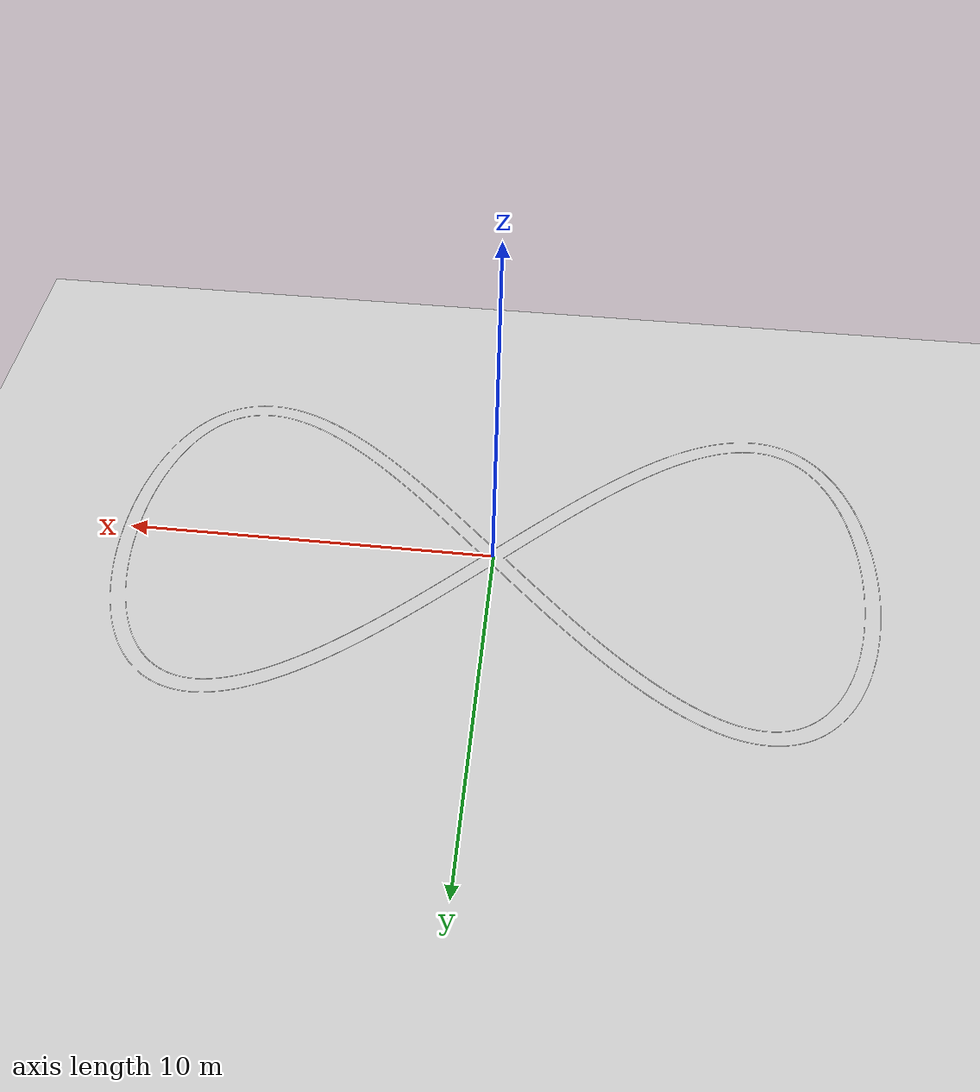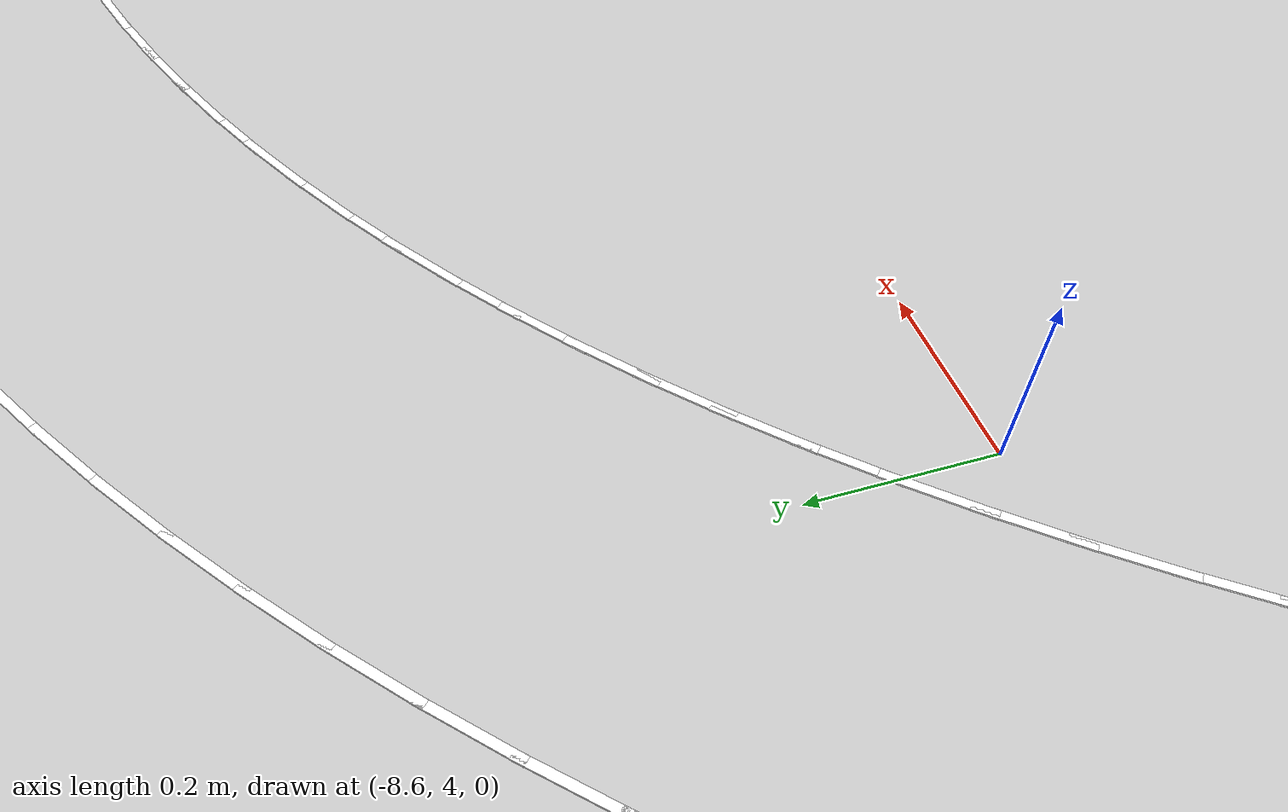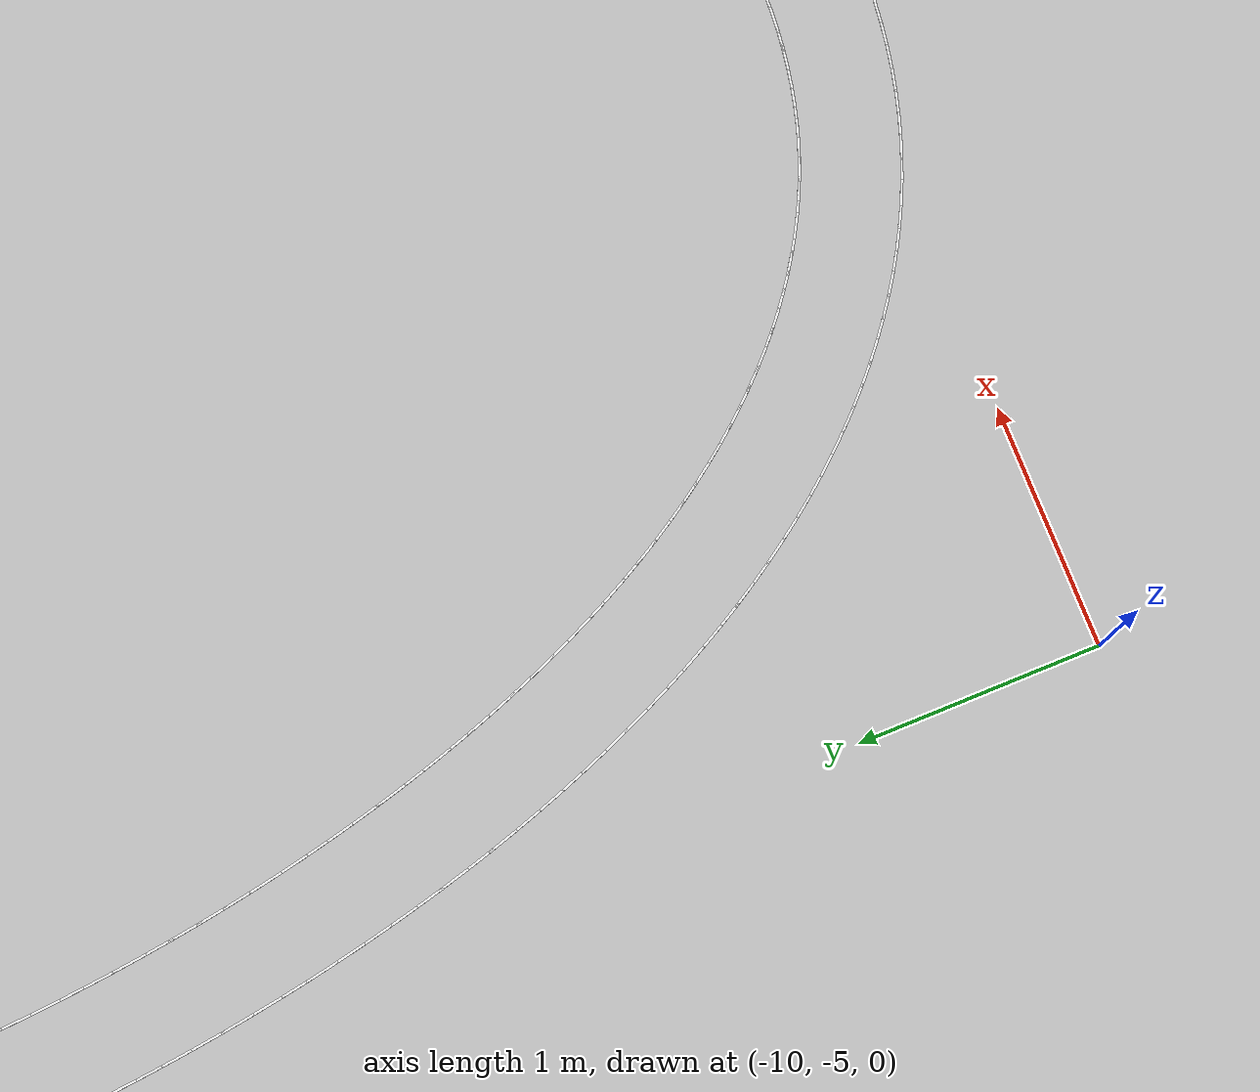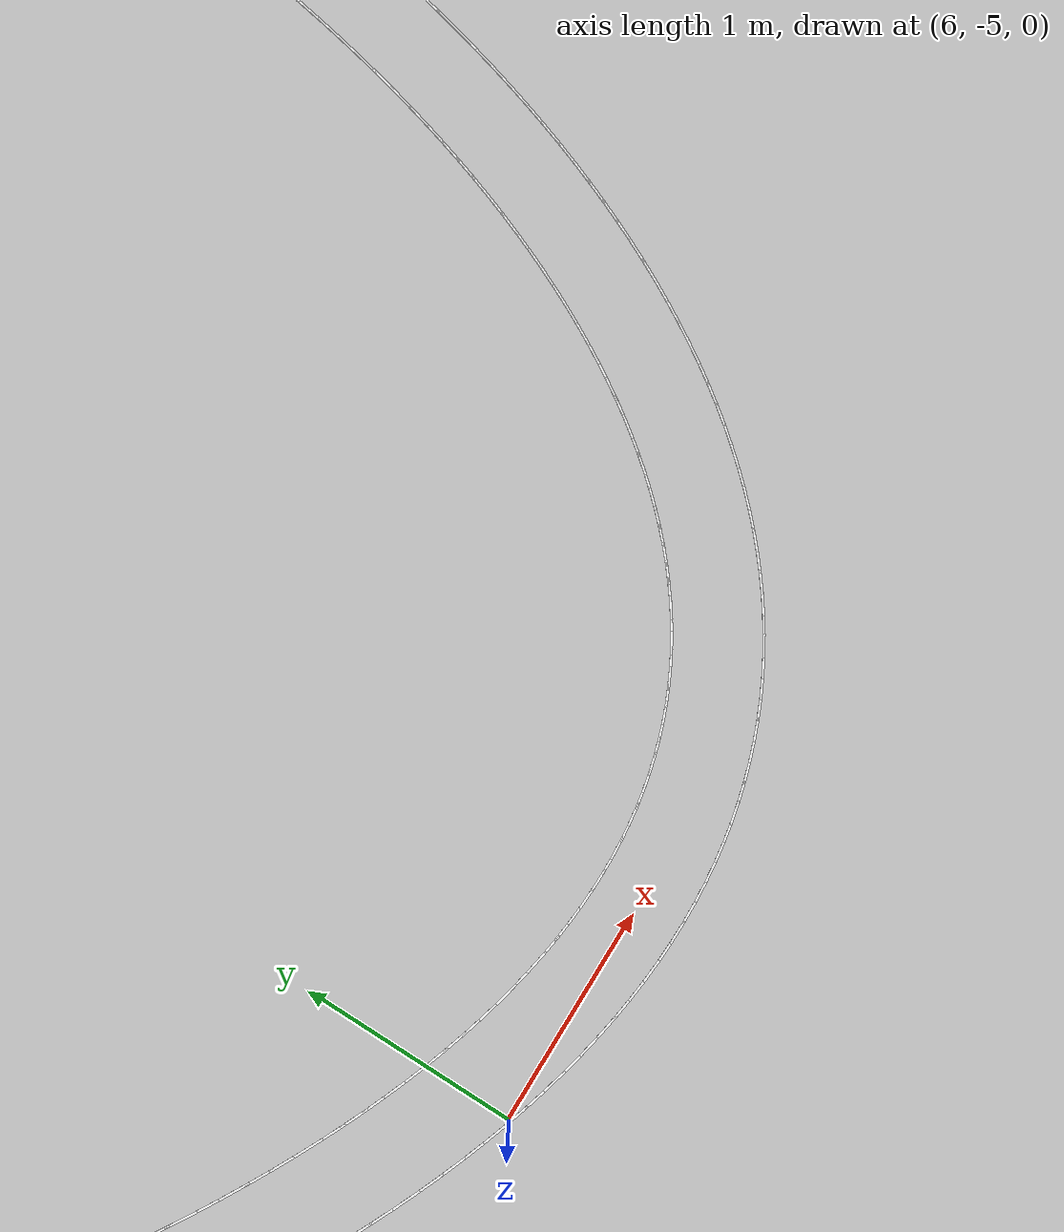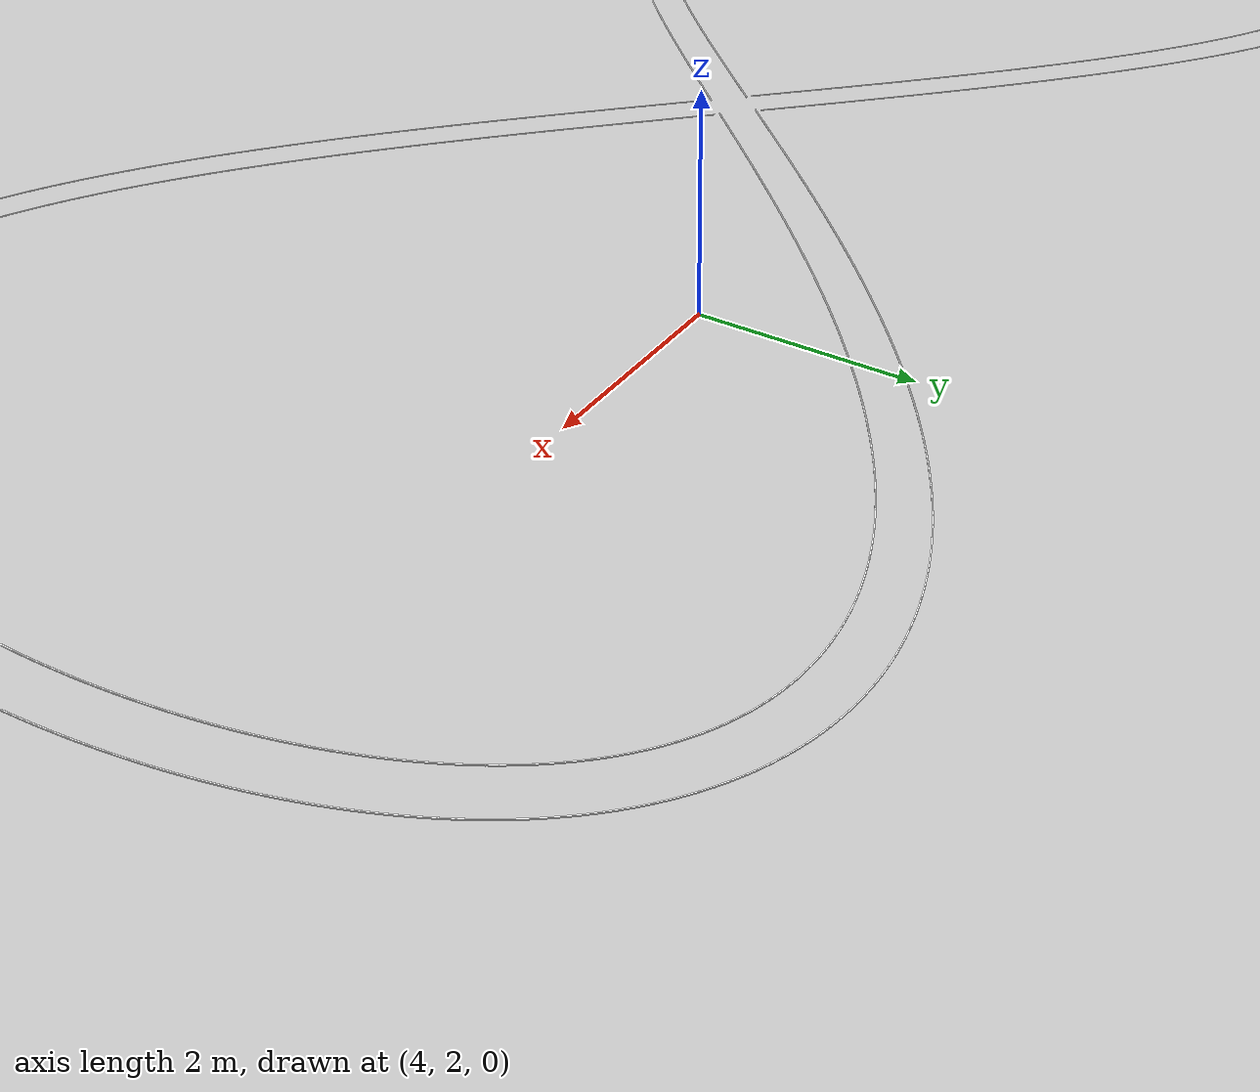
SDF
<sdf version="1.7">
 <world name="default">
  <plugin name="gazebo_ros_api_plugin" filename="libgazebo_ros_api_plugin.so"/>
  <light name="sun" type="directional">
   <pose>0 0 10 0 -0 0</pose>
   <diffuse>0.8 0.8 0.8 1</diffuse>
   <specular>0.2 0.2 0.2 1</specular>
   <attenuation>
    <range>1000</range>
    <constant>0.9</constant>
    <linear>0.01</linear>
    <quadratic>0.001</quadratic>
   </attenuation>
   <direction>-0.5 0.1 -0.9</direction>
   <spot><inner_angle>0</inner_angle><outer_angle>0</outer_angle><falloff>0</falloff></spot>
  </light>
  <model name="ground_plane">
   <static>1</static>
   <link name="link">
    <collision name="collision">
     <geometry><plane><normal>0 0 1</normal><size>100 100</size></plane></geometry>
     <surface>
      <contact><collide_bitmask>65535</collide_bitmask></contact>
      <friction><ode><mu>100</mu><mu2>50</mu2></ode></friction>
     </surface>
    </collision>
    <visual name="visual">
     <cast_shadows>0</cast_shadows>
     <geometry><plane><normal>0 0 1</normal><size>100 100</size></plane></geometry>
     <material>
      <script><uri>file://media/materials/scripts/gazebo.material</uri><name>Gazebo/Grey</name></script>
     </material>
    </visual>
   </link>
  </model>
  <gravity>0 0 -9.8</gravity>
  <magnetic_field>6e-06 2.3e-05 -4.2e-05</magnetic_field>
  <atmosphere type="adiabatic"/>
  <physics type="ode">
   <max_step_size>0.001</max_step_size>
   <real_time_factor>1</real_time_factor>
   <real_time_update_rate>1000</real_time_update_rate>
  </physics>
  <scene><ambient>0.4 0.4 0.4 1</ambient><background>0.7 0.7 0.7 1</background><shadows>1</shadows></scene>
  <spherical_coordinates>
   <surface_model>EARTH_WGS84</surface_model>
   <latitude_deg>0</latitude_deg>
   <longitude_deg>0</longitude_deg>
   <elevation>0</elevation>
   <heading_deg>0</heading_deg>
  </spherical_coordinates>
  <model name="lane_line_left_1">
   <static>1</static>
   <link name="link">
    <pose>0 0 -0.004 0 -0 0</pose>
    <visual name="visual">
     <geometry><box><size>0.198 0.01 0.01</size></box></geometry>
     <material><ambient>1 1 1 1</ambient><diffuse>1 1 1 1</diffuse></material>
    </visual>
    <collision name="collision"><geometry><box><size>0.198 0.01 0.01</size></box></geometry></collision>
   </link>
   <pose>0.047476 0.330274 0 0 -0 0.785121</pose>
  </model>
  <model name="lane_line_right_1">
   <static>1</static>
   <link name="link">
    <pose>0 0 -0.004 0 -0 0</pose>
    <visual name="visual">
     <geometry><box><size>0.198 0.01 0.01</size></box></geometry>
     <material><ambient>1 1 1 1</ambient><diffuse>1 1 1 1</diffuse></material>
    </visual>
    <collision name="collision"><geometry><box><size>0.198 0.01 0.01</size></box></geometry></collision>
   </link>
   <pose>0.33024 0.047353 0 0 -0 0.785121</pose>
  </model>
  <model name="lane_line_left_2">
   <static>1</static>
   <link name="link">
    <pose>0 0 -0.004 0 -0 0</pose>
    <visual name="visual">
     <geometry><box><size>0.1978 0.01 0.01</size></box></geometry>
     <material><ambient>1 1 1 1</ambient><diffuse>1 1 1 1</diffuse></material>
    </visual>
    <collision name="collision"><geometry><box><size>0.1978 0.01 0.01</size></box></geometry></collision>
   </link>
   <pose>0.173416 0.456084 0 0 -0 0.784644</pose>
  </model>
  <model name="lane_line_right_2">
   <static>1</static>
   <link name="link">
    <pose>0 0 -0.004 0 -0 0</pose>
    <visual name="visual">
     <geometry><box><size>0.1978 0.01 0.01</size></box></geometry>
     <material><ambient>1 1 1 1</ambient><diffuse>1 1 1 1</diffuse></material>
    </visual>
    <collision name="collision"><geometry><box><size>0.1978 0.01 0.01</size></box></geometry></collision>
   </link>
   <pose>0.456045 0.173028 0 0 -0 0.784644</pose>
  </model>
  <model name="lane_line_left_3">
   <static>1</static>
   <link name="link">
    <pose>0 0 -0.004 0 -0 0</pose>
    <visual name="visual">
     <geometry><box><size>0.1976 0.01 0.01</size></box></geometry>
     <material><ambient>1 1 1 1</ambient><diffuse>1 1 1 1</diffuse></material>
    </visual>
    <collision name="collision"><geometry><box><size>0.1976 0.01 0.01</size></box></geometry></collision>
   </link>
   <pose>0.29934 0.581728 0 0 -0 0.783929</pose>
  </model>
  <model name="lane_line_right_3">
   <static>1</static>
   <link name="link">
    <pose>0 0 -0.004 0 -0 0</pose>
    <visual name="visual">
     <geometry><box><size>0.1976 0.01 0.01</size></box></geometry>
     <material><ambient>1 1 1 1</ambient><diffuse>1 1 1 1</diffuse></material>
    </visual>
    <collision name="collision"><geometry><box><size>0.1976 0.01 0.01</size></box></geometry></collision>
   </link>
   <pose>0.581766 0.29847 0 0 -0 0.783929</pose>
  </model>
  <model name="lane_line_left_4">
   <static>1</static>
   <link name="link">
    <pose>0 0 -0.004 0 -0 0</pose>
    <visual name="visual">
     <geometry><box><size>0.1974 0.01 0.01</size></box></geometry>
     <material><ambient>1 1 1 1</ambient><diffuse>1 1 1 1</diffuse></material>
    </visual>
    <collision name="collision"><geometry><box><size>0.1974 0.01 0.01</size></box></geometry></collision>
   </link>
   <pose>0.425227 0.707127 0 0 -0 0.782974</pose>
  </model>
  <model name="lane_line_right_4">
   <static>1</static>
   <link name="link">
    <pose>0 0 -0.004 0 -0 0</pose>
    <visual name="visual">
     <geometry><box><size>0.1974 0.01 0.01</size></box></geometry>
     <material><ambient>1 1 1 1</ambient><diffuse>1 1 1 1</diffuse></material>
    </visual>
    <collision name="collision"><geometry><box><size>0.1974 0.01 0.01</size></box></geometry></collision>
   </link>
   <pose>0.707384 0.423599 0 0 -0 0.782974</pose>
  </model>
  <model name="lane_line_left_5">
   <static>1</static>
   <link name="link">
    <pose>0 0 -0.004 0 -0 0</pose>
    <visual name="visual">
     <geometry><box><size>0.197 0.01 0.01</size></box></geometry>
     <material><ambient>1 1 1 1</ambient><diffuse>1 1 1 1</diffuse></material>
    </visual>
    <collision name="collision"><geometry><box><size>0.197 0.01 0.01</size></box></geometry></collision>
   </link>
   <pose>0.55106 0.832201 0 0 -0 0.781777</pose>
  </model>
  <model name="lane_line_right_5">
   <static>1</static>
   <link name="link">
    <pose>0 0 -0.004 0 -0 0</pose>
    <visual name="visual">
     <geometry><box><size>0.197 0.01 0.01</size></box></geometry>
     <material><ambient>1 1 1 1</ambient><diffuse>1 1 1 1</diffuse></material>
    </visual>
    <collision name="collision"><geometry><box><size>0.197 0.01 0.01</size></box></geometry></collision>
   </link>
   <pose>0.832877 0.548336 0 0 -0 0.781777</pose>
  </model>
  <model name="lane_line_left_6">
   <static>1</static>
   <link name="link">
    <pose>0 0 -0.004 0 -0 0</pose>
    <visual name="visual">
     <geometry><box><size>0.1966 0.01 0.01</size></box></geometry>
     <material><ambient>1 1 1 1</ambient><diffuse>1 1 1 1</diffuse></material>
    </visual>
    <collision name="collision"><geometry><box><size>0.1966 0.01 0.01</size></box></geometry></collision>
   </link>
   <pose>0.676818 0.956872 0 0 -0 0.780336</pose>
  </model>
  <model name="lane_line_right_6">
   <static>1</static>
   <link name="link">
    <pose>0 0 -0.004 0 -0 0</pose>
    <visual name="visual">
     <geometry><box><size>0.1966 0.01 0.01</size></box></geometry>
     <material><ambient>1 1 1 1</ambient><diffuse>1 1 1 1</diffuse></material>
    </visual>
    <collision name="collision"><geometry><box><size>0.1966 0.01 0.01</size></box></geometry></collision>
   </link>
   <pose>0.958225 0.672601 0 0 -0 0.780336</pose>
  </model>
  <model name="lane_line_left_7">
   <static>1</static>
   <link name="link">
    <pose>0 0 -0.004 0 -0 0</pose>
    <visual name="visual">
     <geometry><box><size>0.1961 0.01 0.01</size></box></geometry>
     <material><ambient>1 1 1 1</ambient><diffuse>1 1 1 1</diffuse></material>
    </visual>
    <collision name="collision"><geometry><box><size>0.1961 0.01 0.01</size></box></geometry></collision>
   </link>
   <pose>0.802481 1.08106 0 0 -0 0.77865</pose>
  </model>
  <model name="lane_line_right_7">
   <static>1</static>
   <link name="link">
    <pose>0 0 -0.004 0 -0 0</pose>
    <visual name="visual">
     <geometry><box><size>0.1961 0.01 0.01</size></box></geometry>
     <material><ambient>1 1 1 1</ambient><diffuse>1 1 1 1</diffuse></material>
    </visual>
    <collision name="collision"><geometry><box><size>0.1961 0.01 0.01</size></box></geometry></collision>
   </link>
   <pose>1.08341 0.796315 0 0 -0 0.77865</pose>
  </model>
  <model name="lane_line_left_8">
   <static>1</static>
   <link name="link">
    <pose>0 0 -0.004 0 -0 0</pose>
    <visual name="visual">
     <geometry><box><size>0.1955 0.01 0.01</size></box></geometry>
     <material><ambient>1 1 1 1</ambient><diffuse>1 1 1 1</diffuse></material>
    </visual>
    <collision name="collision"><geometry><box><size>0.1955 0.01 0.01</size></box></geometry></collision>
   </link>
   <pose>0.928031 1.20469 0 0 -0 0.776714</pose>
  </model>
  <model name="lane_line_right_8">
   <static>1</static>
   <link name="link">
    <pose>0 0 -0.004 0 -0 0</pose>
    <visual name="visual">
     <geometry><box><size>0.1955 0.01 0.01</size></box></geometry>
     <material><ambient>1 1 1 1</ambient><diffuse>1 1 1 1</diffuse></material>
    </visual>
    <collision name="collision"><geometry><box><size>0.1955 0.01 0.01</size></box></geometry></collision>
   </link>
   <pose>1.20841 0.919399 0 0 -0 0.776714</pose>
  </model>
  <model name="lane_line_left_9">
   <static>1</static>
   <link name="link">
    <pose>0 0 -0.004 0 -0 0</pose>
    <visual name="visual">
     <geometry><box><size>0.1949 0.01 0.01</size></box></geometry>
     <material><ambient>1 1 1 1</ambient><diffuse>1 1 1 1</diffuse></material>
    </visual>
    <collision name="collision"><geometry><box><size>0.1949 0.01 0.01</size></box></geometry></collision>
   </link>
   <pose>1.05345 1.32768 0 0 -0 0.774527</pose>
  </model>
  <model name="lane_line_right_9">
   <static>1</static>
   <link name="link">
    <pose>0 0 -0.004 0 -0 0</pose>
    <visual name="visual">
     <geometry><box><size>0.1949 0.01 0.01</size></box></geometry>
     <material><ambient>1 1 1 1</ambient><diffuse>1 1 1 1</diffuse></material>
    </visual>
    <collision name="collision"><geometry><box><size>0.1949 0.01 0.01</size></box></geometry></collision>
   </link>
   <pose>1.3332 1.04178 0 0 -0 0.774527</pose>
  </model>
  <model name="lane_line_left_10">
   <static>1</static>
   <link name="link">
    <pose>0 0 -0.004 0 -0 0</pose>
    <visual name="visual">
     <geometry><box><size>0.1942 0.01 0.01</size></box></geometry>
     <material><ambient>1 1 1 1</ambient><diffuse>1 1 1 1</diffuse></material>
    </visual>
    <collision name="collision"><geometry><box><size>0.1942 0.01 0.01</size></box></geometry></collision>
   </link>
   <pose>1.17871 1.44995 0 0 -0 0.772085</pose>
  </model>
  <model name="lane_line_right_10">
   <static>1</static>
   <link name="link">
    <pose>0 0 -0.004 0 -0 0</pose>
    <visual name="visual">
     <geometry><box><size>0.1942 0.01 0.01</size></box></geometry>
     <material><ambient>1 1 1 1</ambient><diffuse>1 1 1 1</diffuse></material>
    </visual>
    <collision name="collision"><geometry><box><size>0.1942 0.01 0.01</size></box></geometry></collision>
   </link>
   <pose>1.45776 1.16336 0 0 -0 0.772085</pose>
  </model>
  <model name="lane_line_left_11">
   <static>1</static>
   <link name="link">
    <pose>0 0 -0.004 0 -0 0</pose>
    <visual name="visual">
     <geometry><box><size>0.1935 0.01 0.01</size></box></geometry>
     <material><ambient>1 1 1 1</ambient><diffuse>1 1 1 1</diffuse></material>
    </visual>
    <collision name="collision"><geometry><box><size>0.1935 0.01 0.01</size></box></geometry></collision>
   </link>
   <pose>1.30381 1.57143 0 0 -0 0.769384</pose>
  </model>
  <model name="lane_line_right_11">
   <static>1</static>
   <link name="link">
    <pose>0 0 -0.004 0 -0 0</pose>
    <visual name="visual">
     <geometry><box><size>0.1935 0.01 0.01</size></box></geometry>
     <material><ambient>1 1 1 1</ambient><diffuse>1 1 1 1</diffuse></material>
    </visual>
    <collision name="collision"><geometry><box><size>0.1935 0.01 0.01</size></box></geometry></collision>
   </link>
   <pose>1.58208 1.28409 0 0 -0 0.769384</pose>
  </model>
  <model name="lane_line_left_12">
   <static>1</static>
   <link name="link">
    <pose>0 0 -0.004 0 -0 0</pose>
    <visual name="visual">
     <geometry><box><size>0.1926 0.01 0.01</size></box></geometry>
     <material><ambient>1 1 1 1</ambient><diffuse>1 1 1 1</diffuse></material>
    </visual>
    <collision name="collision"><geometry><box><size>0.1926 0.01 0.01</size></box></geometry></collision>
   </link>
   <pose>1.42871 1.69204 0 0 -0 0.766419</pose>
  </model>
  <model name="lane_line_right_12">
   <static>1</static>
   <link name="link">
    <pose>0 0 -0.004 0 -0 0</pose>
    <visual name="visual">
     <geometry><box><size>0.1926 0.01 0.01</size></box></geometry>
     <material><ambient>1 1 1 1</ambient><diffuse>1 1 1 1</diffuse></material>
    </visual>
    <collision name="collision"><geometry><box><size>0.1926 0.01 0.01</size></box></geometry></collision>
   </link>
   <pose>1.70613 1.40388 0 0 -0 0.766419</pose>
  </model>
  <model name="lane_line_left_13">
   <static>1</static>
   <link name="link">
    <pose>0 0 -0.004 0 -0 0</pose>
    <visual name="visual">
     <geometry><box><size>0.1917 0.01 0.01</size></box></geometry>
     <material><ambient>1 1 1 1</ambient><diffuse>1 1 1 1</diffuse></material>
    </visual>
    <collision name="collision"><geometry><box><size>0.1917 0.01 0.01</size></box></geometry></collision>
   </link>
   <pose>1.55341 1.8117 0 0 -0 0.763185</pose>
  </model>
  <model name="lane_line_right_13">
   <static>1</static>
   <link name="link">
    <pose>0 0 -0.004 0 -0 0</pose>
    <visual name="visual">
     <geometry><box><size>0.1917 0.01 0.01</size></box></geometry>
     <material><ambient>1 1 1 1</ambient><diffuse>1 1 1 1</diffuse></material>
    </visual>
    <collision name="collision"><geometry><box><size>0.1917 0.01 0.01</size></box></geometry></collision>
   </link>
   <pose>1.8299 1.52264 0 0 -0 0.763185</pose>
  </model>
  <model name="lane_line_left_14">
   <static>1</static>
   <link name="link">
    <pose>0 0 -0.004 0 -0 0</pose>
    <visual name="visual">
     <geometry><box><size>0.1908 0.01 0.01</size></box></geometry>
     <material><ambient>1 1 1 1</ambient><diffuse>1 1 1 1</diffuse></material>
    </visual>
    <collision name="collision"><geometry><box><size>0.1908 0.01 0.01</size></box></geometry></collision>
   </link>
   <pose>1.67788 1.93034 0 0 -0 0.759677</pose>
  </model>
  <model name="lane_line_right_14">
   <static>1</static>
   <link name="link">
    <pose>0 0 -0.004 0 -0 0</pose>
    <visual name="visual">
     <geometry><box><size>0.1908 0.01 0.01</size></box></geometry>
     <material><ambient>1 1 1 1</ambient><diffuse>1 1 1 1</diffuse></material>
    </visual>
    <collision name="collision"><geometry><box><size>0.1908 0.01 0.01</size></box></geometry></collision>
   </link>
   <pose>1.95335 1.64032 0 0 -0 0.759677</pose>
  </model>
  <model name="lane_line_left_15">
   <static>1</static>
   <link name="link">
    <pose>0 0 -0.004 0 -0 0</pose>
    <visual name="visual">
     <geometry><box><size>0.1898 0.01 0.01</size></box></geometry>
     <material><ambient>1 1 1 1</ambient><diffuse>1 1 1 1</diffuse></material>
    </visual>
    <collision name="collision"><geometry><box><size>0.1898 0.01 0.01</size></box></geometry></collision>
   </link>
   <pose>1.8021 2.04789 0 0 -0 0.75589</pose>
  </model>
  <model name="lane_line_right_15">
   <static>1</static>
   <link name="link">
    <pose>0 0 -0.004 0 -0 0</pose>
    <visual name="visual">
     <geometry><box><size>0.1898 0.01 0.01</size></box></geometry>
     <material><ambient>1 1 1 1</ambient><diffuse>1 1 1 1</diffuse></material>
    </visual>
    <collision name="collision"><geometry><box><size>0.1898 0.01 0.01</size></box></geometry></collision>
   </link>
   <pose>2.07647 1.75682 0 0 -0 0.75589</pose>
  </model>
  <model name="lane_line_left_16">
   <static>1</static>
   <link name="link">
    <pose>0 0 -0.004 0 -0 0</pose>
    <visual name="visual">
     <geometry><box><size>0.1887 0.01 0.01</size></box></geometry>
     <material><ambient>1 1 1 1</ambient><diffuse>1 1 1 1</diffuse></material>
    </visual>
    <collision name="collision"><geometry><box><size>0.1887 0.01 0.01</size></box></geometry></collision>
   </link>
   <pose>1.92606 2.16426 0 0 -0 0.751816</pose>
  </model>
  <model name="lane_line_right_16">
   <static>1</static>
   <link name="link">
    <pose>0 0 -0.004 0 -0 0</pose>
    <visual name="visual">
     <geometry><box><size>0.1887 0.01 0.01</size></box></geometry>
     <material><ambient>1 1 1 1</ambient><diffuse>1 1 1 1</diffuse></material>
    </visual>
    <collision name="collision"><geometry><box><size>0.1887 0.01 0.01</size></box></geometry></collision>
   </link>
   <pose>2.19924 1.87208 0 0 -0 0.751816</pose>
  </model>
  <model name="lane_line_left_17">
   <static>1</static>
   <link name="link">
    <pose>0 0 -0.004 0 -0 0</pose>
    <visual name="visual">
     <geometry><box><size>0.1875 0.01 0.01</size></box></geometry>
     <material><ambient>1 1 1 1</ambient><diffuse>1 1 1 1</diffuse></material>
    </visual>
    <collision name="collision"><geometry><box><size>0.1875 0.01 0.01</size></box></geometry></collision>
   </link>
   <pose>2.04974 2.2794 0 0 -0 0.74745</pose>
  </model>
  <model name="lane_line_right_17">
   <static>1</static>
   <link name="link">
    <pose>0 0 -0.004 0 -0 0</pose>
    <visual name="visual">
     <geometry><box><size>0.1875 0.01 0.01</size></box></geometry>
     <material><ambient>1 1 1 1</ambient><diffuse>1 1 1 1</diffuse></material>
    </visual>
    <collision name="collision"><geometry><box><size>0.1875 0.01 0.01</size></box></geometry></collision>
   </link>
   <pose>2.32164 1.98603 0 0 -0 0.74745</pose>
  </model>
  <model name="lane_line_left_18">
   <static>1</static>
   <link name="link">
    <pose>0 0 -0.004 0 -0 0</pose>
    <visual name="visual">
     <geometry><box><size>0.1863 0.01 0.01</size></box></geometry>
     <material><ambient>1 1 1 1</ambient><diffuse>1 1 1 1</diffuse></material>
    </visual>
    <collision name="collision"><geometry><box><size>0.1863 0.01 0.01</size></box></geometry></collision>
   </link>
   <pose>2.17311 2.39322 0 0 -0 0.742783</pose>
  </model>
  <model name="lane_line_right_18">
   <static>1</static>
   <link name="link">
    <pose>0 0 -0.004 0 -0 0</pose>
    <visual name="visual">
     <geometry><box><size>0.1863 0.01 0.01</size></box></geometry>
     <material><ambient>1 1 1 1</ambient><diffuse>1 1 1 1</diffuse></material>
    </visual>
    <collision name="collision"><geometry><box><size>0.1863 0.01 0.01</size></box></geometry></collision>
   </link>
   <pose>2.44365 2.09858 0 0 -0 0.742783</pose>
  </model>
  <model name="lane_line_left_19">
   <static>1</static>
   <link name="link">
    <pose>0 0 -0.004 0 -0 0</pose>
    <visual name="visual">
     <geometry><box><size>0.1851 0.01 0.01</size></box></geometry>
     <material><ambient>1 1 1 1</ambient><diffuse>1 1 1 1</diffuse></material>
    </visual>
    <collision name="collision"><geometry><box><size>0.1851 0.01 0.01</size></box></geometry></collision>
   </link>
   <pose>2.29617 2.50565 0 0 -0 0.737807</pose>
  </model>
  <model name="lane_line_right_19">
   <static>1</static>
   <link name="link">
    <pose>0 0 -0.004 0 -0 0</pose>
    <visual name="visual">
     <geometry><box><size>0.1851 0.01 0.01</size></box></geometry>
     <material><ambient>1 1 1 1</ambient><diffuse>1 1 1 1</diffuse></material>
    </visual>
    <collision name="collision"><geometry><box><size>0.1851 0.01 0.01</size></box></geometry></collision>
   </link>
   <pose>2.56524 2.20968 0 0 -0 0.737807</pose>
  </model>
  <model name="lane_line_left_20">
   <static>1</static>
   <link name="link">
    <pose>0 0 -0.004 0 -0 0</pose>
    <visual name="visual">
     <geometry><box><size>0.1837 0.01 0.01</size></box></geometry>
     <material><ambient>1 1 1 1</ambient><diffuse>1 1 1 1</diffuse></material>
    </visual>
    <collision name="collision"><geometry><box><size>0.1837 0.01 0.01</size></box></geometry></collision>
   </link>
   <pose>2.4189 2.61663 0 0 -0 0.732515</pose>
  </model>
  <model name="lane_line_right_20">
   <static>1</static>
   <link name="link">
    <pose>0 0 -0.004 0 -0 0</pose>
    <visual name="visual">
     <geometry><box><size>0.1837 0.01 0.01</size></box></geometry>
     <material><ambient>1 1 1 1</ambient><diffuse>1 1 1 1</diffuse></material>
    </visual>
    <collision name="collision"><geometry><box><size>0.1837 0.01 0.01</size></box></geometry></collision>
   </link>
   <pose>2.6864 2.31923 0 0 -0 0.732515</pose>
  </model>
  <model name="lane_line_left_21">
   <static>1</static>
   <link name="link">
    <pose>0 0 -0.004 0 -0 0</pose>
    <visual name="visual">
     <geometry><box><size>0.1824 0.01 0.01</size></box></geometry>
     <material><ambient>1 1 1 1</ambient><diffuse>1 1 1 1</diffuse></material>
    </visual>
    <collision name="collision"><geometry><box><size>0.1824 0.01 0.01</size></box></geometry></collision>
   </link>
   <pose>2.54127 2.72608 0 0 -0 0.726896</pose>
  </model>
  <model name="lane_line_right_21">
   <static>1</static>
   <link name="link">
    <pose>0 0 -0.004 0 -0 0</pose>
    <visual name="visual">
     <geometry><box><size>0.1824 0.01 0.01</size></box></geometry>
     <material><ambient>1 1 1 1</ambient><diffuse>1 1 1 1</diffuse></material>
    </visual>
    <collision name="collision"><geometry><box><size>0.1824 0.01 0.01</size></box></geometry></collision>
   </link>
   <pose>2.8071 2.42719 0 0 -0 0.726896</pose>
  </model>
  <model name="lane_line_left_22">
   <static>1</static>
   <link name="link">
    <pose>0 0 -0.004 0 -0 0</pose>
    <visual name="visual">
     <geometry><box><size>0.1809 0.01 0.01</size></box></geometry>
     <material><ambient>1 1 1 1</ambient><diffuse>1 1 1 1</diffuse></material>
    </visual>
    <collision name="collision"><geometry><box><size>0.1809 0.01 0.01</size></box></geometry></collision>
   </link>
   <pose>2.66328 2.83394 0 0 -0 0.720941</pose>
  </model>
  <model name="lane_line_right_22">
   <static>1</static>
   <link name="link">
    <pose>0 0 -0.004 0 -0 0</pose>
    <visual name="visual">
     <geometry><box><size>0.1809 0.01 0.01</size></box></geometry>
     <material><ambient>1 1 1 1</ambient><diffuse>1 1 1 1</diffuse></material>
    </visual>
    <collision name="collision"><geometry><box><size>0.1809 0.01 0.01</size></box></geometry></collision>
   </link>
   <pose>2.92731 2.53347 0 0 -0 0.720941</pose>
  </model>
  <model name="lane_line_left_23">
   <static>1</static>
   <link name="link">
    <pose>0 0 -0.004 0 -0 0</pose>
    <visual name="visual">
     <geometry><box><size>0.1795 0.01 0.01</size></box></geometry>
     <material><ambient>1 1 1 1</ambient><diffuse>1 1 1 1</diffuse></material>
    </visual>
    <collision name="collision"><geometry><box><size>0.1795 0.01 0.01</size></box></geometry></collision>
   </link>
   <pose>2.7849 2.94014 0 0 -0 0.714639</pose>
  </model>
  <model name="lane_line_right_23">
   <static>1</static>
   <link name="link">
    <pose>0 0 -0.004 0 -0 0</pose>
    <visual name="visual">
     <geometry><box><size>0.1795 0.01 0.01</size></box></geometry>
     <material><ambient>1 1 1 1</ambient><diffuse>1 1 1 1</diffuse></material>
    </visual>
    <collision name="collision"><geometry><box><size>0.1795 0.01 0.01</size></box></geometry></collision>
   </link>
   <pose>3.04703 2.638 0 0 -0 0.714639</pose>
  </model>
  <model name="lane_line_left_24">
   <static>1</static>
   <link name="link">
    <pose>0 0 -0.004 0 -0 0</pose>
    <visual name="visual">
     <geometry><box><size>0.1779 0.01 0.01</size></box></geometry>
     <material><ambient>1 1 1 1</ambient><diffuse>1 1 1 1</diffuse></material>
    </visual>
    <collision name="collision"><geometry><box><size>0.1779 0.01 0.01</size></box></geometry></collision>
   </link>
   <pose>2.90611 3.0446 0 0 -0 0.707979</pose>
  </model>
  <model name="lane_line_right_24">
   <static>1</static>
   <link name="link">
    <pose>0 0 -0.004 0 -0 0</pose>
    <visual name="visual">
     <geometry><box><size>0.1779 0.01 0.01</size></box></geometry>
     <material><ambient>1 1 1 1</ambient><diffuse>1 1 1 1</diffuse></material>
    </visual>
    <collision name="collision"><geometry><box><size>0.1779 0.01 0.01</size></box></geometry></collision>
   </link>
   <pose>3.16623 2.74073 0 0 -0 0.707979</pose>
  </model>
  <model name="lane_line_left_25">
   <static>1</static>
   <link name="link">
    <pose>0 0 -0.004 0 -0 0</pose>
    <visual name="visual">
     <geometry><box><size>0.1763 0.01 0.01</size></box></geometry>
     <material><ambient>1 1 1 1</ambient><diffuse>1 1 1 1</diffuse></material>
    </visual>
    <collision name="collision"><geometry><box><size>0.1763 0.01 0.01</size></box></geometry></collision>
   </link>
   <pose>3.02691 3.14728 0 0 -0 0.700949</pose>
  </model>
  <model name="lane_line_right_25">
   <static>1</static>
   <link name="link">
    <pose>0 0 -0.004 0 -0 0</pose>
    <visual name="visual">
     <geometry><box><size>0.1763 0.01 0.01</size></box></geometry>
     <material><ambient>1 1 1 1</ambient><diffuse>1 1 1 1</diffuse></material>
    </visual>
    <collision name="collision"><geometry><box><size>0.1763 0.01 0.01</size></box></geometry></collision>
   </link>
   <pose>3.28489 2.84159 0 0 -0 0.700949</pose>
  </model>
  <model name="lane_line_left_26">
   <static>1</static>
   <link name="link">
    <pose>0 0 -0.004 0 -0 0</pose>
    <visual name="visual">
     <geometry><box><size>0.1747 0.01 0.01</size></box></geometry>
     <material><ambient>1 1 1 1</ambient><diffuse>1 1 1 1</diffuse></material>
    </visual>
    <collision name="collision"><geometry><box><size>0.1747 0.01 0.01</size></box></geometry></collision>
   </link>
   <pose>3.14727 3.2481 0 0 -0 0.693536</pose>
  </model>
  <model name="lane_line_right_26">
   <static>1</static>
   <link name="link">
    <pose>0 0 -0.004 0 -0 0</pose>
    <visual name="visual">
     <geometry><box><size>0.1747 0.01 0.01</size></box></geometry>
     <material><ambient>1 1 1 1</ambient><diffuse>1 1 1 1</diffuse></material>
    </visual>
    <collision name="collision"><geometry><box><size>0.1747 0.01 0.01</size></box></geometry></collision>
   </link>
   <pose>3.40297 2.9405 0 0 -0 0.693536</pose>
  </model>
  <model name="lane_line_left_27">
   <static>1</static>
   <link name="link">
    <pose>0 0 -0.004 0 -0 0</pose>
    <visual name="visual">
     <geometry><box><size>0.173 0.01 0.01</size></box></geometry>
     <material><ambient>1 1 1 1</ambient><diffuse>1 1 1 1</diffuse></material>
    </visual>
    <collision name="collision"><geometry><box><size>0.173 0.01 0.01</size></box></geometry></collision>
   </link>
   <pose>3.26718 3.34699 0 0 -0 0.685726</pose>
  </model>
  <model name="lane_line_right_27">
   <static>1</static>
   <link name="link">
    <pose>0 0 -0.004 0 -0 0</pose>
    <visual name="visual">
     <geometry><box><size>0.173 0.01 0.01</size></box></geometry>
     <material><ambient>1 1 1 1</ambient><diffuse>1 1 1 1</diffuse></material>
    </visual>
    <collision name="collision"><geometry><box><size>0.173 0.01 0.01</size></box></geometry></collision>
   </link>
   <pose>3.52047 3.03741 0 0 -0 0.685726</pose>
  </model>
  <model name="lane_line_left_28">
   <static>1</static>
   <link name="link">
    <pose>0 0 -0.004 0 -0 0</pose>
    <visual name="visual">
     <geometry><box><size>0.1713 0.01 0.01</size></box></geometry>
     <material><ambient>1 1 1 1</ambient><diffuse>1 1 1 1</diffuse></material>
    </visual>
    <collision name="collision"><geometry><box><size>0.1713 0.01 0.01</size></box></geometry></collision>
   </link>
   <pose>3.38662 3.44391 0 0 -0 0.677506</pose>
  </model>
  <model name="lane_line_right_28">
   <static>1</static>
   <link name="link">
    <pose>0 0 -0.004 0 -0 0</pose>
    <visual name="visual">
     <geometry><box><size>0.1713 0.01 0.01</size></box></geometry>
     <material><ambient>1 1 1 1</ambient><diffuse>1 1 1 1</diffuse></material>
    </visual>
    <collision name="collision"><geometry><box><size>0.1713 0.01 0.01</size></box></geometry></collision>
   </link>
   <pose>3.63736 3.13225 0 0 -0 0.677506</pose>
  </model>
  <model name="lane_line_left_29">
   <static>1</static>
   <link name="link">
    <pose>0 0 -0.004 0 -0 0</pose>
    <visual name="visual">
     <geometry><box><size>0.1696 0.01 0.01</size></box></geometry>
     <material><ambient>1 1 1 1</ambient><diffuse>1 1 1 1</diffuse></material>
    </visual>
    <collision name="collision"><geometry><box><size>0.1696 0.01 0.01</size></box></geometry></collision>
   </link>
   <pose>3.50559 3.53878 0 0 -0 0.668859</pose>
  </model>
  <model name="lane_line_right_29">
   <static>1</static>
   <link name="link">
    <pose>0 0 -0.004 0 -0 0</pose>
    <visual name="visual">
     <geometry><box><size>0.1696 0.01 0.01</size></box></geometry>
     <material><ambient>1 1 1 1</ambient><diffuse>1 1 1 1</diffuse></material>
    </visual>
    <collision name="collision"><geometry><box><size>0.1696 0.01 0.01</size></box></geometry></collision>
   </link>
   <pose>3.75362 3.22497 0 0 -0 0.668859</pose>
  </model>
  <model name="lane_line_left_30">
   <static>1</static>
   <link name="link">
    <pose>0 0 -0.004 0 -0 0</pose>
    <visual name="visual">
     <geometry><box><size>0.1678 0.01 0.01</size></box></geometry>
     <material><ambient>1 1 1 1</ambient><diffuse>1 1 1 1</diffuse></material>
    </visual>
    <collision name="collision"><geometry><box><size>0.1678 0.01 0.01</size></box></geometry></collision>
   </link>
   <pose>3.62405 3.63155 0 0 -0 0.659769</pose>
  </model>
  <model name="lane_line_right_30">
   <static>1</static>
   <link name="link">
    <pose>0 0 -0.004 0 -0 0</pose>
    <visual name="visual">
     <geometry><box><size>0.1678 0.01 0.01</size></box></geometry>
     <material><ambient>1 1 1 1</ambient><diffuse>1 1 1 1</diffuse></material>
    </visual>
    <collision name="collision"><geometry><box><size>0.1678 0.01 0.01</size></box></geometry></collision>
   </link>
   <pose>3.86923 3.31549 0 0 -0 0.659769</pose>
  </model>
  <model name="lane_line_left_31">
   <static>1</static>
   <link name="link">
    <pose>0 0 -0.004 0 -0 0</pose>
    <visual name="visual">
     <geometry><box><size>0.1659 0.01 0.01</size></box></geometry>
     <material><ambient>1 1 1 1</ambient><diffuse>1 1 1 1</diffuse></material>
    </visual>
    <collision name="collision"><geometry><box><size>0.1659 0.01 0.01</size></box></geometry></collision>
   </link>
   <pose>3.74201 3.72216 0 0 -0 0.650219</pose>
  </model>
  <model name="lane_line_right_31">
   <static>1</static>
   <link name="link">
    <pose>0 0 -0.004 0 -0 0</pose>
    <visual name="visual">
     <geometry><box><size>0.1659 0.01 0.01</size></box></geometry>
     <material><ambient>1 1 1 1</ambient><diffuse>1 1 1 1</diffuse></material>
    </visual>
    <collision name="collision"><geometry><box><size>0.1659 0.01 0.01</size></box></geometry></collision>
   </link>
   <pose>3.98415 3.40378 0 0 -0 0.650219</pose>
  </model>
  <model name="lane_line_left_32">
   <static>1</static>
   <link name="link">
    <pose>0 0 -0.004 0 -0 0</pose>
    <visual name="visual">
     <geometry><box><size>0.164 0.01 0.01</size></box></geometry>
     <material><ambient>1 1 1 1</ambient><diffuse>1 1 1 1</diffuse></material>
    </visual>
    <collision name="collision"><geometry><box><size>0.164 0.01 0.01</size></box></geometry></collision>
   </link>
   <pose>3.85944 3.81055 0 0 -0 0.640191</pose>
  </model>
  <model name="lane_line_right_32">
   <static>1</static>
   <link name="link">
    <pose>0 0 -0.004 0 -0 0</pose>
    <visual name="visual">
     <geometry><box><size>0.164 0.01 0.01</size></box></geometry>
     <material><ambient>1 1 1 1</ambient><diffuse>1 1 1 1</diffuse></material>
    </visual>
    <collision name="collision"><geometry><box><size>0.164 0.01 0.01</size></box></geometry></collision>
   </link>
   <pose>4.09838 3.48976 0 0 -0 0.640191</pose>
  </model>
  <model name="lane_line_left_33">
   <static>1</static>
   <link name="link">
    <pose>0 0 -0.004 0 -0 0</pose>
    <visual name="visual">
     <geometry><box><size>0.1621 0.01 0.01</size></box></geometry>
     <material><ambient>1 1 1 1</ambient><diffuse>1 1 1 1</diffuse></material>
    </visual>
    <collision name="collision"><geometry><box><size>0.1621 0.01 0.01</size></box></geometry></collision>
   </link>
   <pose>3.97633 3.89667 0 0 -0 0.629666</pose>
  </model>
  <model name="lane_line_right_33">
   <static>1</static>
   <link name="link">
    <pose>0 0 -0.004 0 -0 0</pose>
    <visual name="visual">
     <geometry><box><size>0.1621 0.01 0.01</size></box></geometry>
     <material><ambient>1 1 1 1</ambient><diffuse>1 1 1 1</diffuse></material>
    </visual>
    <collision name="collision"><geometry><box><size>0.1621 0.01 0.01</size></box></geometry></collision>
   </link>
   <pose>4.21188 3.57338 0 0 -0 0.629666</pose>
  </model>
  <model name="lane_line_left_34">
   <static>1</static>
   <link name="link">
    <pose>0 0 -0.004 0 -0 0</pose>
    <visual name="visual">
     <geometry><box><size>0.1602 0.01 0.01</size></box></geometry>
     <material><ambient>1 1 1 1</ambient><diffuse>1 1 1 1</diffuse></material>
    </visual>
    <collision name="collision"><geometry><box><size>0.1602 0.01 0.01</size></box></geometry></collision>
   </link>
   <pose>4.09267 3.98046 0 0 -0 0.618624</pose>
  </model>
  <model name="lane_line_right_34">
   <static>1</static>
   <link name="link">
    <pose>0 0 -0.004 0 -0 0</pose>
    <visual name="visual">
     <geometry><box><size>0.1602 0.01 0.01</size></box></geometry>
     <material><ambient>1 1 1 1</ambient><diffuse>1 1 1 1</diffuse></material>
    </visual>
    <collision name="collision"><geometry><box><size>0.1602 0.01 0.01</size></box></geometry></collision>
   </link>
   <pose>4.32464 3.65459 0 0 -0 0.618624</pose>
  </model>
  <model name="lane_line_left_35">
   <static>1</static>
   <link name="link">
    <pose>0 0 -0.004 0 -0 0</pose>
    <visual name="visual">
     <geometry><box><size>0.1582 0.01 0.01</size></box></geometry>
     <material><ambient>1 1 1 1</ambient><diffuse>1 1 1 1</diffuse></material>
    </visual>
    <collision name="collision"><geometry><box><size>0.1582 0.01 0.01</size></box></geometry></collision>
   </link>
   <pose>4.20845 4.06188 0 0 -0 0.607042</pose>
  </model>
  <model name="lane_line_right_35">
   <static>1</static>
   <link name="link">
    <pose>0 0 -0.004 0 -0 0</pose>
    <visual name="visual">
     <geometry><box><size>0.1582 0.01 0.01</size></box></geometry>
     <material><ambient>1 1 1 1</ambient><diffuse>1 1 1 1</diffuse></material>
    </visual>
    <collision name="collision"><geometry><box><size>0.1582 0.01 0.01</size></box></geometry></collision>
   </link>
   <pose>4.43663 3.73334 0 0 -0 0.607042</pose>
  </model>
  <model name="lane_line_left_36">
   <static>1</static>
   <link name="link">
    <pose>0 0 -0.004 0 -0 0</pose>
    <visual name="visual">
     <geometry><box><size>0.1563 0.01 0.01</size></box></geometry>
     <material><ambient>1 1 1 1</ambient><diffuse>1 1 1 1</diffuse></material>
    </visual>
    <collision name="collision"><geometry><box><size>0.1563 0.01 0.01</size></box></geometry></collision>
   </link>
   <pose>4.32365 4.14086 0 0 -0 0.594898</pose>
  </model>
  <model name="lane_line_right_36">
   <static>1</static>
   <link name="link">
    <pose>0 0 -0.004 0 -0 0</pose>
    <visual name="visual">
     <geometry><box><size>0.1563 0.01 0.01</size></box></geometry>
     <material><ambient>1 1 1 1</ambient><diffuse>1 1 1 1</diffuse></material>
    </visual>
    <collision name="collision"><geometry><box><size>0.1563 0.01 0.01</size></box></geometry></collision>
   </link>
   <pose>4.54782 3.80958 0 0 -0 0.594898</pose>
  </model>
  <model name="lane_line_left_37">
   <static>1</static>
   <link name="link">
    <pose>0 0 -0.004 0 -0 0</pose>
    <visual name="visual">
     <geometry><box><size>0.1543 0.01 0.01</size></box></geometry>
     <material><ambient>1 1 1 1</ambient><diffuse>1 1 1 1</diffuse></material>
    </visual>
    <collision name="collision"><geometry><box><size>0.1543 0.01 0.01</size></box></geometry></collision>
   </link>
   <pose>4.43826 4.21736 0 0 -0 0.58217</pose>
  </model>
  <model name="lane_line_right_37">
   <static>1</static>
   <link name="link">
    <pose>0 0 -0.004 0 -0 0</pose>
    <visual name="visual">
     <geometry><box><size>0.1543 0.01 0.01</size></box></geometry>
     <material><ambient>1 1 1 1</ambient><diffuse>1 1 1 1</diffuse></material>
    </visual>
    <collision name="collision"><geometry><box><size>0.1543 0.01 0.01</size></box></geometry></collision>
   </link>
   <pose>4.65819 3.88325 0 0 -0 0.58217</pose>
  </model>
  <model name="lane_line_left_38">
   <static>1</static>
   <link name="link">
    <pose>0 0 -0.004 0 -0 0</pose>
    <visual name="visual">
     <geometry><box><size>0.1522 0.01 0.01</size></box></geometry>
     <material><ambient>1 1 1 1</ambient><diffuse>1 1 1 1</diffuse></material>
    </visual>
    <collision name="collision"><geometry><box><size>0.1522 0.01 0.01</size></box></geometry></collision>
   </link>
   <pose>4.55227 4.29133 0 0 -0 0.568832</pose>
  </model>
  <model name="lane_line_right_38">
   <static>1</static>
   <link name="link">
    <pose>0 0 -0.004 0 -0 0</pose>
    <visual name="visual">
     <geometry><box><size>0.1522 0.01 0.01</size></box></geometry>
     <material><ambient>1 1 1 1</ambient><diffuse>1 1 1 1</diffuse></material>
    </visual>
    <collision name="collision"><geometry><box><size>0.1522 0.01 0.01</size></box></geometry></collision>
   </link>
   <pose>4.76773 3.95432 0 0 -0 0.568832</pose>
  </model>
  <model name="lane_line_left_39">
   <static>1</static>
   <link name="link">
    <pose>0 0 -0.004 0 -0 0</pose>
    <visual name="visual">
     <geometry><box><size>0.1502 0.01 0.01</size></box></geometry>
     <material><ambient>1 1 1 1</ambient><diffuse>1 1 1 1</diffuse></material>
    </visual>
    <collision name="collision"><geometry><box><size>0.1502 0.01 0.01</size></box></geometry></collision>
   </link>
   <pose>4.66567 4.36273 0 0 -0 0.554859</pose>
  </model>
  <model name="lane_line_right_39">
   <static>1</static>
   <link name="link">
    <pose>0 0 -0.004 0 -0 0</pose>
    <visual name="visual">
     <geometry><box><size>0.1502 0.01 0.01</size></box></geometry>
     <material><ambient>1 1 1 1</ambient><diffuse>1 1 1 1</diffuse></material>
    </visual>
    <collision name="collision"><geometry><box><size>0.1502 0.01 0.01</size></box></geometry></collision>
   </link>
   <pose>4.8764 4.02274 0 0 -0 0.554859</pose>
  </model>
  <model name="lane_line_left_40">
   <static>1</static>
   <link name="link">
    <pose>0 0 -0.004 0 -0 0</pose>
    <visual name="visual">
     <geometry><box><size>0.1481 0.01 0.01</size></box></geometry>
     <material><ambient>1 1 1 1</ambient><diffuse>1 1 1 1</diffuse></material>
    </visual>
    <collision name="collision"><geometry><box><size>0.1481 0.01 0.01</size></box></geometry></collision>
   </link>
   <pose>4.77844 4.4315 0 0 -0 0.540224</pose>
  </model>
  <model name="lane_line_right_40">
   <static>1</static>
   <link name="link">
    <pose>0 0 -0.004 0 -0 0</pose>
    <visual name="visual">
     <geometry><box><size>0.1481 0.01 0.01</size></box></geometry>
     <material><ambient>1 1 1 1</ambient><diffuse>1 1 1 1</diffuse></material>
    </visual>
    <collision name="collision"><geometry><box><size>0.1481 0.01 0.01</size></box></geometry></collision>
   </link>
   <pose>4.98417 4.08846 0 0 -0 0.540224</pose>
  </model>
  <model name="lane_line_left_41">
   <static>1</static>
   <link name="link">
    <pose>0 0 -0.004 0 -0 0</pose>
    <visual name="visual">
     <geometry><box><size>0.1461 0.01 0.01</size></box></geometry>
     <material><ambient>1 1 1 1</ambient><diffuse>1 1 1 1</diffuse></material>
    </visual>
    <collision name="collision"><geometry><box><size>0.1461 0.01 0.01</size></box></geometry></collision>
   </link>
   <pose>4.89059 4.4976 0 0 -0 0.524899</pose>
  </model>
  <model name="lane_line_right_41">
   <static>1</static>
   <link name="link">
    <pose>0 0 -0.004 0 -0 0</pose>
    <visual name="visual">
     <geometry><box><size>0.1461 0.01 0.01</size></box></geometry>
     <material><ambient>1 1 1 1</ambient><diffuse>1 1 1 1</diffuse></material>
    </visual>
    <collision name="collision"><geometry><box><size>0.1461 0.01 0.01</size></box></geometry></collision>
   </link>
   <pose>5.09104 4.15145 0 0 -0 0.524899</pose>
  </model>
  <model name="lane_line_left_42">
   <static>1</static>
   <link name="link">
    <pose>0 0 -0.004 0 -0 0</pose>
    <visual name="visual">
     <geometry><box><size>0.144 0.01 0.01</size></box></geometry>
     <material><ambient>1 1 1 1</ambient><diffuse>1 1 1 1</diffuse></material>
    </visual>
    <collision name="collision"><geometry><box><size>0.144 0.01 0.01</size></box></geometry></collision>
   </link>
   <pose>5.00209 4.56099 0 0 -0 0.508856</pose>
  </model>
  <model name="lane_line_right_42">
   <static>1</static>
   <link name="link">
    <pose>0 0 -0.004 0 -0 0</pose>
    <visual name="visual">
     <geometry><box><size>0.144 0.01 0.01</size></box></geometry>
     <material><ambient>1 1 1 1</ambient><diffuse>1 1 1 1</diffuse></material>
    </visual>
    <collision name="collision"><geometry><box><size>0.144 0.01 0.01</size></box></geometry></collision>
   </link>
   <pose>5.19696 4.21167 0 0 -0 0.508856</pose>
  </model>
  <model name="lane_line_left_43">
   <static>1</static>
   <link name="link">
    <pose>0 0 -0.004 0 -0 0</pose>
    <visual name="visual">
     <geometry><box><size>0.142 0.01 0.01</size></box></geometry>
     <material><ambient>1 1 1 1</ambient><diffuse>1 1 1 1</diffuse></material>
    </visual>
    <collision name="collision"><geometry><box><size>0.142 0.01 0.01</size></box></geometry></collision>
   </link>
   <pose>5.11294 4.62163 0 0 -0 0.492064</pose>
  </model>
  <model name="lane_line_right_43">
   <static>1</static>
   <link name="link">
    <pose>0 0 -0.004 0 -0 0</pose>
    <visual name="visual">
     <geometry><box><size>0.142 0.01 0.01</size></box></geometry>
     <material><ambient>1 1 1 1</ambient><diffuse>1 1 1 1</diffuse></material>
    </visual>
    <collision name="collision"><geometry><box><size>0.142 0.01 0.01</size></box></geometry></collision>
   </link>
   <pose>5.30191 4.26908 0 0 -0 0.492064</pose>
  </model>
  <model name="lane_line_left_44">
   <static>1</static>
   <link name="link">
    <pose>0 0 -0.004 0 -0 0</pose>
    <visual name="visual">
     <geometry><box><size>0.1399 0.01 0.01</size></box></geometry>
     <material><ambient>1 1 1 1</ambient><diffuse>1 1 1 1</diffuse></material>
    </visual>
    <collision name="collision"><geometry><box><size>0.1399 0.01 0.01</size></box></geometry></collision>
   </link>
   <pose>5.22312 4.67946 0 0 -0 0.474495</pose>
  </model>
  <model name="lane_line_right_44">
   <static>1</static>
   <link name="link">
    <pose>0 0 -0.004 0 -0 0</pose>
    <visual name="visual">
     <geometry><box><size>0.1399 0.01 0.01</size></box></geometry>
     <material><ambient>1 1 1 1</ambient><diffuse>1 1 1 1</diffuse></material>
    </visual>
    <collision name="collision"><geometry><box><size>0.1399 0.01 0.01</size></box></geometry></collision>
   </link>
   <pose>5.40588 4.32365 0 0 -0 0.474495</pose>
  </model>
  <model name="lane_line_left_45">
   <static>1</static>
   <link name="link">
    <pose>0 0 -0.004 0 -0 0</pose>
    <visual name="visual">
     <geometry><box><size>0.1379 0.01 0.01</size></box></geometry>
     <material><ambient>1 1 1 1</ambient><diffuse>1 1 1 1</diffuse></material>
    </visual>
    <collision name="collision"><geometry><box><size>0.1379 0.01 0.01</size></box></geometry></collision>
   </link>
   <pose>5.33264 4.73446 0 0 -0 0.456116</pose>
  </model>
  <model name="lane_line_right_45">
   <static>1</static>
   <link name="link">
    <pose>0 0 -0.004 0 -0 0</pose>
    <visual name="visual">
     <geometry><box><size>0.1379 0.01 0.01</size></box></geometry>
     <material><ambient>1 1 1 1</ambient><diffuse>1 1 1 1</diffuse></material>
    </visual>
    <collision name="collision"><geometry><box><size>0.1379 0.01 0.01</size></box></geometry></collision>
   </link>
   <pose>5.50883 4.37535 0 0 -0 0.456116</pose>
  </model>
  <model name="lane_line_left_46">
   <static>1</static>
   <link name="link">
    <pose>0 0 -0.004 0 -0 0</pose>
    <visual name="visual">
     <geometry><box><size>0.1358 0.01 0.01</size></box></geometry>
     <material><ambient>1 1 1 1</ambient><diffuse>1 1 1 1</diffuse></material>
    </visual>
    <collision name="collision"><geometry><box><size>0.1358 0.01 0.01</size></box></geometry></collision>
   </link>
   <pose>5.44149 4.78658 0 0 -0 0.436898</pose>
  </model>
  <model name="lane_line_right_46">
   <static>1</static>
   <link name="link">
    <pose>0 0 -0.004 0 -0 0</pose>
    <visual name="visual">
     <geometry><box><size>0.1358 0.01 0.01</size></box></geometry>
     <material><ambient>1 1 1 1</ambient><diffuse>1 1 1 1</diffuse></material>
    </visual>
    <collision name="collision"><geometry><box><size>0.1358 0.01 0.01</size></box></geometry></collision>
   </link>
   <pose>5.61074 4.42415 0 0 -0 0.436898</pose>
  </model>
  <model name="lane_line_left_47">
   <static>1</static>
   <link name="link">
    <pose>0 0 -0.004 0 -0 0</pose>
    <visual name="visual">
     <geometry><box><size>0.1338 0.01 0.01</size></box></geometry>
     <material><ambient>1 1 1 1</ambient><diffuse>1 1 1 1</diffuse></material>
    </visual>
    <collision name="collision"><geometry><box><size>0.1338 0.01 0.01</size></box></geometry></collision>
   </link>
   <pose>5.54964 4.83578 0 0 -0 0.416808</pose>
  </model>
  <model name="lane_line_right_47">
   <static>1</static>
   <link name="link">
    <pose>0 0 -0.004 0 -0 0</pose>
    <visual name="visual">
     <geometry><box><size>0.1338 0.01 0.01</size></box></geometry>
     <material><ambient>1 1 1 1</ambient><diffuse>1 1 1 1</diffuse></material>
    </visual>
    <collision name="collision"><geometry><box><size>0.1338 0.01 0.01</size></box></geometry></collision>
   </link>
   <pose>5.71158 4.47003 0 0 -0 0.416808</pose>
  </model>
  <model name="lane_line_left_48">
   <static>1</static>
   <link name="link">
    <pose>0 0 -0.004 0 -0 0</pose>
    <visual name="visual">
     <geometry><box><size>0.1318 0.01 0.01</size></box></geometry>
     <material><ambient>1 1 1 1</ambient><diffuse>1 1 1 1</diffuse></material>
    </visual>
    <collision name="collision"><geometry><box><size>0.1318 0.01 0.01</size></box></geometry></collision>
   </link>
   <pose>5.65711 4.88203 0 0 -0 0.395817</pose>
  </model>
  <model name="lane_line_right_48">
   <static>1</static>
   <link name="link">
    <pose>0 0 -0.004 0 -0 0</pose>
    <visual name="visual">
     <geometry><box><size>0.1318 0.01 0.01</size></box></geometry>
     <material><ambient>1 1 1 1</ambient><diffuse>1 1 1 1</diffuse></material>
    </visual>
    <collision name="collision"><geometry><box><size>0.1318 0.01 0.01</size></box></geometry></collision>
   </link>
   <pose>5.81133 4.51296 0 0 -0 0.395817</pose>
  </model>
  <model name="lane_line_left_49">
   <static>1</static>
   <link name="link">
    <pose>0 0 -0.004 0 -0 0</pose>
    <visual name="visual">
     <geometry><box><size>0.1298 0.01 0.01</size></box></geometry>
     <material><ambient>1 1 1 1</ambient><diffuse>1 1 1 1</diffuse></material>
    </visual>
    <collision name="collision"><geometry><box><size>0.1298 0.01 0.01</size></box></geometry></collision>
   </link>
   <pose>5.76387 4.92528 0 0 -0 0.373894</pose>
  </model>
  <model name="lane_line_right_49">
   <static>1</static>
   <link name="link">
    <pose>0 0 -0.004 0 -0 0</pose>
    <visual name="visual">
     <geometry><box><size>0.1298 0.01 0.01</size></box></geometry>
     <material><ambient>1 1 1 1</ambient><diffuse>1 1 1 1</diffuse></material>
    </visual>
    <collision name="collision"><geometry><box><size>0.1298 0.01 0.01</size></box></geometry></collision>
   </link>
   <pose>5.90996 4.55292 0 0 -0 0.373894</pose>
  </model>
  <model name="lane_line_left_50">
   <static>1</static>
   <link name="link">
    <pose>0 0 -0.004 0 -0 0</pose>
    <visual name="visual">
     <geometry><box><size>0.1279 0.01 0.01</size></box></geometry>
     <material><ambient>1 1 1 1</ambient><diffuse>1 1 1 1</diffuse></material>
    </visual>
    <collision name="collision"><geometry><box><size>0.1279 0.01 0.01</size></box></geometry></collision>
   </link>
   <pose>5.86992 4.96551 0 0 -0 0.35101</pose>
  </model>
  <model name="lane_line_right_50">
   <static>1</static>
   <link name="link">
    <pose>0 0 -0.004 0 -0 0</pose>
    <visual name="visual">
     <geometry><box><size>0.1279 0.01 0.01</size></box></geometry>
     <material><ambient>1 1 1 1</ambient><diffuse>1 1 1 1</diffuse></material>
    </visual>
    <collision name="collision"><geometry><box><size>0.1279 0.01 0.01</size></box></geometry></collision>
   </link>
   <pose>6.00746 4.5899 0 0 -0 0.35101</pose>
  </model>
  <model name="lane_line_left_51">
   <static>1</static>
   <link name="link">
    <pose>0 0 -0.004 0 -0 0</pose>
    <visual name="visual">
     <geometry><box><size>0.126 0.01 0.01</size></box></geometry>
     <material><ambient>1 1 1 1</ambient><diffuse>1 1 1 1</diffuse></material>
    </visual>
    <collision name="collision"><geometry><box><size>0.126 0.01 0.01</size></box></geometry></collision>
   </link>
   <pose>5.97525 5.00267 0 0 -0 0.327138</pose>
  </model>
  <model name="lane_line_right_51">
   <static>1</static>
   <link name="link">
    <pose>0 0 -0.004 0 -0 0</pose>
    <visual name="visual">
     <geometry><box><size>0.126 0.01 0.01</size></box></geometry>
     <material><ambient>1 1 1 1</ambient><diffuse>1 1 1 1</diffuse></material>
    </visual>
    <collision name="collision"><geometry><box><size>0.126 0.01 0.01</size></box></geometry></collision>
   </link>
   <pose>6.10378 4.62389 0 0 -0 0.327138</pose>
  </model>
  <model name="lane_line_left_52">
   <static>1</static>
   <link name="link">
    <pose>0 0 -0.004 0 -0 0</pose>
    <visual name="visual">
     <geometry><box><size>0.1241 0.01 0.01</size></box></geometry>
     <material><ambient>1 1 1 1</ambient><diffuse>1 1 1 1</diffuse></material>
    </visual>
    <collision name="collision"><geometry><box><size>0.1241 0.01 0.01</size></box></geometry></collision>
   </link>
   <pose>6.07986 5.03674 0 0 -0 0.302253</pose>
  </model>
  <model name="lane_line_right_52">
   <static>1</static>
   <link name="link">
    <pose>0 0 -0.004 0 -0 0</pose>
    <visual name="visual">
     <geometry><box><size>0.1241 0.01 0.01</size></box></geometry>
     <material><ambient>1 1 1 1</ambient><diffuse>1 1 1 1</diffuse></material>
    </visual>
    <collision name="collision"><geometry><box><size>0.1241 0.01 0.01</size></box></geometry></collision>
   </link>
   <pose>6.19892 4.65487 0 0 -0 0.302253</pose>
  </model>
  <model name="lane_line_left_53">
   <static>1</static>
   <link name="link">
    <pose>0 0 -0.004 0 -0 0</pose>
    <visual name="visual">
     <geometry><box><size>0.1223 0.01 0.01</size></box></geometry>
     <material><ambient>1 1 1 1</ambient><diffuse>1 1 1 1</diffuse></material>
    </visual>
    <collision name="collision"><geometry><box><size>0.1223 0.01 0.01</size></box></geometry></collision>
   </link>
   <pose>6.18372 5.06766 0 0 -0 0.276334</pose>
  </model>
  <model name="lane_line_right_53">
   <static>1</static>
   <link name="link">
    <pose>0 0 -0.004 0 -0 0</pose>
    <visual name="visual">
     <geometry><box><size>0.1223 0.01 0.01</size></box></geometry>
     <material><ambient>1 1 1 1</ambient><diffuse>1 1 1 1</diffuse></material>
    </visual>
    <collision name="collision"><geometry><box><size>0.1223 0.01 0.01</size></box></geometry></collision>
   </link>
   <pose>6.29286 4.68284 0 0 -0 0.276334</pose>
  </model>
  <model name="lane_line_left_54">
   <static>1</static>
   <link name="link">
    <pose>0 0 -0.004 0 -0 0</pose>
    <visual name="visual">
     <geometry><box><size>0.1205 0.01 0.01</size></box></geometry>
     <material><ambient>1 1 1 1</ambient><diffuse>1 1 1 1</diffuse></material>
    </visual>
    <collision name="collision"><geometry><box><size>0.1205 0.01 0.01</size></box></geometry></collision>
   </link>
   <pose>6.28684 5.09542 0 0 -0 0.249362</pose>
  </model>
  <model name="lane_line_right_54">
   <static>1</static>
   <link name="link">
    <pose>0 0 -0.004 0 -0 0</pose>
    <visual name="visual">
     <geometry><box><size>0.1205 0.01 0.01</size></box></geometry>
     <material><ambient>1 1 1 1</ambient><diffuse>1 1 1 1</diffuse></material>
    </visual>
    <collision name="collision"><geometry><box><size>0.1205 0.01 0.01</size></box></geometry></collision>
   </link>
   <pose>6.38556 4.7078 0 0 -0 0.249362</pose>
  </model>
  <model name="lane_line_left_55">
   <static>1</static>
   <link name="link">
    <pose>0 0 -0.004 0 -0 0</pose>
    <visual name="visual">
     <geometry><box><size>0.1188 0.01 0.01</size></box></geometry>
     <material><ambient>1 1 1 1</ambient><diffuse>1 1 1 1</diffuse></material>
    </visual>
    <collision name="collision"><geometry><box><size>0.1188 0.01 0.01</size></box></geometry></collision>
   </link>
   <pose>6.3892 5.11998 0 0 -0 0.221324</pose>
  </model>
  <model name="lane_line_right_55">
   <static>1</static>
   <link name="link">
    <pose>0 0 -0.004 0 -0 0</pose>
    <visual name="visual">
     <geometry><box><size>0.1188 0.01 0.01</size></box></geometry>
     <material><ambient>1 1 1 1</ambient><diffuse>1 1 1 1</diffuse></material>
    </visual>
    <collision name="collision"><geometry><box><size>0.1188 0.01 0.01</size></box></geometry></collision>
   </link>
   <pose>6.47701 4.72974 0 0 -0 0.221324</pose>
  </model>
  <model name="lane_line_left_56">
   <static>1</static>
   <link name="link">
    <pose>0 0 -0.004 0 -0 0</pose>
    <visual name="visual">
     <geometry><box><size>0.1172 0.01 0.01</size></box></geometry>
     <material><ambient>1 1 1 1</ambient><diffuse>1 1 1 1</diffuse></material>
    </visual>
    <collision name="collision"><geometry><box><size>0.1172 0.01 0.01</size></box></geometry></collision>
   </link>
   <pose>6.49079 5.1413 0 0 -0 0.192213</pose>
  </model>
  <model name="lane_line_right_56">
   <static>1</static>
   <link name="link">
    <pose>0 0 -0.004 0 -0 0</pose>
    <visual name="visual">
     <geometry><box><size>0.1172 0.01 0.01</size></box></geometry>
     <material><ambient>1 1 1 1</ambient><diffuse>1 1 1 1</diffuse></material>
    </visual>
    <collision name="collision"><geometry><box><size>0.1172 0.01 0.01</size></box></geometry></collision>
   </link>
   <pose>6.5672 4.74867 0 0 -0 0.192213</pose>
  </model>
  <model name="lane_line_left_57">
   <static>1</static>
   <link name="link">
    <pose>0 0 -0.004 0 -0 0</pose>
    <visual name="visual">
     <geometry><box><size>0.1156 0.01 0.01</size></box></geometry>
     <material><ambient>1 1 1 1</ambient><diffuse>1 1 1 1</diffuse></material>
    </visual>
    <collision name="collision"><geometry><box><size>0.1156 0.01 0.01</size></box></geometry></collision>
   </link>
   <pose>6.59158 5.15935 0 0 -0 0.162028</pose>
  </model>
  <model name="lane_line_right_57">
   <static>1</static>
   <link name="link">
    <pose>0 0 -0.004 0 -0 0</pose>
    <visual name="visual">
     <geometry><box><size>0.1156 0.01 0.01</size></box></geometry>
     <material><ambient>1 1 1 1</ambient><diffuse>1 1 1 1</diffuse></material>
    </visual>
    <collision name="collision"><geometry><box><size>0.1156 0.01 0.01</size></box></geometry></collision>
   </link>
   <pose>6.65611 4.76459 0 0 -0 0.162028</pose>
  </model>
  <model name="lane_line_left_58">
   <static>1</static>
   <link name="link">
    <pose>0 0 -0.004 0 -0 0</pose>
    <visual name="visual">
     <geometry><box><size>0.1141 0.01 0.01</size></box></geometry>
     <material><ambient>1 1 1 1</ambient><diffuse>1 1 1 1</diffuse></material>
    </visual>
    <collision name="collision"><geometry><box><size>0.1141 0.01 0.01</size></box></geometry></collision>
   </link>
   <pose>6.69156 5.17411 0 0 -0 0.130775</pose>
  </model>
  <model name="lane_line_right_58">
   <static>1</static>
   <link name="link">
    <pose>0 0 -0.004 0 -0 0</pose>
    <visual name="visual">
     <geometry><box><size>0.1141 0.01 0.01</size></box></geometry>
     <material><ambient>1 1 1 1</ambient><diffuse>1 1 1 1</diffuse></material>
    </visual>
    <collision name="collision"><geometry><box><size>0.1141 0.01 0.01</size></box></geometry></collision>
   </link>
   <pose>6.74372 4.77753 0 0 -0 0.130775</pose>
  </model>
  <model name="lane_line_left_59">
   <static>1</static>
   <link name="link">
    <pose>0 0 -0.004 0 -0 0</pose>
    <visual name="visual">
     <geometry><box><size>0.1126 0.01 0.01</size></box></geometry>
     <material><ambient>1 1 1 1</ambient><diffuse>1 1 1 1</diffuse></material>
    </visual>
    <collision name="collision"><geometry><box><size>0.1126 0.01 0.01</size></box></geometry></collision>
   </link>
   <pose>6.79072 5.18554 0 0 -0 0.098469</pose>
  </model>
  <model name="lane_line_right_59">
   <static>1</static>
   <link name="link">
    <pose>0 0 -0.004 0 -0 0</pose>
    <visual name="visual">
     <geometry><box><size>0.1126 0.01 0.01</size></box></geometry>
     <material><ambient>1 1 1 1</ambient><diffuse>1 1 1 1</diffuse></material>
    </visual>
    <collision name="collision"><geometry><box><size>0.1126 0.01 0.01</size></box></geometry></collision>
   </link>
   <pose>6.83004 4.78747 0 0 -0 0.098469</pose>
  </model>
  <model name="lane_line_left_60">
   <static>1</static>
   <link name="link">
    <pose>0 0 -0.004 0 -0 0</pose>
    <visual name="visual">
     <geometry><box><size>0.1113 0.01 0.01</size></box></geometry>
     <material><ambient>1 1 1 1</ambient><diffuse>1 1 1 1</diffuse></material>
    </visual>
    <collision name="collision"><geometry><box><size>0.1113 0.01 0.01</size></box></geometry></collision>
   </link>
   <pose>6.88902 5.19361 0 0 -0 0.065137</pose>
  </model>
  <model name="lane_line_right_60">
   <static>1</static>
   <link name="link">
    <pose>0 0 -0.004 0 -0 0</pose>
    <visual name="visual">
     <geometry><box><size>0.1113 0.01 0.01</size></box></geometry>
     <material><ambient>1 1 1 1</ambient><diffuse>1 1 1 1</diffuse></material>
    </visual>
    <collision name="collision"><geometry><box><size>0.1113 0.01 0.01</size></box></geometry></collision>
   </link>
   <pose>6.91505 4.79446 0 0 -0 0.065137</pose>
  </model>
  <model name="lane_line_left_61">
   <static>1</static>
   <link name="link">
    <pose>0 0 -0.004 0 -0 0</pose>
    <visual name="visual">
     <geometry><box><size>0.1101 0.01 0.01</size></box></geometry>
     <material><ambient>1 1 1 1</ambient><diffuse>1 1 1 1</diffuse></material>
    </visual>
    <collision name="collision"><geometry><box><size>0.1101 0.01 0.01</size></box></geometry></collision>
   </link>
   <pose>6.98643 5.19829 0 0 -0 0.030812</pose>
  </model>
  <model name="lane_line_right_61">
   <static>1</static>
   <link name="link">
    <pose>0 0 -0.004 0 -0 0</pose>
    <visual name="visual">
     <geometry><box><size>0.1101 0.01 0.01</size></box></geometry>
     <material><ambient>1 1 1 1</ambient><diffuse>1 1 1 1</diffuse></material>
    </visual>
    <collision name="collision"><geometry><box><size>0.1101 0.01 0.01</size></box></geometry></collision>
   </link>
   <pose>6.99876 4.79848 0 0 -0 0.030812</pose>
  </model>
  <model name="lane_line_left_62">
   <static>1</static>
   <link name="link">
    <pose>0 0 -0.004 0 -0 0</pose>
    <visual name="visual">
     <geometry><box><size>0.1089 0.01 0.01</size></box></geometry>
     <material><ambient>1 1 1 1</ambient><diffuse>1 1 1 1</diffuse></material>
    </visual>
    <collision name="collision"><geometry><box><size>0.1089 0.01 0.01</size></box></geometry></collision>
   </link>
   <pose>7.08294 5.19958 0 0 0 -0.004459</pose>
  </model>
  <model name="lane_line_right_62">
   <static>1</static>
   <link name="link">
    <pose>0 0 -0.004 0 -0 0</pose>
    <visual name="visual">
     <geometry><box><size>0.1089 0.01 0.01</size></box></geometry>
     <material><ambient>1 1 1 1</ambient><diffuse>1 1 1 1</diffuse></material>
    </visual>
    <collision name="collision"><geometry><box><size>0.1089 0.01 0.01</size></box></geometry></collision>
   </link>
   <pose>7.08116 4.79958 0 0 0 -0.004459</pose>
  </model>
  <model name="lane_line_left_63">
   <static>1</static>
   <link name="link">
    <pose>0 0 -0.004 0 -0 0</pose>
    <visual name="visual">
     <geometry><box><size>0.1078 0.01 0.01</size></box></geometry>
     <material><ambient>1 1 1 1</ambient><diffuse>1 1 1 1</diffuse></material>
    </visual>
    <collision name="collision"><geometry><box><size>0.1078 0.01 0.01</size></box></geometry></collision>
   </link>
   <pose>7.1785 5.19743 0 0 0 -0.040617</pose>
  </model>
  <model name="lane_line_right_63">
   <static>1</static>
   <link name="link">
    <pose>0 0 -0.004 0 -0 0</pose>
    <visual name="visual">
     <geometry><box><size>0.1078 0.01 0.01</size></box></geometry>
     <material><ambient>1 1 1 1</ambient><diffuse>1 1 1 1</diffuse></material>
    </visual>
    <collision name="collision"><geometry><box><size>0.1078 0.01 0.01</size></box></geometry></collision>
   </link>
   <pose>7.16226 4.79776 0 0 0 -0.040617</pose>
  </model>
  <model name="lane_line_left_64">
   <static>1</static>
   <link name="link">
    <pose>0 0 -0.004 0 -0 0</pose>
    <visual name="visual">
     <geometry><box><size>0.1069 0.01 0.01</size></box></geometry>
     <material><ambient>1 1 1 1</ambient><diffuse>1 1 1 1</diffuse></material>
    </visual>
    <collision name="collision"><geometry><box><size>0.1069 0.01 0.01</size></box></geometry></collision>
   </link>
   <pose>7.27307 5.19184 0 0 0 -0.077595</pose>
  </model>
  <model name="lane_line_right_64">
   <static>1</static>
   <link name="link">
    <pose>0 0 -0.004 0 -0 0</pose>
    <visual name="visual">
     <geometry><box><size>0.1069 0.01 0.01</size></box></geometry>
     <material><ambient>1 1 1 1</ambient><diffuse>1 1 1 1</diffuse></material>
    </visual>
    <collision name="collision"><geometry><box><size>0.1069 0.01 0.01</size></box></geometry></collision>
   </link>
   <pose>7.24207 4.79305 0 0 0 -0.077595</pose>
  </model>
  <model name="lane_line_left_65">
   <static>1</static>
   <link name="link">
    <pose>0 0 -0.004 0 -0 0</pose>
    <visual name="visual">
     <geometry><box><size>0.106 0.01 0.01</size></box></geometry>
     <material><ambient>1 1 1 1</ambient><diffuse>1 1 1 1</diffuse></material>
    </visual>
    <collision name="collision"><geometry><box><size>0.106 0.01 0.01</size></box></geometry></collision>
   </link>
   <pose>7.36662 5.1828 0 0 0 -0.11531</pose>
  </model>
  <model name="lane_line_right_65">
   <static>1</static>
   <link name="link">
    <pose>0 0 -0.004 0 -0 0</pose>
    <visual name="visual">
     <geometry><box><size>0.106 0.01 0.01</size></box></geometry>
     <material><ambient>1 1 1 1</ambient><diffuse>1 1 1 1</diffuse></material>
    </visual>
    <collision name="collision"><geometry><box><size>0.106 0.01 0.01</size></box></geometry></collision>
   </link>
   <pose>7.3206 4.78546 0 0 0 -0.11531</pose>
  </model>
  <model name="lane_line_left_66">
   <static>1</static>
   <link name="link">
    <pose>0 0 -0.004 0 -0 0</pose>
    <visual name="visual">
     <geometry><box><size>0.1053 0.01 0.01</size></box></geometry>
     <material><ambient>1 1 1 1</ambient><diffuse>1 1 1 1</diffuse></material>
    </visual>
    <collision name="collision"><geometry><box><size>0.1053 0.01 0.01</size></box></geometry></collision>
   </link>
   <pose>7.45911 5.1703 0 0 0 -0.153671</pose>
  </model>
  <model name="lane_line_right_66">
   <static>1</static>
   <link name="link">
    <pose>0 0 -0.004 0 -0 0</pose>
    <visual name="visual">
     <geometry><box><size>0.1053 0.01 0.01</size></box></geometry>
     <material><ambient>1 1 1 1</ambient><diffuse>1 1 1 1</diffuse></material>
    </visual>
    <collision name="collision"><geometry><box><size>0.1053 0.01 0.01</size></box></geometry></collision>
   </link>
   <pose>7.39788 4.77501 0 0 0 -0.153671</pose>
  </model>
  <model name="lane_line_left_67">
   <static>1</static>
   <link name="link">
    <pose>0 0 -0.004 0 -0 0</pose>
    <visual name="visual">
     <geometry><box><size>0.1047 0.01 0.01</size></box></geometry>
     <material><ambient>1 1 1 1</ambient><diffuse>1 1 1 1</diffuse></material>
    </visual>
    <collision name="collision"><geometry><box><size>0.1047 0.01 0.01</size></box></geometry></collision>
   </link>
   <pose>7.55047 5.15432 0 0 0 -0.192577</pose>
  </model>
  <model name="lane_line_right_67">
   <static>1</static>
   <link name="link">
    <pose>0 0 -0.004 0 -0 0</pose>
    <visual name="visual">
     <geometry><box><size>0.1047 0.01 0.01</size></box></geometry>
     <material><ambient>1 1 1 1</ambient><diffuse>1 1 1 1</diffuse></material>
    </visual>
    <collision name="collision"><geometry><box><size>0.1047 0.01 0.01</size></box></geometry></collision>
   </link>
   <pose>7.47391 4.76172 0 0 0 -0.192577</pose>
  </model>
  <model name="lane_line_left_68">
   <static>1</static>
   <link name="link">
    <pose>0 0 -0.004 0 -0 0</pose>
    <visual name="visual">
     <geometry><box><size>0.1042 0.01 0.01</size></box></geometry>
     <material><ambient>1 1 1 1</ambient><diffuse>1 1 1 1</diffuse></material>
    </visual>
    <collision name="collision"><geometry><box><size>0.1042 0.01 0.01</size></box></geometry></collision>
   </link>
   <pose>7.64067 5.13489 0 0 0 -0.231918</pose>
  </model>
  <model name="lane_line_right_68">
   <static>1</static>
   <link name="link">
    <pose>0 0 -0.004 0 -0 0</pose>
    <visual name="visual">
     <geometry><box><size>0.1042 0.01 0.01</size></box></geometry>
     <material><ambient>1 1 1 1</ambient><diffuse>1 1 1 1</diffuse></material>
    </visual>
    <collision name="collision"><geometry><box><size>0.1042 0.01 0.01</size></box></geometry></collision>
   </link>
   <pose>7.54873 4.7456 0 0 0 -0.231918</pose>
  </model>
  <model name="lane_line_left_69">
   <static>1</static>
   <link name="link">
    <pose>0 0 -0.004 0 -0 0</pose>
    <visual name="visual">
     <geometry><box><size>0.1038 0.01 0.01</size></box></geometry>
     <material><ambient>1 1 1 1</ambient><diffuse>1 1 1 1</diffuse></material>
    </visual>
    <collision name="collision"><geometry><box><size>0.1038 0.01 0.01</size></box></geometry></collision>
   </link>
   <pose>7.72966 5.11201 0 0 0 -0.271576</pose>
  </model>
  <model name="lane_line_right_69">
   <static>1</static>
   <link name="link">
    <pose>0 0 -0.004 0 -0 0</pose>
    <visual name="visual">
     <geometry><box><size>0.1038 0.01 0.01</size></box></geometry>
     <material><ambient>1 1 1 1</ambient><diffuse>1 1 1 1</diffuse></material>
    </visual>
    <collision name="collision"><geometry><box><size>0.1038 0.01 0.01</size></box></geometry></collision>
   </link>
   <pose>7.62236 4.72667 0 0 0 -0.271576</pose>
  </model>
  <model name="lane_line_left_70">
   <static>1</static>
   <link name="link">
    <pose>0 0 -0.004 0 -0 0</pose>
    <visual name="visual">
     <geometry><box><size>0.1035 0.01 0.01</size></box></geometry>
     <material><ambient>1 1 1 1</ambient><diffuse>1 1 1 1</diffuse></material>
    </visual>
    <collision name="collision"><geometry><box><size>0.1035 0.01 0.01</size></box></geometry></collision>
   </link>
   <pose>7.81738 5.08569 0 0 0 -0.311429</pose>
  </model>
  <model name="lane_line_right_70">
   <static>1</static>
   <link name="link">
    <pose>0 0 -0.004 0 -0 0</pose>
    <visual name="visual">
     <geometry><box><size>0.1035 0.01 0.01</size></box></geometry>
     <material><ambient>1 1 1 1</ambient><diffuse>1 1 1 1</diffuse></material>
    </visual>
    <collision name="collision"><geometry><box><size>0.1035 0.01 0.01</size></box></geometry></collision>
   </link>
   <pose>7.69481 4.70493 0 0 0 -0.311429</pose>
  </model>
  <model name="lane_line_left_71">
   <static>1</static>
   <link name="link">
    <pose>0 0 -0.004 0 -0 0</pose>
    <visual name="visual">
     <geometry><box><size>0.1033 0.01 0.01</size></box></geometry>
     <material><ambient>1 1 1 1</ambient><diffuse>1 1 1 1</diffuse></material>
    </visual>
    <collision name="collision"><geometry><box><size>0.1033 0.01 0.01</size></box></geometry></collision>
   </link>
   <pose>7.90379 5.05596 0 0 0 -0.351353</pose>
  </model>
  <model name="lane_line_right_71">
   <static>1</static>
   <link name="link">
    <pose>0 0 -0.004 0 -0 0</pose>
    <visual name="visual">
     <geometry><box><size>0.1033 0.01 0.01</size></box></geometry>
     <material><ambient>1 1 1 1</ambient><diffuse>1 1 1 1</diffuse></material>
    </visual>
    <collision name="collision"><geometry><box><size>0.1033 0.01 0.01</size></box></geometry></collision>
   </link>
   <pose>7.76612 4.6804 0 0 0 -0.351353</pose>
  </model>
  <model name="lane_line_left_72">
   <static>1</static>
   <link name="link">
    <pose>0 0 -0.004 0 -0 0</pose>
    <visual name="visual">
     <geometry><box><size>0.1033 0.01 0.01</size></box></geometry>
     <material><ambient>1 1 1 1</ambient><diffuse>1 1 1 1</diffuse></material>
    </visual>
    <collision name="collision"><geometry><box><size>0.1033 0.01 0.01</size></box></geometry></collision>
   </link>
   <pose>7.98883 5.02285 0 0 0 -0.391224</pose>
  </model>
  <model name="lane_line_right_72">
   <static>1</static>
   <link name="link">
    <pose>0 0 -0.004 0 -0 0</pose>
    <visual name="visual">
     <geometry><box><size>0.1033 0.01 0.01</size></box></geometry>
     <material><ambient>1 1 1 1</ambient><diffuse>1 1 1 1</diffuse></material>
    </visual>
    <collision name="collision"><geometry><box><size>0.1033 0.01 0.01</size></box></geometry></collision>
   </link>
   <pose>7.83631 4.65307 0 0 0 -0.391224</pose>
  </model>
  <model name="lane_line_left_73">
   <static>1</static>
   <link name="link">
    <pose>0 0 -0.004 0 -0 0</pose>
    <visual name="visual">
     <geometry><box><size>0.1034 0.01 0.01</size></box></geometry>
     <material><ambient>1 1 1 1</ambient><diffuse>1 1 1 1</diffuse></material>
    </visual>
    <collision name="collision"><geometry><box><size>0.1034 0.01 0.01</size></box></geometry></collision>
   </link>
   <pose>8.07247 4.98639 0 0 0 -0.430917</pose>
  </model>
  <model name="lane_line_right_73">
   <static>1</static>
   <link name="link">
    <pose>0 0 -0.004 0 -0 0</pose>
    <visual name="visual">
     <geometry><box><size>0.1034 0.01 0.01</size></box></geometry>
     <material><ambient>1 1 1 1</ambient><diffuse>1 1 1 1</diffuse></material>
    </visual>
    <collision name="collision"><geometry><box><size>0.1034 0.01 0.01</size></box></geometry></collision>
   </link>
   <pose>7.90539 4.62296 0 0 0 -0.430917</pose>
  </model>
  <model name="lane_line_left_74">
   <static>1</static>
   <link name="link">
    <pose>0 0 -0.004 0 -0 0</pose>
    <visual name="visual">
     <geometry><box><size>0.1035 0.01 0.01</size></box></geometry>
     <material><ambient>1 1 1 1</ambient><diffuse>1 1 1 1</diffuse></material>
    </visual>
    <collision name="collision"><geometry><box><size>0.1035 0.01 0.01</size></box></geometry></collision>
   </link>
   <pose>8.15466 4.94662 0 0 0 -0.470314</pose>
  </model>
  <model name="lane_line_right_74">
   <static>1</static>
   <link name="link">
    <pose>0 0 -0.004 0 -0 0</pose>
    <visual name="visual">
     <geometry><box><size>0.1035 0.01 0.01</size></box></geometry>
     <material><ambient>1 1 1 1</ambient><diffuse>1 1 1 1</diffuse></material>
    </visual>
    <collision name="collision"><geometry><box><size>0.1035 0.01 0.01</size></box></geometry></collision>
   </link>
   <pose>7.97339 4.59005 0 0 0 -0.470314</pose>
  </model>
  <model name="lane_line_left_75">
   <static>1</static>
   <link name="link">
    <pose>0 0 -0.004 0 -0 0</pose>
    <visual name="visual">
     <geometry><box><size>0.1038 0.01 0.01</size></box></geometry>
     <material><ambient>1 1 1 1</ambient><diffuse>1 1 1 1</diffuse></material>
    </visual>
    <collision name="collision"><geometry><box><size>0.1038 0.01 0.01</size></box></geometry></collision>
   </link>
   <pose>8.23536 4.9036 0 0 0 -0.509303</pose>
  </model>
  <model name="lane_line_right_75">
   <static>1</static>
   <link name="link">
    <pose>0 0 -0.004 0 -0 0</pose>
    <visual name="visual">
     <geometry><box><size>0.1038 0.01 0.01</size></box></geometry>
     <material><ambient>1 1 1 1</ambient><diffuse>1 1 1 1</diffuse></material>
    </visual>
    <collision name="collision"><geometry><box><size>0.1038 0.01 0.01</size></box></geometry></collision>
   </link>
   <pose>8.04033 4.55436 0 0 0 -0.509303</pose>
  </model>
  <model name="lane_line_left_76">
   <static>1</static>
   <link name="link">
    <pose>0 0 -0.004 0 -0 0</pose>
    <visual name="visual">
     <geometry><box><size>0.1042 0.01 0.01</size></box></geometry>
     <material><ambient>1 1 1 1</ambient><diffuse>1 1 1 1</diffuse></material>
    </visual>
    <collision name="collision"><geometry><box><size>0.1042 0.01 0.01</size></box></geometry></collision>
   </link>
   <pose>8.31453 4.85736 0 0 0 -0.54778</pose>
  </model>
  <model name="lane_line_right_76">
   <static>1</static>
   <link name="link">
    <pose>0 0 -0.004 0 -0 0</pose>
    <visual name="visual">
     <geometry><box><size>0.1042 0.01 0.01</size></box></geometry>
     <material><ambient>1 1 1 1</ambient><diffuse>1 1 1 1</diffuse></material>
    </visual>
    <collision name="collision"><geometry><box><size>0.1042 0.01 0.01</size></box></geometry></collision>
   </link>
   <pose>8.10621 4.51589 0 0 0 -0.54778</pose>
  </model>
  <model name="lane_line_left_77">
   <static>1</static>
   <link name="link">
    <pose>0 0 -0.004 0 -0 0</pose>
    <visual name="visual">
     <geometry><box><size>0.1047 0.01 0.01</size></box></geometry>
     <material><ambient>1 1 1 1</ambient><diffuse>1 1 1 1</diffuse></material>
    </visual>
    <collision name="collision"><geometry><box><size>0.1047 0.01 0.01</size></box></geometry></collision>
   </link>
   <pose>8.39214 4.80797 0 0 0 -0.58565</pose>
  </model>
  <model name="lane_line_right_77">
   <static>1</static>
   <link name="link">
    <pose>0 0 -0.004 0 -0 0</pose>
    <visual name="visual">
     <geometry><box><size>0.1047 0.01 0.01</size></box></geometry>
     <material><ambient>1 1 1 1</ambient><diffuse>1 1 1 1</diffuse></material>
    </visual>
    <collision name="collision"><geometry><box><size>0.1047 0.01 0.01</size></box></geometry></collision>
   </link>
   <pose>8.17105 4.47462 0 0 0 -0.58565</pose>
  </model>
  <model name="lane_line_left_78">
   <static>1</static>
   <link name="link">
    <pose>0 0 -0.004 0 -0 0</pose>
    <visual name="visual">
     <geometry><box><size>0.1053 0.01 0.01</size></box></geometry>
     <material><ambient>1 1 1 1</ambient><diffuse>1 1 1 1</diffuse></material>
    </visual>
    <collision name="collision"><geometry><box><size>0.1053 0.01 0.01</size></box></geometry></collision>
   </link>
   <pose>8.46817 4.75547 0 0 0 -0.622829</pose>
  </model>
  <model name="lane_line_right_78">
   <static>1</static>
   <link name="link">
    <pose>0 0 -0.004 0 -0 0</pose>
    <visual name="visual">
     <geometry><box><size>0.1053 0.01 0.01</size></box></geometry>
     <material><ambient>1 1 1 1</ambient><diffuse>1 1 1 1</diffuse></material>
    </visual>
    <collision name="collision"><geometry><box><size>0.1053 0.01 0.01</size></box></geometry></collision>
   </link>
   <pose>8.23484 4.43058 0 0 0 -0.622829</pose>
  </model>
  <model name="lane_line_left_79">
   <static>1</static>
   <link name="link">
    <pose>0 0 -0.004 0 -0 0</pose>
    <visual name="visual">
     <geometry><box><size>0.1059 0.01 0.01</size></box></geometry>
     <material><ambient>1 1 1 1</ambient><diffuse>1 1 1 1</diffuse></material>
    </visual>
    <collision name="collision"><geometry><box><size>0.1059 0.01 0.01</size></box></geometry></collision>
   </link>
   <pose>8.5426 4.69993 0 0 0 -0.659246</pose>
  </model>
  <model name="lane_line_right_79">
   <static>1</static>
   <link name="link">
    <pose>0 0 -0.004 0 -0 0</pose>
    <visual name="visual">
     <geometry><box><size>0.1059 0.01 0.01</size></box></geometry>
     <material><ambient>1 1 1 1</ambient><diffuse>1 1 1 1</diffuse></material>
    </visual>
    <collision name="collision"><geometry><box><size>0.1059 0.01 0.01</size></box></geometry></collision>
   </link>
   <pose>8.29759 4.38375 0 0 0 -0.659246</pose>
  </model>
  <model name="lane_line_left_80">
   <static>1</static>
   <link name="link">
    <pose>0 0 -0.004 0 -0 0</pose>
    <visual name="visual">
     <geometry><box><size>0.1067 0.01 0.01</size></box></geometry>
     <material><ambient>1 1 1 1</ambient><diffuse>1 1 1 1</diffuse></material>
    </visual>
    <collision name="collision"><geometry><box><size>0.1067 0.01 0.01</size></box></geometry></collision>
   </link>
   <pose>8.6154 4.6414 0 0 0 -0.694839</pose>
  </model>
  <model name="lane_line_right_80">
   <static>1</static>
   <link name="link">
    <pose>0 0 -0.004 0 -0 0</pose>
    <visual name="visual">
     <geometry><box><size>0.1067 0.01 0.01</size></box></geometry>
     <material><ambient>1 1 1 1</ambient><diffuse>1 1 1 1</diffuse></material>
    </visual>
    <collision name="collision"><geometry><box><size>0.1067 0.01 0.01</size></box></geometry></collision>
   </link>
   <pose>8.3593 4.33414 0 0 0 -0.694839</pose>
  </model>
  <model name="lane_line_left_81">
   <static>1</static>
   <link name="link">
    <pose>0 0 -0.004 0 -0 0</pose>
    <visual name="visual">
     <geometry><box><size>0.1075 0.01 0.01</size></box></geometry>
     <material><ambient>1 1 1 1</ambient><diffuse>1 1 1 1</diffuse></material>
    </visual>
    <collision name="collision"><geometry><box><size>0.1075 0.01 0.01</size></box></geometry></collision>
   </link>
   <pose>8.68656 4.57995 0 0 0 -0.729559</pose>
  </model>
  <model name="lane_line_right_81">
   <static>1</static>
   <link name="link">
    <pose>0 0 -0.004 0 -0 0</pose>
    <visual name="visual">
     <geometry><box><size>0.1075 0.01 0.01</size></box></geometry>
     <material><ambient>1 1 1 1</ambient><diffuse>1 1 1 1</diffuse></material>
    </visual>
    <collision name="collision"><geometry><box><size>0.1075 0.01 0.01</size></box></geometry></collision>
   </link>
   <pose>8.41995 4.28177 0 0 0 -0.729559</pose>
  </model>
  <model name="lane_line_left_82">
   <static>1</static>
   <link name="link">
    <pose>0 0 -0.004 0 -0 0</pose>
    <visual name="visual">
     <geometry><box><size>0.1084 0.01 0.01</size></box></geometry>
     <material><ambient>1 1 1 1</ambient><diffuse>1 1 1 1</diffuse></material>
    </visual>
    <collision name="collision"><geometry><box><size>0.1084 0.01 0.01</size></box></geometry></collision>
   </link>
   <pose>8.75608 4.51564 0 0 0 -0.763369</pose>
  </model>
  <model name="lane_line_right_82">
   <static>1</static>
   <link name="link">
    <pose>0 0 -0.004 0 -0 0</pose>
    <visual name="visual">
     <geometry><box><size>0.1084 0.01 0.01</size></box></geometry>
     <material><ambient>1 1 1 1</ambient><diffuse>1 1 1 1</diffuse></material>
    </visual>
    <collision name="collision"><geometry><box><size>0.1084 0.01 0.01</size></box></geometry></collision>
   </link>
   <pose>8.47953 4.22664 0 0 0 -0.763369</pose>
  </model>
  <model name="lane_line_left_83">
   <static>1</static>
   <link name="link">
    <pose>0 0 -0.004 0 -0 0</pose>
    <visual name="visual">
     <geometry><box><size>0.1094 0.01 0.01</size></box></geometry>
     <material><ambient>1 1 1 1</ambient><diffuse>1 1 1 1</diffuse></material>
    </visual>
    <collision name="collision"><geometry><box><size>0.1094 0.01 0.01</size></box></geometry></collision>
   </link>
   <pose>8.82394 4.44853 0 0 0 -0.79624</pose>
  </model>
  <model name="lane_line_right_83">
   <static>1</static>
   <link name="link">
    <pose>0 0 -0.004 0 -0 0</pose>
    <visual name="visual">
     <geometry><box><size>0.1094 0.01 0.01</size></box></geometry>
     <material><ambient>1 1 1 1</ambient><diffuse>1 1 1 1</diffuse></material>
    </visual>
    <collision name="collision"><geometry><box><size>0.1094 0.01 0.01</size></box></geometry></collision>
   </link>
   <pose>8.53805 4.16877 0 0 0 -0.79624</pose>
  </model>
  <model name="lane_line_left_84">
   <static>1</static>
   <link name="link">
    <pose>0 0 -0.004 0 -0 0</pose>
    <visual name="visual">
     <geometry><box><size>0.1104 0.01 0.01</size></box></geometry>
     <material><ambient>1 1 1 1</ambient><diffuse>1 1 1 1</diffuse></material>
    </visual>
    <collision name="collision"><geometry><box><size>0.1104 0.01 0.01</size></box></geometry></collision>
   </link>
   <pose>8.89014 4.37867 0 0 0 -0.828156</pose>
  </model>
  <model name="lane_line_right_84">
   <static>1</static>
   <link name="link">
    <pose>0 0 -0.004 0 -0 0</pose>
    <visual name="visual">
     <geometry><box><size>0.1104 0.01 0.01</size></box></geometry>
     <material><ambient>1 1 1 1</ambient><diffuse>1 1 1 1</diffuse></material>
    </visual>
    <collision name="collision"><geometry><box><size>0.1104 0.01 0.01</size></box></geometry></collision>
   </link>
   <pose>8.59546 4.10817 0 0 0 -0.828156</pose>
  </model>
  <model name="lane_line_left_85">
   <static>1</static>
   <link name="link">
    <pose>0 0 -0.004 0 -0 0</pose>
    <visual name="visual">
     <geometry><box><size>0.1114 0.01 0.01</size></box></geometry>
     <material><ambient>1 1 1 1</ambient><diffuse>1 1 1 1</diffuse></material>
    </visual>
    <collision name="collision"><geometry><box><size>0.1114 0.01 0.01</size></box></geometry></collision>
   </link>
   <pose>8.95467 4.30613 0 0 0 -0.859109</pose>
  </model>
  <model name="lane_line_right_85">
   <static>1</static>
   <link name="link">
    <pose>0 0 -0.004 0 -0 0</pose>
    <visual name="visual">
     <geometry><box><size>0.1114 0.01 0.01</size></box></geometry>
     <material><ambient>1 1 1 1</ambient><diffuse>1 1 1 1</diffuse></material>
    </visual>
    <collision name="collision"><geometry><box><size>0.1114 0.01 0.01</size></box></geometry></collision>
   </link>
   <pose>8.65177 4.04488 0 0 0 -0.859109</pose>
  </model>
  <model name="lane_line_left_86">
   <static>1</static>
   <link name="link">
    <pose>0 0 -0.004 0 -0 0</pose>
    <visual name="visual">
     <geometry><box><size>0.1126 0.01 0.01</size></box></geometry>
     <material><ambient>1 1 1 1</ambient><diffuse>1 1 1 1</diffuse></material>
    </visual>
    <collision name="collision"><geometry><box><size>0.1126 0.01 0.01</size></box></geometry></collision>
   </link>
   <pose>9.01755 4.23096 0 0 0 -0.889098</pose>
  </model>
  <model name="lane_line_right_86">
   <static>1</static>
   <link name="link">
    <pose>0 0 -0.004 0 -0 0</pose>
    <visual name="visual">
     <geometry><box><size>0.1126 0.01 0.01</size></box></geometry>
     <material><ambient>1 1 1 1</ambient><diffuse>1 1 1 1</diffuse></material>
    </visual>
    <collision name="collision"><geometry><box><size>0.1126 0.01 0.01</size></box></geometry></collision>
   </link>
   <pose>8.70695 3.97892 0 0 0 -0.889098</pose>
  </model>
  <model name="lane_line_left_87">
   <static>1</static>
   <link name="link">
    <pose>0 0 -0.004 0 -0 0</pose>
    <visual name="visual">
     <geometry><box><size>0.1137 0.01 0.01</size></box></geometry>
     <material><ambient>1 1 1 1</ambient><diffuse>1 1 1 1</diffuse></material>
    </visual>
    <collision name="collision"><geometry><box><size>0.1137 0.01 0.01</size></box></geometry></collision>
   </link>
   <pose>9.07876 4.15324 0 0 0 -0.918131</pose>
  </model>
  <model name="lane_line_right_87">
   <static>1</static>
   <link name="link">
    <pose>0 0 -0.004 0 -0 0</pose>
    <visual name="visual">
     <geometry><box><size>0.1137 0.01 0.01</size></box></geometry>
     <material><ambient>1 1 1 1</ambient><diffuse>1 1 1 1</diffuse></material>
    </visual>
    <collision name="collision"><geometry><box><size>0.1137 0.01 0.01</size></box></geometry></collision>
   </link>
   <pose>8.76098 3.91031 0 0 0 -0.918131</pose>
  </model>
  <model name="lane_line_left_88">
   <static>1</static>
   <link name="link">
    <pose>0 0 -0.004 0 -0 0</pose>
    <visual name="visual">
     <geometry><box><size>0.1149 0.01 0.01</size></box></geometry>
     <material><ambient>1 1 1 1</ambient><diffuse>1 1 1 1</diffuse></material>
    </visual>
    <collision name="collision"><geometry><box><size>0.1149 0.01 0.01</size></box></geometry></collision>
   </link>
   <pose>9.13832 4.073 0 0 0 -0.94622</pose>
  </model>
  <model name="lane_line_right_88">
   <static>1</static>
   <link name="link">
    <pose>0 0 -0.004 0 -0 0</pose>
    <visual name="visual">
     <geometry><box><size>0.1149 0.01 0.01</size></box></geometry>
     <material><ambient>1 1 1 1</ambient><diffuse>1 1 1 1</diffuse></material>
    </visual>
    <collision name="collision"><geometry><box><size>0.1149 0.01 0.01</size></box></geometry></collision>
   </link>
   <pose>8.81384 3.8391 0 0 0 -0.94622</pose>
  </model>
  <model name="lane_line_left_89">
   <static>1</static>
   <link name="link">
    <pose>0 0 -0.004 0 -0 0</pose>
    <visual name="visual">
     <geometry><box><size>0.1161 0.01 0.01</size></box></geometry>
     <material><ambient>1 1 1 1</ambient><diffuse>1 1 1 1</diffuse></material>
    </visual>
    <collision name="collision"><geometry><box><size>0.1161 0.01 0.01</size></box></geometry></collision>
   </link>
   <pose>9.19622 3.99032 0 0 0 -0.973383</pose>
  </model>
  <model name="lane_line_right_89">
   <static>1</static>
   <link name="link">
    <pose>0 0 -0.004 0 -0 0</pose>
    <visual name="visual">
     <geometry><box><size>0.1161 0.01 0.01</size></box></geometry>
     <material><ambient>1 1 1 1</ambient><diffuse>1 1 1 1</diffuse></material>
    </visual>
    <collision name="collision"><geometry><box><size>0.1161 0.01 0.01</size></box></geometry></collision>
   </link>
   <pose>8.8655 3.76532 0 0 0 -0.973383</pose>
  </model>
  <model name="lane_line_left_90">
   <static>1</static>
   <link name="link">
    <pose>0 0 -0.004 0 -0 0</pose>
    <visual name="visual">
     <geometry><box><size>0.1174 0.01 0.01</size></box></geometry>
     <material><ambient>1 1 1 1</ambient><diffuse>1 1 1 1</diffuse></material>
    </visual>
    <collision name="collision"><geometry><box><size>0.1174 0.01 0.01</size></box></geometry></collision>
   </link>
   <pose>9.25247 3.90525 0 0 0 -0.999643</pose>
  </model>
  <model name="lane_line_right_90">
   <static>1</static>
   <link name="link">
    <pose>0 0 -0.004 0 -0 0</pose>
    <visual name="visual">
     <geometry><box><size>0.1174 0.01 0.01</size></box></geometry>
     <material><ambient>1 1 1 1</ambient><diffuse>1 1 1 1</diffuse></material>
    </visual>
    <collision name="collision"><geometry><box><size>0.1174 0.01 0.01</size></box></geometry></collision>
   </link>
   <pose>8.91596 3.689 0 0 0 -0.999643</pose>
  </model>
  <model name="lane_line_left_91">
   <static>1</static>
   <link name="link">
    <pose>0 0 -0.004 0 -0 0</pose>
    <visual name="visual">
     <geometry><box><size>0.1186 0.01 0.01</size></box></geometry>
     <material><ambient>1 1 1 1</ambient><diffuse>1 1 1 1</diffuse></material>
    </visual>
    <collision name="collision"><geometry><box><size>0.1186 0.01 0.01</size></box></geometry></collision>
   </link>
   <pose>9.30707 3.81784 0 0 0 -1.02503</pose>
  </model>
  <model name="lane_line_right_91">
   <static>1</static>
   <link name="link">
    <pose>0 0 -0.004 0 -0 0</pose>
    <visual name="visual">
     <geometry><box><size>0.1186 0.01 0.01</size></box></geometry>
     <material><ambient>1 1 1 1</ambient><diffuse>1 1 1 1</diffuse></material>
    </visual>
    <collision name="collision"><geometry><box><size>0.1186 0.01 0.01</size></box></geometry></collision>
   </link>
   <pose>8.96518 3.61021 0 0 0 -1.02503</pose>
  </model>
  <model name="lane_line_left_92">
   <static>1</static>
   <link name="link">
    <pose>0 0 -0.004 0 -0 0</pose>
    <visual name="visual">
     <geometry><box><size>0.1199 0.01 0.01</size></box></geometry>
     <material><ambient>1 1 1 1</ambient><diffuse>1 1 1 1</diffuse></material>
    </visual>
    <collision name="collision"><geometry><box><size>0.1199 0.01 0.01</size></box></geometry></collision>
   </link>
   <pose>9.36003 3.72816 0 0 0 -1.04956</pose>
  </model>
  <model name="lane_line_right_92">
   <static>1</static>
   <link name="link">
    <pose>0 0 -0.004 0 -0 0</pose>
    <visual name="visual">
     <geometry><box><size>0.1199 0.01 0.01</size></box></geometry>
     <material><ambient>1 1 1 1</ambient><diffuse>1 1 1 1</diffuse></material>
    </visual>
    <collision name="collision"><geometry><box><size>0.1199 0.01 0.01</size></box></geometry></collision>
   </link>
   <pose>9.01315 3.52898 0 0 0 -1.04956</pose>
  </model>
  <model name="lane_line_left_93">
   <static>1</static>
   <link name="link">
    <pose>0 0 -0.004 0 -0 0</pose>
    <visual name="visual">
     <geometry><box><size>0.1212 0.01 0.01</size></box></geometry>
     <material><ambient>1 1 1 1</ambient><diffuse>1 1 1 1</diffuse></material>
    </visual>
    <collision name="collision"><geometry><box><size>0.1212 0.01 0.01</size></box></geometry></collision>
   </link>
   <pose>9.41135 3.63626 0 0 0 -1.07327</pose>
  </model>
  <model name="lane_line_right_93">
   <static>1</static>
   <link name="link">
    <pose>0 0 -0.004 0 -0 0</pose>
    <visual name="visual">
     <geometry><box><size>0.1212 0.01 0.01</size></box></geometry>
     <material><ambient>1 1 1 1</ambient><diffuse>1 1 1 1</diffuse></material>
    </visual>
    <collision name="collision"><geometry><box><size>0.1212 0.01 0.01</size></box></geometry></collision>
   </link>
   <pose>9.05984 3.44536 0 0 0 -1.07327</pose>
  </model>
  <model name="lane_line_left_94">
   <static>1</static>
   <link name="link">
    <pose>0 0 -0.004 0 -0 0</pose>
    <visual name="visual">
     <geometry><box><size>0.1224 0.01 0.01</size></box></geometry>
     <material><ambient>1 1 1 1</ambient><diffuse>1 1 1 1</diffuse></material>
    </visual>
    <collision name="collision"><geometry><box><size>0.1224 0.01 0.01</size></box></geometry></collision>
   </link>
   <pose>9.46104 3.54221 0 0 0 -1.0962</pose>
  </model>
  <model name="lane_line_right_94">
   <static>1</static>
   <link name="link">
    <pose>0 0 -0.004 0 -0 0</pose>
    <visual name="visual">
     <geometry><box><size>0.1224 0.01 0.01</size></box></geometry>
     <material><ambient>1 1 1 1</ambient><diffuse>1 1 1 1</diffuse></material>
    </visual>
    <collision name="collision"><geometry><box><size>0.1224 0.01 0.01</size></box></geometry></collision>
   </link>
   <pose>9.10525 3.35942 0 0 0 -1.0962</pose>
  </model>
  <model name="lane_line_left_95">
   <static>1</static>
   <link name="link">
    <pose>0 0 -0.004 0 -0 0</pose>
    <visual name="visual">
     <geometry><box><size>0.1237 0.01 0.01</size></box></geometry>
     <material><ambient>1 1 1 1</ambient><diffuse>1 1 1 1</diffuse></material>
    </visual>
    <collision name="collision"><geometry><box><size>0.1237 0.01 0.01</size></box></geometry></collision>
   </link>
   <pose>9.50909 3.44605 0 0 0 -1.11837</pose>
  </model>
  <model name="lane_line_right_95">
   <static>1</static>
   <link name="link">
    <pose>0 0 -0.004 0 -0 0</pose>
    <visual name="visual">
     <geometry><box><size>0.1237 0.01 0.01</size></box></geometry>
     <material><ambient>1 1 1 1</ambient><diffuse>1 1 1 1</diffuse></material>
    </visual>
    <collision name="collision"><geometry><box><size>0.1237 0.01 0.01</size></box></geometry></collision>
   </link>
   <pose>9.14933 3.27119 0 0 0 -1.11837</pose>
  </model>
  <model name="lane_line_left_96">
   <static>1</static>
   <link name="link">
    <pose>0 0 -0.004 0 -0 0</pose>
    <visual name="visual">
     <geometry><box><size>0.125 0.01 0.01</size></box></geometry>
     <material><ambient>1 1 1 1</ambient><diffuse>1 1 1 1</diffuse></material>
    </visual>
    <collision name="collision"><geometry><box><size>0.125 0.01 0.01</size></box></geometry></collision>
   </link>
   <pose>9.55552 3.34785 0 0 0 -1.13983</pose>
  </model>
  <model name="lane_line_right_96">
   <static>1</static>
   <link name="link">
    <pose>0 0 -0.004 0 -0 0</pose>
    <visual name="visual">
     <geometry><box><size>0.125 0.01 0.01</size></box></geometry>
     <material><ambient>1 1 1 1</ambient><diffuse>1 1 1 1</diffuse></material>
    </visual>
    <collision name="collision"><geometry><box><size>0.125 0.01 0.01</size></box></geometry></collision>
   </link>
   <pose>9.19209 3.18075 0 0 0 -1.13983</pose>
  </model>
  <model name="lane_line_left_97">
   <static>1</static>
   <link name="link">
    <pose>0 0 -0.004 0 -0 0</pose>
    <visual name="visual">
     <geometry><box><size>0.1262 0.01 0.01</size></box></geometry>
     <material><ambient>1 1 1 1</ambient><diffuse>1 1 1 1</diffuse></material>
    </visual>
    <collision name="collision"><geometry><box><size>0.1262 0.01 0.01</size></box></geometry></collision>
   </link>
   <pose>9.60032 3.24767 0 0 0 -1.16059</pose>
  </model>
  <model name="lane_line_right_97">
   <static>1</static>
   <link name="link">
    <pose>0 0 -0.004 0 -0 0</pose>
    <visual name="visual">
     <geometry><box><size>0.1262 0.01 0.01</size></box></geometry>
     <material><ambient>1 1 1 1</ambient><diffuse>1 1 1 1</diffuse></material>
    </visual>
    <collision name="collision"><geometry><box><size>0.1262 0.01 0.01</size></box></geometry></collision>
   </link>
   <pose>9.2335 3.08815 0 0 0 -1.16059</pose>
  </model>
  <model name="lane_line_left_98">
   <static>1</static>
   <link name="link">
    <pose>0 0 -0.004 0 -0 0</pose>
    <visual name="visual">
     <geometry><box><size>0.1275 0.01 0.01</size></box></geometry>
     <material><ambient>1 1 1 1</ambient><diffuse>1 1 1 1</diffuse></material>
    </visual>
    <collision name="collision"><geometry><box><size>0.1275 0.01 0.01</size></box></geometry></collision>
   </link>
   <pose>9.6435 3.14557 0 0 0 -1.1807</pose>
  </model>
  <model name="lane_line_right_98">
   <static>1</static>
   <link name="link">
    <pose>0 0 -0.004 0 -0 0</pose>
    <visual name="visual">
     <geometry><box><size>0.1275 0.01 0.01</size></box></geometry>
     <material><ambient>1 1 1 1</ambient><diffuse>1 1 1 1</diffuse></material>
    </visual>
    <collision name="collision"><geometry><box><size>0.1275 0.01 0.01</size></box></geometry></collision>
   </link>
   <pose>9.27355 2.99346 0 0 0 -1.1807</pose>
  </model>
  <model name="lane_line_left_99">
   <static>1</static>
   <link name="link">
    <pose>0 0 -0.004 0 -0 0</pose>
    <visual name="visual">
     <geometry><box><size>0.1287 0.01 0.01</size></box></geometry>
     <material><ambient>1 1 1 1</ambient><diffuse>1 1 1 1</diffuse></material>
    </visual>
    <collision name="collision"><geometry><box><size>0.1287 0.01 0.01</size></box></geometry></collision>
   </link>
   <pose>9.68506 3.0416 0 0 0 -1.20019</pose>
  </model>
  <model name="lane_line_right_99">
   <static>1</static>
   <link name="link">
    <pose>0 0 -0.004 0 -0 0</pose>
    <visual name="visual">
     <geometry><box><size>0.1287 0.01 0.01</size></box></geometry>
     <material><ambient>1 1 1 1</ambient><diffuse>1 1 1 1</diffuse></material>
    </visual>
    <collision name="collision"><geometry><box><size>0.1287 0.01 0.01</size></box></geometry></collision>
   </link>
   <pose>9.31221 2.89673 0 0 0 -1.20019</pose>
  </model>
  <model name="lane_line_left_100">
   <static>1</static>
   <link name="link">
    <pose>0 0 -0.004 0 -0 0</pose>
    <visual name="visual">
     <geometry><box><size>0.1299 0.01 0.01</size></box></geometry>
     <material><ambient>1 1 1 1</ambient><diffuse>1 1 1 1</diffuse></material>
    </visual>
    <collision name="collision"><geometry><box><size>0.1299 0.01 0.01</size></box></geometry></collision>
   </link>
   <pose>9.725 2.93584 0 0 0 -1.2191</pose>
  </model>
  <model name="lane_line_right_100">
   <static>1</static>
   <link name="link">
    <pose>0 0 -0.004 0 -0 0</pose>
    <visual name="visual">
     <geometry><box><size>0.1299 0.01 0.01</size></box></geometry>
     <material><ambient>1 1 1 1</ambient><diffuse>1 1 1 1</diffuse></material>
    </visual>
    <collision name="collision"><geometry><box><size>0.1299 0.01 0.01</size></box></geometry></collision>
   </link>
   <pose>9.34949 2.79804 0 0 0 -1.2191</pose>
  </model>
  <model name="lane_line_left_101">
   <static>1</static>
   <link name="link">
    <pose>0 0 -0.004 0 -0 0</pose>
    <visual name="visual">
     <geometry><box><size>0.1311 0.01 0.01</size></box></geometry>
     <material><ambient>1 1 1 1</ambient><diffuse>1 1 1 1</diffuse></material>
    </visual>
    <collision name="collision"><geometry><box><size>0.1311 0.01 0.01</size></box></geometry></collision>
   </link>
   <pose>9.76333 2.82833 0 0 0 -1.23745</pose>
  </model>
  <model name="lane_line_right_101">
   <static>1</static>
   <link name="link">
    <pose>0 0 -0.004 0 -0 0</pose>
    <visual name="visual">
     <geometry><box><size>0.1311 0.01 0.01</size></box></geometry>
     <material><ambient>1 1 1 1</ambient><diffuse>1 1 1 1</diffuse></material>
    </visual>
    <collision name="collision"><geometry><box><size>0.1311 0.01 0.01</size></box></geometry></collision>
   </link>
   <pose>9.38535 2.69745 0 0 0 -1.23745</pose>
  </model>
  <model name="lane_line_left_102">
   <static>1</static>
   <link name="link">
    <pose>0 0 -0.004 0 -0 0</pose>
    <visual name="visual">
     <geometry><box><size>0.1322 0.01 0.01</size></box></geometry>
     <material><ambient>1 1 1 1</ambient><diffuse>1 1 1 1</diffuse></material>
    </visual>
    <collision name="collision"><geometry><box><size>0.1322 0.01 0.01</size></box></geometry></collision>
   </link>
   <pose>9.80004 2.71916 0 0 0 -1.25527</pose>
  </model>
  <model name="lane_line_right_102">
   <static>1</static>
   <link name="link">
    <pose>0 0 -0.004 0 -0 0</pose>
    <visual name="visual">
     <geometry><box><size>0.1322 0.01 0.01</size></box></geometry>
     <material><ambient>1 1 1 1</ambient><diffuse>1 1 1 1</diffuse></material>
    </visual>
    <collision name="collision"><geometry><box><size>0.1322 0.01 0.01</size></box></geometry></collision>
   </link>
   <pose>9.41979 2.59503 0 0 0 -1.25527</pose>
  </model>
  <model name="lane_line_left_103">
   <static>1</static>
   <link name="link">
    <pose>0 0 -0.004 0 -0 0</pose>
    <visual name="visual">
     <geometry><box><size>0.1333 0.01 0.01</size></box></geometry>
     <material><ambient>1 1 1 1</ambient><diffuse>1 1 1 1</diffuse></material>
    </visual>
    <collision name="collision"><geometry><box><size>0.1333 0.01 0.01</size></box></geometry></collision>
   </link>
   <pose>9.83514 2.60837 0 0 0 -1.2726</pose>
  </model>
  <model name="lane_line_right_103">
   <static>1</static>
   <link name="link">
    <pose>0 0 -0.004 0 -0 0</pose>
    <visual name="visual">
     <geometry><box><size>0.1333 0.01 0.01</size></box></geometry>
     <material><ambient>1 1 1 1</ambient><diffuse>1 1 1 1</diffuse></material>
    </visual>
    <collision name="collision"><geometry><box><size>0.1333 0.01 0.01</size></box></geometry></collision>
   </link>
   <pose>9.4528 2.49085 0 0 0 -1.2726</pose>
  </model>
  <model name="lane_line_left_104">
   <static>1</static>
   <link name="link">
    <pose>0 0 -0.004 0 -0 0</pose>
    <visual name="visual">
     <geometry><box><size>0.1344 0.01 0.01</size></box></geometry>
     <material><ambient>1 1 1 1</ambient><diffuse>1 1 1 1</diffuse></material>
    </visual>
    <collision name="collision"><geometry><box><size>0.1344 0.01 0.01</size></box></geometry></collision>
   </link>
   <pose>9.86863 2.49604 0 0 0 -1.28946</pose>
  </model>
  <model name="lane_line_right_104">
   <static>1</static>
   <link name="link">
    <pose>0 0 -0.004 0 -0 0</pose>
    <visual name="visual">
     <geometry><box><size>0.1344 0.01 0.01</size></box></geometry>
     <material><ambient>1 1 1 1</ambient><diffuse>1 1 1 1</diffuse></material>
    </visual>
    <collision name="collision"><geometry><box><size>0.1344 0.01 0.01</size></box></geometry></collision>
   </link>
   <pose>9.48436 2.38498 0 0 0 -1.28946</pose>
  </model>
  <model name="lane_line_left_105">
   <static>1</static>
   <link name="link">
    <pose>0 0 -0.004 0 -0 0</pose>
    <visual name="visual">
     <geometry><box><size>0.1354 0.01 0.01</size></box></geometry>
     <material><ambient>1 1 1 1</ambient><diffuse>1 1 1 1</diffuse></material>
    </visual>
    <collision name="collision"><geometry><box><size>0.1354 0.01 0.01</size></box></geometry></collision>
   </link>
   <pose>9.90051 2.38222 0 0 0 -1.30589</pose>
  </model>
  <model name="lane_line_right_105">
   <static>1</static>
   <link name="link">
    <pose>0 0 -0.004 0 -0 0</pose>
    <visual name="visual">
     <geometry><box><size>0.1354 0.01 0.01</size></box></geometry>
     <material><ambient>1 1 1 1</ambient><diffuse>1 1 1 1</diffuse></material>
    </visual>
    <collision name="collision"><geometry><box><size>0.1354 0.01 0.01</size></box></geometry></collision>
   </link>
   <pose>9.51446 2.2775 0 0 0 -1.30589</pose>
  </model>
  <model name="lane_line_left_106">
   <static>1</static>
   <link name="link">
    <pose>0 0 -0.004 0 -0 0</pose>
    <visual name="visual">
     <geometry><box><size>0.1364 0.01 0.01</size></box></geometry>
     <material><ambient>1 1 1 1</ambient><diffuse>1 1 1 1</diffuse></material>
    </visual>
    <collision name="collision"><geometry><box><size>0.1364 0.01 0.01</size></box></geometry></collision>
   </link>
   <pose>9.93077 2.267 0 0 0 -1.32191</pose>
  </model>
  <model name="lane_line_right_106">
   <static>1</static>
   <link name="link">
    <pose>0 0 -0.004 0 -0 0</pose>
    <visual name="visual">
     <geometry><box><size>0.1364 0.01 0.01</size></box></geometry>
     <material><ambient>1 1 1 1</ambient><diffuse>1 1 1 1</diffuse></material>
    </visual>
    <collision name="collision"><geometry><box><size>0.1364 0.01 0.01</size></box></geometry></collision>
   </link>
   <pose>9.5431 2.16847 0 0 0 -1.32191</pose>
  </model>
  <model name="lane_line_left_107">
   <static>1</static>
   <link name="link">
    <pose>0 0 -0.004 0 -0 0</pose>
    <visual name="visual">
     <geometry><box><size>0.1374 0.01 0.01</size></box></geometry>
     <material><ambient>1 1 1 1</ambient><diffuse>1 1 1 1</diffuse></material>
    </visual>
    <collision name="collision"><geometry><box><size>0.1374 0.01 0.01</size></box></geometry></collision>
   </link>
   <pose>9.95943 2.15043 0 0 0 -1.33755</pose>
  </model>
  <model name="lane_line_right_107">
   <static>1</static>
   <link name="link">
    <pose>0 0 -0.004 0 -0 0</pose>
    <visual name="visual">
     <geometry><box><size>0.1374 0.01 0.01</size></box></geometry>
     <material><ambient>1 1 1 1</ambient><diffuse>1 1 1 1</diffuse></material>
    </visual>
    <collision name="collision"><geometry><box><size>0.1374 0.01 0.01</size></box></geometry></collision>
   </link>
   <pose>9.57026 2.05798 0 0 0 -1.33755</pose>
  </model>
  <model name="lane_line_left_108">
   <static>1</static>
   <link name="link">
    <pose>0 0 -0.004 0 -0 0</pose>
    <visual name="visual">
     <geometry><box><size>0.1383 0.01 0.01</size></box></geometry>
     <material><ambient>1 1 1 1</ambient><diffuse>1 1 1 1</diffuse></material>
    </visual>
    <collision name="collision"><geometry><box><size>0.1383 0.01 0.01</size></box></geometry></collision>
   </link>
   <pose>9.98647 2.03258 0 0 0 -1.35284</pose>
  </model>
  <model name="lane_line_right_108">
   <static>1</static>
   <link name="link">
    <pose>0 0 -0.004 0 -0 0</pose>
    <visual name="visual">
     <geometry><box><size>0.1383 0.01 0.01</size></box></geometry>
     <material><ambient>1 1 1 1</ambient><diffuse>1 1 1 1</diffuse></material>
    </visual>
    <collision name="collision"><geometry><box><size>0.1383 0.01 0.01</size></box></geometry></collision>
   </link>
   <pose>9.59594 1.94609 0 0 0 -1.35284</pose>
  </model>
  <model name="lane_line_left_109">
   <static>1</static>
   <link name="link">
    <pose>0 0 -0.004 0 -0 0</pose>
    <visual name="visual">
     <geometry><box><size>0.1392 0.01 0.01</size></box></geometry>
     <material><ambient>1 1 1 1</ambient><diffuse>1 1 1 1</diffuse></material>
    </visual>
    <collision name="collision"><geometry><box><size>0.1392 0.01 0.01</size></box></geometry></collision>
   </link>
   <pose>10.0119 1.91353 0 0 0 -1.36779</pose>
  </model>
  <model name="lane_line_right_109">
   <static>1</static>
   <link name="link">
    <pose>0 0 -0.004 0 -0 0</pose>
    <visual name="visual">
     <geometry><box><size>0.1392 0.01 0.01</size></box></geometry>
     <material><ambient>1 1 1 1</ambient><diffuse>1 1 1 1</diffuse></material>
    </visual>
    <collision name="collision"><geometry><box><size>0.1392 0.01 0.01</size></box></geometry></collision>
   </link>
   <pose>9.62012 1.83289 0 0 0 -1.36779</pose>
  </model>
  <model name="lane_line_left_110">
   <static>1</static>
   <link name="link">
    <pose>0 0 -0.004 0 -0 0</pose>
    <visual name="visual">
     <geometry><box><size>0.14 0.01 0.01</size></box></geometry>
     <material><ambient>1 1 1 1</ambient><diffuse>1 1 1 1</diffuse></material>
    </visual>
    <collision name="collision"><geometry><box><size>0.14 0.01 0.01</size></box></geometry></collision>
   </link>
   <pose>10.0357 1.79334 0 0 0 -1.38244</pose>
  </model>
  <model name="lane_line_right_110">
   <static>1</static>
   <link name="link">
    <pose>0 0 -0.004 0 -0 0</pose>
    <visual name="visual">
     <geometry><box><size>0.14 0.01 0.01</size></box></geometry>
     <material><ambient>1 1 1 1</ambient><diffuse>1 1 1 1</diffuse></material>
    </visual>
    <collision name="collision"><geometry><box><size>0.14 0.01 0.01</size></box></geometry></collision>
   </link>
   <pose>9.6428 1.71844 0 0 0 -1.38244</pose>
  </model>
  <model name="lane_line_left_111">
   <static>1</static>
   <link name="link">
    <pose>0 0 -0.004 0 -0 0</pose>
    <visual name="visual">
     <geometry><box><size>0.1408 0.01 0.01</size></box></geometry>
     <material><ambient>1 1 1 1</ambient><diffuse>1 1 1 1</diffuse></material>
    </visual>
    <collision name="collision"><geometry><box><size>0.1408 0.01 0.01</size></box></geometry></collision>
   </link>
   <pose>10.0579 1.67209 0 0 0 -1.39681</pose>
  </model>
  <model name="lane_line_right_111">
   <static>1</static>
   <link name="link">
    <pose>0 0 -0.004 0 -0 0</pose>
    <visual name="visual">
     <geometry><box><size>0.1408 0.01 0.01</size></box></geometry>
     <material><ambient>1 1 1 1</ambient><diffuse>1 1 1 1</diffuse></material>
    </visual>
    <collision name="collision"><geometry><box><size>0.1408 0.01 0.01</size></box></geometry></collision>
   </link>
   <pose>9.66397 1.60284 0 0 0 -1.39681</pose>
  </model>
  <model name="lane_line_left_112">
   <static>1</static>
   <link name="link">
    <pose>0 0 -0.004 0 -0 0</pose>
    <visual name="visual">
     <geometry><box><size>0.1415 0.01 0.01</size></box></geometry>
     <material><ambient>1 1 1 1</ambient><diffuse>1 1 1 1</diffuse></material>
    </visual>
    <collision name="collision"><geometry><box><size>0.1415 0.01 0.01</size></box></geometry></collision>
   </link>
   <pose>10.0785 1.54983 0 0 0 -1.41092</pose>
  </model>
  <model name="lane_line_right_112">
   <static>1</static>
   <link name="link">
    <pose>0 0 -0.004 0 -0 0</pose>
    <visual name="visual">
     <geometry><box><size>0.1415 0.01 0.01</size></box></geometry>
     <material><ambient>1 1 1 1</ambient><diffuse>1 1 1 1</diffuse></material>
    </visual>
    <collision name="collision"><geometry><box><size>0.1415 0.01 0.01</size></box></geometry></collision>
   </link>
   <pose>9.68363 1.48616 0 0 0 -1.41092</pose>
  </model>
  <model name="lane_line_left_113">
   <static>1</static>
   <link name="link">
    <pose>0 0 -0.004 0 -0 0</pose>
    <visual name="visual">
     <geometry><box><size>0.1422 0.01 0.01</size></box></geometry>
     <material><ambient>1 1 1 1</ambient><diffuse>1 1 1 1</diffuse></material>
    </visual>
    <collision name="collision"><geometry><box><size>0.1422 0.01 0.01</size></box></geometry></collision>
   </link>
   <pose>10.0975 1.42666 0 0 0 -1.4248</pose>
  </model>
  <model name="lane_line_right_113">
   <static>1</static>
   <link name="link">
    <pose>0 0 -0.004 0 -0 0</pose>
    <visual name="visual">
     <geometry><box><size>0.1422 0.01 0.01</size></box></geometry>
     <material><ambient>1 1 1 1</ambient><diffuse>1 1 1 1</diffuse></material>
    </visual>
    <collision name="collision"><geometry><box><size>0.1422 0.01 0.01</size></box></geometry></collision>
   </link>
   <pose>9.70177 1.36847 0 0 0 -1.4248</pose>
  </model>
  <model name="lane_line_left_114">
   <static>1</static>
   <link name="link">
    <pose>0 0 -0.004 0 -0 0</pose>
    <visual name="visual">
     <geometry><box><size>0.1428 0.01 0.01</size></box></geometry>
     <material><ambient>1 1 1 1</ambient><diffuse>1 1 1 1</diffuse></material>
    </visual>
    <collision name="collision"><geometry><box><size>0.1428 0.01 0.01</size></box></geometry></collision>
   </link>
   <pose>10.1149 1.30264 0 0 0 -1.43846</pose>
  </model>
  <model name="lane_line_right_114">
   <static>1</static>
   <link name="link">
    <pose>0 0 -0.004 0 -0 0</pose>
    <visual name="visual">
     <geometry><box><size>0.1428 0.01 0.01</size></box></geometry>
     <material><ambient>1 1 1 1</ambient><diffuse>1 1 1 1</diffuse></material>
    </visual>
    <collision name="collision"><geometry><box><size>0.1428 0.01 0.01</size></box></geometry></collision>
   </link>
   <pose>9.71838 1.24986 0 0 0 -1.43846</pose>
  </model>
  <model name="lane_line_left_115">
   <static>1</static>
   <link name="link">
    <pose>0 0 -0.004 0 -0 0</pose>
    <visual name="visual">
     <geometry><box><size>0.1434 0.01 0.01</size></box></geometry>
     <material><ambient>1 1 1 1</ambient><diffuse>1 1 1 1</diffuse></material>
    </visual>
    <collision name="collision"><geometry><box><size>0.1434 0.01 0.01</size></box></geometry></collision>
   </link>
   <pose>10.1306 1.17784 0 0 0 -1.45192</pose>
  </model>
  <model name="lane_line_right_115">
   <static>1</static>
   <link name="link">
    <pose>0 0 -0.004 0 -0 0</pose>
    <visual name="visual">
     <geometry><box><size>0.1434 0.01 0.01</size></box></geometry>
     <material><ambient>1 1 1 1</ambient><diffuse>1 1 1 1</diffuse></material>
    </visual>
    <collision name="collision"><geometry><box><size>0.1434 0.01 0.01</size></box></geometry></collision>
   </link>
   <pose>9.73346 1.1304 0 0 0 -1.45192</pose>
  </model>
  <model name="lane_line_left_116">
   <static>1</static>
   <link name="link">
    <pose>0 0 -0.004 0 -0 0</pose>
    <visual name="visual">
     <geometry><box><size>0.1439 0.01 0.01</size></box></geometry>
     <material><ambient>1 1 1 1</ambient><diffuse>1 1 1 1</diffuse></material>
    </visual>
    <collision name="collision"><geometry><box><size>0.1439 0.01 0.01</size></box></geometry></collision>
   </link>
   <pose>10.1448 1.05234 0 0 0 -1.46522</pose>
  </model>
  <model name="lane_line_right_116">
   <static>1</static>
   <link name="link">
    <pose>0 0 -0.004 0 -0 0</pose>
    <visual name="visual">
     <geometry><box><size>0.1439 0.01 0.01</size></box></geometry>
     <material><ambient>1 1 1 1</ambient><diffuse>1 1 1 1</diffuse></material>
    </visual>
    <collision name="collision"><geometry><box><size>0.1439 0.01 0.01</size></box></geometry></collision>
   </link>
   <pose>9.74701 1.01019 0 0 0 -1.46522</pose>
  </model>
  <model name="lane_line_left_117">
   <static>1</static>
   <link name="link">
    <pose>0 0 -0.004 0 -0 0</pose>
    <visual name="visual">
     <geometry><box><size>0.1444 0.01 0.01</size></box></geometry>
     <material><ambient>1 1 1 1</ambient><diffuse>1 1 1 1</diffuse></material>
    </visual>
    <collision name="collision"><geometry><box><size>0.1444 0.01 0.01</size></box></geometry></collision>
   </link>
   <pose>10.1573 0.926214 0 0 0 -1.47836</pose>
  </model>
  <model name="lane_line_right_117">
   <static>1</static>
   <link name="link">
    <pose>0 0 -0.004 0 -0 0</pose>
    <visual name="visual">
     <geometry><box><size>0.1444 0.01 0.01</size></box></geometry>
     <material><ambient>1 1 1 1</ambient><diffuse>1 1 1 1</diffuse></material>
    </visual>
    <collision name="collision"><geometry><box><size>0.1444 0.01 0.01</size></box></geometry></collision>
   </link>
   <pose>9.75902 0.889291 0 0 0 -1.47836</pose>
  </model>
  <model name="lane_line_left_118">
   <static>1</static>
   <link name="link">
    <pose>0 0 -0.004 0 -0 0</pose>
    <visual name="visual">
     <geometry><box><size>0.1447 0.01 0.01</size></box></geometry>
     <material><ambient>1 1 1 1</ambient><diffuse>1 1 1 1</diffuse></material>
    </visual>
    <collision name="collision"><geometry><box><size>0.1447 0.01 0.01</size></box></geometry></collision>
   </link>
   <pose>10.1682 0.799535 0 0 0 -1.49136</pose>
  </model>
  <model name="lane_line_right_118">
   <static>1</static>
   <link name="link">
    <pose>0 0 -0.004 0 -0 0</pose>
    <visual name="visual">
     <geometry><box><size>0.1447 0.01 0.01</size></box></geometry>
     <material><ambient>1 1 1 1</ambient><diffuse>1 1 1 1</diffuse></material>
    </visual>
    <collision name="collision"><geometry><box><size>0.1447 0.01 0.01</size></box></geometry></collision>
   </link>
   <pose>9.76948 0.767795 0 0 0 -1.49136</pose>
  </model>
  <model name="lane_line_left_119">
   <static>1</static>
   <link name="link">
    <pose>0 0 -0.004 0 -0 0</pose>
    <visual name="visual">
     <geometry><box><size>0.1451 0.01 0.01</size></box></geometry>
     <material><ambient>1 1 1 1</ambient><diffuse>1 1 1 1</diffuse></material>
    </visual>
    <collision name="collision"><geometry><box><size>0.1451 0.01 0.01</size></box></geometry></collision>
   </link>
   <pose>10.1775 0.672379 0 0 0 -1.50425</pose>
  </model>
  <model name="lane_line_right_119">
   <static>1</static>
   <link name="link">
    <pose>0 0 -0.004 0 -0 0</pose>
    <visual name="visual">
     <geometry><box><size>0.1451 0.01 0.01</size></box></geometry>
     <material><ambient>1 1 1 1</ambient><diffuse>1 1 1 1</diffuse></material>
    </visual>
    <collision name="collision"><geometry><box><size>0.1451 0.01 0.01</size></box></geometry></collision>
   </link>
   <pose>9.7784 0.645782 0 0 0 -1.50425</pose>
  </model>
  <model name="lane_line_left_120">
   <static>1</static>
   <link name="link">
    <pose>0 0 -0.004 0 -0 0</pose>
    <visual name="visual">
     <geometry><box><size>0.1454 0.01 0.01</size></box></geometry>
     <material><ambient>1 1 1 1</ambient><diffuse>1 1 1 1</diffuse></material>
    </visual>
    <collision name="collision"><geometry><box><size>0.1454 0.01 0.01</size></box></geometry></collision>
   </link>
   <pose>10.1852 0.544822 0 0 0 -1.51705</pose>
  </model>
  <model name="lane_line_right_120">
   <static>1</static>
   <link name="link">
    <pose>0 0 -0.004 0 -0 0</pose>
    <visual name="visual">
     <geometry><box><size>0.1454 0.01 0.01</size></box></geometry>
     <material><ambient>1 1 1 1</ambient><diffuse>1 1 1 1</diffuse></material>
    </visual>
    <collision name="collision"><geometry><box><size>0.1454 0.01 0.01</size></box></geometry></collision>
   </link>
   <pose>9.78578 0.523334 0 0 0 -1.51705</pose>
  </model>
  <model name="lane_line_left_121">
   <static>1</static>
   <link name="link">
    <pose>0 0 -0.004 0 -0 0</pose>
    <visual name="visual">
     <geometry><box><size>0.1456 0.01 0.01</size></box></geometry>
     <material><ambient>1 1 1 1</ambient><diffuse>1 1 1 1</diffuse></material>
    </visual>
    <collision name="collision"><geometry><box><size>0.1456 0.01 0.01</size></box></geometry></collision>
   </link>
   <pose>10.1913 0.416939 0 0 0 -1.52977</pose>
  </model>
  <model name="lane_line_right_121">
   <static>1</static>
   <link name="link">
    <pose>0 0 -0.004 0 -0 0</pose>
    <visual name="visual">
     <geometry><box><size>0.1456 0.01 0.01</size></box></geometry>
     <material><ambient>1 1 1 1</ambient><diffuse>1 1 1 1</diffuse></material>
    </visual>
    <collision name="collision"><geometry><box><size>0.1456 0.01 0.01</size></box></geometry></collision>
   </link>
   <pose>9.7916 0.400533 0 0 0 -1.52977</pose>
  </model>
  <model name="lane_line_left_122">
   <static>1</static>
   <link name="link">
    <pose>0 0 -0.004 0 -0 0</pose>
    <visual name="visual">
     <geometry><box><size>0.1458 0.01 0.01</size></box></geometry>
     <material><ambient>1 1 1 1</ambient><diffuse>1 1 1 1</diffuse></material>
    </visual>
    <collision name="collision"><geometry><box><size>0.1458 0.01 0.01</size></box></geometry></collision>
   </link>
   <pose>10.1957 0.288808 0 0 0 -1.54243</pose>
  </model>
  <model name="lane_line_right_122">
   <static>1</static>
   <link name="link">
    <pose>0 0 -0.004 0 -0 0</pose>
    <visual name="visual">
     <geometry><box><size>0.1458 0.01 0.01</size></box></geometry>
     <material><ambient>1 1 1 1</ambient><diffuse>1 1 1 1</diffuse></material>
    </visual>
    <collision name="collision"><geometry><box><size>0.1458 0.01 0.01</size></box></geometry></collision>
   </link>
   <pose>9.79587 0.277464 0 0 0 -1.54243</pose>
  </model>
  <model name="lane_line_left_123">
   <static>1</static>
   <link name="link">
    <pose>0 0 -0.004 0 -0 0</pose>
    <visual name="visual">
     <geometry><box><size>0.1459 0.01 0.01</size></box></geometry>
     <material><ambient>1 1 1 1</ambient><diffuse>1 1 1 1</diffuse></material>
    </visual>
    <collision name="collision"><geometry><box><size>0.1459 0.01 0.01</size></box></geometry></collision>
   </link>
   <pose>10.1985 0.160505 0 0 0 -1.55505</pose>
  </model>
  <model name="lane_line_right_123">
   <static>1</static>
   <link name="link">
    <pose>0 0 -0.004 0 -0 0</pose>
    <visual name="visual">
     <geometry><box><size>0.1459 0.01 0.01</size></box></geometry>
     <material><ambient>1 1 1 1</ambient><diffuse>1 1 1 1</diffuse></material>
    </visual>
    <collision name="collision"><geometry><box><size>0.1459 0.01 0.01</size></box></geometry></collision>
   </link>
   <pose>9.79859 0.154207 0 0 0 -1.55505</pose>
  </model>
  <model name="lane_line_left_124">
   <static>1</static>
   <link name="link">
    <pose>0 0 -0.004 0 -0 0</pose>
    <visual name="visual">
     <geometry><box><size>0.1459 0.01 0.01</size></box></geometry>
     <material><ambient>1 1 1 1</ambient><diffuse>1 1 1 1</diffuse></material>
    </visual>
    <collision name="collision"><geometry><box><size>0.1459 0.01 0.01</size></box></geometry></collision>
   </link>
   <pose>10.1998 0.032106 0 0 0 -1.56765</pose>
  </model>
  <model name="lane_line_right_124">
   <static>1</static>
   <link name="link">
    <pose>0 0 -0.004 0 -0 0</pose>
    <visual name="visual">
     <geometry><box><size>0.1459 0.01 0.01</size></box></geometry>
     <material><ambient>1 1 1 1</ambient><diffuse>1 1 1 1</diffuse></material>
    </visual>
    <collision name="collision"><geometry><box><size>0.1459 0.01 0.01</size></box></geometry></collision>
   </link>
   <pose>9.79975 0.030847 0 0 0 -1.56765</pose>
  </model>
  <model name="lane_line_left_125">
   <static>1</static>
   <link name="link">
    <pose>0 0 -0.004 0 -0 0</pose>
    <visual name="visual">
     <geometry><box><size>0.1459 0.01 0.01</size></box></geometry>
     <material><ambient>1 1 1 1</ambient><diffuse>1 1 1 1</diffuse></material>
    </visual>
    <collision name="collision"><geometry><box><size>0.1459 0.01 0.01</size></box></geometry></collision>
   </link>
   <pose>10.1993 -0.096313 0 0 0 -1.58024</pose>
  </model>
  <model name="lane_line_right_125">
   <static>1</static>
   <link name="link">
    <pose>0 0 -0.004 0 -0 0</pose>
    <visual name="visual">
     <geometry><box><size>0.1459 0.01 0.01</size></box></geometry>
     <material><ambient>1 1 1 1</ambient><diffuse>1 1 1 1</diffuse></material>
    </visual>
    <collision name="collision"><geometry><box><size>0.1459 0.01 0.01</size></box></geometry></collision>
   </link>
   <pose>9.79936 -0.092535 0 0 0 -1.58024</pose>
  </model>
  <model name="lane_line_left_126">
   <static>1</static>
   <link name="link">
    <pose>0 0 -0.004 0 -0 0</pose>
    <visual name="visual">
     <geometry><box><size>0.1458 0.01 0.01</size></box></geometry>
     <material><ambient>1 1 1 1</ambient><diffuse>1 1 1 1</diffuse></material>
    </visual>
    <collision name="collision"><geometry><box><size>0.1458 0.01 0.01</size></box></geometry></collision>
   </link>
   <pose>10.1973 -0.224673 0 0 0 -1.59285</pose>
  </model>
  <model name="lane_line_right_126">
   <static>1</static>
   <link name="link">
    <pose>0 0 -0.004 0 -0 0</pose>
    <visual name="visual">
     <geometry><box><size>0.1458 0.01 0.01</size></box></geometry>
     <material><ambient>1 1 1 1</ambient><diffuse>1 1 1 1</diffuse></material>
    </visual>
    <collision name="collision"><geometry><box><size>0.1458 0.01 0.01</size></box></geometry></collision>
   </link>
   <pose>9.79742 -0.215853 0 0 0 -1.59285</pose>
  </model>
  <model name="lane_line_left_127">
   <static>1</static>
   <link name="link">
    <pose>0 0 -0.004 0 -0 0</pose>
    <visual name="visual">
     <geometry><box><size>0.1457 0.01 0.01</size></box></geometry>
     <material><ambient>1 1 1 1</ambient><diffuse>1 1 1 1</diffuse></material>
    </visual>
    <collision name="collision"><geometry><box><size>0.1457 0.01 0.01</size></box></geometry></collision>
   </link>
   <pose>10.1937 -0.3529 0 0 0 -1.60549</pose>
  </model>
  <model name="lane_line_right_127">
   <static>1</static>
   <link name="link">
    <pose>0 0 -0.004 0 -0 0</pose>
    <visual name="visual">
     <geometry><box><size>0.1457 0.01 0.01</size></box></geometry>
     <material><ambient>1 1 1 1</ambient><diffuse>1 1 1 1</diffuse></material>
    </visual>
    <collision name="collision"><geometry><box><size>0.1457 0.01 0.01</size></box></geometry></collision>
   </link>
   <pose>9.79393 -0.339027 0 0 0 -1.60549</pose>
  </model>
  <model name="lane_line_left_128">
   <static>1</static>
   <link name="link">
    <pose>0 0 -0.004 0 -0 0</pose>
    <visual name="visual">
     <geometry><box><size>0.1455 0.01 0.01</size></box></geometry>
     <material><ambient>1 1 1 1</ambient><diffuse>1 1 1 1</diffuse></material>
    </visual>
    <collision name="collision"><geometry><box><size>0.1455 0.01 0.01</size></box></geometry></collision>
   </link>
   <pose>10.1884 -0.480916 0 0 0 -1.61817</pose>
  </model>
  <model name="lane_line_right_128">
   <static>1</static>
   <link name="link">
    <pose>0 0 -0.004 0 -0 0</pose>
    <visual name="visual">
     <geometry><box><size>0.1455 0.01 0.01</size></box></geometry>
     <material><ambient>1 1 1 1</ambient><diffuse>1 1 1 1</diffuse></material>
    </visual>
    <collision name="collision"><geometry><box><size>0.1455 0.01 0.01</size></box></geometry></collision>
   </link>
   <pose>9.78888 -0.461972 0 0 0 -1.61817</pose>
  </model>
  <model name="lane_line_left_129">
   <static>1</static>
   <link name="link">
    <pose>0 0 -0.004 0 -0 0</pose>
    <visual name="visual">
     <geometry><box><size>0.1452 0.01 0.01</size></box></geometry>
     <material><ambient>1 1 1 1</ambient><diffuse>1 1 1 1</diffuse></material>
    </visual>
    <collision name="collision"><geometry><box><size>0.1452 0.01 0.01</size></box></geometry></collision>
   </link>
   <pose>10.1816 -0.608646 0 0 0 -1.63093</pose>
  </model>
  <model name="lane_line_right_129">
   <static>1</static>
   <link name="link">
    <pose>0 0 -0.004 0 -0 0</pose>
    <visual name="visual">
     <geometry><box><size>0.1452 0.01 0.01</size></box></geometry>
     <material><ambient>1 1 1 1</ambient><diffuse>1 1 1 1</diffuse></material>
    </visual>
    <collision name="collision"><geometry><box><size>0.1452 0.01 0.01</size></box></geometry></collision>
   </link>
   <pose>9.78228 -0.584607 0 0 0 -1.63093</pose>
  </model>
  <model name="lane_line_left_130">
   <static>1</static>
   <link name="link">
    <pose>0 0 -0.004 0 -0 0</pose>
    <visual name="visual">
     <geometry><box><size>0.1449 0.01 0.01</size></box></geometry>
     <material><ambient>1 1 1 1</ambient><diffuse>1 1 1 1</diffuse></material>
    </visual>
    <collision name="collision"><geometry><box><size>0.1449 0.01 0.01</size></box></geometry></collision>
   </link>
   <pose>10.1731 -0.736012 0 0 0 -1.64377</pose>
  </model>
  <model name="lane_line_right_130">
   <static>1</static>
   <link name="link">
    <pose>0 0 -0.004 0 -0 0</pose>
    <visual name="visual">
     <geometry><box><size>0.1449 0.01 0.01</size></box></geometry>
     <material><ambient>1 1 1 1</ambient><diffuse>1 1 1 1</diffuse></material>
    </visual>
    <collision name="collision"><geometry><box><size>0.1449 0.01 0.01</size></box></geometry></collision>
   </link>
   <pose>9.77414 -0.706848 0 0 0 -1.64377</pose>
  </model>
  <model name="lane_line_left_131">
   <static>1</static>
   <link name="link">
    <pose>0 0 -0.004 0 -0 0</pose>
    <visual name="visual">
     <geometry><box><size>0.1446 0.01 0.01</size></box></geometry>
     <material><ambient>1 1 1 1</ambient><diffuse>1 1 1 1</diffuse></material>
    </visual>
    <collision name="collision"><geometry><box><size>0.1446 0.01 0.01</size></box></geometry></collision>
   </link>
   <pose>10.163 -0.862939 0 0 0 -1.65672</pose>
  </model>
  <model name="lane_line_right_131">
   <static>1</static>
   <link name="link">
    <pose>0 0 -0.004 0 -0 0</pose>
    <visual name="visual">
     <geometry><box><size>0.1446 0.01 0.01</size></box></geometry>
     <material><ambient>1 1 1 1</ambient><diffuse>1 1 1 1</diffuse></material>
    </visual>
    <collision name="collision"><geometry><box><size>0.1446 0.01 0.01</size></box></geometry></collision>
   </link>
   <pose>9.76444 -0.828612 0 0 0 -1.65672</pose>
  </model>
  <model name="lane_line_left_132">
   <static>1</static>
   <link name="link">
    <pose>0 0 -0.004 0 -0 0</pose>
    <visual name="visual">
     <geometry><box><size>0.1441 0.01 0.01</size></box></geometry>
     <material><ambient>1 1 1 1</ambient><diffuse>1 1 1 1</diffuse></material>
    </visual>
    <collision name="collision"><geometry><box><size>0.1441 0.01 0.01</size></box></geometry></collision>
   </link>
   <pose>10.1512 -0.989351 0 0 0 -1.66979</pose>
  </model>
  <model name="lane_line_right_132">
   <static>1</static>
   <link name="link">
    <pose>0 0 -0.004 0 -0 0</pose>
    <visual name="visual">
     <geometry><box><size>0.1441 0.01 0.01</size></box></geometry>
     <material><ambient>1 1 1 1</ambient><diffuse>1 1 1 1</diffuse></material>
    </visual>
    <collision name="collision"><geometry><box><size>0.1441 0.01 0.01</size></box></geometry></collision>
   </link>
   <pose>9.75321 -0.949819 0 0 0 -1.66979</pose>
  </model>
  <model name="lane_line_left_133">
   <static>1</static>
   <link name="link">
    <pose>0 0 -0.004 0 -0 0</pose>
    <visual name="visual">
     <geometry><box><size>0.1436 0.01 0.01</size></box></geometry>
     <material><ambient>1 1 1 1</ambient><diffuse>1 1 1 1</diffuse></material>
    </visual>
    <collision name="collision"><geometry><box><size>0.1436 0.01 0.01</size></box></geometry></collision>
   </link>
   <pose>10.1379 -1.11517 0 0 0 -1.683</pose>
  </model>
  <model name="lane_line_right_133">
   <static>1</static>
   <link name="link">
    <pose>0 0 -0.004 0 -0 0</pose>
    <visual name="visual">
     <geometry><box><size>0.1436 0.01 0.01</size></box></geometry>
     <material><ambient>1 1 1 1</ambient><diffuse>1 1 1 1</diffuse></material>
    </visual>
    <collision name="collision"><geometry><box><size>0.1436 0.01 0.01</size></box></geometry></collision>
   </link>
   <pose>9.74043 -1.07039 0 0 0 -1.683</pose>
  </model>
  <model name="lane_line_left_134">
   <static>1</static>
   <link name="link">
    <pose>0 0 -0.004 0 -0 0</pose>
    <visual name="visual">
     <geometry><box><size>0.1431 0.01 0.01</size></box></geometry>
     <material><ambient>1 1 1 1</ambient><diffuse>1 1 1 1</diffuse></material>
    </visual>
    <collision name="collision"><geometry><box><size>0.1431 0.01 0.01</size></box></geometry></collision>
   </link>
   <pose>10.123 -1.24033 0 0 0 -1.69638</pose>
  </model>
  <model name="lane_line_right_134">
   <static>1</static>
   <link name="link">
    <pose>0 0 -0.004 0 -0 0</pose>
    <visual name="visual">
     <geometry><box><size>0.1431 0.01 0.01</size></box></geometry>
     <material><ambient>1 1 1 1</ambient><diffuse>1 1 1 1</diffuse></material>
    </visual>
    <collision name="collision"><geometry><box><size>0.1431 0.01 0.01</size></box></geometry></collision>
   </link>
   <pose>9.72611 -1.19023 0 0 0 -1.69638</pose>
  </model>
  <model name="lane_line_left_135">
   <static>1</static>
   <link name="link">
    <pose>0 0 -0.004 0 -0 0</pose>
    <visual name="visual">
     <geometry><box><size>0.1425 0.01 0.01</size></box></geometry>
     <material><ambient>1 1 1 1</ambient><diffuse>1 1 1 1</diffuse></material>
    </visual>
    <collision name="collision"><geometry><box><size>0.1425 0.01 0.01</size></box></geometry></collision>
   </link>
   <pose>10.1064 -1.36475 0 0 0 -1.70994</pose>
  </model>
  <model name="lane_line_right_135">
   <static>1</static>
   <link name="link">
    <pose>0 0 -0.004 0 -0 0</pose>
    <visual name="visual">
     <geometry><box><size>0.1425 0.01 0.01</size></box></geometry>
     <material><ambient>1 1 1 1</ambient><diffuse>1 1 1 1</diffuse></material>
    </visual>
    <collision name="collision"><geometry><box><size>0.1425 0.01 0.01</size></box></geometry></collision>
   </link>
   <pose>9.71027 -1.30927 0 0 0 -1.70994</pose>
  </model>
  <model name="lane_line_left_136">
   <static>1</static>
   <link name="link">
    <pose>0 0 -0.004 0 -0 0</pose>
    <visual name="visual">
     <geometry><box><size>0.1419 0.01 0.01</size></box></geometry>
     <material><ambient>1 1 1 1</ambient><diffuse>1 1 1 1</diffuse></material>
    </visual>
    <collision name="collision"><geometry><box><size>0.1419 0.01 0.01</size></box></geometry></collision>
   </link>
   <pose>10.0882 -1.48836 0 0 0 -1.72371</pose>
  </model>
  <model name="lane_line_right_136">
   <static>1</static>
   <link name="link">
    <pose>0 0 -0.004 0 -0 0</pose>
    <visual name="visual">
     <geometry><box><size>0.1419 0.01 0.01</size></box></geometry>
     <material><ambient>1 1 1 1</ambient><diffuse>1 1 1 1</diffuse></material>
    </visual>
    <collision name="collision"><geometry><box><size>0.1419 0.01 0.01</size></box></geometry></collision>
   </link>
   <pose>9.69289 -1.42743 0 0 0 -1.72371</pose>
  </model>
  <model name="lane_line_left_137">
   <static>1</static>
   <link name="link">
    <pose>0 0 -0.004 0 -0 0</pose>
    <visual name="visual">
     <geometry><box><size>0.1412 0.01 0.01</size></box></geometry>
     <material><ambient>1 1 1 1</ambient><diffuse>1 1 1 1</diffuse></material>
    </visual>
    <collision name="collision"><geometry><box><size>0.1412 0.01 0.01</size></box></geometry></collision>
   </link>
   <pose>10.0684 -1.61108 0 0 0 -1.7377</pose>
  </model>
  <model name="lane_line_right_137">
   <static>1</static>
   <link name="link">
    <pose>0 0 -0.004 0 -0 0</pose>
    <visual name="visual">
     <geometry><box><size>0.1412 0.01 0.01</size></box></geometry>
     <material><ambient>1 1 1 1</ambient><diffuse>1 1 1 1</diffuse></material>
    </visual>
    <collision name="collision"><geometry><box><size>0.1412 0.01 0.01</size></box></geometry></collision>
   </link>
   <pose>9.67399 -1.54463 0 0 0 -1.7377</pose>
  </model>
  <model name="lane_line_left_138">
   <static>1</static>
   <link name="link">
    <pose>0 0 -0.004 0 -0 0</pose>
    <visual name="visual">
     <geometry><box><size>0.1404 0.01 0.01</size></box></geometry>
     <material><ambient>1 1 1 1</ambient><diffuse>1 1 1 1</diffuse></material>
    </visual>
    <collision name="collision"><geometry><box><size>0.1404 0.01 0.01</size></box></geometry></collision>
   </link>
   <pose>10.047 -1.73284 0 0 0 -1.75193</pose>
  </model>
  <model name="lane_line_right_138">
   <static>1</static>
   <link name="link">
    <pose>0 0 -0.004 0 -0 0</pose>
    <visual name="visual">
     <geometry><box><size>0.1404 0.01 0.01</size></box></geometry>
     <material><ambient>1 1 1 1</ambient><diffuse>1 1 1 1</diffuse></material>
    </visual>
    <collision name="collision"><geometry><box><size>0.1404 0.01 0.01</size></box></geometry></collision>
   </link>
   <pose>9.65357 -1.66078 0 0 0 -1.75193</pose>
  </model>
  <model name="lane_line_left_139">
   <static>1</static>
   <link name="link">
    <pose>0 0 -0.004 0 -0 0</pose>
    <visual name="visual">
     <geometry><box><size>0.1396 0.01 0.01</size></box></geometry>
     <material><ambient>1 1 1 1</ambient><diffuse>1 1 1 1</diffuse></material>
    </visual>
    <collision name="collision"><geometry><box><size>0.1396 0.01 0.01</size></box></geometry></collision>
   </link>
   <pose>10.024 -1.85357 0 0 0 -1.76644</pose>
  </model>
  <model name="lane_line_right_139">
   <static>1</static>
   <link name="link">
    <pose>0 0 -0.004 0 -0 0</pose>
    <visual name="visual">
     <geometry><box><size>0.1396 0.01 0.01</size></box></geometry>
     <material><ambient>1 1 1 1</ambient><diffuse>1 1 1 1</diffuse></material>
    </visual>
    <collision name="collision"><geometry><box><size>0.1396 0.01 0.01</size></box></geometry></collision>
   </link>
   <pose>9.63165 -1.77582 0 0 0 -1.76644</pose>
  </model>
  <model name="lane_line_left_140">
   <static>1</static>
   <link name="link">
    <pose>0 0 -0.004 0 -0 0</pose>
    <visual name="visual">
     <geometry><box><size>0.1388 0.01 0.01</size></box></geometry>
     <material><ambient>1 1 1 1</ambient><diffuse>1 1 1 1</diffuse></material>
    </visual>
    <collision name="collision"><geometry><box><size>0.1388 0.01 0.01</size></box></geometry></collision>
   </link>
   <pose>9.99939 -1.9732 0 0 0 -1.78124</pose>
  </model>
  <model name="lane_line_right_140">
   <static>1</static>
   <link name="link">
    <pose>0 0 -0.004 0 -0 0</pose>
    <visual name="visual">
     <geometry><box><size>0.1388 0.01 0.01</size></box></geometry>
     <material><ambient>1 1 1 1</ambient><diffuse>1 1 1 1</diffuse></material>
    </visual>
    <collision name="collision"><geometry><box><size>0.1388 0.01 0.01</size></box></geometry></collision>
   </link>
   <pose>9.60821 -1.88965 0 0 0 -1.78124</pose>
  </model>
  <model name="lane_line_left_141">
   <static>1</static>
   <link name="link">
    <pose>0 0 -0.004 0 -0 0</pose>
    <visual name="visual">
     <geometry><box><size>0.1379 0.01 0.01</size></box></geometry>
     <material><ambient>1 1 1 1</ambient><diffuse>1 1 1 1</diffuse></material>
    </visual>
    <collision name="collision"><geometry><box><size>0.1379 0.01 0.01</size></box></geometry></collision>
   </link>
   <pose>9.97315 -2.09166 0 0 0 -1.79636</pose>
  </model>
  <model name="lane_line_right_141">
   <static>1</static>
   <link name="link">
    <pose>0 0 -0.004 0 -0 0</pose>
    <visual name="visual">
     <geometry><box><size>0.1379 0.01 0.01</size></box></geometry>
     <material><ambient>1 1 1 1</ambient><diffuse>1 1 1 1</diffuse></material>
    </visual>
    <collision name="collision"><geometry><box><size>0.1379 0.01 0.01</size></box></geometry></collision>
   </link>
   <pose>9.58328 -2.0022 0 0 0 -1.79636</pose>
  </model>
  <model name="lane_line_left_142">
   <static>1</static>
   <link name="link">
    <pose>0 0 -0.004 0 -0 0</pose>
    <visual name="visual">
     <geometry><box><size>0.1369 0.01 0.01</size></box></geometry>
     <material><ambient>1 1 1 1</ambient><diffuse>1 1 1 1</diffuse></material>
    </visual>
    <collision name="collision"><geometry><box><size>0.1369 0.01 0.01</size></box></geometry></collision>
   </link>
   <pose>9.9453 -2.20888 0 0 0 -1.81182</pose>
  </model>
  <model name="lane_line_right_142">
   <static>1</static>
   <link name="link">
    <pose>0 0 -0.004 0 -0 0</pose>
    <visual name="visual">
     <geometry><box><size>0.1369 0.01 0.01</size></box></geometry>
     <material><ambient>1 1 1 1</ambient><diffuse>1 1 1 1</diffuse></material>
    </visual>
    <collision name="collision"><geometry><box><size>0.1369 0.01 0.01</size></box></geometry></collision>
   </link>
   <pose>9.55686 -2.1134 0 0 0 -1.81182</pose>
  </model>
  <model name="lane_line_left_143">
   <static>1</static>
   <link name="link">
    <pose>0 0 -0.004 0 -0 0</pose>
    <visual name="visual">
     <geometry><box><size>0.1359 0.01 0.01</size></box></geometry>
     <material><ambient>1 1 1 1</ambient><diffuse>1 1 1 1</diffuse></material>
    </visual>
    <collision name="collision"><geometry><box><size>0.1359 0.01 0.01</size></box></geometry></collision>
   </link>
   <pose>9.91584 -2.32478 0 0 0 -1.82764</pose>
  </model>
  <model name="lane_line_right_143">
   <static>1</static>
   <link name="link">
    <pose>0 0 -0.004 0 -0 0</pose>
    <visual name="visual">
     <geometry><box><size>0.1359 0.01 0.01</size></box></geometry>
     <material><ambient>1 1 1 1</ambient><diffuse>1 1 1 1</diffuse></material>
    </visual>
    <collision name="collision"><geometry><box><size>0.1359 0.01 0.01</size></box></geometry></collision>
   </link>
   <pose>9.52896 -2.22317 0 0 0 -1.82764</pose>
  </model>
  <model name="lane_line_left_144">
   <static>1</static>
   <link name="link">
    <pose>0 0 -0.004 0 -0 0</pose>
    <visual name="visual">
     <geometry><box><size>0.1349 0.01 0.01</size></box></geometry>
     <material><ambient>1 1 1 1</ambient><diffuse>1 1 1 1</diffuse></material>
    </visual>
    <collision name="collision"><geometry><box><size>0.1349 0.01 0.01</size></box></geometry></collision>
   </link>
   <pose>9.88477 -2.43931 0 0 0 -1.84387</pose>
  </model>
  <model name="lane_line_right_144">
   <static>1</static>
   <link name="link">
    <pose>0 0 -0.004 0 -0 0</pose>
    <visual name="visual">
     <geometry><box><size>0.1349 0.01 0.01</size></box></geometry>
     <material><ambient>1 1 1 1</ambient><diffuse>1 1 1 1</diffuse></material>
    </visual>
    <collision name="collision"><geometry><box><size>0.1349 0.01 0.01</size></box></geometry></collision>
   </link>
   <pose>9.49959 -2.33144 0 0 0 -1.84387</pose>
  </model>
  <model name="lane_line_left_145">
   <static>1</static>
   <link name="link">
    <pose>0 0 -0.004 0 -0 0</pose>
    <visual name="visual">
     <geometry><box><size>0.1339 0.01 0.01</size></box></geometry>
     <material><ambient>1 1 1 1</ambient><diffuse>1 1 1 1</diffuse></material>
    </visual>
    <collision name="collision"><geometry><box><size>0.1339 0.01 0.01</size></box></geometry></collision>
   </link>
   <pose>9.85209 -2.55239 0 0 0 -1.86051</pose>
  </model>
  <model name="lane_line_right_145">
   <static>1</static>
   <link name="link">
    <pose>0 0 -0.004 0 -0 0</pose>
    <visual name="visual">
     <geometry><box><size>0.1339 0.01 0.01</size></box></geometry>
     <material><ambient>1 1 1 1</ambient><diffuse>1 1 1 1</diffuse></material>
    </visual>
    <collision name="collision"><geometry><box><size>0.1339 0.01 0.01</size></box></geometry></collision>
   </link>
   <pose>9.46876 -2.43812 0 0 0 -1.86051</pose>
  </model>
  <model name="lane_line_left_146">
   <static>1</static>
   <link name="link">
    <pose>0 0 -0.004 0 -0 0</pose>
    <visual name="visual">
     <geometry><box><size>0.1328 0.01 0.01</size></box></geometry>
     <material><ambient>1 1 1 1</ambient><diffuse>1 1 1 1</diffuse></material>
    </visual>
    <collision name="collision"><geometry><box><size>0.1328 0.01 0.01</size></box></geometry></collision>
   </link>
   <pose>9.81779 -2.66396 0 0 0 -1.8776</pose>
  </model>
  <model name="lane_line_right_146">
   <static>1</static>
   <link name="link">
    <pose>0 0 -0.004 0 -0 0</pose>
    <visual name="visual">
     <geometry><box><size>0.1328 0.01 0.01</size></box></geometry>
     <material><ambient>1 1 1 1</ambient><diffuse>1 1 1 1</diffuse></material>
    </visual>
    <collision name="collision"><geometry><box><size>0.1328 0.01 0.01</size></box></geometry></collision>
   </link>
   <pose>9.43647 -2.54316 0 0 0 -1.8776</pose>
  </model>
  <model name="lane_line_left_147">
   <static>1</static>
   <link name="link">
    <pose>0 0 -0.004 0 -0 0</pose>
    <visual name="visual">
     <geometry><box><size>0.1316 0.01 0.01</size></box></geometry>
     <material><ambient>1 1 1 1</ambient><diffuse>1 1 1 1</diffuse></material>
    </visual>
    <collision name="collision"><geometry><box><size>0.1316 0.01 0.01</size></box></geometry></collision>
   </link>
   <pose>9.78189 -2.77395 0 0 0 -1.89517</pose>
  </model>
  <model name="lane_line_right_147">
   <static>1</static>
   <link name="link">
    <pose>0 0 -0.004 0 -0 0</pose>
    <visual name="visual">
     <geometry><box><size>0.1316 0.01 0.01</size></box></geometry>
     <material><ambient>1 1 1 1</ambient><diffuse>1 1 1 1</diffuse></material>
    </visual>
    <collision name="collision"><geometry><box><size>0.1316 0.01 0.01</size></box></geometry></collision>
   </link>
   <pose>9.40275 -2.64646 0 0 0 -1.89517</pose>
  </model>
  <model name="lane_line_left_148">
   <static>1</static>
   <link name="link">
    <pose>0 0 -0.004 0 -0 0</pose>
    <visual name="visual">
     <geometry><box><size>0.1305 0.01 0.01</size></box></geometry>
     <material><ambient>1 1 1 1</ambient><diffuse>1 1 1 1</diffuse></material>
    </visual>
    <collision name="collision"><geometry><box><size>0.1305 0.01 0.01</size></box></geometry></collision>
   </link>
   <pose>9.74437 -2.8823 0 0 0 -1.91325</pose>
  </model>
  <model name="lane_line_right_148">
   <static>1</static>
   <link name="link">
    <pose>0 0 -0.004 0 -0 0</pose>
    <visual name="visual">
     <geometry><box><size>0.1305 0.01 0.01</size></box></geometry>
     <material><ambient>1 1 1 1</ambient><diffuse>1 1 1 1</diffuse></material>
    </visual>
    <collision name="collision"><geometry><box><size>0.1305 0.01 0.01</size></box></geometry></collision>
   </link>
   <pose>9.36759 -2.74798 0 0 0 -1.91325</pose>
  </model>
  <model name="lane_line_left_149">
   <static>1</static>
   <link name="link">
    <pose>0 0 -0.004 0 -0 0</pose>
    <visual name="visual">
     <geometry><box><size>0.1293 0.01 0.01</size></box></geometry>
     <material><ambient>1 1 1 1</ambient><diffuse>1 1 1 1</diffuse></material>
    </visual>
    <collision name="collision"><geometry><box><size>0.1293 0.01 0.01</size></box></geometry></collision>
   </link>
   <pose>9.70523 -2.98894 0 0 0 -1.93187</pose>
  </model>
  <model name="lane_line_right_149">
   <static>1</static>
   <link name="link">
    <pose>0 0 -0.004 0 -0 0</pose>
    <visual name="visual">
     <geometry><box><size>0.1293 0.01 0.01</size></box></geometry>
     <material><ambient>1 1 1 1</ambient><diffuse>1 1 1 1</diffuse></material>
    </visual>
    <collision name="collision"><geometry><box><size>0.1293 0.01 0.01</size></box></geometry></collision>
   </link>
   <pose>9.33103 -2.84763 0 0 0 -1.93187</pose>
  </model>
  <model name="lane_line_left_150">
   <static>1</static>
   <link name="link">
    <pose>0 0 -0.004 0 -0 0</pose>
    <visual name="visual">
     <geometry><box><size>0.1281 0.01 0.01</size></box></geometry>
     <material><ambient>1 1 1 1</ambient><diffuse>1 1 1 1</diffuse></material>
    </visual>
    <collision name="collision"><geometry><box><size>0.1281 0.01 0.01</size></box></geometry></collision>
   </link>
   <pose>9.66448 -3.09381 0 0 0 -1.95107</pose>
  </model>
  <model name="lane_line_right_150">
   <static>1</static>
   <link name="link">
    <pose>0 0 -0.004 0 -0 0</pose>
    <visual name="visual">
     <geometry><box><size>0.1281 0.01 0.01</size></box></geometry>
     <material><ambient>1 1 1 1</ambient><diffuse>1 1 1 1</diffuse></material>
    </visual>
    <collision name="collision"><geometry><box><size>0.1281 0.01 0.01</size></box></geometry></collision>
   </link>
   <pose>9.29305 -2.94534 0 0 0 -1.95107</pose>
  </model>
  <model name="lane_line_left_151">
   <static>1</static>
   <link name="link">
    <pose>0 0 -0.004 0 -0 0</pose>
    <visual name="visual">
     <geometry><box><size>0.1268 0.01 0.01</size></box></geometry>
     <material><ambient>1 1 1 1</ambient><diffuse>1 1 1 1</diffuse></material>
    </visual>
    <collision name="collision"><geometry><box><size>0.1268 0.01 0.01</size></box></geometry></collision>
   </link>
   <pose>9.62211 -3.19686 0 0 0 -1.97087</pose>
  </model>
  <model name="lane_line_right_151">
   <static>1</static>
   <link name="link">
    <pose>0 0 -0.004 0 -0 0</pose>
    <visual name="visual">
     <geometry><box><size>0.1268 0.01 0.01</size></box></geometry>
     <material><ambient>1 1 1 1</ambient><diffuse>1 1 1 1</diffuse></material>
    </visual>
    <collision name="collision"><geometry><box><size>0.1268 0.01 0.01</size></box></geometry></collision>
   </link>
   <pose>9.2537 -3.04106 0 0 0 -1.97087</pose>
  </model>
  <model name="lane_line_left_152">
   <static>1</static>
   <link name="link">
    <pose>0 0 -0.004 0 -0 0</pose>
    <visual name="visual">
     <geometry><box><size>0.1256 0.01 0.01</size></box></geometry>
     <material><ambient>1 1 1 1</ambient><diffuse>1 1 1 1</diffuse></material>
    </visual>
    <collision name="collision"><geometry><box><size>0.1256 0.01 0.01</size></box></geometry></collision>
   </link>
   <pose>9.57812 -3.29801 0 0 0 -1.9913</pose>
  </model>
  <model name="lane_line_right_152">
   <static>1</static>
   <link name="link">
    <pose>0 0 -0.004 0 -0 0</pose>
    <visual name="visual">
     <geometry><box><size>0.1256 0.01 0.01</size></box></geometry>
     <material><ambient>1 1 1 1</ambient><diffuse>1 1 1 1</diffuse></material>
    </visual>
    <collision name="collision"><geometry><box><size>0.1256 0.01 0.01</size></box></geometry></collision>
   </link>
   <pose>9.21297 -3.13472 0 0 0 -1.9913</pose>
  </model>
  <model name="lane_line_left_153">
   <static>1</static>
   <link name="link">
    <pose>0 0 -0.004 0 -0 0</pose>
    <visual name="visual">
     <geometry><box><size>0.1243 0.01 0.01</size></box></geometry>
     <material><ambient>1 1 1 1</ambient><diffuse>1 1 1 1</diffuse></material>
    </visual>
    <collision name="collision"><geometry><box><size>0.1243 0.01 0.01</size></box></geometry></collision>
   </link>
   <pose>9.53251 -3.3972 0 0 0 -2.0124</pose>
  </model>
  <model name="lane_line_right_153">
   <static>1</static>
   <link name="link">
    <pose>0 0 -0.004 0 -0 0</pose>
    <visual name="visual">
     <geometry><box><size>0.1243 0.01 0.01</size></box></geometry>
     <material><ambient>1 1 1 1</ambient><diffuse>1 1 1 1</diffuse></material>
    </visual>
    <collision name="collision"><geometry><box><size>0.1243 0.01 0.01</size></box></geometry></collision>
   </link>
   <pose>9.17088 -3.22625 0 0 0 -2.0124</pose>
  </model>
  <model name="lane_line_left_154">
   <static>1</static>
   <link name="link">
    <pose>0 0 -0.004 0 -0 0</pose>
    <visual name="visual">
     <geometry><box><size>0.1231 0.01 0.01</size></box></geometry>
     <material><ambient>1 1 1 1</ambient><diffuse>1 1 1 1</diffuse></material>
    </visual>
    <collision name="collision"><geometry><box><size>0.1231 0.01 0.01</size></box></geometry></collision>
   </link>
   <pose>9.48527 -3.49439 0 0 0 -2.03421</pose>
  </model>
  <model name="lane_line_right_154">
   <static>1</static>
   <link name="link">
    <pose>0 0 -0.004 0 -0 0</pose>
    <visual name="visual">
     <geometry><box><size>0.1231 0.01 0.01</size></box></geometry>
     <material><ambient>1 1 1 1</ambient><diffuse>1 1 1 1</diffuse></material>
    </visual>
    <collision name="collision"><geometry><box><size>0.1231 0.01 0.01</size></box></geometry></collision>
   </link>
   <pose>9.12745 -3.31559 0 0 0 -2.03421</pose>
  </model>
  <model name="lane_line_left_155">
   <static>1</static>
   <link name="link">
    <pose>0 0 -0.004 0 -0 0</pose>
    <visual name="visual">
     <geometry><box><size>0.1218 0.01 0.01</size></box></geometry>
     <material><ambient>1 1 1 1</ambient><diffuse>1 1 1 1</diffuse></material>
    </visual>
    <collision name="collision"><geometry><box><size>0.1218 0.01 0.01</size></box></geometry></collision>
   </link>
   <pose>9.4364 -3.5895 0 0 0 -2.05676</pose>
  </model>
  <model name="lane_line_right_155">
   <static>1</static>
   <link name="link">
    <pose>0 0 -0.004 0 -0 0</pose>
    <visual name="visual">
     <geometry><box><size>0.1218 0.01 0.01</size></box></geometry>
     <material><ambient>1 1 1 1</ambient><diffuse>1 1 1 1</diffuse></material>
    </visual>
    <collision name="collision"><geometry><box><size>0.1218 0.01 0.01</size></box></geometry></collision>
   </link>
   <pose>9.08271 -3.40268 0 0 0 -2.05676</pose>
  </model>
  <model name="lane_line_left_156">
   <static>1</static>
   <link name="link">
    <pose>0 0 -0.004 0 -0 0</pose>
    <visual name="visual">
     <geometry><box><size>0.1205 0.01 0.01</size></box></geometry>
     <material><ambient>1 1 1 1</ambient><diffuse>1 1 1 1</diffuse></material>
    </visual>
    <collision name="collision"><geometry><box><size>0.1205 0.01 0.01</size></box></geometry></collision>
   </link>
   <pose>9.3859 -3.68249 0 0 0 -2.08008</pose>
  </model>
  <model name="lane_line_right_156">
   <static>1</static>
   <link name="link">
    <pose>0 0 -0.004 0 -0 0</pose>
    <visual name="visual">
     <geometry><box><size>0.1205 0.01 0.01</size></box></geometry>
     <material><ambient>1 1 1 1</ambient><diffuse>1 1 1 1</diffuse></material>
    </visual>
    <collision name="collision"><geometry><box><size>0.1205 0.01 0.01</size></box></geometry></collision>
   </link>
   <pose>9.03666 -3.48747 0 0 0 -2.08008</pose>
  </model>
  <model name="lane_line_left_157">
   <static>1</static>
   <link name="link">
    <pose>0 0 -0.004 0 -0 0</pose>
    <visual name="visual">
     <geometry><box><size>0.1192 0.01 0.01</size></box></geometry>
     <material><ambient>1 1 1 1</ambient><diffuse>1 1 1 1</diffuse></material>
    </visual>
    <collision name="collision"><geometry><box><size>0.1192 0.01 0.01</size></box></geometry></collision>
   </link>
   <pose>9.33376 -3.77328 0 0 0 -2.1042</pose>
  </model>
  <model name="lane_line_right_157">
   <static>1</static>
   <link name="link">
    <pose>0 0 -0.004 0 -0 0</pose>
    <visual name="visual">
     <geometry><box><size>0.1192 0.01 0.01</size></box></geometry>
     <material><ambient>1 1 1 1</ambient><diffuse>1 1 1 1</diffuse></material>
    </visual>
    <collision name="collision"><geometry><box><size>0.1192 0.01 0.01</size></box></geometry></collision>
   </link>
   <pose>8.98932 -3.5699 0 0 0 -2.1042</pose>
  </model>
  <model name="lane_line_left_158">
   <static>1</static>
   <link name="link">
    <pose>0 0 -0.004 0 -0 0</pose>
    <visual name="visual">
     <geometry><box><size>0.118 0.01 0.01</size></box></geometry>
     <material><ambient>1 1 1 1</ambient><diffuse>1 1 1 1</diffuse></material>
    </visual>
    <collision name="collision"><geometry><box><size>0.118 0.01 0.01</size></box></geometry></collision>
   </link>
   <pose>9.27998 -3.86183 0 0 0 -2.12915</pose>
  </model>
  <model name="lane_line_right_158">
   <static>1</static>
   <link name="link">
    <pose>0 0 -0.004 0 -0 0</pose>
    <visual name="visual">
     <geometry><box><size>0.118 0.01 0.01</size></box></geometry>
     <material><ambient>1 1 1 1</ambient><diffuse>1 1 1 1</diffuse></material>
    </visual>
    <collision name="collision"><geometry><box><size>0.118 0.01 0.01</size></box></geometry></collision>
   </link>
   <pose>8.94073 -3.64991 0 0 0 -2.12915</pose>
  </model>
  <model name="lane_line_left_159">
   <static>1</static>
   <link name="link">
    <pose>0 0 -0.004 0 -0 0</pose>
    <visual name="visual">
     <geometry><box><size>0.1167 0.01 0.01</size></box></geometry>
     <material><ambient>1 1 1 1</ambient><diffuse>1 1 1 1</diffuse></material>
    </visual>
    <collision name="collision"><geometry><box><size>0.1167 0.01 0.01</size></box></geometry></collision>
   </link>
   <pose>9.22455 -3.94808 0 0 0 -2.15497</pose>
  </model>
  <model name="lane_line_right_159">
   <static>1</static>
   <link name="link">
    <pose>0 0 -0.004 0 -0 0</pose>
    <visual name="visual">
     <geometry><box><size>0.1167 0.01 0.01</size></box></geometry>
     <material><ambient>1 1 1 1</ambient><diffuse>1 1 1 1</diffuse></material>
    </visual>
    <collision name="collision"><geometry><box><size>0.1167 0.01 0.01</size></box></geometry></collision>
   </link>
   <pose>8.89088 -3.72747 0 0 0 -2.15497</pose>
  </model>
  <model name="lane_line_left_160">
   <static>1</static>
   <link name="link">
    <pose>0 0 -0.004 0 -0 0</pose>
    <visual name="visual">
     <geometry><box><size>0.1155 0.01 0.01</size></box></geometry>
     <material><ambient>1 1 1 1</ambient><diffuse>1 1 1 1</diffuse></material>
    </visual>
    <collision name="collision"><geometry><box><size>0.1155 0.01 0.01</size></box></geometry></collision>
   </link>
   <pose>9.16748 -4.03196 0 0 0 -2.18168</pose>
  </model>
  <model name="lane_line_right_160">
   <static>1</static>
   <link name="link">
    <pose>0 0 -0.004 0 -0 0</pose>
    <visual name="visual">
     <geometry><box><size>0.1155 0.01 0.01</size></box></geometry>
     <material><ambient>1 1 1 1</ambient><diffuse>1 1 1 1</diffuse></material>
    </visual>
    <collision name="collision"><geometry><box><size>0.1155 0.01 0.01</size></box></geometry></collision>
   </link>
   <pose>8.83982 -3.80253 0 0 0 -2.18168</pose>
  </model>
  <model name="lane_line_left_161">
   <static>1</static>
   <link name="link">
    <pose>0 0 -0.004 0 -0 0</pose>
    <visual name="visual">
     <geometry><box><size>0.1143 0.01 0.01</size></box></geometry>
     <material><ambient>1 1 1 1</ambient><diffuse>1 1 1 1</diffuse></material>
    </visual>
    <collision name="collision"><geometry><box><size>0.1143 0.01 0.01</size></box></geometry></collision>
   </link>
   <pose>9.10875 -4.11343 0 0 0 -2.2093</pose>
  </model>
  <model name="lane_line_right_161">
   <static>1</static>
   <link name="link">
    <pose>0 0 -0.004 0 -0 0</pose>
    <visual name="visual">
     <geometry><box><size>0.1143 0.01 0.01</size></box></geometry>
     <material><ambient>1 1 1 1</ambient><diffuse>1 1 1 1</diffuse></material>
    </visual>
    <collision name="collision"><geometry><box><size>0.1143 0.01 0.01</size></box></geometry></collision>
   </link>
   <pose>8.78755 -3.87503 0 0 0 -2.2093</pose>
  </model>
  <model name="lane_line_left_162">
   <static>1</static>
   <link name="link">
    <pose>0 0 -0.004 0 -0 0</pose>
    <visual name="visual">
     <geometry><box><size>0.1131 0.01 0.01</size></box></geometry>
     <material><ambient>1 1 1 1</ambient><diffuse>1 1 1 1</diffuse></material>
    </visual>
    <collision name="collision"><geometry><box><size>0.1131 0.01 0.01</size></box></geometry></collision>
   </link>
   <pose>9.04836 -4.19242 0 0 0 -2.23786</pose>
  </model>
  <model name="lane_line_right_162">
   <static>1</static>
   <link name="link">
    <pose>0 0 -0.004 0 -0 0</pose>
    <visual name="visual">
     <geometry><box><size>0.1131 0.01 0.01</size></box></geometry>
     <material><ambient>1 1 1 1</ambient><diffuse>1 1 1 1</diffuse></material>
    </visual>
    <collision name="collision"><geometry><box><size>0.1131 0.01 0.01</size></box></geometry></collision>
   </link>
   <pose>8.73411 -3.94494 0 0 0 -2.23786</pose>
  </model>
  <model name="lane_line_left_163">
   <static>1</static>
   <link name="link">
    <pose>0 0 -0.004 0 -0 0</pose>
    <visual name="visual">
     <geometry><box><size>0.112 0.01 0.01</size></box></geometry>
     <material><ambient>1 1 1 1</ambient><diffuse>1 1 1 1</diffuse></material>
    </visual>
    <collision name="collision"><geometry><box><size>0.112 0.01 0.01</size></box></geometry></collision>
   </link>
   <pose>8.98632 -4.26887 0 0 0 -2.26737</pose>
  </model>
  <model name="lane_line_right_163">
   <static>1</static>
   <link name="link">
    <pose>0 0 -0.004 0 -0 0</pose>
    <visual name="visual">
     <geometry><box><size>0.112 0.01 0.01</size></box></geometry>
     <material><ambient>1 1 1 1</ambient><diffuse>1 1 1 1</diffuse></material>
    </visual>
    <collision name="collision"><geometry><box><size>0.112 0.01 0.01</size></box></geometry></collision>
   </link>
   <pose>8.6795 -4.01223 0 0 0 -2.26737</pose>
  </model>
  <model name="lane_line_left_164">
   <static>1</static>
   <link name="link">
    <pose>0 0 -0.004 0 -0 0</pose>
    <visual name="visual">
     <geometry><box><size>0.1109 0.01 0.01</size></box></geometry>
     <material><ambient>1 1 1 1</ambient><diffuse>1 1 1 1</diffuse></material>
    </visual>
    <collision name="collision"><geometry><box><size>0.1109 0.01 0.01</size></box></geometry></collision>
   </link>
   <pose>8.92261 -4.34273 0 0 0 -2.29784</pose>
  </model>
  <model name="lane_line_right_164">
   <static>1</static>
   <link name="link">
    <pose>0 0 -0.004 0 -0 0</pose>
    <visual name="visual">
     <geometry><box><size>0.1109 0.01 0.01</size></box></geometry>
     <material><ambient>1 1 1 1</ambient><diffuse>1 1 1 1</diffuse></material>
    </visual>
    <collision name="collision"><geometry><box><size>0.1109 0.01 0.01</size></box></geometry></collision>
   </link>
   <pose>8.62376 -4.07686 0 0 0 -2.29784</pose>
  </model>
  <model name="lane_line_left_165">
   <static>1</static>
   <link name="link">
    <pose>0 0 -0.004 0 -0 0</pose>
    <visual name="visual">
     <geometry><box><size>0.1099 0.01 0.01</size></box></geometry>
     <material><ambient>1 1 1 1</ambient><diffuse>1 1 1 1</diffuse></material>
    </visual>
    <collision name="collision"><geometry><box><size>0.1099 0.01 0.01</size></box></geometry></collision>
   </link>
   <pose>8.85725 -4.41394 0 0 0 -2.32927</pose>
  </model>
  <model name="lane_line_right_165">
   <static>1</static>
   <link name="link">
    <pose>0 0 -0.004 0 -0 0</pose>
    <visual name="visual">
     <geometry><box><size>0.1099 0.01 0.01</size></box></geometry>
     <material><ambient>1 1 1 1</ambient><diffuse>1 1 1 1</diffuse></material>
    </visual>
    <collision name="collision"><geometry><box><size>0.1099 0.01 0.01</size></box></geometry></collision>
   </link>
   <pose>8.56689 -4.13881 0 0 0 -2.32927</pose>
  </model>
  <model name="lane_line_left_166">
   <static>1</static>
   <link name="link">
    <pose>0 0 -0.004 0 -0 0</pose>
    <visual name="visual">
     <geometry><box><size>0.1089 0.01 0.01</size></box></geometry>
     <material><ambient>1 1 1 1</ambient><diffuse>1 1 1 1</diffuse></material>
    </visual>
    <collision name="collision"><geometry><box><size>0.1089 0.01 0.01</size></box></geometry></collision>
   </link>
   <pose>8.79022 -4.48243 0 0 0 -2.36167</pose>
  </model>
  <model name="lane_line_right_166">
   <static>1</static>
   <link name="link">
    <pose>0 0 -0.004 0 -0 0</pose>
    <visual name="visual">
     <geometry><box><size>0.1089 0.01 0.01</size></box></geometry>
     <material><ambient>1 1 1 1</ambient><diffuse>1 1 1 1</diffuse></material>
    </visual>
    <collision name="collision"><geometry><box><size>0.1089 0.01 0.01</size></box></geometry></collision>
   </link>
   <pose>8.50893 -4.19804 0 0 0 -2.36167</pose>
  </model>
  <model name="lane_line_left_167">
   <static>1</static>
   <link name="link">
    <pose>0 0 -0.004 0 -0 0</pose>
    <visual name="visual">
     <geometry><box><size>0.1079 0.01 0.01</size></box></geometry>
     <material><ambient>1 1 1 1</ambient><diffuse>1 1 1 1</diffuse></material>
    </visual>
    <collision name="collision"><geometry><box><size>0.1079 0.01 0.01</size></box></geometry></collision>
   </link>
   <pose>8.72153 -4.54815 0 0 0 -2.39501</pose>
  </model>
  <model name="lane_line_right_167">
   <static>1</static>
   <link name="link">
    <pose>0 0 -0.004 0 -0 0</pose>
    <visual name="visual">
     <geometry><box><size>0.1079 0.01 0.01</size></box></geometry>
     <material><ambient>1 1 1 1</ambient><diffuse>1 1 1 1</diffuse></material>
    </visual>
    <collision name="collision"><geometry><box><size>0.1079 0.01 0.01</size></box></geometry></collision>
   </link>
   <pose>8.44987 -4.25455 0 0 0 -2.39501</pose>
  </model>
  <model name="lane_line_left_168">
   <static>1</static>
   <link name="link">
    <pose>0 0 -0.004 0 -0 0</pose>
    <visual name="visual">
     <geometry><box><size>0.1071 0.01 0.01</size></box></geometry>
     <material><ambient>1 1 1 1</ambient><diffuse>1 1 1 1</diffuse></material>
    </visual>
    <collision name="collision"><geometry><box><size>0.1071 0.01 0.01</size></box></geometry></collision>
   </link>
   <pose>8.65119 -4.61104 0 0 0 -2.42928</pose>
  </model>
  <model name="lane_line_right_168">
   <static>1</static>
   <link name="link">
    <pose>0 0 -0.004 0 -0 0</pose>
    <visual name="visual">
     <geometry><box><size>0.1071 0.01 0.01</size></box></geometry>
     <material><ambient>1 1 1 1</ambient><diffuse>1 1 1 1</diffuse></material>
    </visual>
    <collision name="collision"><geometry><box><size>0.1071 0.01 0.01</size></box></geometry></collision>
   </link>
   <pose>8.38975 -4.3083 0 0 0 -2.42928</pose>
  </model>
  <model name="lane_line_left_169">
   <static>1</static>
   <link name="link">
    <pose>0 0 -0.004 0 -0 0</pose>
    <visual name="visual">
     <geometry><box><size>0.1063 0.01 0.01</size></box></geometry>
     <material><ambient>1 1 1 1</ambient><diffuse>1 1 1 1</diffuse></material>
    </visual>
    <collision name="collision"><geometry><box><size>0.1063 0.01 0.01</size></box></geometry></collision>
   </link>
   <pose>8.5792 -4.67104 0 0 0 -2.46444</pose>
  </model>
  <model name="lane_line_right_169">
   <static>1</static>
   <link name="link">
    <pose>0 0 -0.004 0 -0 0</pose>
    <visual name="visual">
     <geometry><box><size>0.1063 0.01 0.01</size></box></geometry>
     <material><ambient>1 1 1 1</ambient><diffuse>1 1 1 1</diffuse></material>
    </visual>
    <collision name="collision"><geometry><box><size>0.1063 0.01 0.01</size></box></geometry></collision>
   </link>
   <pose>8.32857 -4.35929 0 0 0 -2.46444</pose>
  </model>
  <model name="lane_line_left_170">
   <static>1</static>
   <link name="link">
    <pose>0 0 -0.004 0 -0 0</pose>
    <visual name="visual">
     <geometry><box><size>0.1056 0.01 0.01</size></box></geometry>
     <material><ambient>1 1 1 1</ambient><diffuse>1 1 1 1</diffuse></material>
    </visual>
    <collision name="collision"><geometry><box><size>0.1056 0.01 0.01</size></box></geometry></collision>
   </link>
   <pose>8.50559 -4.72808 0 0 0 -2.50046</pose>
  </model>
  <model name="lane_line_right_170">
   <static>1</static>
   <link name="link">
    <pose>0 0 -0.004 0 -0 0</pose>
    <visual name="visual">
     <geometry><box><size>0.1056 0.01 0.01</size></box></geometry>
     <material><ambient>1 1 1 1</ambient><diffuse>1 1 1 1</diffuse></material>
    </visual>
    <collision name="collision"><geometry><box><size>0.1056 0.01 0.01</size></box></geometry></collision>
   </link>
   <pose>8.26635 -4.40751 0 0 0 -2.50046</pose>
  </model>
  <model name="lane_line_left_171">
   <static>1</static>
   <link name="link">
    <pose>0 0 -0.004 0 -0 0</pose>
    <visual name="visual">
     <geometry><box><size>0.105 0.01 0.01</size></box></geometry>
     <material><ambient>1 1 1 1</ambient><diffuse>1 1 1 1</diffuse></material>
    </visual>
    <collision name="collision"><geometry><box><size>0.105 0.01 0.01</size></box></geometry></collision>
   </link>
   <pose>8.43036 -4.7821 0 0 0 -2.53726</pose>
  </model>
  <model name="lane_line_right_171">
   <static>1</static>
   <link name="link">
    <pose>0 0 -0.004 0 -0 0</pose>
    <visual name="visual">
     <geometry><box><size>0.105 0.01 0.01</size></box></geometry>
     <material><ambient>1 1 1 1</ambient><diffuse>1 1 1 1</diffuse></material>
    </visual>
    <collision name="collision"><geometry><box><size>0.105 0.01 0.01</size></box></geometry></collision>
   </link>
   <pose>8.20307 -4.45295 0 0 0 -2.53726</pose>
  </model>
  <model name="lane_line_left_172">
   <static>1</static>
   <link name="link">
    <pose>0 0 -0.004 0 -0 0</pose>
    <visual name="visual">
     <geometry><box><size>0.1044 0.01 0.01</size></box></geometry>
     <material><ambient>1 1 1 1</ambient><diffuse>1 1 1 1</diffuse></material>
    </visual>
    <collision name="collision"><geometry><box><size>0.1044 0.01 0.01</size></box></geometry></collision>
   </link>
   <pose>8.35353 -4.83305 0 0 0 -2.5748</pose>
  </model>
  <model name="lane_line_right_172">
   <static>1</static>
   <link name="link">
    <pose>0 0 -0.004 0 -0 0</pose>
    <visual name="visual">
     <geometry><box><size>0.1044 0.01 0.01</size></box></geometry>
     <material><ambient>1 1 1 1</ambient><diffuse>1 1 1 1</diffuse></material>
    </visual>
    <collision name="collision"><geometry><box><size>0.1044 0.01 0.01</size></box></geometry></collision>
   </link>
   <pose>8.13876 -4.4956 0 0 0 -2.5748</pose>
  </model>
  <model name="lane_line_left_173">
   <static>1</static>
   <link name="link">
    <pose>0 0 -0.004 0 -0 0</pose>
    <visual name="visual">
     <geometry><box><size>0.104 0.01 0.01</size></box></geometry>
     <material><ambient>1 1 1 1</ambient><diffuse>1 1 1 1</diffuse></material>
    </visual>
    <collision name="collision"><geometry><box><size>0.104 0.01 0.01</size></box></geometry></collision>
   </link>
   <pose>8.27514 -4.88088 0 0 0 -2.61298</pose>
  </model>
  <model name="lane_line_right_173">
   <static>1</static>
   <link name="link">
    <pose>0 0 -0.004 0 -0 0</pose>
    <visual name="visual">
     <geometry><box><size>0.104 0.01 0.01</size></box></geometry>
     <material><ambient>1 1 1 1</ambient><diffuse>1 1 1 1</diffuse></material>
    </visual>
    <collision name="collision"><geometry><box><size>0.104 0.01 0.01</size></box></geometry></collision>
   </link>
   <pose>8.0734 -4.53547 0 0 0 -2.61298</pose>
  </model>
  <model name="lane_line_left_174">
   <static>1</static>
   <link name="link">
    <pose>0 0 -0.004 0 -0 0</pose>
    <visual name="visual">
     <geometry><box><size>0.1037 0.01 0.01</size></box></geometry>
     <material><ambient>1 1 1 1</ambient><diffuse>1 1 1 1</diffuse></material>
    </visual>
    <collision name="collision"><geometry><box><size>0.1037 0.01 0.01</size></box></geometry></collision>
   </link>
   <pose>8.1952 -4.92551 0 0 0 -2.65173</pose>
  </model>
  <model name="lane_line_right_174">
   <static>1</static>
   <link name="link">
    <pose>0 0 -0.004 0 -0 0</pose>
    <visual name="visual">
     <geometry><box><size>0.1037 0.01 0.01</size></box></geometry>
     <material><ambient>1 1 1 1</ambient><diffuse>1 1 1 1</diffuse></material>
    </visual>
    <collision name="collision"><geometry><box><size>0.1037 0.01 0.01</size></box></geometry></collision>
   </link>
   <pose>8.007 -4.57256 0 0 0 -2.65173</pose>
  </model>
  <model name="lane_line_left_175">
   <static>1</static>
   <link name="link">
    <pose>0 0 -0.004 0 -0 0</pose>
    <visual name="visual">
     <geometry><box><size>0.1034 0.01 0.01</size></box></geometry>
     <material><ambient>1 1 1 1</ambient><diffuse>1 1 1 1</diffuse></material>
    </visual>
    <collision name="collision"><geometry><box><size>0.1034 0.01 0.01</size></box></geometry></collision>
   </link>
   <pose>8.11375 -4.96692 0 0 0 -2.69093</pose>
  </model>
  <model name="lane_line_right_175">
   <static>1</static>
   <link name="link">
    <pose>0 0 -0.004 0 -0 0</pose>
    <visual name="visual">
     <geometry><box><size>0.1034 0.01 0.01</size></box></geometry>
     <material><ambient>1 1 1 1</ambient><diffuse>1 1 1 1</diffuse></material>
    </visual>
    <collision name="collision"><geometry><box><size>0.1034 0.01 0.01</size></box></geometry></collision>
   </link>
   <pose>7.93953 -4.60685 0 0 0 -2.69093</pose>
  </model>
  <model name="lane_line_left_176">
   <static>1</static>
   <link name="link">
    <pose>0 0 -0.004 0 -0 0</pose>
    <visual name="visual">
     <geometry><box><size>0.1033 0.01 0.01</size></box></geometry>
     <material><ambient>1 1 1 1</ambient><diffuse>1 1 1 1</diffuse></material>
    </visual>
    <collision name="collision"><geometry><box><size>0.1033 0.01 0.01</size></box></geometry></collision>
   </link>
   <pose>8.03083 -5.00503 0 0 0 -2.73049</pose>
  </model>
  <model name="lane_line_right_176">
   <static>1</static>
   <link name="link">
    <pose>0 0 -0.004 0 -0 0</pose>
    <visual name="visual">
     <geometry><box><size>0.1033 0.01 0.01</size></box></geometry>
     <material><ambient>1 1 1 1</ambient><diffuse>1 1 1 1</diffuse></material>
    </visual>
    <collision name="collision"><geometry><box><size>0.1033 0.01 0.01</size></box></geometry></collision>
   </link>
   <pose>7.87099 -4.63836 0 0 0 -2.73049</pose>
  </model>
  <model name="lane_line_left_177">
   <static>1</static>
   <link name="link">
    <pose>0 0 -0.004 0 -0 0</pose>
    <visual name="visual">
     <geometry><box><size>0.1033 0.01 0.01</size></box></geometry>
     <material><ambient>1 1 1 1</ambient><diffuse>1 1 1 1</diffuse></material>
    </visual>
    <collision name="collision"><geometry><box><size>0.1033 0.01 0.01</size></box></geometry></collision>
   </link>
   <pose>7.94648 -5.03982 0 0 0 -2.77029</pose>
  </model>
  <model name="lane_line_right_177">
   <static>1</static>
   <link name="link">
    <pose>0 0 -0.004 0 -0 0</pose>
    <visual name="visual">
     <geometry><box><size>0.1033 0.01 0.01</size></box></geometry>
     <material><ambient>1 1 1 1</ambient><diffuse>1 1 1 1</diffuse></material>
    </visual>
    <collision name="collision"><geometry><box><size>0.1033 0.01 0.01</size></box></geometry></collision>
   </link>
   <pose>7.80135 -4.66708 0 0 0 -2.77029</pose>
  </model>
  <model name="lane_line_left_178">
   <static>1</static>
   <link name="link">
    <pose>0 0 -0.004 0 -0 0</pose>
    <visual name="visual">
     <geometry><box><size>0.1034 0.01 0.01</size></box></geometry>
     <material><ambient>1 1 1 1</ambient><diffuse>1 1 1 1</diffuse></material>
    </visual>
    <collision name="collision"><geometry><box><size>0.1034 0.01 0.01</size></box></geometry></collision>
   </link>
   <pose>7.86075 -5.07125 0 0 0 -2.8102</pose>
  </model>
  <model name="lane_line_right_178">
   <static>1</static>
   <link name="link">
    <pose>0 0 -0.004 0 -0 0</pose>
    <visual name="visual">
     <geometry><box><size>0.1034 0.01 0.01</size></box></geometry>
     <material><ambient>1 1 1 1</ambient><diffuse>1 1 1 1</diffuse></material>
    </visual>
    <collision name="collision"><geometry><box><size>0.1034 0.01 0.01</size></box></geometry></collision>
   </link>
   <pose>7.73061 -4.69301 0 0 0 -2.8102</pose>
  </model>
  <model name="lane_line_left_179">
   <static>1</static>
   <link name="link">
    <pose>0 0 -0.004 0 -0 0</pose>
    <visual name="visual">
     <geometry><box><size>0.1036 0.01 0.01</size></box></geometry>
     <material><ambient>1 1 1 1</ambient><diffuse>1 1 1 1</diffuse></material>
    </visual>
    <collision name="collision"><geometry><box><size>0.1036 0.01 0.01</size></box></geometry></collision>
   </link>
   <pose>7.77368 -5.09928 0 0 0 -2.85011</pose>
  </model>
  <model name="lane_line_right_179">
   <static>1</static>
   <link name="link">
    <pose>0 0 -0.004 0 -0 0</pose>
    <visual name="visual">
     <geometry><box><size>0.1036 0.01 0.01</size></box></geometry>
     <material><ambient>1 1 1 1</ambient><diffuse>1 1 1 1</diffuse></material>
    </visual>
    <collision name="collision"><geometry><box><size>0.1036 0.01 0.01</size></box></geometry></collision>
   </link>
   <pose>7.65873 -4.71615 0 0 0 -2.85011</pose>
  </model>
  <model name="lane_line_left_180">
   <static>1</static>
   <link name="link">
    <pose>0 0 -0.004 0 -0 0</pose>
    <visual name="visual">
     <geometry><box><size>0.104 0.01 0.01</size></box></geometry>
     <material><ambient>1 1 1 1</ambient><diffuse>1 1 1 1</diffuse></material>
    </visual>
    <collision name="collision"><geometry><box><size>0.104 0.01 0.01</size></box></geometry></collision>
   </link>
   <pose>7.68532 -5.12388 0 0 0 -2.88988</pose>
  </model>
  <model name="lane_line_right_180">
   <static>1</static>
   <link name="link">
    <pose>0 0 -0.004 0 -0 0</pose>
    <visual name="visual">
     <geometry><box><size>0.104 0.01 0.01</size></box></geometry>
     <material><ambient>1 1 1 1</ambient><diffuse>1 1 1 1</diffuse></material>
    </visual>
    <collision name="collision"><geometry><box><size>0.104 0.01 0.01</size></box></geometry></collision>
   </link>
   <pose>7.58569 -4.73649 0 0 0 -2.88988</pose>
  </model>
  <model name="lane_line_left_181">
   <static>1</static>
   <link name="link">
    <pose>0 0 -0.004 0 -0 0</pose>
    <visual name="visual">
     <geometry><box><size>0.1044 0.01 0.01</size></box></geometry>
     <material><ambient>1 1 1 1</ambient><diffuse>1 1 1 1</diffuse></material>
    </visual>
    <collision name="collision"><geometry><box><size>0.1044 0.01 0.01</size></box></geometry></collision>
   </link>
   <pose>7.59572 -5.14504 0 0 0 -2.92939</pose>
  </model>
  <model name="lane_line_right_181">
   <static>1</static>
   <link name="link">
    <pose>0 0 -0.004 0 -0 0</pose>
    <visual name="visual">
     <geometry><box><size>0.1044 0.01 0.01</size></box></geometry>
     <material><ambient>1 1 1 1</ambient><diffuse>1 1 1 1</diffuse></material>
    </visual>
    <collision name="collision"><geometry><box><size>0.1044 0.01 0.01</size></box></geometry></collision>
   </link>
   <pose>7.51147 -4.75401 0 0 0 -2.92939</pose>
  </model>
  <model name="lane_line_left_182">
   <static>1</static>
   <link name="link">
    <pose>0 0 -0.004 0 -0 0</pose>
    <visual name="visual">
     <geometry><box><size>0.105 0.01 0.01</size></box></geometry>
     <material><ambient>1 1 1 1</ambient><diffuse>1 1 1 1</diffuse></material>
    </visual>
    <collision name="collision"><geometry><box><size>0.105 0.01 0.01</size></box></geometry></collision>
   </link>
   <pose>7.50493 -5.16274 0 0 0 -2.96853</pose>
  </model>
  <model name="lane_line_right_182">
   <static>1</static>
   <link name="link">
    <pose>0 0 -0.004 0 -0 0</pose>
    <visual name="visual">
     <geometry><box><size>0.105 0.01 0.01</size></box></geometry>
     <material><ambient>1 1 1 1</ambient><diffuse>1 1 1 1</diffuse></material>
    </visual>
    <collision name="collision"><geometry><box><size>0.105 0.01 0.01</size></box></geometry></collision>
   </link>
   <pose>7.43605 -4.76872 0 0 0 -2.96853</pose>
  </model>
  <model name="lane_line_left_183">
   <static>1</static>
   <link name="link">
    <pose>0 0 -0.004 0 -0 0</pose>
    <visual name="visual">
     <geometry><box><size>0.1057 0.01 0.01</size></box></geometry>
     <material><ambient>1 1 1 1</ambient><diffuse>1 1 1 1</diffuse></material>
    </visual>
    <collision name="collision"><geometry><box><size>0.1057 0.01 0.01</size></box></geometry></collision>
   </link>
   <pose>7.413 -5.17698 0 0 0 -3.00718</pose>
  </model>
  <model name="lane_line_right_183">
   <static>1</static>
   <link name="link">
    <pose>0 0 -0.004 0 -0 0</pose>
    <visual name="visual">
     <geometry><box><size>0.1057 0.01 0.01</size></box></geometry>
     <material><ambient>1 1 1 1</ambient><diffuse>1 1 1 1</diffuse></material>
    </visual>
    <collision name="collision"><geometry><box><size>0.1057 0.01 0.01</size></box></geometry></collision>
   </link>
   <pose>7.3594 -4.78059 0 0 0 -3.00718</pose>
  </model>
  <model name="lane_line_left_184">
   <static>1</static>
   <link name="link">
    <pose>0 0 -0.004 0 -0 0</pose>
    <visual name="visual">
     <geometry><box><size>0.1064 0.01 0.01</size></box></geometry>
     <material><ambient>1 1 1 1</ambient><diffuse>1 1 1 1</diffuse></material>
    </visual>
    <collision name="collision"><geometry><box><size>0.1064 0.01 0.01</size></box></geometry></collision>
   </link>
   <pose>7.31998 -5.18776 0 0 0 -3.04523</pose>
  </model>
  <model name="lane_line_right_184">
   <static>1</static>
   <link name="link">
    <pose>0 0 -0.004 0 -0 0</pose>
    <visual name="visual">
     <geometry><box><size>0.1064 0.01 0.01</size></box></geometry>
     <material><ambient>1 1 1 1</ambient><diffuse>1 1 1 1</diffuse></material>
    </visual>
    <collision name="collision"><geometry><box><size>0.1064 0.01 0.01</size></box></geometry></collision>
   </link>
   <pose>7.28149 -4.78961 0 0 0 -3.04523</pose>
  </model>
  <model name="lane_line_left_185">
   <static>1</static>
   <link name="link">
    <pose>0 0 -0.004 0 -0 0</pose>
    <visual name="visual">
     <geometry><box><size>0.1073 0.01 0.01</size></box></geometry>
     <material><ambient>1 1 1 1</ambient><diffuse>1 1 1 1</diffuse></material>
    </visual>
    <collision name="collision"><geometry><box><size>0.1073 0.01 0.01</size></box></geometry></collision>
   </link>
   <pose>7.22591 -5.19507 0 0 0 -3.08258</pose>
  </model>
  <model name="lane_line_right_185">
   <static>1</static>
   <link name="link">
    <pose>0 0 -0.004 0 -0 0</pose>
    <visual name="visual">
     <geometry><box><size>0.1073 0.01 0.01</size></box></geometry>
     <material><ambient>1 1 1 1</ambient><diffuse>1 1 1 1</diffuse></material>
    </visual>
    <collision name="collision"><geometry><box><size>0.1073 0.01 0.01</size></box></geometry></collision>
   </link>
   <pose>7.20232 -4.79577 0 0 0 -3.08258</pose>
  </model>
  <model name="lane_line_left_186">
   <static>1</static>
   <link name="link">
    <pose>0 0 -0.004 0 -0 0</pose>
    <visual name="visual">
     <geometry><box><size>0.1084 0.01 0.01</size></box></geometry>
     <material><ambient>1 1 1 1</ambient><diffuse>1 1 1 1</diffuse></material>
    </visual>
    <collision name="collision"><geometry><box><size>0.1084 0.01 0.01</size></box></geometry></collision>
   </link>
   <pose>7.13084 -5.19893 0 0 0 -3.11916</pose>
  </model>
  <model name="lane_line_right_186">
   <static>1</static>
   <link name="link">
    <pose>0 0 -0.004 0 -0 0</pose>
    <visual name="visual">
     <geometry><box><size>0.1084 0.01 0.01</size></box></geometry>
     <material><ambient>1 1 1 1</ambient><diffuse>1 1 1 1</diffuse></material>
    </visual>
    <collision name="collision"><geometry><box><size>0.1084 0.01 0.01</size></box></geometry></collision>
   </link>
   <pose>7.12187 -4.79903 0 0 0 -3.11916</pose>
  </model>
  <model name="lane_line_left_187">
   <static>1</static>
   <link name="link">
    <pose>0 0 -0.004 0 -0 0</pose>
    <visual name="visual">
     <geometry><box><size>0.1095 0.01 0.01</size></box></geometry>
     <material><ambient>1 1 1 1</ambient><diffuse>1 1 1 1</diffuse></material>
    </visual>
    <collision name="collision"><geometry><box><size>0.1095 0.01 0.01</size></box></geometry></collision>
   </link>
   <pose>7.0348 -5.19936 0 0 -0 3.1283</pose>
  </model>
  <model name="lane_line_right_187">
   <static>1</static>
   <link name="link">
    <pose>0 0 -0.004 0 -0 0</pose>
    <visual name="visual">
     <geometry><box><size>0.1095 0.01 0.01</size></box></geometry>
     <material><ambient>1 1 1 1</ambient><diffuse>1 1 1 1</diffuse></material>
    </visual>
    <collision name="collision"><geometry><box><size>0.1095 0.01 0.01</size></box></geometry></collision>
   </link>
   <pose>7.04012 -4.7994 0 0 -0 3.1283</pose>
  </model>
  <model name="lane_line_left_188">
   <static>1</static>
   <link name="link">
    <pose>0 0 -0.004 0 -0 0</pose>
    <visual name="visual">
     <geometry><box><size>0.1107 0.01 0.01</size></box></geometry>
     <material><ambient>1 1 1 1</ambient><diffuse>1 1 1 1</diffuse></material>
    </visual>
    <collision name="collision"><geometry><box><size>0.1107 0.01 0.01</size></box></geometry></collision>
   </link>
   <pose>6.93784 -5.19638 0 0 -0 3.0935</pose>
  </model>
  <model name="lane_line_right_188">
   <static>1</static>
   <link name="link">
    <pose>0 0 -0.004 0 -0 0</pose>
    <visual name="visual">
     <geometry><box><size>0.1107 0.01 0.01</size></box></geometry>
     <material><ambient>1 1 1 1</ambient><diffuse>1 1 1 1</diffuse></material>
    </visual>
    <collision name="collision"><geometry><box><size>0.1107 0.01 0.01</size></box></geometry></collision>
   </link>
   <pose>6.95707 -4.79684 0 0 -0 3.0935</pose>
  </model>
  <model name="lane_line_left_189">
   <static>1</static>
   <link name="link">
    <pose>0 0 -0.004 0 -0 0</pose>
    <visual name="visual">
     <geometry><box><size>0.112 0.01 0.01</size></box></geometry>
     <material><ambient>1 1 1 1</ambient><diffuse>1 1 1 1</diffuse></material>
    </visual>
    <collision name="collision"><geometry><box><size>0.112 0.01 0.01</size></box></geometry></collision>
   </link>
   <pose>6.83997 -5.18999 0 0 -0 3.05966</pose>
  </model>
  <model name="lane_line_right_189">
   <static>1</static>
   <link name="link">
    <pose>0 0 -0.004 0 -0 0</pose>
    <visual name="visual">
     <geometry><box><size>0.112 0.01 0.01</size></box></geometry>
     <material><ambient>1 1 1 1</ambient><diffuse>1 1 1 1</diffuse></material>
    </visual>
    <collision name="collision"><geometry><box><size>0.112 0.01 0.01</size></box></geometry></collision>
   </link>
   <pose>6.87271 -4.79133 0 0 -0 3.05966</pose>
  </model>
  <model name="lane_line_left_190">
   <static>1</static>
   <link name="link">
    <pose>0 0 -0.004 0 -0 0</pose>
    <visual name="visual">
     <geometry><box><size>0.1134 0.01 0.01</size></box></geometry>
     <material><ambient>1 1 1 1</ambient><diffuse>1 1 1 1</diffuse></material>
    </visual>
    <collision name="collision"><geometry><box><size>0.1134 0.01 0.01</size></box></geometry></collision>
   </link>
   <pose>6.74124 -5.18024 0 0 -0 3.02684</pose>
  </model>
  <model name="lane_line_right_190">
   <static>1</static>
   <link name="link">
    <pose>0 0 -0.004 0 -0 0</pose>
    <visual name="visual">
     <geometry><box><size>0.1134 0.01 0.01</size></box></geometry>
     <material><ambient>1 1 1 1</ambient><diffuse>1 1 1 1</diffuse></material>
    </visual>
    <collision name="collision"><geometry><box><size>0.1134 0.01 0.01</size></box></geometry></collision>
   </link>
   <pose>6.78704 -4.78287 0 0 -0 3.02684</pose>
  </model>
  <model name="lane_line_left_191">
   <static>1</static>
   <link name="link">
    <pose>0 0 -0.004 0 -0 0</pose>
    <visual name="visual">
     <geometry><box><size>0.1148 0.01 0.01</size></box></geometry>
     <material><ambient>1 1 1 1</ambient><diffuse>1 1 1 1</diffuse></material>
    </visual>
    <collision name="collision"><geometry><box><size>0.1148 0.01 0.01</size></box></geometry></collision>
   </link>
   <pose>6.64167 -5.16715 0 0 -0 2.99506</pose>
  </model>
  <model name="lane_line_right_191">
   <static>1</static>
   <link name="link">
    <pose>0 0 -0.004 0 -0 0</pose>
    <visual name="visual">
     <geometry><box><size>0.1148 0.01 0.01</size></box></geometry>
     <material><ambient>1 1 1 1</ambient><diffuse>1 1 1 1</diffuse></material>
    </visual>
    <collision name="collision"><geometry><box><size>0.1148 0.01 0.01</size></box></geometry></collision>
   </link>
   <pose>6.70008 -4.77143 0 0 -0 2.99506</pose>
  </model>
  <model name="lane_line_left_192">
   <static>1</static>
   <link name="link">
    <pose>0 0 -0.004 0 -0 0</pose>
    <visual name="visual">
     <geometry><box><size>0.1164 0.01 0.01</size></box></geometry>
     <material><ambient>1 1 1 1</ambient><diffuse>1 1 1 1</diffuse></material>
    </visual>
    <collision name="collision"><geometry><box><size>0.1164 0.01 0.01</size></box></geometry></collision>
   </link>
   <pose>6.54128 -5.15074 0 0 -0 2.96434</pose>
  </model>
  <model name="lane_line_right_192">
   <static>1</static>
   <link name="link">
    <pose>0 0 -0.004 0 -0 0</pose>
    <visual name="visual">
     <geometry><box><size>0.1164 0.01 0.01</size></box></geometry>
     <material><ambient>1 1 1 1</ambient><diffuse>1 1 1 1</diffuse></material>
    </visual>
    <collision name="collision"><geometry><box><size>0.1164 0.01 0.01</size></box></geometry></collision>
   </link>
   <pose>6.61181 -4.75701 0 0 -0 2.96434</pose>
  </model>
  <model name="lane_line_left_193">
   <static>1</static>
   <link name="link">
    <pose>0 0 -0.004 0 -0 0</pose>
    <visual name="visual">
     <geometry><box><size>0.118 0.01 0.01</size></box></geometry>
     <material><ambient>1 1 1 1</ambient><diffuse>1 1 1 1</diffuse></material>
    </visual>
    <collision name="collision"><geometry><box><size>0.118 0.01 0.01</size></box></geometry></collision>
   </link>
   <pose>6.44009 -5.13105 0 0 -0 2.93469</pose>
  </model>
  <model name="lane_line_right_193">
   <static>1</static>
   <link name="link">
    <pose>0 0 -0.004 0 -0 0</pose>
    <visual name="visual">
     <geometry><box><size>0.118 0.01 0.01</size></box></geometry>
     <material><ambient>1 1 1 1</ambient><diffuse>1 1 1 1</diffuse></material>
    </visual>
    <collision name="collision"><geometry><box><size>0.118 0.01 0.01</size></box></geometry></collision>
   </link>
   <pose>6.52226 -4.73958 0 0 -0 2.93469</pose>
  </model>
  <model name="lane_line_left_194">
   <static>1</static>
   <link name="link">
    <pose>0 0 -0.004 0 -0 0</pose>
    <visual name="visual">
     <geometry><box><size>0.1197 0.01 0.01</size></box></geometry>
     <material><ambient>1 1 1 1</ambient><diffuse>1 1 1 1</diffuse></material>
    </visual>
    <collision name="collision"><geometry><box><size>0.1197 0.01 0.01</size></box></geometry></collision>
   </link>
   <pose>6.33812 -5.1081 0 0 -0 2.90612</pose>
  </model>
  <model name="lane_line_right_194">
   <static>1</static>
   <link name="link">
    <pose>0 0 -0.004 0 -0 0</pose>
    <visual name="visual">
     <geometry><box><size>0.1197 0.01 0.01</size></box></geometry>
     <material><ambient>1 1 1 1</ambient><diffuse>1 1 1 1</diffuse></material>
    </visual>
    <collision name="collision"><geometry><box><size>0.1197 0.01 0.01</size></box></geometry></collision>
   </link>
   <pose>6.43144 -4.71914 0 0 -0 2.90612</pose>
  </model>
  <model name="lane_line_left_195">
   <static>1</static>
   <link name="link">
    <pose>0 0 -0.004 0 -0 0</pose>
    <visual name="visual">
     <geometry><box><size>0.1214 0.01 0.01</size></box></geometry>
     <material><ambient>1 1 1 1</ambient><diffuse>1 1 1 1</diffuse></material>
    </visual>
    <collision name="collision"><geometry><box><size>0.1214 0.01 0.01</size></box></geometry></collision>
   </link>
   <pose>6.23538 -5.08194 0 0 -0 2.87861</pose>
  </model>
  <model name="lane_line_right_195">
   <static>1</static>
   <link name="link">
    <pose>0 0 -0.004 0 -0 0</pose>
    <visual name="visual">
     <geometry><box><size>0.1214 0.01 0.01</size></box></geometry>
     <material><ambient>1 1 1 1</ambient><diffuse>1 1 1 1</diffuse></material>
    </visual>
    <collision name="collision"><geometry><box><size>0.1214 0.01 0.01</size></box></geometry></collision>
   </link>
   <pose>6.33936 -4.69569 0 0 -0 2.87861</pose>
  </model>
  <model name="lane_line_left_196">
   <static>1</static>
   <link name="link">
    <pose>0 0 -0.004 0 -0 0</pose>
    <visual name="visual">
     <geometry><box><size>0.1232 0.01 0.01</size></box></geometry>
     <material><ambient>1 1 1 1</ambient><diffuse>1 1 1 1</diffuse></material>
    </visual>
    <collision name="collision"><geometry><box><size>0.1232 0.01 0.01</size></box></geometry></collision>
   </link>
   <pose>6.13188 -5.05259 0 0 -0 2.85217</pose>
  </model>
  <model name="lane_line_right_196">
   <static>1</static>
   <link name="link">
    <pose>0 0 -0.004 0 -0 0</pose>
    <visual name="visual">
     <geometry><box><size>0.1232 0.01 0.01</size></box></geometry>
     <material><ambient>1 1 1 1</ambient><diffuse>1 1 1 1</diffuse></material>
    </visual>
    <collision name="collision"><geometry><box><size>0.1232 0.01 0.01</size></box></geometry></collision>
   </link>
   <pose>6.24604 -4.66923 0 0 -0 2.85217</pose>
  </model>
  <model name="lane_line_left_197">
   <static>1</static>
   <link name="link">
    <pose>0 0 -0.004 0 -0 0</pose>
    <visual name="visual">
     <geometry><box><size>0.125 0.01 0.01</size></box></geometry>
     <material><ambient>1 1 1 1</ambient><diffuse>1 1 1 1</diffuse></material>
    </visual>
    <collision name="collision"><geometry><box><size>0.125 0.01 0.01</size></box></geometry></collision>
   </link>
   <pose>6.02764 -5.02009 0 0 -0 2.82677</pose>
  </model>
  <model name="lane_line_right_197">
   <static>1</static>
   <link name="link">
    <pose>0 0 -0.004 0 -0 0</pose>
    <visual name="visual">
     <geometry><box><size>0.125 0.01 0.01</size></box></geometry>
     <material><ambient>1 1 1 1</ambient><diffuse>1 1 1 1</diffuse></material>
    </visual>
    <collision name="collision"><geometry><box><size>0.125 0.01 0.01</size></box></geometry></collision>
   </link>
   <pose>6.1515 -4.63975 0 0 -0 2.82677</pose>
  </model>
  <model name="lane_line_left_198">
   <static>1</static>
   <link name="link">
    <pose>0 0 -0.004 0 -0 0</pose>
    <visual name="visual">
     <geometry><box><size>0.1269 0.01 0.01</size></box></geometry>
     <material><ambient>1 1 1 1</ambient><diffuse>1 1 1 1</diffuse></material>
    </visual>
    <collision name="collision"><geometry><box><size>0.1269 0.01 0.01</size></box></geometry></collision>
   </link>
   <pose>5.92267 -4.98448 0 0 -0 2.80239</pose>
  </model>
  <model name="lane_line_right_198">
   <static>1</static>
   <link name="link">
    <pose>0 0 -0.004 0 -0 0</pose>
    <visual name="visual">
     <geometry><box><size>0.1269 0.01 0.01</size></box></geometry>
     <material><ambient>1 1 1 1</ambient><diffuse>1 1 1 1</diffuse></material>
    </visual>
    <collision name="collision"><geometry><box><size>0.1269 0.01 0.01</size></box></geometry></collision>
   </link>
   <pose>6.05577 -4.60727 0 0 -0 2.80239</pose>
  </model>
  <model name="lane_line_left_199">
   <static>1</static>
   <link name="link">
    <pose>0 0 -0.004 0 -0 0</pose>
    <visual name="visual">
     <geometry><box><size>0.1289 0.01 0.01</size></box></geometry>
     <material><ambient>1 1 1 1</ambient><diffuse>1 1 1 1</diffuse></material>
    </visual>
    <collision name="collision"><geometry><box><size>0.1289 0.01 0.01</size></box></geometry></collision>
   </link>
   <pose>5.81698 -4.94578 0 0 -0 2.77902</pose>
  </model>
  <model name="lane_line_right_199">
   <static>1</static>
   <link name="link">
    <pose>0 0 -0.004 0 -0 0</pose>
    <visual name="visual">
     <geometry><box><size>0.1289 0.01 0.01</size></box></geometry>
     <material><ambient>1 1 1 1</ambient><diffuse>1 1 1 1</diffuse></material>
    </visual>
    <collision name="collision"><geometry><box><size>0.1289 0.01 0.01</size></box></geometry></collision>
   </link>
   <pose>5.95885 -4.57178 0 0 -0 2.77902</pose>
  </model>
  <model name="lane_line_left_200">
   <static>1</static>
   <link name="link">
    <pose>0 0 -0.004 0 -0 0</pose>
    <visual name="visual">
     <geometry><box><size>0.1308 0.01 0.01</size></box></geometry>
     <material><ambient>1 1 1 1</ambient><diffuse>1 1 1 1</diffuse></material>
    </visual>
    <collision name="collision"><geometry><box><size>0.1308 0.01 0.01</size></box></geometry></collision>
   </link>
   <pose>5.71057 -4.90403 0 0 -0 2.75662</pose>
  </model>
  <model name="lane_line_right_200">
   <static>1</static>
   <link name="link">
    <pose>0 0 -0.004 0 -0 0</pose>
    <visual name="visual">
     <geometry><box><size>0.1308 0.01 0.01</size></box></geometry>
     <material><ambient>1 1 1 1</ambient><diffuse>1 1 1 1</diffuse></material>
    </visual>
    <collision name="collision"><geometry><box><size>0.1308 0.01 0.01</size></box></geometry></collision>
   </link>
   <pose>5.86079 -4.53331 0 0 -0 2.75662</pose>
  </model>
  <model name="lane_line_left_201">
   <static>1</static>
   <link name="link">
    <pose>0 0 -0.004 0 -0 0</pose>
    <visual name="visual">
     <geometry><box><size>0.1328 0.01 0.01</size></box></geometry>
     <material><ambient>1 1 1 1</ambient><diffuse>1 1 1 1</diffuse></material>
    </visual>
    <collision name="collision"><geometry><box><size>0.1328 0.01 0.01</size></box></geometry></collision>
   </link>
   <pose>5.60346 -4.85928 0 0 -0 2.73517</pose>
  </model>
  <model name="lane_line_right_201">
   <static>1</static>
   <link name="link">
    <pose>0 0 -0.004 0 -0 0</pose>
    <visual name="visual">
     <geometry><box><size>0.1328 0.01 0.01</size></box></geometry>
     <material><ambient>1 1 1 1</ambient><diffuse>1 1 1 1</diffuse></material>
    </visual>
    <collision name="collision"><geometry><box><size>0.1328 0.01 0.01</size></box></geometry></collision>
   </link>
   <pose>5.76159 -4.49186 0 0 -0 2.73517</pose>
  </model>
  <model name="lane_line_left_202">
   <static>1</static>
   <link name="link">
    <pose>0 0 -0.004 0 -0 0</pose>
    <visual name="visual">
     <geometry><box><size>0.1348 0.01 0.01</size></box></geometry>
     <material><ambient>1 1 1 1</ambient><diffuse>1 1 1 1</diffuse></material>
    </visual>
    <collision name="collision"><geometry><box><size>0.1348 0.01 0.01</size></box></geometry></collision>
   </link>
   <pose>5.49565 -4.81155 0 0 -0 2.71463</pose>
  </model>
  <model name="lane_line_right_202">
   <static>1</static>
   <link name="link">
    <pose>0 0 -0.004 0 -0 0</pose>
    <visual name="visual">
     <geometry><box><size>0.1348 0.01 0.01</size></box></geometry>
     <material><ambient>1 1 1 1</ambient><diffuse>1 1 1 1</diffuse></material>
    </visual>
    <collision name="collision"><geometry><box><size>0.1348 0.01 0.01</size></box></geometry></collision>
   </link>
   <pose>5.66129 -4.44746 0 0 -0 2.71463</pose>
  </model>
  <model name="lane_line_left_203">
   <static>1</static>
   <link name="link">
    <pose>0 0 -0.004 0 -0 0</pose>
    <visual name="visual">
     <geometry><box><size>0.1368 0.01 0.01</size></box></geometry>
     <material><ambient>1 1 1 1</ambient><diffuse>1 1 1 1</diffuse></material>
    </visual>
    <collision name="collision"><geometry><box><size>0.1368 0.01 0.01</size></box></geometry></collision>
   </link>
   <pose>5.38715 -4.76088 0 0 -0 2.69498</pose>
  </model>
  <model name="lane_line_right_203">
   <static>1</static>
   <link name="link">
    <pose>0 0 -0.004 0 -0 0</pose>
    <visual name="visual">
     <geometry><box><size>0.1368 0.01 0.01</size></box></geometry>
     <material><ambient>1 1 1 1</ambient><diffuse>1 1 1 1</diffuse></material>
    </visual>
    <collision name="collision"><geometry><box><size>0.1368 0.01 0.01</size></box></geometry></collision>
   </link>
   <pose>5.55992 -4.40011 0 0 -0 2.69498</pose>
  </model>
  <model name="lane_line_left_204">
   <static>1</static>
   <link name="link">
    <pose>0 0 -0.004 0 -0 0</pose>
    <visual name="visual">
     <geometry><box><size>0.1389 0.01 0.01</size></box></geometry>
     <material><ambient>1 1 1 1</ambient><diffuse>1 1 1 1</diffuse></material>
    </visual>
    <collision name="collision"><geometry><box><size>0.1389 0.01 0.01</size></box></geometry></collision>
   </link>
   <pose>5.27797 -4.70732 0 0 -0 2.67618</pose>
  </model>
  <model name="lane_line_right_204">
   <static>1</static>
   <link name="link">
    <pose>0 0 -0.004 0 -0 0</pose>
    <visual name="visual">
     <geometry><box><size>0.1389 0.01 0.01</size></box></geometry>
     <material><ambient>1 1 1 1</ambient><diffuse>1 1 1 1</diffuse></material>
    </visual>
    <collision name="collision"><geometry><box><size>0.1389 0.01 0.01</size></box></geometry></collision>
   </link>
   <pose>5.45748 -4.34986 0 0 -0 2.67618</pose>
  </model>
  <model name="lane_line_left_205">
   <static>1</static>
   <link name="link">
    <pose>0 0 -0.004 0 -0 0</pose>
    <visual name="visual">
     <geometry><box><size>0.1409 0.01 0.01</size></box></geometry>
     <material><ambient>1 1 1 1</ambient><diffuse>1 1 1 1</diffuse></material>
    </visual>
    <collision name="collision"><geometry><box><size>0.1409 0.01 0.01</size></box></geometry></collision>
   </link>
   <pose>5.16811 -4.6509 0 0 -0 2.65821</pose>
  </model>
  <model name="lane_line_right_205">
   <static>1</static>
   <link name="link">
    <pose>0 0 -0.004 0 -0 0</pose>
    <visual name="visual">
     <geometry><box><size>0.1409 0.01 0.01</size></box></geometry>
     <material><ambient>1 1 1 1</ambient><diffuse>1 1 1 1</diffuse></material>
    </visual>
    <collision name="collision"><geometry><box><size>0.1409 0.01 0.01</size></box></geometry></collision>
   </link>
   <pose>5.35402 -4.29672 0 0 -0 2.65821</pose>
  </model>
  <model name="lane_line_left_206">
   <static>1</static>
   <link name="link">
    <pose>0 0 -0.004 0 -0 0</pose>
    <visual name="visual">
     <geometry><box><size>0.143 0.01 0.01</size></box></geometry>
     <material><ambient>1 1 1 1</ambient><diffuse>1 1 1 1</diffuse></material>
    </visual>
    <collision name="collision"><geometry><box><size>0.143 0.01 0.01</size></box></geometry></collision>
   </link>
   <pose>5.05759 -4.59166 0 0 -0 2.64104</pose>
  </model>
  <model name="lane_line_right_206">
   <static>1</static>
   <link name="link">
    <pose>0 0 -0.004 0 -0 0</pose>
    <visual name="visual">
     <geometry><box><size>0.143 0.01 0.01</size></box></geometry>
     <material><ambient>1 1 1 1</ambient><diffuse>1 1 1 1</diffuse></material>
    </visual>
    <collision name="collision"><geometry><box><size>0.143 0.01 0.01</size></box></geometry></collision>
   </link>
   <pose>5.24956 -4.24073 0 0 -0 2.64104</pose>
  </model>
  <model name="lane_line_left_207">
   <static>1</static>
   <link name="link">
    <pose>0 0 -0.004 0 -0 0</pose>
    <visual name="visual">
     <geometry><box><size>0.1451 0.01 0.01</size></box></geometry>
     <material><ambient>1 1 1 1</ambient><diffuse>1 1 1 1</diffuse></material>
    </visual>
    <collision name="collision"><geometry><box><size>0.1451 0.01 0.01</size></box></geometry></collision>
   </link>
   <pose>4.94642 -4.52964 0 0 -0 2.62462</pose>
  </model>
  <model name="lane_line_right_207">
   <static>1</static>
   <link name="link">
    <pose>0 0 -0.004 0 -0 0</pose>
    <visual name="visual">
     <geometry><box><size>0.1451 0.01 0.01</size></box></geometry>
     <material><ambient>1 1 1 1</ambient><diffuse>1 1 1 1</diffuse></material>
    </visual>
    <collision name="collision"><geometry><box><size>0.1451 0.01 0.01</size></box></geometry></collision>
   </link>
   <pose>5.14412 -4.18191 0 0 -0 2.62462</pose>
  </model>
  <model name="lane_line_left_208">
   <static>1</static>
   <link name="link">
    <pose>0 0 -0.004 0 -0 0</pose>
    <visual name="visual">
     <geometry><box><size>0.1471 0.01 0.01</size></box></geometry>
     <material><ambient>1 1 1 1</ambient><diffuse>1 1 1 1</diffuse></material>
    </visual>
    <collision name="collision"><geometry><box><size>0.1471 0.01 0.01</size></box></geometry></collision>
   </link>
   <pose>4.83459 -4.46489 0 0 -0 2.60894</pose>
  </model>
  <model name="lane_line_right_208">
   <static>1</static>
   <link name="link">
    <pose>0 0 -0.004 0 -0 0</pose>
    <visual name="visual">
     <geometry><box><size>0.1471 0.01 0.01</size></box></geometry>
     <material><ambient>1 1 1 1</ambient><diffuse>1 1 1 1</diffuse></material>
    </visual>
    <collision name="collision"><geometry><box><size>0.1471 0.01 0.01</size></box></geometry></collision>
   </link>
   <pose>5.03772 -4.1203 0 0 -0 2.60894</pose>
  </model>
  <model name="lane_line_left_209">
   <static>1</static>
   <link name="link">
    <pose>0 0 -0.004 0 -0 0</pose>
    <visual name="visual">
     <geometry><box><size>0.1492 0.01 0.01</size></box></geometry>
     <material><ambient>1 1 1 1</ambient><diffuse>1 1 1 1</diffuse></material>
    </visual>
    <collision name="collision"><geometry><box><size>0.1492 0.01 0.01</size></box></geometry></collision>
   </link>
   <pose>4.72213 -4.39745 0 0 -0 2.59397</pose>
  </model>
  <model name="lane_line_right_209">
   <static>1</static>
   <link name="link">
    <pose>0 0 -0.004 0 -0 0</pose>
    <visual name="visual">
     <geometry><box><size>0.1492 0.01 0.01</size></box></geometry>
     <material><ambient>1 1 1 1</ambient><diffuse>1 1 1 1</diffuse></material>
    </visual>
    <collision name="collision"><geometry><box><size>0.1492 0.01 0.01</size></box></geometry></collision>
   </link>
   <pose>4.9304 -4.05594 0 0 -0 2.59397</pose>
  </model>
  <model name="lane_line_left_210">
   <static>1</static>
   <link name="link">
    <pose>0 0 -0.004 0 -0 0</pose>
    <visual name="visual">
     <geometry><box><size>0.1512 0.01 0.01</size></box></geometry>
     <material><ambient>1 1 1 1</ambient><diffuse>1 1 1 1</diffuse></material>
    </visual>
    <collision name="collision"><geometry><box><size>0.1512 0.01 0.01</size></box></geometry></collision>
   </link>
   <pose>4.60905 -4.32736 0 0 -0 2.57967</pose>
  </model>
  <model name="lane_line_right_210">
   <static>1</static>
   <link name="link">
    <pose>0 0 -0.004 0 -0 0</pose>
    <visual name="visual">
     <geometry><box><size>0.1512 0.01 0.01</size></box></geometry>
     <material><ambient>1 1 1 1</ambient><diffuse>1 1 1 1</diffuse></material>
    </visual>
    <collision name="collision"><geometry><box><size>0.1512 0.01 0.01</size></box></geometry></collision>
   </link>
   <pose>4.82217 -3.98887 0 0 -0 2.57967</pose>
  </model>
  <model name="lane_line_left_211">
   <static>1</static>
   <link name="link">
    <pose>0 0 -0.004 0 -0 0</pose>
    <visual name="visual">
     <geometry><box><size>0.1532 0.01 0.01</size></box></geometry>
     <material><ambient>1 1 1 1</ambient><diffuse>1 1 1 1</diffuse></material>
    </visual>
    <collision name="collision"><geometry><box><size>0.1532 0.01 0.01</size></box></geometry></collision>
   </link>
   <pose>4.49534 -4.25467 0 0 -0 2.56601</pose>
  </model>
  <model name="lane_line_right_211">
   <static>1</static>
   <link name="link">
    <pose>0 0 -0.004 0 -0 0</pose>
    <visual name="visual">
     <geometry><box><size>0.1532 0.01 0.01</size></box></geometry>
     <material><ambient>1 1 1 1</ambient><diffuse>1 1 1 1</diffuse></material>
    </visual>
    <collision name="collision"><geometry><box><size>0.1532 0.01 0.01</size></box></geometry></collision>
   </link>
   <pose>4.71307 -3.91912 0 0 -0 2.56601</pose>
  </model>
  <model name="lane_line_left_212">
   <static>1</static>
   <link name="link">
    <pose>0 0 -0.004 0 -0 0</pose>
    <visual name="visual">
     <geometry><box><size>0.1553 0.01 0.01</size></box></geometry>
     <material><ambient>1 1 1 1</ambient><diffuse>1 1 1 1</diffuse></material>
    </visual>
    <collision name="collision"><geometry><box><size>0.1553 0.01 0.01</size></box></geometry></collision>
   </link>
   <pose>4.38103 -4.17942 0 0 -0 2.55298</pose>
  </model>
  <model name="lane_line_right_212">
   <static>1</static>
   <link name="link">
    <pose>0 0 -0.004 0 -0 0</pose>
    <visual name="visual">
     <geometry><box><size>0.1553 0.01 0.01</size></box></geometry>
     <material><ambient>1 1 1 1</ambient><diffuse>1 1 1 1</diffuse></material>
    </visual>
    <collision name="collision"><geometry><box><size>0.1553 0.01 0.01</size></box></geometry></collision>
   </link>
   <pose>4.60311 -3.84674 0 0 -0 2.55298</pose>
  </model>
  <model name="lane_line_left_213">
   <static>1</static>
   <link name="link">
    <pose>0 0 -0.004 0 -0 0</pose>
    <visual name="visual">
     <geometry><box><size>0.1573 0.01 0.01</size></box></geometry>
     <material><ambient>1 1 1 1</ambient><diffuse>1 1 1 1</diffuse></material>
    </visual>
    <collision name="collision"><geometry><box><size>0.1573 0.01 0.01</size></box></geometry></collision>
   </link>
   <pose>4.26612 -4.10167 0 0 -0 2.54055</pose>
  </model>
  <model name="lane_line_right_213">
   <static>1</static>
   <link name="link">
    <pose>0 0 -0.004 0 -0 0</pose>
    <visual name="visual">
     <geometry><box><size>0.1573 0.01 0.01</size></box></geometry>
     <material><ambient>1 1 1 1</ambient><diffuse>1 1 1 1</diffuse></material>
    </visual>
    <collision name="collision"><geometry><box><size>0.1573 0.01 0.01</size></box></geometry></collision>
   </link>
   <pose>4.49232 -3.77178 0 0 -0 2.54055</pose>
  </model>
  <model name="lane_line_left_214">
   <static>1</static>
   <link name="link">
    <pose>0 0 -0.004 0 -0 0</pose>
    <visual name="visual">
     <geometry><box><size>0.1592 0.01 0.01</size></box></geometry>
     <material><ambient>1 1 1 1</ambient><diffuse>1 1 1 1</diffuse></material>
    </visual>
    <collision name="collision"><geometry><box><size>0.1592 0.01 0.01</size></box></geometry></collision>
   </link>
   <pose>4.15063 -4.02147 0 0 -0 2.52869</pose>
  </model>
  <model name="lane_line_right_214">
   <static>1</static>
   <link name="link">
    <pose>0 0 -0.004 0 -0 0</pose>
    <visual name="visual">
     <geometry><box><size>0.1592 0.01 0.01</size></box></geometry>
     <material><ambient>1 1 1 1</ambient><diffuse>1 1 1 1</diffuse></material>
    </visual>
    <collision name="collision"><geometry><box><size>0.1592 0.01 0.01</size></box></geometry></collision>
   </link>
   <pose>4.38073 -3.69428 0 0 -0 2.52869</pose>
  </model>
  <model name="lane_line_left_215">
   <static>1</static>
   <link name="link">
    <pose>0 0 -0.004 0 -0 0</pose>
    <visual name="visual">
     <geometry><box><size>0.1612 0.01 0.01</size></box></geometry>
     <material><ambient>1 1 1 1</ambient><diffuse>1 1 1 1</diffuse></material>
    </visual>
    <collision name="collision"><geometry><box><size>0.1612 0.01 0.01</size></box></geometry></collision>
   </link>
   <pose>4.03457 -3.93886 0 0 -0 2.51738</pose>
  </model>
  <model name="lane_line_right_215">
   <static>1</static>
   <link name="link">
    <pose>0 0 -0.004 0 -0 0</pose>
    <visual name="visual">
     <geometry><box><size>0.1612 0.01 0.01</size></box></geometry>
     <material><ambient>1 1 1 1</ambient><diffuse>1 1 1 1</diffuse></material>
    </visual>
    <collision name="collision"><geometry><box><size>0.1612 0.01 0.01</size></box></geometry></collision>
   </link>
   <pose>4.26836 -3.61429 0 0 -0 2.51738</pose>
  </model>
  <model name="lane_line_left_216">
   <static>1</static>
   <link name="link">
    <pose>0 0 -0.004 0 -0 0</pose>
    <visual name="visual">
     <geometry><box><size>0.1631 0.01 0.01</size></box></geometry>
     <material><ambient>1 1 1 1</ambient><diffuse>1 1 1 1</diffuse></material>
    </visual>
    <collision name="collision"><geometry><box><size>0.1631 0.01 0.01</size></box></geometry></collision>
   </link>
   <pose>3.91795 -3.8539 0 0 -0 2.5066</pose>
  </model>
  <model name="lane_line_right_216">
   <static>1</static>
   <link name="link">
    <pose>0 0 -0.004 0 -0 0</pose>
    <visual name="visual">
     <geometry><box><size>0.1631 0.01 0.01</size></box></geometry>
     <material><ambient>1 1 1 1</ambient><diffuse>1 1 1 1</diffuse></material>
    </visual>
    <collision name="collision"><geometry><box><size>0.1631 0.01 0.01</size></box></geometry></collision>
   </link>
   <pose>4.15522 -3.53186 0 0 -0 2.5066</pose>
  </model>
  <model name="lane_line_left_217">
   <static>1</static>
   <link name="link">
    <pose>0 0 -0.004 0 -0 0</pose>
    <visual name="visual">
     <geometry><box><size>0.165 0.01 0.01</size></box></geometry>
     <material><ambient>1 1 1 1</ambient><diffuse>1 1 1 1</diffuse></material>
    </visual>
    <collision name="collision"><geometry><box><size>0.165 0.01 0.01</size></box></geometry></collision>
   </link>
   <pose>3.80079 -3.76663 0 0 -0 2.49633</pose>
  </model>
  <model name="lane_line_right_217">
   <static>1</static>
   <link name="link">
    <pose>0 0 -0.004 0 -0 0</pose>
    <visual name="visual">
     <geometry><box><size>0.165 0.01 0.01</size></box></geometry>
     <material><ambient>1 1 1 1</ambient><diffuse>1 1 1 1</diffuse></material>
    </visual>
    <collision name="collision"><geometry><box><size>0.165 0.01 0.01</size></box></geometry></collision>
   </link>
   <pose>4.04136 -3.44706 0 0 -0 2.49633</pose>
  </model>
  <model name="lane_line_left_218">
   <static>1</static>
   <link name="link">
    <pose>0 0 -0.004 0 -0 0</pose>
    <visual name="visual">
     <geometry><box><size>0.1668 0.01 0.01</size></box></geometry>
     <material><ambient>1 1 1 1</ambient><diffuse>1 1 1 1</diffuse></material>
    </visual>
    <collision name="collision"><geometry><box><size>0.1668 0.01 0.01</size></box></geometry></collision>
   </link>
   <pose>3.6831 -3.67712 0 0 -0 2.48654</pose>
  </model>
  <model name="lane_line_right_218">
   <static>1</static>
   <link name="link">
    <pose>0 0 -0.004 0 -0 0</pose>
    <visual name="visual">
     <geometry><box><size>0.1668 0.01 0.01</size></box></geometry>
     <material><ambient>1 1 1 1</ambient><diffuse>1 1 1 1</diffuse></material>
    </visual>
    <collision name="collision"><geometry><box><size>0.1668 0.01 0.01</size></box></geometry></collision>
   </link>
   <pose>3.92678 -3.35992 0 0 -0 2.48654</pose>
  </model>
  <model name="lane_line_left_219">
   <static>1</static>
   <link name="link">
    <pose>0 0 -0.004 0 -0 0</pose>
    <visual name="visual">
     <geometry><box><size>0.1687 0.01 0.01</size></box></geometry>
     <material><ambient>1 1 1 1</ambient><diffuse>1 1 1 1</diffuse></material>
    </visual>
    <collision name="collision"><geometry><box><size>0.1687 0.01 0.01</size></box></geometry></collision>
   </link>
   <pose>3.56488 -3.58543 0 0 -0 2.47722</pose>
  </model>
  <model name="lane_line_right_219">
   <static>1</static>
   <link name="link">
    <pose>0 0 -0.004 0 -0 0</pose>
    <visual name="visual">
     <geometry><box><size>0.1687 0.01 0.01</size></box></geometry>
     <material><ambient>1 1 1 1</ambient><diffuse>1 1 1 1</diffuse></material>
    </visual>
    <collision name="collision"><geometry><box><size>0.1687 0.01 0.01</size></box></geometry></collision>
   </link>
   <pose>3.81151 -3.27051 0 0 -0 2.47722</pose>
  </model>
  <model name="lane_line_left_220">
   <static>1</static>
   <link name="link">
    <pose>0 0 -0.004 0 -0 0</pose>
    <visual name="visual">
     <geometry><box><size>0.1704 0.01 0.01</size></box></geometry>
     <material><ambient>1 1 1 1</ambient><diffuse>1 1 1 1</diffuse></material>
    </visual>
    <collision name="collision"><geometry><box><size>0.1704 0.01 0.01</size></box></geometry></collision>
   </link>
   <pose>3.44617 -3.4916 0 0 -0 2.46836</pose>
  </model>
  <model name="lane_line_right_220">
   <static>1</static>
   <link name="link">
    <pose>0 0 -0.004 0 -0 0</pose>
    <visual name="visual">
     <geometry><box><size>0.1704 0.01 0.01</size></box></geometry>
     <material><ambient>1 1 1 1</ambient><diffuse>1 1 1 1</diffuse></material>
    </visual>
    <collision name="collision"><geometry><box><size>0.1704 0.01 0.01</size></box></geometry></collision>
   </link>
   <pose>3.69557 -3.17888 0 0 -0 2.46836</pose>
  </model>
  <model name="lane_line_left_221">
   <static>1</static>
   <link name="link">
    <pose>0 0 -0.004 0 -0 0</pose>
    <visual name="visual">
     <geometry><box><size>0.1722 0.01 0.01</size></box></geometry>
     <material><ambient>1 1 1 1</ambient><diffuse>1 1 1 1</diffuse></material>
    </visual>
    <collision name="collision"><geometry><box><size>0.1722 0.01 0.01</size></box></geometry></collision>
   </link>
   <pose>3.32696 -3.3957 0 0 -0 2.45992</pose>
  </model>
  <model name="lane_line_right_221">
   <static>1</static>
   <link name="link">
    <pose>0 0 -0.004 0 -0 0</pose>
    <visual name="visual">
     <geometry><box><size>0.1722 0.01 0.01</size></box></geometry>
     <material><ambient>1 1 1 1</ambient><diffuse>1 1 1 1</diffuse></material>
    </visual>
    <collision name="collision"><geometry><box><size>0.1722 0.01 0.01</size></box></geometry></collision>
   </link>
   <pose>3.579 -3.08509 0 0 -0 2.45992</pose>
  </model>
  <model name="lane_line_left_222">
   <static>1</static>
   <link name="link">
    <pose>0 0 -0.004 0 -0 0</pose>
    <visual name="visual">
     <geometry><box><size>0.1739 0.01 0.01</size></box></geometry>
     <material><ambient>1 1 1 1</ambient><diffuse>1 1 1 1</diffuse></material>
    </visual>
    <collision name="collision"><geometry><box><size>0.1739 0.01 0.01</size></box></geometry></collision>
   </link>
   <pose>3.20728 -3.29779 0 0 -0 2.45191</pose>
  </model>
  <model name="lane_line_right_222">
   <static>1</static>
   <link name="link">
    <pose>0 0 -0.004 0 -0 0</pose>
    <visual name="visual">
     <geometry><box><size>0.1739 0.01 0.01</size></box></geometry>
     <material><ambient>1 1 1 1</ambient><diffuse>1 1 1 1</diffuse></material>
    </visual>
    <collision name="collision"><geometry><box><size>0.1739 0.01 0.01</size></box></geometry></collision>
   </link>
   <pose>3.4618 -2.98921 0 0 -0 2.45191</pose>
  </model>
  <model name="lane_line_left_223">
   <static>1</static>
   <link name="link">
    <pose>0 0 -0.004 0 -0 0</pose>
    <visual name="visual">
     <geometry><box><size>0.1755 0.01 0.01</size></box></geometry>
     <material><ambient>1 1 1 1</ambient><diffuse>1 1 1 1</diffuse></material>
    </visual>
    <collision name="collision"><geometry><box><size>0.1755 0.01 0.01</size></box></geometry></collision>
   </link>
   <pose>3.08714 -3.19792 0 0 -0 2.4443</pose>
  </model>
  <model name="lane_line_right_223">
   <static>1</static>
   <link name="link">
    <pose>0 0 -0.004 0 -0 0</pose>
    <visual name="visual">
     <geometry><box><size>0.1755 0.01 0.01</size></box></geometry>
     <material><ambient>1 1 1 1</ambient><diffuse>1 1 1 1</diffuse></material>
    </visual>
    <collision name="collision"><geometry><box><size>0.1755 0.01 0.01</size></box></geometry></collision>
   </link>
   <pose>3.344 -2.89129 0 0 -0 2.4443</pose>
  </model>
  <model name="lane_line_left_224">
   <static>1</static>
   <link name="link">
    <pose>0 0 -0.004 0 -0 0</pose>
    <visual name="visual">
     <geometry><box><size>0.1771 0.01 0.01</size></box></geometry>
     <material><ambient>1 1 1 1</ambient><diffuse>1 1 1 1</diffuse></material>
    </visual>
    <collision name="collision"><geometry><box><size>0.1771 0.01 0.01</size></box></geometry></collision>
   </link>
   <pose>2.96656 -3.09617 0 0 -0 2.43708</pose>
  </model>
  <model name="lane_line_right_224">
   <static>1</static>
   <link name="link">
    <pose>0 0 -0.004 0 -0 0</pose>
    <visual name="visual">
     <geometry><box><size>0.1771 0.01 0.01</size></box></geometry>
     <material><ambient>1 1 1 1</ambient><diffuse>1 1 1 1</diffuse></material>
    </visual>
    <collision name="collision"><geometry><box><size>0.1771 0.01 0.01</size></box></geometry></collision>
   </link>
   <pose>3.22563 -2.7914 0 0 -0 2.43708</pose>
  </model>
  <model name="lane_line_left_225">
   <static>1</static>
   <link name="link">
    <pose>0 0 -0.004 0 -0 0</pose>
    <visual name="visual">
     <geometry><box><size>0.1787 0.01 0.01</size></box></geometry>
     <material><ambient>1 1 1 1</ambient><diffuse>1 1 1 1</diffuse></material>
    </visual>
    <collision name="collision"><geometry><box><size>0.1787 0.01 0.01</size></box></geometry></collision>
   </link>
   <pose>2.84556 -2.99259 0 0 -0 2.43024</pose>
  </model>
  <model name="lane_line_right_225">
   <static>1</static>
   <link name="link">
    <pose>0 0 -0.004 0 -0 0</pose>
    <visual name="visual">
     <geometry><box><size>0.1787 0.01 0.01</size></box></geometry>
     <material><ambient>1 1 1 1</ambient><diffuse>1 1 1 1</diffuse></material>
    </visual>
    <collision name="collision"><geometry><box><size>0.1787 0.01 0.01</size></box></geometry></collision>
   </link>
   <pose>3.1067 -2.6896 0 0 -0 2.43024</pose>
  </model>
  <model name="lane_line_left_226">
   <static>1</static>
   <link name="link">
    <pose>0 0 -0.004 0 -0 0</pose>
    <visual name="visual">
     <geometry><box><size>0.1802 0.01 0.01</size></box></geometry>
     <material><ambient>1 1 1 1</ambient><diffuse>1 1 1 1</diffuse></material>
    </visual>
    <collision name="collision"><geometry><box><size>0.1802 0.01 0.01</size></box></geometry></collision>
   </link>
   <pose>2.72414 -2.88725 0 0 -0 2.42376</pose>
  </model>
  <model name="lane_line_right_226">
   <static>1</static>
   <link name="link">
    <pose>0 0 -0.004 0 -0 0</pose>
    <visual name="visual">
     <geometry><box><size>0.1802 0.01 0.01</size></box></geometry>
     <material><ambient>1 1 1 1</ambient><diffuse>1 1 1 1</diffuse></material>
    </visual>
    <collision name="collision"><geometry><box><size>0.1802 0.01 0.01</size></box></geometry></collision>
   </link>
   <pose>2.98724 -2.58596 0 0 -0 2.42376</pose>
  </model>
  <model name="lane_line_left_227">
   <static>1</static>
   <link name="link">
    <pose>0 0 -0.004 0 -0 0</pose>
    <visual name="visual">
     <geometry><box><size>0.1817 0.01 0.01</size></box></geometry>
     <material><ambient>1 1 1 1</ambient><diffuse>1 1 1 1</diffuse></material>
    </visual>
    <collision name="collision"><geometry><box><size>0.1817 0.01 0.01</size></box></geometry></collision>
   </link>
   <pose>2.60232 -2.78022 0 0 -0 2.41763</pose>
  </model>
  <model name="lane_line_right_227">
   <static>1</static>
   <link name="link">
    <pose>0 0 -0.004 0 -0 0</pose>
    <visual name="visual">
     <geometry><box><size>0.1817 0.01 0.01</size></box></geometry>
     <material><ambient>1 1 1 1</ambient><diffuse>1 1 1 1</diffuse></material>
    </visual>
    <collision name="collision"><geometry><box><size>0.1817 0.01 0.01</size></box></geometry></collision>
   </link>
   <pose>2.86727 -2.48054 0 0 -0 2.41763</pose>
  </model>
  <model name="lane_line_left_228">
   <static>1</static>
   <link name="link">
    <pose>0 0 -0.004 0 -0 0</pose>
    <visual name="visual">
     <geometry><box><size>0.1831 0.01 0.01</size></box></geometry>
     <material><ambient>1 1 1 1</ambient><diffuse>1 1 1 1</diffuse></material>
    </visual>
    <collision name="collision"><geometry><box><size>0.1831 0.01 0.01</size></box></geometry></collision>
   </link>
   <pose>2.48013 -2.67155 0 0 -0 2.41185</pose>
  </model>
  <model name="lane_line_right_228">
   <static>1</static>
   <link name="link">
    <pose>0 0 -0.004 0 -0 0</pose>
    <visual name="visual">
     <geometry><box><size>0.1831 0.01 0.01</size></box></geometry>
     <material><ambient>1 1 1 1</ambient><diffuse>1 1 1 1</diffuse></material>
    </visual>
    <collision name="collision"><geometry><box><size>0.1831 0.01 0.01</size></box></geometry></collision>
   </link>
   <pose>2.7468 -2.37341 0 0 -0 2.41185</pose>
  </model>
  <model name="lane_line_left_229">
   <static>1</static>
   <link name="link">
    <pose>0 0 -0.004 0 -0 0</pose>
    <visual name="visual">
     <geometry><box><size>0.1844 0.01 0.01</size></box></geometry>
     <material><ambient>1 1 1 1</ambient><diffuse>1 1 1 1</diffuse></material>
    </visual>
    <collision name="collision"><geometry><box><size>0.1844 0.01 0.01</size></box></geometry></collision>
   </link>
   <pose>2.35758 -2.56133 0 0 -0 2.40639</pose>
  </model>
  <model name="lane_line_right_229">
   <static>1</static>
   <link name="link">
    <pose>0 0 -0.004 0 -0 0</pose>
    <visual name="visual">
     <geometry><box><size>0.1844 0.01 0.01</size></box></geometry>
     <material><ambient>1 1 1 1</ambient><diffuse>1 1 1 1</diffuse></material>
    </visual>
    <collision name="collision"><geometry><box><size>0.1844 0.01 0.01</size></box></geometry></collision>
   </link>
   <pose>2.62587 -2.26465 0 0 -0 2.40639</pose>
  </model>
  <model name="lane_line_left_230">
   <static>1</static>
   <link name="link">
    <pose>0 0 -0.004 0 -0 0</pose>
    <visual name="visual">
     <geometry><box><size>0.1857 0.01 0.01</size></box></geometry>
     <material><ambient>1 1 1 1</ambient><diffuse>1 1 1 1</diffuse></material>
    </visual>
    <collision name="collision"><geometry><box><size>0.1857 0.01 0.01</size></box></geometry></collision>
   </link>
   <pose>2.23468 -2.44961 0 0 -0 2.40126</pose>
  </model>
  <model name="lane_line_right_230">
   <static>1</static>
   <link name="link">
    <pose>0 0 -0.004 0 -0 0</pose>
    <visual name="visual">
     <geometry><box><size>0.1857 0.01 0.01</size></box></geometry>
     <material><ambient>1 1 1 1</ambient><diffuse>1 1 1 1</diffuse></material>
    </visual>
    <collision name="collision"><geometry><box><size>0.1857 0.01 0.01</size></box></geometry></collision>
   </link>
   <pose>2.5045 -2.15432 0 0 -0 2.40126</pose>
  </model>
  <model name="lane_line_left_231">
   <static>1</static>
   <link name="link">
    <pose>0 0 -0.004 0 -0 0</pose>
    <visual name="visual">
     <geometry><box><size>0.1869 0.01 0.01</size></box></geometry>
     <material><ambient>1 1 1 1</ambient><diffuse>1 1 1 1</diffuse></material>
    </visual>
    <collision name="collision"><geometry><box><size>0.1869 0.01 0.01</size></box></geometry></collision>
   </link>
   <pose>2.11146 -2.33648 0 0 -0 2.39644</pose>
  </model>
  <model name="lane_line_right_231">
   <static>1</static>
   <link name="link">
    <pose>0 0 -0.004 0 -0 0</pose>
    <visual name="visual">
     <geometry><box><size>0.1869 0.01 0.01</size></box></geometry>
     <material><ambient>1 1 1 1</ambient><diffuse>1 1 1 1</diffuse></material>
    </visual>
    <collision name="collision"><geometry><box><size>0.1869 0.01 0.01</size></box></geometry></collision>
   </link>
   <pose>2.3827 -2.04248 0 0 -0 2.39644</pose>
  </model>
  <model name="lane_line_left_232">
   <static>1</static>
   <link name="link">
    <pose>0 0 -0.004 0 -0 0</pose>
    <visual name="visual">
     <geometry><box><size>0.1881 0.01 0.01</size></box></geometry>
     <material><ambient>1 1 1 1</ambient><diffuse>1 1 1 1</diffuse></material>
    </visual>
    <collision name="collision"><geometry><box><size>0.1881 0.01 0.01</size></box></geometry></collision>
   </link>
   <pose>1.98793 -2.22199 0 0 -0 2.39192</pose>
  </model>
  <model name="lane_line_right_232">
   <static>1</static>
   <link name="link">
    <pose>0 0 -0.004 0 -0 0</pose>
    <visual name="visual">
     <geometry><box><size>0.1881 0.01 0.01</size></box></geometry>
     <material><ambient>1 1 1 1</ambient><diffuse>1 1 1 1</diffuse></material>
    </visual>
    <collision name="collision"><geometry><box><size>0.1881 0.01 0.01</size></box></geometry></collision>
   </link>
   <pose>2.26049 -1.92923 0 0 -0 2.39192</pose>
  </model>
  <model name="lane_line_left_233">
   <static>1</static>
   <link name="link">
    <pose>0 0 -0.004 0 -0 0</pose>
    <visual name="visual">
     <geometry><box><size>0.1892 0.01 0.01</size></box></geometry>
     <material><ambient>1 1 1 1</ambient><diffuse>1 1 1 1</diffuse></material>
    </visual>
    <collision name="collision"><geometry><box><size>0.1892 0.01 0.01</size></box></geometry></collision>
   </link>
   <pose>1.86411 -2.10623 0 0 -0 2.3877</pose>
  </model>
  <model name="lane_line_right_233">
   <static>1</static>
   <link name="link">
    <pose>0 0 -0.004 0 -0 0</pose>
    <visual name="visual">
     <geometry><box><size>0.1892 0.01 0.01</size></box></geometry>
     <material><ambient>1 1 1 1</ambient><diffuse>1 1 1 1</diffuse></material>
    </visual>
    <collision name="collision"><geometry><box><size>0.1892 0.01 0.01</size></box></geometry></collision>
   </link>
   <pose>2.1379 -1.81461 0 0 -0 2.3877</pose>
  </model>
  <model name="lane_line_left_234">
   <static>1</static>
   <link name="link">
    <pose>0 0 -0.004 0 -0 0</pose>
    <visual name="visual">
     <geometry><box><size>0.1903 0.01 0.01</size></box></geometry>
     <material><ambient>1 1 1 1</ambient><diffuse>1 1 1 1</diffuse></material>
    </visual>
    <collision name="collision"><geometry><box><size>0.1903 0.01 0.01</size></box></geometry></collision>
   </link>
   <pose>1.74002 -1.98926 0 0 -0 2.38377</pose>
  </model>
  <model name="lane_line_right_234">
   <static>1</static>
   <link name="link">
    <pose>0 0 -0.004 0 -0 0</pose>
    <visual name="visual">
     <geometry><box><size>0.1903 0.01 0.01</size></box></geometry>
     <material><ambient>1 1 1 1</ambient><diffuse>1 1 1 1</diffuse></material>
    </visual>
    <collision name="collision"><geometry><box><size>0.1903 0.01 0.01</size></box></geometry></collision>
   </link>
   <pose>2.01495 -1.69872 0 0 -0 2.38377</pose>
  </model>
  <model name="lane_line_left_235">
   <static>1</static>
   <link name="link">
    <pose>0 0 -0.004 0 -0 0</pose>
    <visual name="visual">
     <geometry><box><size>0.1913 0.01 0.01</size></box></geometry>
     <material><ambient>1 1 1 1</ambient><diffuse>1 1 1 1</diffuse></material>
    </visual>
    <collision name="collision"><geometry><box><size>0.1913 0.01 0.01</size></box></geometry></collision>
   </link>
   <pose>1.61567 -1.87115 0 0 -0 2.38013</pose>
  </model>
  <model name="lane_line_right_235">
   <static>1</static>
   <link name="link">
    <pose>0 0 -0.004 0 -0 0</pose>
    <visual name="visual">
     <geometry><box><size>0.1913 0.01 0.01</size></box></geometry>
     <material><ambient>1 1 1 1</ambient><diffuse>1 1 1 1</diffuse></material>
    </visual>
    <collision name="collision"><geometry><box><size>0.1913 0.01 0.01</size></box></geometry></collision>
   </link>
   <pose>1.89166 -1.58162 0 0 -0 2.38013</pose>
  </model>
  <model name="lane_line_left_236">
   <static>1</static>
   <link name="link">
    <pose>0 0 -0.004 0 -0 0</pose>
    <visual name="visual">
     <geometry><box><size>0.1922 0.01 0.01</size></box></geometry>
     <material><ambient>1 1 1 1</ambient><diffuse>1 1 1 1</diffuse></material>
    </visual>
    <collision name="collision"><geometry><box><size>0.1922 0.01 0.01</size></box></geometry></collision>
   </link>
   <pose>1.49109 -1.75199 0 0 -0 2.37676</pose>
  </model>
  <model name="lane_line_right_236">
   <static>1</static>
   <link name="link">
    <pose>0 0 -0.004 0 -0 0</pose>
    <visual name="visual">
     <geometry><box><size>0.1922 0.01 0.01</size></box></geometry>
     <material><ambient>1 1 1 1</ambient><diffuse>1 1 1 1</diffuse></material>
    </visual>
    <collision name="collision"><geometry><box><size>0.1922 0.01 0.01</size></box></geometry></collision>
   </link>
   <pose>1.76805 -1.46339 0 0 -0 2.37676</pose>
  </model>
  <model name="lane_line_left_237">
   <static>1</static>
   <link name="link">
    <pose>0 0 -0.004 0 -0 0</pose>
    <visual name="visual">
     <geometry><box><size>0.193 0.01 0.01</size></box></geometry>
     <material><ambient>1 1 1 1</ambient><diffuse>1 1 1 1</diffuse></material>
    </visual>
    <collision name="collision"><geometry><box><size>0.193 0.01 0.01</size></box></geometry></collision>
   </link>
   <pose>1.36628 -1.63184 0 0 -0 2.37366</pose>
  </model>
  <model name="lane_line_right_237">
   <static>1</static>
   <link name="link">
    <pose>0 0 -0.004 0 -0 0</pose>
    <visual name="visual">
     <geometry><box><size>0.193 0.01 0.01</size></box></geometry>
     <material><ambient>1 1 1 1</ambient><diffuse>1 1 1 1</diffuse></material>
    </visual>
    <collision name="collision"><geometry><box><size>0.193 0.01 0.01</size></box></geometry></collision>
   </link>
   <pose>1.64414 -1.34411 0 0 -0 2.37366</pose>
  </model>
  <model name="lane_line_left_238">
   <static>1</static>
   <link name="link">
    <pose>0 0 -0.004 0 -0 0</pose>
    <visual name="visual">
     <geometry><box><size>0.1938 0.01 0.01</size></box></geometry>
     <material><ambient>1 1 1 1</ambient><diffuse>1 1 1 1</diffuse></material>
    </visual>
    <collision name="collision"><geometry><box><size>0.1938 0.01 0.01</size></box></geometry></collision>
   </link>
   <pose>1.24128 -1.51079 0 0 -0 2.37083</pose>
  </model>
  <model name="lane_line_right_238">
   <static>1</static>
   <link name="link">
    <pose>0 0 -0.004 0 -0 0</pose>
    <visual name="visual">
     <geometry><box><size>0.1938 0.01 0.01</size></box></geometry>
     <material><ambient>1 1 1 1</ambient><diffuse>1 1 1 1</diffuse></material>
    </visual>
    <collision name="collision"><geometry><box><size>0.1938 0.01 0.01</size></box></geometry></collision>
   </link>
   <pose>1.51996 -1.22384 0 0 -0 2.37083</pose>
  </model>
  <model name="lane_line_left_239">
   <static>1</static>
   <link name="link">
    <pose>0 0 -0.004 0 -0 0</pose>
    <visual name="visual">
     <geometry><box><size>0.1946 0.01 0.01</size></box></geometry>
     <material><ambient>1 1 1 1</ambient><diffuse>1 1 1 1</diffuse></material>
    </visual>
    <collision name="collision"><geometry><box><size>0.1946 0.01 0.01</size></box></geometry></collision>
   </link>
   <pose>1.1161 -1.38891 0 0 -0 2.36825</pose>
  </model>
  <model name="lane_line_right_239">
   <static>1</static>
   <link name="link">
    <pose>0 0 -0.004 0 -0 0</pose>
    <visual name="visual">
     <geometry><box><size>0.1946 0.01 0.01</size></box></geometry>
     <material><ambient>1 1 1 1</ambient><diffuse>1 1 1 1</diffuse></material>
    </visual>
    <collision name="collision"><geometry><box><size>0.1946 0.01 0.01</size></box></geometry></collision>
   </link>
   <pose>1.39551 -1.10267 0 0 -0 2.36825</pose>
  </model>
  <model name="lane_line_left_240">
   <static>1</static>
   <link name="link">
    <pose>0 0 -0.004 0 -0 0</pose>
    <visual name="visual">
     <geometry><box><size>0.1952 0.01 0.01</size></box></geometry>
     <material><ambient>1 1 1 1</ambient><diffuse>1 1 1 1</diffuse></material>
    </visual>
    <collision name="collision"><geometry><box><size>0.1952 0.01 0.01</size></box></geometry></collision>
   </link>
   <pose>0.990757 -1.26627 0 0 -0 2.36594</pose>
  </model>
  <model name="lane_line_right_240">
   <static>1</static>
   <link name="link">
    <pose>0 0 -0.004 0 -0 0</pose>
    <visual name="visual">
     <geometry><box><size>0.1952 0.01 0.01</size></box></geometry>
     <material><ambient>1 1 1 1</ambient><diffuse>1 1 1 1</diffuse></material>
    </visual>
    <collision name="collision"><geometry><box><size>0.1952 0.01 0.01</size></box></geometry></collision>
   </link>
   <pose>1.27083 -0.980681 0 0 -0 2.36594</pose>
  </model>
  <model name="lane_line_left_241">
   <static>1</static>
   <link name="link">
    <pose>0 0 -0.004 0 -0 0</pose>
    <visual name="visual">
     <geometry><box><size>0.1958 0.01 0.01</size></box></geometry>
     <material><ambient>1 1 1 1</ambient><diffuse>1 1 1 1</diffuse></material>
    </visual>
    <collision name="collision"><geometry><box><size>0.1958 0.01 0.01</size></box></geometry></collision>
   </link>
   <pose>0.865271 -1.14295 0 0 -0 2.36388</pose>
  </model>
  <model name="lane_line_right_241">
   <static>1</static>
   <link name="link">
    <pose>0 0 -0.004 0 -0 0</pose>
    <visual name="visual">
     <geometry><box><size>0.1958 0.01 0.01</size></box></geometry>
     <material><ambient>1 1 1 1</ambient><diffuse>1 1 1 1</diffuse></material>
    </visual>
    <collision name="collision"><geometry><box><size>0.1958 0.01 0.01</size></box></geometry></collision>
   </link>
   <pose>1.14593 -0.857941 0 0 -0 2.36388</pose>
  </model>
  <model name="lane_line_left_242">
   <static>1</static>
   <link name="link">
    <pose>0 0 -0.004 0 -0 0</pose>
    <visual name="visual">
     <geometry><box><size>0.1963 0.01 0.01</size></box></geometry>
     <material><ambient>1 1 1 1</ambient><diffuse>1 1 1 1</diffuse></material>
    </visual>
    <collision name="collision"><geometry><box><size>0.1963 0.01 0.01</size></box></geometry></collision>
   </link>
   <pose>0.739662 -1.01903 0 0 -0 2.36207</pose>
  </model>
  <model name="lane_line_right_242">
   <static>1</static>
   <link name="link">
    <pose>0 0 -0.004 0 -0 0</pose>
    <visual name="visual">
     <geometry><box><size>0.1963 0.01 0.01</size></box></geometry>
     <material><ambient>1 1 1 1</ambient><diffuse>1 1 1 1</diffuse></material>
    </visual>
    <collision name="collision"><geometry><box><size>0.1963 0.01 0.01</size></box></geometry></collision>
   </link>
   <pose>1.02084 -0.734532 0 0 -0 2.36207</pose>
  </model>
  <model name="lane_line_left_243">
   <static>1</static>
   <link name="link">
    <pose>0 0 -0.004 0 -0 0</pose>
    <visual name="visual">
     <geometry><box><size>0.1968 0.01 0.01</size></box></geometry>
     <material><ambient>1 1 1 1</ambient><diffuse>1 1 1 1</diffuse></material>
    </visual>
    <collision name="collision"><geometry><box><size>0.1968 0.01 0.01</size></box></geometry></collision>
   </link>
   <pose>0.613949 -0.894592 0 0 -0 2.36051</pose>
  </model>
  <model name="lane_line_right_243">
   <static>1</static>
   <link name="link">
    <pose>0 0 -0.004 0 -0 0</pose>
    <visual name="visual">
     <geometry><box><size>0.1968 0.01 0.01</size></box></geometry>
     <material><ambient>1 1 1 1</ambient><diffuse>1 1 1 1</diffuse></material>
    </visual>
    <collision name="collision"><geometry><box><size>0.1968 0.01 0.01</size></box></geometry></collision>
   </link>
   <pose>0.89557 -0.610532 0 0 -0 2.36051</pose>
  </model>
  <model name="lane_line_left_244">
   <static>1</static>
   <link name="link">
    <pose>0 0 -0.004 0 -0 0</pose>
    <visual name="visual">
     <geometry><box><size>0.1972 0.01 0.01</size></box></geometry>
     <material><ambient>1 1 1 1</ambient><diffuse>1 1 1 1</diffuse></material>
    </visual>
    <collision name="collision"><geometry><box><size>0.1972 0.01 0.01</size></box></geometry></collision>
   </link>
   <pose>0.488152 -0.76971 0 0 -0 2.35919</pose>
  </model>
  <model name="lane_line_right_244">
   <static>1</static>
   <link name="link">
    <pose>0 0 -0.004 0 -0 0</pose>
    <visual name="visual">
     <geometry><box><size>0.1972 0.01 0.01</size></box></geometry>
     <material><ambient>1 1 1 1</ambient><diffuse>1 1 1 1</diffuse></material>
    </visual>
    <collision name="collision"><geometry><box><size>0.1972 0.01 0.01</size></box></geometry></collision>
   </link>
   <pose>0.770147 -0.486022 0 0 -0 2.35919</pose>
  </model>
  <model name="lane_line_left_245">
   <static>1</static>
   <link name="link">
    <pose>0 0 -0.004 0 -0 0</pose>
    <visual name="visual">
     <geometry><box><size>0.1975 0.01 0.01</size></box></geometry>
     <material><ambient>1 1 1 1</ambient><diffuse>1 1 1 1</diffuse></material>
    </visual>
    <collision name="collision"><geometry><box><size>0.1975 0.01 0.01</size></box></geometry></collision>
   </link>
   <pose>0.362289 -0.644463 0 0 -0 2.35811</pose>
  </model>
  <model name="lane_line_right_245">
   <static>1</static>
   <link name="link">
    <pose>0 0 -0.004 0 -0 0</pose>
    <visual name="visual">
     <geometry><box><size>0.1975 0.01 0.01</size></box></geometry>
     <material><ambient>1 1 1 1</ambient><diffuse>1 1 1 1</diffuse></material>
    </visual>
    <collision name="collision"><geometry><box><size>0.1975 0.01 0.01</size></box></geometry></collision>
   </link>
   <pose>0.644589 -0.361079 0 0 -0 2.35811</pose>
  </model>
  <model name="lane_line_left_246">
   <static>1</static>
   <link name="link">
    <pose>0 0 -0.004 0 -0 0</pose>
    <visual name="visual">
     <geometry><box><size>0.1978 0.01 0.01</size></box></geometry>
     <material><ambient>1 1 1 1</ambient><diffuse>1 1 1 1</diffuse></material>
    </visual>
    <collision name="collision"><geometry><box><size>0.1978 0.01 0.01</size></box></geometry></collision>
   </link>
   <pose>0.236381 -0.518932 0 0 -0 2.35728</pose>
  </model>
  <model name="lane_line_right_246">
   <static>1</static>
   <link name="link">
    <pose>0 0 -0.004 0 -0 0</pose>
    <visual name="visual">
     <geometry><box><size>0.1978 0.01 0.01</size></box></geometry>
     <material><ambient>1 1 1 1</ambient><diffuse>1 1 1 1</diffuse></material>
    </visual>
    <collision name="collision"><geometry><box><size>0.1978 0.01 0.01</size></box></geometry></collision>
   </link>
   <pose>0.518918 -0.235783 0 0 -0 2.35728</pose>
  </model>
  <model name="lane_line_left_247">
   <static>1</static>
   <link name="link">
    <pose>0 0 -0.004 0 -0 0</pose>
    <visual name="visual">
     <geometry><box><size>0.1979 0.01 0.01</size></box></geometry>
     <material><ambient>1 1 1 1</ambient><diffuse>1 1 1 1</diffuse></material>
    </visual>
    <collision name="collision"><geometry><box><size>0.1979 0.01 0.01</size></box></geometry></collision>
   </link>
   <pose>0.110447 -0.393195 0 0 -0 2.35668</pose>
  </model>
  <model name="lane_line_right_247">
   <static>1</static>
   <link name="link">
    <pose>0 0 -0.004 0 -0 0</pose>
    <visual name="visual">
     <geometry><box><size>0.1979 0.01 0.01</size></box></geometry>
     <material><ambient>1 1 1 1</ambient><diffuse>1 1 1 1</diffuse></material>
    </visual>
    <collision name="collision"><geometry><box><size>0.1979 0.01 0.01</size></box></geometry></collision>
   </link>
   <pose>0.393152 -0.110215 0 0 -0 2.35668</pose>
  </model>
  <model name="lane_line_left_251">
   <static>1</static>
   <link name="link">
    <pose>0 0 -0.004 0 -0 0</pose>
    <visual name="visual">
     <geometry><box><size>0.1979 0.01 0.01</size></box></geometry>
     <material><ambient>1 1 1 1</ambient><diffuse>1 1 1 1</diffuse></material>
    </visual>
    <collision name="collision"><geometry><box><size>0.1979 0.01 0.01</size></box></geometry></collision>
   </link>
   <pose>-0.393152 0.110215 0 0 -0 2.35668</pose>
  </model>
  <model name="lane_line_right_251">
   <static>1</static>
   <link name="link">
    <pose>0 0 -0.004 0 -0 0</pose>
    <visual name="visual">
     <geometry><box><size>0.1979 0.01 0.01</size></box></geometry>
     <material><ambient>1 1 1 1</ambient><diffuse>1 1 1 1</diffuse></material>
    </visual>
    <collision name="collision"><geometry><box><size>0.1979 0.01 0.01</size></box></geometry></collision>
   </link>
   <pose>-0.110447 0.393195 0 0 -0 2.35668</pose>
  </model>
  <model name="lane_line_left_252">
   <static>1</static>
   <link name="link">
    <pose>0 0 -0.004 0 -0 0</pose>
    <visual name="visual">
     <geometry><box><size>0.1978 0.01 0.01</size></box></geometry>
     <material><ambient>1 1 1 1</ambient><diffuse>1 1 1 1</diffuse></material>
    </visual>
    <collision name="collision"><geometry><box><size>0.1978 0.01 0.01</size></box></geometry></collision>
   </link>
   <pose>-0.518918 0.235783 0 0 -0 2.35728</pose>
  </model>
  <model name="lane_line_right_252">
   <static>1</static>
   <link name="link">
    <pose>0 0 -0.004 0 -0 0</pose>
    <visual name="visual">
     <geometry><box><size>0.1978 0.01 0.01</size></box></geometry>
     <material><ambient>1 1 1 1</ambient><diffuse>1 1 1 1</diffuse></material>
    </visual>
    <collision name="collision"><geometry><box><size>0.1978 0.01 0.01</size></box></geometry></collision>
   </link>
   <pose>-0.236381 0.518932 0 0 -0 2.35728</pose>
  </model>
  <model name="lane_line_left_253">
   <static>1</static>
   <link name="link">
    <pose>0 0 -0.004 0 -0 0</pose>
    <visual name="visual">
     <geometry><box><size>0.1975 0.01 0.01</size></box></geometry>
     <material><ambient>1 1 1 1</ambient><diffuse>1 1 1 1</diffuse></material>
    </visual>
    <collision name="collision"><geometry><box><size>0.1975 0.01 0.01</size></box></geometry></collision>
   </link>
   <pose>-0.644589 0.361079 0 0 -0 2.35811</pose>
  </model>
  <model name="lane_line_right_253">
   <static>1</static>
   <link name="link">
    <pose>0 0 -0.004 0 -0 0</pose>
    <visual name="visual">
     <geometry><box><size>0.1975 0.01 0.01</size></box></geometry>
     <material><ambient>1 1 1 1</ambient><diffuse>1 1 1 1</diffuse></material>
    </visual>
    <collision name="collision"><geometry><box><size>0.1975 0.01 0.01</size></box></geometry></collision>
   </link>
   <pose>-0.362289 0.644463 0 0 -0 2.35811</pose>
  </model>
  <model name="lane_line_left_254">
   <static>1</static>
   <link name="link">
    <pose>0 0 -0.004 0 -0 0</pose>
    <visual name="visual">
     <geometry><box><size>0.1972 0.01 0.01</size></box></geometry>
     <material><ambient>1 1 1 1</ambient><diffuse>1 1 1 1</diffuse></material>
    </visual>
    <collision name="collision"><geometry><box><size>0.1972 0.01 0.01</size></box></geometry></collision>
   </link>
   <pose>-0.770147 0.486022 0 0 -0 2.35919</pose>
  </model>
  <model name="lane_line_right_254">
   <static>1</static>
   <link name="link">
    <pose>0 0 -0.004 0 -0 0</pose>
    <visual name="visual">
     <geometry><box><size>0.1972 0.01 0.01</size></box></geometry>
     <material><ambient>1 1 1 1</ambient><diffuse>1 1 1 1</diffuse></material>
    </visual>
    <collision name="collision"><geometry><box><size>0.1972 0.01 0.01</size></box></geometry></collision>
   </link>
   <pose>-0.488152 0.76971 0 0 -0 2.35919</pose>
  </model>
  <model name="lane_line_left_255">
   <static>1</static>
   <link name="link">
    <pose>0 0 -0.004 0 -0 0</pose>
    <visual name="visual">
     <geometry><box><size>0.1968 0.01 0.01</size></box></geometry>
     <material><ambient>1 1 1 1</ambient><diffuse>1 1 1 1</diffuse></material>
    </visual>
    <collision name="collision"><geometry><box><size>0.1968 0.01 0.01</size></box></geometry></collision>
   </link>
   <pose>-0.89557 0.610532 0 0 -0 2.36051</pose>
  </model>
  <model name="lane_line_right_255">
   <static>1</static>
   <link name="link">
    <pose>0 0 -0.004 0 -0 0</pose>
    <visual name="visual">
     <geometry><box><size>0.1968 0.01 0.01</size></box></geometry>
     <material><ambient>1 1 1 1</ambient><diffuse>1 1 1 1</diffuse></material>
    </visual>
    <collision name="collision"><geometry><box><size>0.1968 0.01 0.01</size></box></geometry></collision>
   </link>
   <pose>-0.613949 0.894592 0 0 -0 2.36051</pose>
  </model>
  <model name="lane_line_left_256">
   <static>1</static>
   <link name="link">
    <pose>0 0 -0.004 0 -0 0</pose>
    <visual name="visual">
     <geometry><box><size>0.1963 0.01 0.01</size></box></geometry>
     <material><ambient>1 1 1 1</ambient><diffuse>1 1 1 1</diffuse></material>
    </visual>
    <collision name="collision"><geometry><box><size>0.1963 0.01 0.01</size></box></geometry></collision>
   </link>
   <pose>-1.02084 0.734532 0 0 -0 2.36207</pose>
  </model>
  <model name="lane_line_right_256">
   <static>1</static>
   <link name="link">
    <pose>0 0 -0.004 0 -0 0</pose>
    <visual name="visual">
     <geometry><box><size>0.1963 0.01 0.01</size></box></geometry>
     <material><ambient>1 1 1 1</ambient><diffuse>1 1 1 1</diffuse></material>
    </visual>
    <collision name="collision"><geometry><box><size>0.1963 0.01 0.01</size></box></geometry></collision>
   </link>
   <pose>-0.739662 1.01903 0 0 -0 2.36207</pose>
  </model>
  <model name="lane_line_left_257">
   <static>1</static>
   <link name="link">
    <pose>0 0 -0.004 0 -0 0</pose>
    <visual name="visual">
     <geometry><box><size>0.1958 0.01 0.01</size></box></geometry>
     <material><ambient>1 1 1 1</ambient><diffuse>1 1 1 1</diffuse></material>
    </visual>
    <collision name="collision"><geometry><box><size>0.1958 0.01 0.01</size></box></geometry></collision>
   </link>
   <pose>-1.14593 0.857941 0 0 -0 2.36388</pose>
  </model>
  <model name="lane_line_right_257">
   <static>1</static>
   <link name="link">
    <pose>0 0 -0.004 0 -0 0</pose>
    <visual name="visual">
     <geometry><box><size>0.1958 0.01 0.01</size></box></geometry>
     <material><ambient>1 1 1 1</ambient><diffuse>1 1 1 1</diffuse></material>
    </visual>
    <collision name="collision"><geometry><box><size>0.1958 0.01 0.01</size></box></geometry></collision>
   </link>
   <pose>-0.865271 1.14295 0 0 -0 2.36388</pose>
  </model>
  <model name="lane_line_left_258">
   <static>1</static>
   <link name="link">
    <pose>0 0 -0.004 0 -0 0</pose>
    <visual name="visual">
     <geometry><box><size>0.1952 0.01 0.01</size></box></geometry>
     <material><ambient>1 1 1 1</ambient><diffuse>1 1 1 1</diffuse></material>
    </visual>
    <collision name="collision"><geometry><box><size>0.1952 0.01 0.01</size></box></geometry></collision>
   </link>
   <pose>-1.27083 0.980681 0 0 -0 2.36594</pose>
  </model>
  <model name="lane_line_right_258">
   <static>1</static>
   <link name="link">
    <pose>0 0 -0.004 0 -0 0</pose>
    <visual name="visual">
     <geometry><box><size>0.1952 0.01 0.01</size></box></geometry>
     <material><ambient>1 1 1 1</ambient><diffuse>1 1 1 1</diffuse></material>
    </visual>
    <collision name="collision"><geometry><box><size>0.1952 0.01 0.01</size></box></geometry></collision>
   </link>
   <pose>-0.990757 1.26627 0 0 -0 2.36594</pose>
  </model>
  <model name="lane_line_left_259">
   <static>1</static>
   <link name="link">
    <pose>0 0 -0.004 0 -0 0</pose>
    <visual name="visual">
     <geometry><box><size>0.1946 0.01 0.01</size></box></geometry>
     <material><ambient>1 1 1 1</ambient><diffuse>1 1 1 1</diffuse></material>
    </visual>
    <collision name="collision"><geometry><box><size>0.1946 0.01 0.01</size></box></geometry></collision>
   </link>
   <pose>-1.39551 1.10267 0 0 -0 2.36825</pose>
  </model>
  <model name="lane_line_right_259">
   <static>1</static>
   <link name="link">
    <pose>0 0 -0.004 0 -0 0</pose>
    <visual name="visual">
     <geometry><box><size>0.1946 0.01 0.01</size></box></geometry>
     <material><ambient>1 1 1 1</ambient><diffuse>1 1 1 1</diffuse></material>
    </visual>
    <collision name="collision"><geometry><box><size>0.1946 0.01 0.01</size></box></geometry></collision>
   </link>
   <pose>-1.1161 1.38891 0 0 -0 2.36825</pose>
  </model>
  <model name="lane_line_left_260">
   <static>1</static>
   <link name="link">
    <pose>0 0 -0.004 0 -0 0</pose>
    <visual name="visual">
     <geometry><box><size>0.1938 0.01 0.01</size></box></geometry>
     <material><ambient>1 1 1 1</ambient><diffuse>1 1 1 1</diffuse></material>
    </visual>
    <collision name="collision"><geometry><box><size>0.1938 0.01 0.01</size></box></geometry></collision>
   </link>
   <pose>-1.51996 1.22384 0 0 -0 2.37083</pose>
  </model>
  <model name="lane_line_right_260">
   <static>1</static>
   <link name="link">
    <pose>0 0 -0.004 0 -0 0</pose>
    <visual name="visual">
     <geometry><box><size>0.1938 0.01 0.01</size></box></geometry>
     <material><ambient>1 1 1 1</ambient><diffuse>1 1 1 1</diffuse></material>
    </visual>
    <collision name="collision"><geometry><box><size>0.1938 0.01 0.01</size></box></geometry></collision>
   </link>
   <pose>-1.24128 1.51079 0 0 -0 2.37083</pose>
  </model>
  <model name="lane_line_left_261">
   <static>1</static>
   <link name="link">
    <pose>0 0 -0.004 0 -0 0</pose>
    <visual name="visual">
     <geometry><box><size>0.193 0.01 0.01</size></box></geometry>
     <material><ambient>1 1 1 1</ambient><diffuse>1 1 1 1</diffuse></material>
    </visual>
    <collision name="collision"><geometry><box><size>0.193 0.01 0.01</size></box></geometry></collision>
   </link>
   <pose>-1.64414 1.34411 0 0 -0 2.37366</pose>
  </model>
  <model name="lane_line_right_261">
   <static>1</static>
   <link name="link">
    <pose>0 0 -0.004 0 -0 0</pose>
    <visual name="visual">
     <geometry><box><size>0.193 0.01 0.01</size></box></geometry>
     <material><ambient>1 1 1 1</ambient><diffuse>1 1 1 1</diffuse></material>
    </visual>
    <collision name="collision"><geometry><box><size>0.193 0.01 0.01</size></box></geometry></collision>
   </link>
   <pose>-1.36628 1.63184 0 0 -0 2.37366</pose>
  </model>
  <model name="lane_line_left_262">
   <static>1</static>
   <link name="link">
    <pose>0 0 -0.004 0 -0 0</pose>
    <visual name="visual">
     <geometry><box><size>0.1922 0.01 0.01</size></box></geometry>
     <material><ambient>1 1 1 1</ambient><diffuse>1 1 1 1</diffuse></material>
    </visual>
    <collision name="collision"><geometry><box><size>0.1922 0.01 0.01</size></box></geometry></collision>
   </link>
   <pose>-1.76805 1.46339 0 0 -0 2.37676</pose>
  </model>
  <model name="lane_line_right_262">
   <static>1</static>
   <link name="link">
    <pose>0 0 -0.004 0 -0 0</pose>
    <visual name="visual">
     <geometry><box><size>0.1922 0.01 0.01</size></box></geometry>
     <material><ambient>1 1 1 1</ambient><diffuse>1 1 1 1</diffuse></material>
    </visual>
    <collision name="collision"><geometry><box><size>0.1922 0.01 0.01</size></box></geometry></collision>
   </link>
   <pose>-1.49109 1.75199 0 0 -0 2.37676</pose>
  </model>
  <model name="lane_line_left_263">
   <static>1</static>
   <link name="link">
    <pose>0 0 -0.004 0 -0 0</pose>
    <visual name="visual">
     <geometry><box><size>0.1913 0.01 0.01</size></box></geometry>
     <material><ambient>1 1 1 1</ambient><diffuse>1 1 1 1</diffuse></material>
    </visual>
    <collision name="collision"><geometry><box><size>0.1913 0.01 0.01</size></box></geometry></collision>
   </link>
   <pose>-1.89166 1.58162 0 0 -0 2.38013</pose>
  </model>
  <model name="lane_line_right_263">
   <static>1</static>
   <link name="link">
    <pose>0 0 -0.004 0 -0 0</pose>
    <visual name="visual">
     <geometry><box><size>0.1913 0.01 0.01</size></box></geometry>
     <material><ambient>1 1 1 1</ambient><diffuse>1 1 1 1</diffuse></material>
    </visual>
    <collision name="collision"><geometry><box><size>0.1913 0.01 0.01</size></box></geometry></collision>
   </link>
   <pose>-1.61567 1.87115 0 0 -0 2.38013</pose>
  </model>
  <model name="lane_line_left_264">
   <static>1</static>
   <link name="link">
    <pose>0 0 -0.004 0 -0 0</pose>
    <visual name="visual">
     <geometry><box><size>0.1903 0.01 0.01</size></box></geometry>
     <material><ambient>1 1 1 1</ambient><diffuse>1 1 1 1</diffuse></material>
    </visual>
    <collision name="collision"><geometry><box><size>0.1903 0.01 0.01</size></box></geometry></collision>
   </link>
   <pose>-2.01495 1.69872 0 0 -0 2.38377</pose>
  </model>
  <model name="lane_line_right_264">
   <static>1</static>
   <link name="link">
    <pose>0 0 -0.004 0 -0 0</pose>
    <visual name="visual">
     <geometry><box><size>0.1903 0.01 0.01</size></box></geometry>
     <material><ambient>1 1 1 1</ambient><diffuse>1 1 1 1</diffuse></material>
    </visual>
    <collision name="collision"><geometry><box><size>0.1903 0.01 0.01</size></box></geometry></collision>
   </link>
   <pose>-1.74002 1.98926 0 0 -0 2.38377</pose>
  </model>
  <model name="lane_line_left_265">
   <static>1</static>
   <link name="link">
    <pose>0 0 -0.004 0 -0 0</pose>
    <visual name="visual">
     <geometry><box><size>0.1892 0.01 0.01</size></box></geometry>
     <material><ambient>1 1 1 1</ambient><diffuse>1 1 1 1</diffuse></material>
    </visual>
    <collision name="collision"><geometry><box><size>0.1892 0.01 0.01</size></box></geometry></collision>
   </link>
   <pose>-2.1379 1.81461 0 0 -0 2.3877</pose>
  </model>
  <model name="lane_line_right_265">
   <static>1</static>
   <link name="link">
    <pose>0 0 -0.004 0 -0 0</pose>
    <visual name="visual">
     <geometry><box><size>0.1892 0.01 0.01</size></box></geometry>
     <material><ambient>1 1 1 1</ambient><diffuse>1 1 1 1</diffuse></material>
    </visual>
    <collision name="collision"><geometry><box><size>0.1892 0.01 0.01</size></box></geometry></collision>
   </link>
   <pose>-1.86411 2.10623 0 0 -0 2.3877</pose>
  </model>
  <model name="lane_line_left_266">
   <static>1</static>
   <link name="link">
    <pose>0 0 -0.004 0 -0 0</pose>
    <visual name="visual">
     <geometry><box><size>0.1881 0.01 0.01</size></box></geometry>
     <material><ambient>1 1 1 1</ambient><diffuse>1 1 1 1</diffuse></material>
    </visual>
    <collision name="collision"><geometry><box><size>0.1881 0.01 0.01</size></box></geometry></collision>
   </link>
   <pose>-2.26049 1.92923 0 0 -0 2.39192</pose>
  </model>
  <model name="lane_line_right_266">
   <static>1</static>
   <link name="link">
    <pose>0 0 -0.004 0 -0 0</pose>
    <visual name="visual">
     <geometry><box><size>0.1881 0.01 0.01</size></box></geometry>
     <material><ambient>1 1 1 1</ambient><diffuse>1 1 1 1</diffuse></material>
    </visual>
    <collision name="collision"><geometry><box><size>0.1881 0.01 0.01</size></box></geometry></collision>
   </link>
   <pose>-1.98793 2.22199 0 0 -0 2.39192</pose>
  </model>
  <model name="lane_line_left_267">
   <static>1</static>
   <link name="link">
    <pose>0 0 -0.004 0 -0 0</pose>
    <visual name="visual">
     <geometry><box><size>0.1869 0.01 0.01</size></box></geometry>
     <material><ambient>1 1 1 1</ambient><diffuse>1 1 1 1</diffuse></material>
    </visual>
    <collision name="collision"><geometry><box><size>0.1869 0.01 0.01</size></box></geometry></collision>
   </link>
   <pose>-2.3827 2.04248 0 0 -0 2.39644</pose>
  </model>
  <model name="lane_line_right_267">
   <static>1</static>
   <link name="link">
    <pose>0 0 -0.004 0 -0 0</pose>
    <visual name="visual">
     <geometry><box><size>0.1869 0.01 0.01</size></box></geometry>
     <material><ambient>1 1 1 1</ambient><diffuse>1 1 1 1</diffuse></material>
    </visual>
    <collision name="collision"><geometry><box><size>0.1869 0.01 0.01</size></box></geometry></collision>
   </link>
   <pose>-2.11146 2.33648 0 0 -0 2.39644</pose>
  </model>
  <model name="lane_line_left_268">
   <static>1</static>
   <link name="link">
    <pose>0 0 -0.004 0 -0 0</pose>
    <visual name="visual">
     <geometry><box><size>0.1857 0.01 0.01</size></box></geometry>
     <material><ambient>1 1 1 1</ambient><diffuse>1 1 1 1</diffuse></material>
    </visual>
    <collision name="collision"><geometry><box><size>0.1857 0.01 0.01</size></box></geometry></collision>
   </link>
   <pose>-2.5045 2.15432 0 0 -0 2.40126</pose>
  </model>
  <model name="lane_line_right_268">
   <static>1</static>
   <link name="link">
    <pose>0 0 -0.004 0 -0 0</pose>
    <visual name="visual">
     <geometry><box><size>0.1857 0.01 0.01</size></box></geometry>
     <material><ambient>1 1 1 1</ambient><diffuse>1 1 1 1</diffuse></material>
    </visual>
    <collision name="collision"><geometry><box><size>0.1857 0.01 0.01</size></box></geometry></collision>
   </link>
   <pose>-2.23468 2.44961 0 0 -0 2.40126</pose>
  </model>
  <model name="lane_line_left_269">
   <static>1</static>
   <link name="link">
    <pose>0 0 -0.004 0 -0 0</pose>
    <visual name="visual">
     <geometry><box><size>0.1844 0.01 0.01</size></box></geometry>
     <material><ambient>1 1 1 1</ambient><diffuse>1 1 1 1</diffuse></material>
    </visual>
    <collision name="collision"><geometry><box><size>0.1844 0.01 0.01</size></box></geometry></collision>
   </link>
   <pose>-2.62587 2.26465 0 0 -0 2.40639</pose>
  </model>
  <model name="lane_line_right_269">
   <static>1</static>
   <link name="link">
    <pose>0 0 -0.004 0 -0 0</pose>
    <visual name="visual">
     <geometry><box><size>0.1844 0.01 0.01</size></box></geometry>
     <material><ambient>1 1 1 1</ambient><diffuse>1 1 1 1</diffuse></material>
    </visual>
    <collision name="collision"><geometry><box><size>0.1844 0.01 0.01</size></box></geometry></collision>
   </link>
   <pose>-2.35758 2.56133 0 0 -0 2.40639</pose>
  </model>
  <model name="lane_line_left_270">
   <static>1</static>
   <link name="link">
    <pose>0 0 -0.004 0 -0 0</pose>
    <visual name="visual">
     <geometry><box><size>0.1831 0.01 0.01</size></box></geometry>
     <material><ambient>1 1 1 1</ambient><diffuse>1 1 1 1</diffuse></material>
    </visual>
    <collision name="collision"><geometry><box><size>0.1831 0.01 0.01</size></box></geometry></collision>
   </link>
   <pose>-2.7468 2.37341 0 0 -0 2.41185</pose>
  </model>
  <model name="lane_line_right_270">
   <static>1</static>
   <link name="link">
    <pose>0 0 -0.004 0 -0 0</pose>
    <visual name="visual">
     <geometry><box><size>0.1831 0.01 0.01</size></box></geometry>
     <material><ambient>1 1 1 1</ambient><diffuse>1 1 1 1</diffuse></material>
    </visual>
    <collision name="collision"><geometry><box><size>0.1831 0.01 0.01</size></box></geometry></collision>
   </link>
   <pose>-2.48013 2.67155 0 0 -0 2.41185</pose>
  </model>
  <model name="lane_line_left_271">
   <static>1</static>
   <link name="link">
    <pose>0 0 -0.004 0 -0 0</pose>
    <visual name="visual">
     <geometry><box><size>0.1817 0.01 0.01</size></box></geometry>
     <material><ambient>1 1 1 1</ambient><diffuse>1 1 1 1</diffuse></material>
    </visual>
    <collision name="collision"><geometry><box><size>0.1817 0.01 0.01</size></box></geometry></collision>
   </link>
   <pose>-2.86727 2.48054 0 0 -0 2.41763</pose>
  </model>
  <model name="lane_line_right_271">
   <static>1</static>
   <link name="link">
    <pose>0 0 -0.004 0 -0 0</pose>
    <visual name="visual">
     <geometry><box><size>0.1817 0.01 0.01</size></box></geometry>
     <material><ambient>1 1 1 1</ambient><diffuse>1 1 1 1</diffuse></material>
    </visual>
    <collision name="collision"><geometry><box><size>0.1817 0.01 0.01</size></box></geometry></collision>
   </link>
   <pose>-2.60232 2.78022 0 0 -0 2.41763</pose>
  </model>
  <model name="lane_line_left_272">
   <static>1</static>
   <link name="link">
    <pose>0 0 -0.004 0 -0 0</pose>
    <visual name="visual">
     <geometry><box><size>0.1802 0.01 0.01</size></box></geometry>
     <material><ambient>1 1 1 1</ambient><diffuse>1 1 1 1</diffuse></material>
    </visual>
    <collision name="collision"><geometry><box><size>0.1802 0.01 0.01</size></box></geometry></collision>
   </link>
   <pose>-2.98724 2.58596 0 0 -0 2.42376</pose>
  </model>
  <model name="lane_line_right_272">
   <static>1</static>
   <link name="link">
    <pose>0 0 -0.004 0 -0 0</pose>
    <visual name="visual">
     <geometry><box><size>0.1802 0.01 0.01</size></box></geometry>
     <material><ambient>1 1 1 1</ambient><diffuse>1 1 1 1</diffuse></material>
    </visual>
    <collision name="collision"><geometry><box><size>0.1802 0.01 0.01</size></box></geometry></collision>
   </link>
   <pose>-2.72414 2.88725 0 0 -0 2.42376</pose>
  </model>
  <model name="lane_line_left_273">
   <static>1</static>
   <link name="link">
    <pose>0 0 -0.004 0 -0 0</pose>
    <visual name="visual">
     <geometry><box><size>0.1787 0.01 0.01</size></box></geometry>
     <material><ambient>1 1 1 1</ambient><diffuse>1 1 1 1</diffuse></material>
    </visual>
    <collision name="collision"><geometry><box><size>0.1787 0.01 0.01</size></box></geometry></collision>
   </link>
   <pose>-3.1067 2.6896 0 0 -0 2.43024</pose>
  </model>
  <model name="lane_line_right_273">
   <static>1</static>
   <link name="link">
    <pose>0 0 -0.004 0 -0 0</pose>
    <visual name="visual">
     <geometry><box><size>0.1787 0.01 0.01</size></box></geometry>
     <material><ambient>1 1 1 1</ambient><diffuse>1 1 1 1</diffuse></material>
    </visual>
    <collision name="collision"><geometry><box><size>0.1787 0.01 0.01</size></box></geometry></collision>
   </link>
   <pose>-2.84556 2.99259 0 0 -0 2.43024</pose>
  </model>
  <model name="lane_line_left_274">
   <static>1</static>
   <link name="link">
    <pose>0 0 -0.004 0 -0 0</pose>
    <visual name="visual">
     <geometry><box><size>0.1771 0.01 0.01</size></box></geometry>
     <material><ambient>1 1 1 1</ambient><diffuse>1 1 1 1</diffuse></material>
    </visual>
    <collision name="collision"><geometry><box><size>0.1771 0.01 0.01</size></box></geometry></collision>
   </link>
   <pose>-3.22563 2.7914 0 0 -0 2.43708</pose>
  </model>
  <model name="lane_line_right_274">
   <static>1</static>
   <link name="link">
    <pose>0 0 -0.004 0 -0 0</pose>
    <visual name="visual">
     <geometry><box><size>0.1771 0.01 0.01</size></box></geometry>
     <material><ambient>1 1 1 1</ambient><diffuse>1 1 1 1</diffuse></material>
    </visual>
    <collision name="collision"><geometry><box><size>0.1771 0.01 0.01</size></box></geometry></collision>
   </link>
   <pose>-2.96656 3.09617 0 0 -0 2.43708</pose>
  </model>
  <model name="lane_line_left_275">
   <static>1</static>
   <link name="link">
    <pose>0 0 -0.004 0 -0 0</pose>
    <visual name="visual">
     <geometry><box><size>0.1755 0.01 0.01</size></box></geometry>
     <material><ambient>1 1 1 1</ambient><diffuse>1 1 1 1</diffuse></material>
    </visual>
    <collision name="collision"><geometry><box><size>0.1755 0.01 0.01</size></box></geometry></collision>
   </link>
   <pose>-3.344 2.89129 0 0 -0 2.4443</pose>
  </model>
  <model name="lane_line_right_275">
   <static>1</static>
   <link name="link">
    <pose>0 0 -0.004 0 -0 0</pose>
    <visual name="visual">
     <geometry><box><size>0.1755 0.01 0.01</size></box></geometry>
     <material><ambient>1 1 1 1</ambient><diffuse>1 1 1 1</diffuse></material>
    </visual>
    <collision name="collision"><geometry><box><size>0.1755 0.01 0.01</size></box></geometry></collision>
   </link>
   <pose>-3.08714 3.19792 0 0 -0 2.4443</pose>
  </model>
  <model name="lane_line_left_276">
   <static>1</static>
   <link name="link">
    <pose>0 0 -0.004 0 -0 0</pose>
    <visual name="visual">
     <geometry><box><size>0.1739 0.01 0.01</size></box></geometry>
     <material><ambient>1 1 1 1</ambient><diffuse>1 1 1 1</diffuse></material>
    </visual>
    <collision name="collision"><geometry><box><size>0.1739 0.01 0.01</size></box></geometry></collision>
   </link>
   <pose>-3.4618 2.98921 0 0 -0 2.45191</pose>
  </model>
  <model name="lane_line_right_276">
   <static>1</static>
   <link name="link">
    <pose>0 0 -0.004 0 -0 0</pose>
    <visual name="visual">
     <geometry><box><size>0.1739 0.01 0.01</size></box></geometry>
     <material><ambient>1 1 1 1</ambient><diffuse>1 1 1 1</diffuse></material>
    </visual>
    <collision name="collision"><geometry><box><size>0.1739 0.01 0.01</size></box></geometry></collision>
   </link>
   <pose>-3.20728 3.29779 0 0 -0 2.45191</pose>
  </model>
  <model name="lane_line_left_277">
   <static>1</static>
   <link name="link">
    <pose>0 0 -0.004 0 -0 0</pose>
    <visual name="visual">
     <geometry><box><size>0.1722 0.01 0.01</size></box></geometry>
     <material><ambient>1 1 1 1</ambient><diffuse>1 1 1 1</diffuse></material>
    </visual>
    <collision name="collision"><geometry><box><size>0.1722 0.01 0.01</size></box></geometry></collision>
   </link>
   <pose>-3.579 3.08509 0 0 -0 2.45992</pose>
  </model>
  <model name="lane_line_right_277">
   <static>1</static>
   <link name="link">
    <pose>0 0 -0.004 0 -0 0</pose>
    <visual name="visual">
     <geometry><box><size>0.1722 0.01 0.01</size></box></geometry>
     <material><ambient>1 1 1 1</ambient><diffuse>1 1 1 1</diffuse></material>
    </visual>
    <collision name="collision"><geometry><box><size>0.1722 0.01 0.01</size></box></geometry></collision>
   </link>
   <pose>-3.32696 3.3957 0 0 -0 2.45992</pose>
  </model>
  <model name="lane_line_left_278">
   <static>1</static>
   <link name="link">
    <pose>0 0 -0.004 0 -0 0</pose>
    <visual name="visual">
     <geometry><box><size>0.1704 0.01 0.01</size></box></geometry>
     <material><ambient>1 1 1 1</ambient><diffuse>1 1 1 1</diffuse></material>
    </visual>
    <collision name="collision"><geometry><box><size>0.1704 0.01 0.01</size></box></geometry></collision>
   </link>
   <pose>-3.69557 3.17888 0 0 -0 2.46836</pose>
  </model>
  <model name="lane_line_right_278">
   <static>1</static>
   <link name="link">
    <pose>0 0 -0.004 0 -0 0</pose>
    <visual name="visual">
     <geometry><box><size>0.1704 0.01 0.01</size></box></geometry>
     <material><ambient>1 1 1 1</ambient><diffuse>1 1 1 1</diffuse></material>
    </visual>
    <collision name="collision"><geometry><box><size>0.1704 0.01 0.01</size></box></geometry></collision>
   </link>
   <pose>-3.44617 3.4916 0 0 -0 2.46836</pose>
  </model>
  <model name="lane_line_left_279">
   <static>1</static>
   <link name="link">
    <pose>0 0 -0.004 0 -0 0</pose>
    <visual name="visual">
     <geometry><box><size>0.1687 0.01 0.01</size></box></geometry>
     <material><ambient>1 1 1 1</ambient><diffuse>1 1 1 1</diffuse></material>
    </visual>
    <collision name="collision"><geometry><box><size>0.1687 0.01 0.01</size></box></geometry></collision>
   </link>
   <pose>-3.81151 3.27051 0 0 -0 2.47722</pose>
  </model>
  <model name="lane_line_right_279">
   <static>1</static>
   <link name="link">
    <pose>0 0 -0.004 0 -0 0</pose>
    <visual name="visual">
     <geometry><box><size>0.1687 0.01 0.01</size></box></geometry>
     <material><ambient>1 1 1 1</ambient><diffuse>1 1 1 1</diffuse></material>
    </visual>
    <collision name="collision"><geometry><box><size>0.1687 0.01 0.01</size></box></geometry></collision>
   </link>
   <pose>-3.56488 3.58543 0 0 -0 2.47722</pose>
  </model>
  <model name="lane_line_left_280">
   <static>1</static>
   <link name="link">
    <pose>0 0 -0.004 0 -0 0</pose>
    <visual name="visual">
     <geometry><box><size>0.1668 0.01 0.01</size></box></geometry>
     <material><ambient>1 1 1 1</ambient><diffuse>1 1 1 1</diffuse></material>
    </visual>
    <collision name="collision"><geometry><box><size>0.1668 0.01 0.01</size></box></geometry></collision>
   </link>
   <pose>-3.92678 3.35992 0 0 -0 2.48654</pose>
  </model>
  <model name="lane_line_right_280">
   <static>1</static>
   <link name="link">
    <pose>0 0 -0.004 0 -0 0</pose>
    <visual name="visual">
     <geometry><box><size>0.1668 0.01 0.01</size></box></geometry>
     <material><ambient>1 1 1 1</ambient><diffuse>1 1 1 1</diffuse></material>
    </visual>
    <collision name="collision"><geometry><box><size>0.1668 0.01 0.01</size></box></geometry></collision>
   </link>
   <pose>-3.6831 3.67712 0 0 -0 2.48654</pose>
  </model>
  <model name="lane_line_left_281">
   <static>1</static>
   <link name="link">
    <pose>0 0 -0.004 0 -0 0</pose>
    <visual name="visual">
     <geometry><box><size>0.165 0.01 0.01</size></box></geometry>
     <material><ambient>1 1 1 1</ambient><diffuse>1 1 1 1</diffuse></material>
    </visual>
    <collision name="collision"><geometry><box><size>0.165 0.01 0.01</size></box></geometry></collision>
   </link>
   <pose>-4.04136 3.44706 0 0 -0 2.49633</pose>
  </model>
  <model name="lane_line_right_281">
   <static>1</static>
   <link name="link">
    <pose>0 0 -0.004 0 -0 0</pose>
    <visual name="visual">
     <geometry><box><size>0.165 0.01 0.01</size></box></geometry>
     <material><ambient>1 1 1 1</ambient><diffuse>1 1 1 1</diffuse></material>
    </visual>
    <collision name="collision"><geometry><box><size>0.165 0.01 0.01</size></box></geometry></collision>
   </link>
   <pose>-3.80079 3.76663 0 0 -0 2.49633</pose>
  </model>
  <model name="lane_line_left_282">
   <static>1</static>
   <link name="link">
    <pose>0 0 -0.004 0 -0 0</pose>
    <visual name="visual">
     <geometry><box><size>0.1631 0.01 0.01</size></box></geometry>
     <material><ambient>1 1 1 1</ambient><diffuse>1 1 1 1</diffuse></material>
    </visual>
    <collision name="collision"><geometry><box><size>0.1631 0.01 0.01</size></box></geometry></collision>
   </link>
   <pose>-4.15522 3.53186 0 0 -0 2.5066</pose>
  </model>
  <model name="lane_line_right_282">
   <static>1</static>
   <link name="link">
    <pose>0 0 -0.004 0 -0 0</pose>
    <visual name="visual">
     <geometry><box><size>0.1631 0.01 0.01</size></box></geometry>
     <material><ambient>1 1 1 1</ambient><diffuse>1 1 1 1</diffuse></material>
    </visual>
    <collision name="collision"><geometry><box><size>0.1631 0.01 0.01</size></box></geometry></collision>
   </link>
   <pose>-3.91795 3.8539 0 0 -0 2.5066</pose>
  </model>
  <model name="lane_line_left_283">
   <static>1</static>
   <link name="link">
    <pose>0 0 -0.004 0 -0 0</pose>
    <visual name="visual">
     <geometry><box><size>0.1612 0.01 0.01</size></box></geometry>
     <material><ambient>1 1 1 1</ambient><diffuse>1 1 1 1</diffuse></material>
    </visual>
    <collision name="collision"><geometry><box><size>0.1612 0.01 0.01</size></box></geometry></collision>
   </link>
   <pose>-4.26836 3.61429 0 0 -0 2.51738</pose>
  </model>
  <model name="lane_line_right_283">
   <static>1</static>
   <link name="link">
    <pose>0 0 -0.004 0 -0 0</pose>
    <visual name="visual">
     <geometry><box><size>0.1612 0.01 0.01</size></box></geometry>
     <material><ambient>1 1 1 1</ambient><diffuse>1 1 1 1</diffuse></material>
    </visual>
    <collision name="collision"><geometry><box><size>0.1612 0.01 0.01</size></box></geometry></collision>
   </link>
   <pose>-4.03457 3.93886 0 0 -0 2.51738</pose>
  </model>
  <model name="lane_line_left_284">
   <static>1</static>
   <link name="link">
    <pose>0 0 -0.004 0 -0 0</pose>
    <visual name="visual">
     <geometry><box><size>0.1592 0.01 0.01</size></box></geometry>
     <material><ambient>1 1 1 1</ambient><diffuse>1 1 1 1</diffuse></material>
    </visual>
    <collision name="collision"><geometry><box><size>0.1592 0.01 0.01</size></box></geometry></collision>
   </link>
   <pose>-4.38073 3.69428 0 0 -0 2.52869</pose>
  </model>
  <model name="lane_line_right_284">
   <static>1</static>
   <link name="link">
    <pose>0 0 -0.004 0 -0 0</pose>
    <visual name="visual">
     <geometry><box><size>0.1592 0.01 0.01</size></box></geometry>
     <material><ambient>1 1 1 1</ambient><diffuse>1 1 1 1</diffuse></material>
    </visual>
    <collision name="collision"><geometry><box><size>0.1592 0.01 0.01</size></box></geometry></collision>
   </link>
   <pose>-4.15063 4.02147 0 0 -0 2.52869</pose>
  </model>
  <model name="lane_line_left_285">
   <static>1</static>
   <link name="link">
    <pose>0 0 -0.004 0 -0 0</pose>
    <visual name="visual">
     <geometry><box><size>0.1573 0.01 0.01</size></box></geometry>
     <material><ambient>1 1 1 1</ambient><diffuse>1 1 1 1</diffuse></material>
    </visual>
    <collision name="collision"><geometry><box><size>0.1573 0.01 0.01</size></box></geometry></collision>
   </link>
   <pose>-4.49232 3.77178 0 0 -0 2.54055</pose>
  </model>
  <model name="lane_line_right_285">
   <static>1</static>
   <link name="link">
    <pose>0 0 -0.004 0 -0 0</pose>
    <visual name="visual">
     <geometry><box><size>0.1573 0.01 0.01</size></box></geometry>
     <material><ambient>1 1 1 1</ambient><diffuse>1 1 1 1</diffuse></material>
    </visual>
    <collision name="collision"><geometry><box><size>0.1573 0.01 0.01</size></box></geometry></collision>
   </link>
   <pose>-4.26612 4.10167 0 0 -0 2.54055</pose>
  </model>
  <model name="lane_line_left_286">
   <static>1</static>
   <link name="link">
    <pose>0 0 -0.004 0 -0 0</pose>
    <visual name="visual">
     <geometry><box><size>0.1553 0.01 0.01</size></box></geometry>
     <material><ambient>1 1 1 1</ambient><diffuse>1 1 1 1</diffuse></material>
    </visual>
    <collision name="collision"><geometry><box><size>0.1553 0.01 0.01</size></box></geometry></collision>
   </link>
   <pose>-4.60311 3.84674 0 0 -0 2.55298</pose>
  </model>
  <model name="lane_line_right_286">
   <static>1</static>
   <link name="link">
    <pose>0 0 -0.004 0 -0 0</pose>
    <visual name="visual">
     <geometry><box><size>0.1553 0.01 0.01</size></box></geometry>
     <material><ambient>1 1 1 1</ambient><diffuse>1 1 1 1</diffuse></material>
    </visual>
    <collision name="collision"><geometry><box><size>0.1553 0.01 0.01</size></box></geometry></collision>
   </link>
   <pose>-4.38103 4.17942 0 0 -0 2.55298</pose>
  </model>
  <model name="lane_line_left_287">
   <static>1</static>
   <link name="link">
    <pose>0 0 -0.004 0 -0 0</pose>
    <visual name="visual">
     <geometry><box><size>0.1532 0.01 0.01</size></box></geometry>
     <material><ambient>1 1 1 1</ambient><diffuse>1 1 1 1</diffuse></material>
    </visual>
    <collision name="collision"><geometry><box><size>0.1532 0.01 0.01</size></box></geometry></collision>
   </link>
   <pose>-4.71307 3.91912 0 0 -0 2.56601</pose>
  </model>
  <model name="lane_line_right_287">
   <static>1</static>
   <link name="link">
    <pose>0 0 -0.004 0 -0 0</pose>
    <visual name="visual">
     <geometry><box><size>0.1532 0.01 0.01</size></box></geometry>
     <material><ambient>1 1 1 1</ambient><diffuse>1 1 1 1</diffuse></material>
    </visual>
    <collision name="collision"><geometry><box><size>0.1532 0.01 0.01</size></box></geometry></collision>
   </link>
   <pose>-4.49534 4.25467 0 0 -0 2.56601</pose>
  </model>
  <model name="lane_line_left_288">
   <static>1</static>
   <link name="link">
    <pose>0 0 -0.004 0 -0 0</pose>
    <visual name="visual">
     <geometry><box><size>0.1512 0.01 0.01</size></box></geometry>
     <material><ambient>1 1 1 1</ambient><diffuse>1 1 1 1</diffuse></material>
    </visual>
    <collision name="collision"><geometry><box><size>0.1512 0.01 0.01</size></box></geometry></collision>
   </link>
   <pose>-4.82217 3.98887 0 0 -0 2.57967</pose>
  </model>
  <model name="lane_line_right_288">
   <static>1</static>
   <link name="link">
    <pose>0 0 -0.004 0 -0 0</pose>
    <visual name="visual">
     <geometry><box><size>0.1512 0.01 0.01</size></box></geometry>
     <material><ambient>1 1 1 1</ambient><diffuse>1 1 1 1</diffuse></material>
    </visual>
    <collision name="collision"><geometry><box><size>0.1512 0.01 0.01</size></box></geometry></collision>
   </link>
   <pose>-4.60905 4.32736 0 0 -0 2.57967</pose>
  </model>
  <model name="lane_line_left_289">
   <static>1</static>
   <link name="link">
    <pose>0 0 -0.004 0 -0 0</pose>
    <visual name="visual">
     <geometry><box><size>0.1492 0.01 0.01</size></box></geometry>
     <material><ambient>1 1 1 1</ambient><diffuse>1 1 1 1</diffuse></material>
    </visual>
    <collision name="collision"><geometry><box><size>0.1492 0.01 0.01</size></box></geometry></collision>
   </link>
   <pose>-4.9304 4.05594 0 0 -0 2.59397</pose>
  </model>
  <model name="lane_line_right_289">
   <static>1</static>
   <link name="link">
    <pose>0 0 -0.004 0 -0 0</pose>
    <visual name="visual">
     <geometry><box><size>0.1492 0.01 0.01</size></box></geometry>
     <material><ambient>1 1 1 1</ambient><diffuse>1 1 1 1</diffuse></material>
    </visual>
    <collision name="collision"><geometry><box><size>0.1492 0.01 0.01</size></box></geometry></collision>
   </link>
   <pose>-4.72213 4.39745 0 0 -0 2.59397</pose>
  </model>
  <model name="lane_line_left_290">
   <static>1</static>
   <link name="link">
    <pose>0 0 -0.004 0 -0 0</pose>
    <visual name="visual">
     <geometry><box><size>0.1471 0.01 0.01</size></box></geometry>
     <material><ambient>1 1 1 1</ambient><diffuse>1 1 1 1</diffuse></material>
    </visual>
    <collision name="collision"><geometry><box><size>0.1471 0.01 0.01</size></box></geometry></collision>
   </link>
   <pose>-5.03772 4.1203 0 0 -0 2.60894</pose>
  </model>
  <model name="lane_line_right_290">
   <static>1</static>
   <link name="link">
    <pose>0 0 -0.004 0 -0 0</pose>
    <visual name="visual">
     <geometry><box><size>0.1471 0.01 0.01</size></box></geometry>
     <material><ambient>1 1 1 1</ambient><diffuse>1 1 1 1</diffuse></material>
    </visual>
    <collision name="collision"><geometry><box><size>0.1471 0.01 0.01</size></box></geometry></collision>
   </link>
   <pose>-4.83459 4.46489 0 0 -0 2.60894</pose>
  </model>
  <model name="lane_line_left_291">
   <static>1</static>
   <link name="link">
    <pose>0 0 -0.004 0 -0 0</pose>
    <visual name="visual">
     <geometry><box><size>0.1451 0.01 0.01</size></box></geometry>
     <material><ambient>1 1 1 1</ambient><diffuse>1 1 1 1</diffuse></material>
    </visual>
    <collision name="collision"><geometry><box><size>0.1451 0.01 0.01</size></box></geometry></collision>
   </link>
   <pose>-5.14412 4.18191 0 0 -0 2.62462</pose>
  </model>
  <model name="lane_line_right_291">
   <static>1</static>
   <link name="link">
    <pose>0 0 -0.004 0 -0 0</pose>
    <visual name="visual">
     <geometry><box><size>0.1451 0.01 0.01</size></box></geometry>
     <material><ambient>1 1 1 1</ambient><diffuse>1 1 1 1</diffuse></material>
    </visual>
    <collision name="collision"><geometry><box><size>0.1451 0.01 0.01</size></box></geometry></collision>
   </link>
   <pose>-4.94642 4.52964 0 0 -0 2.62462</pose>
  </model>
  <model name="lane_line_left_292">
   <static>1</static>
   <link name="link">
    <pose>0 0 -0.004 0 -0 0</pose>
    <visual name="visual">
     <geometry><box><size>0.143 0.01 0.01</size></box></geometry>
     <material><ambient>1 1 1 1</ambient><diffuse>1 1 1 1</diffuse></material>
    </visual>
    <collision name="collision"><geometry><box><size>0.143 0.01 0.01</size></box></geometry></collision>
   </link>
   <pose>-5.24956 4.24073 0 0 -0 2.64104</pose>
  </model>
  <model name="lane_line_right_292">
   <static>1</static>
   <link name="link">
    <pose>0 0 -0.004 0 -0 0</pose>
    <visual name="visual">
     <geometry><box><size>0.143 0.01 0.01</size></box></geometry>
     <material><ambient>1 1 1 1</ambient><diffuse>1 1 1 1</diffuse></material>
    </visual>
    <collision name="collision"><geometry><box><size>0.143 0.01 0.01</size></box></geometry></collision>
   </link>
   <pose>-5.05759 4.59166 0 0 -0 2.64104</pose>
  </model>
  <model name="lane_line_left_293">
   <static>1</static>
   <link name="link">
    <pose>0 0 -0.004 0 -0 0</pose>
    <visual name="visual">
     <geometry><box><size>0.1409 0.01 0.01</size></box></geometry>
     <material><ambient>1 1 1 1</ambient><diffuse>1 1 1 1</diffuse></material>
    </visual>
    <collision name="collision"><geometry><box><size>0.1409 0.01 0.01</size></box></geometry></collision>
   </link>
   <pose>-5.35402 4.29672 0 0 -0 2.65821</pose>
  </model>
  <model name="lane_line_right_293">
   <static>1</static>
   <link name="link">
    <pose>0 0 -0.004 0 -0 0</pose>
    <visual name="visual">
     <geometry><box><size>0.1409 0.01 0.01</size></box></geometry>
     <material><ambient>1 1 1 1</ambient><diffuse>1 1 1 1</diffuse></material>
    </visual>
    <collision name="collision"><geometry><box><size>0.1409 0.01 0.01</size></box></geometry></collision>
   </link>
   <pose>-5.16811 4.6509 0 0 -0 2.65821</pose>
  </model>
  <model name="lane_line_left_294">
   <static>1</static>
   <link name="link">
    <pose>0 0 -0.004 0 -0 0</pose>
    <visual name="visual">
     <geometry><box><size>0.1389 0.01 0.01</size></box></geometry>
     <material><ambient>1 1 1 1</ambient><diffuse>1 1 1 1</diffuse></material>
    </visual>
    <collision name="collision"><geometry><box><size>0.1389 0.01 0.01</size></box></geometry></collision>
   </link>
   <pose>-5.45748 4.34986 0 0 -0 2.67618</pose>
  </model>
  <model name="lane_line_right_294">
   <static>1</static>
   <link name="link">
    <pose>0 0 -0.004 0 -0 0</pose>
    <visual name="visual">
     <geometry><box><size>0.1389 0.01 0.01</size></box></geometry>
     <material><ambient>1 1 1 1</ambient><diffuse>1 1 1 1</diffuse></material>
    </visual>
    <collision name="collision"><geometry><box><size>0.1389 0.01 0.01</size></box></geometry></collision>
   </link>
   <pose>-5.27797 4.70732 0 0 -0 2.67618</pose>
  </model>
  <model name="lane_line_left_295">
   <static>1</static>
   <link name="link">
    <pose>0 0 -0.004 0 -0 0</pose>
    <visual name="visual">
     <geometry><box><size>0.1368 0.01 0.01</size></box></geometry>
     <material><ambient>1 1 1 1</ambient><diffuse>1 1 1 1</diffuse></material>
    </visual>
    <collision name="collision"><geometry><box><size>0.1368 0.01 0.01</size></box></geometry></collision>
   </link>
   <pose>-5.55992 4.40011 0 0 -0 2.69498</pose>
  </model>
  <model name="lane_line_right_295">
   <static>1</static>
   <link name="link">
    <pose>0 0 -0.004 0 -0 0</pose>
    <visual name="visual">
     <geometry><box><size>0.1368 0.01 0.01</size></box></geometry>
     <material><ambient>1 1 1 1</ambient><diffuse>1 1 1 1</diffuse></material>
    </visual>
    <collision name="collision"><geometry><box><size>0.1368 0.01 0.01</size></box></geometry></collision>
   </link>
   <pose>-5.38715 4.76088 0 0 -0 2.69498</pose>
  </model>
  <model name="lane_line_left_296">
   <static>1</static>
   <link name="link">
    <pose>0 0 -0.004 0 -0 0</pose>
    <visual name="visual">
     <geometry><box><size>0.1348 0.01 0.01</size></box></geometry>
     <material><ambient>1 1 1 1</ambient><diffuse>1 1 1 1</diffuse></material>
    </visual>
    <collision name="collision"><geometry><box><size>0.1348 0.01 0.01</size></box></geometry></collision>
   </link>
   <pose>-5.66129 4.44746 0 0 -0 2.71463</pose>
  </model>
  <model name="lane_line_right_296">
   <static>1</static>
   <link name="link">
    <pose>0 0 -0.004 0 -0 0</pose>
    <visual name="visual">
     <geometry><box><size>0.1348 0.01 0.01</size></box></geometry>
     <material><ambient>1 1 1 1</ambient><diffuse>1 1 1 1</diffuse></material>
    </visual>
    <collision name="collision"><geometry><box><size>0.1348 0.01 0.01</size></box></geometry></collision>
   </link>
   <pose>-5.49565 4.81155 0 0 -0 2.71463</pose>
  </model>
  <model name="lane_line_left_297">
   <static>1</static>
   <link name="link">
    <pose>0 0 -0.004 0 -0 0</pose>
    <visual name="visual">
     <geometry><box><size>0.1328 0.01 0.01</size></box></geometry>
     <material><ambient>1 1 1 1</ambient><diffuse>1 1 1 1</diffuse></material>
    </visual>
    <collision name="collision"><geometry><box><size>0.1328 0.01 0.01</size></box></geometry></collision>
   </link>
   <pose>-5.76159 4.49186 0 0 -0 2.73517</pose>
  </model>
  <model name="lane_line_right_297">
   <static>1</static>
   <link name="link">
    <pose>0 0 -0.004 0 -0 0</pose>
    <visual name="visual">
     <geometry><box><size>0.1328 0.01 0.01</size></box></geometry>
     <material><ambient>1 1 1 1</ambient><diffuse>1 1 1 1</diffuse></material>
    </visual>
    <collision name="collision"><geometry><box><size>0.1328 0.01 0.01</size></box></geometry></collision>
   </link>
   <pose>-5.60346 4.85928 0 0 -0 2.73517</pose>
  </model>
  <model name="lane_line_left_298">
   <static>1</static>
   <link name="link">
    <pose>0 0 -0.004 0 -0 0</pose>
    <visual name="visual">
     <geometry><box><size>0.1308 0.01 0.01</size></box></geometry>
     <material><ambient>1 1 1 1</ambient><diffuse>1 1 1 1</diffuse></material>
    </visual>
    <collision name="collision"><geometry><box><size>0.1308 0.01 0.01</size></box></geometry></collision>
   </link>
   <pose>-5.86079 4.53331 0 0 -0 2.75662</pose>
  </model>
  <model name="lane_line_right_298">
   <static>1</static>
   <link name="link">
    <pose>0 0 -0.004 0 -0 0</pose>
    <visual name="visual">
     <geometry><box><size>0.1308 0.01 0.01</size></box></geometry>
     <material><ambient>1 1 1 1</ambient><diffuse>1 1 1 1</diffuse></material>
    </visual>
    <collision name="collision"><geometry><box><size>0.1308 0.01 0.01</size></box></geometry></collision>
   </link>
   <pose>-5.71057 4.90403 0 0 -0 2.75662</pose>
  </model>
  <model name="lane_line_left_299">
   <static>1</static>
   <link name="link">
    <pose>0 0 -0.004 0 -0 0</pose>
    <visual name="visual">
     <geometry><box><size>0.1289 0.01 0.01</size></box></geometry>
     <material><ambient>1 1 1 1</ambient><diffuse>1 1 1 1</diffuse></material>
    </visual>
    <collision name="collision"><geometry><box><size>0.1289 0.01 0.01</size></box></geometry></collision>
   </link>
   <pose>-5.95885 4.57178 0 0 -0 2.77902</pose>
  </model>
  <model name="lane_line_right_299">
   <static>1</static>
   <link name="link">
    <pose>0 0 -0.004 0 -0 0</pose>
    <visual name="visual">
     <geometry><box><size>0.1289 0.01 0.01</size></box></geometry>
     <material><ambient>1 1 1 1</ambient><diffuse>1 1 1 1</diffuse></material>
    </visual>
    <collision name="collision"><geometry><box><size>0.1289 0.01 0.01</size></box></geometry></collision>
   </link>
   <pose>-5.81698 4.94578 0 0 -0 2.77902</pose>
  </model>
  <model name="lane_line_left_300">
   <static>1</static>
   <link name="link">
    <pose>0 0 -0.004 0 -0 0</pose>
    <visual name="visual">
     <geometry><box><size>0.1269 0.01 0.01</size></box></geometry>
     <material><ambient>1 1 1 1</ambient><diffuse>1 1 1 1</diffuse></material>
    </visual>
    <collision name="collision"><geometry><box><size>0.1269 0.01 0.01</size></box></geometry></collision>
   </link>
   <pose>-6.05577 4.60727 0 0 -0 2.80239</pose>
  </model>
  <model name="lane_line_right_300">
   <static>1</static>
   <link name="link">
    <pose>0 0 -0.004 0 -0 0</pose>
    <visual name="visual">
     <geometry><box><size>0.1269 0.01 0.01</size></box></geometry>
     <material><ambient>1 1 1 1</ambient><diffuse>1 1 1 1</diffuse></material>
    </visual>
    <collision name="collision"><geometry><box><size>0.1269 0.01 0.01</size></box></geometry></collision>
   </link>
   <pose>-5.92267 4.98448 0 0 -0 2.80239</pose>
  </model>
  <model name="lane_line_left_301">
   <static>1</static>
   <link name="link">
    <pose>0 0 -0.004 0 -0 0</pose>
    <visual name="visual">
     <geometry><box><size>0.125 0.01 0.01</size></box></geometry>
     <material><ambient>1 1 1 1</ambient><diffuse>1 1 1 1</diffuse></material>
    </visual>
    <collision name="collision"><geometry><box><size>0.125 0.01 0.01</size></box></geometry></collision>
   </link>
   <pose>-6.1515 4.63975 0 0 -0 2.82677</pose>
  </model>
  <model name="lane_line_right_301">
   <static>1</static>
   <link name="link">
    <pose>0 0 -0.004 0 -0 0</pose>
    <visual name="visual">
     <geometry><box><size>0.125 0.01 0.01</size></box></geometry>
     <material><ambient>1 1 1 1</ambient><diffuse>1 1 1 1</diffuse></material>
    </visual>
    <collision name="collision"><geometry><box><size>0.125 0.01 0.01</size></box></geometry></collision>
   </link>
   <pose>-6.02764 5.02009 0 0 -0 2.82677</pose>
  </model>
  <model name="lane_line_left_302">
   <static>1</static>
   <link name="link">
    <pose>0 0 -0.004 0 -0 0</pose>
    <visual name="visual">
     <geometry><box><size>0.1232 0.01 0.01</size></box></geometry>
     <material><ambient>1 1 1 1</ambient><diffuse>1 1 1 1</diffuse></material>
    </visual>
    <collision name="collision"><geometry><box><size>0.1232 0.01 0.01</size></box></geometry></collision>
   </link>
   <pose>-6.24604 4.66923 0 0 -0 2.85217</pose>
  </model>
  <model name="lane_line_right_302">
   <static>1</static>
   <link name="link">
    <pose>0 0 -0.004 0 -0 0</pose>
    <visual name="visual">
     <geometry><box><size>0.1232 0.01 0.01</size></box></geometry>
     <material><ambient>1 1 1 1</ambient><diffuse>1 1 1 1</diffuse></material>
    </visual>
    <collision name="collision"><geometry><box><size>0.1232 0.01 0.01</size></box></geometry></collision>
   </link>
   <pose>-6.13188 5.05259 0 0 -0 2.85217</pose>
  </model>
  <model name="lane_line_left_303">
   <static>1</static>
   <link name="link">
    <pose>0 0 -0.004 0 -0 0</pose>
    <visual name="visual">
     <geometry><box><size>0.1214 0.01 0.01</size></box></geometry>
     <material><ambient>1 1 1 1</ambient><diffuse>1 1 1 1</diffuse></material>
    </visual>
    <collision name="collision"><geometry><box><size>0.1214 0.01 0.01</size></box></geometry></collision>
   </link>
   <pose>-6.33936 4.69569 0 0 -0 2.87861</pose>
  </model>
  <model name="lane_line_right_303">
   <static>1</static>
   <link name="link">
    <pose>0 0 -0.004 0 -0 0</pose>
    <visual name="visual">
     <geometry><box><size>0.1214 0.01 0.01</size></box></geometry>
     <material><ambient>1 1 1 1</ambient><diffuse>1 1 1 1</diffuse></material>
    </visual>
    <collision name="collision"><geometry><box><size>0.1214 0.01 0.01</size></box></geometry></collision>
   </link>
   <pose>-6.23538 5.08194 0 0 -0 2.87861</pose>
  </model>
  <model name="lane_line_left_304">
   <static>1</static>
   <link name="link">
    <pose>0 0 -0.004 0 -0 0</pose>
    <visual name="visual">
     <geometry><box><size>0.1197 0.01 0.01</size></box></geometry>
     <material><ambient>1 1 1 1</ambient><diffuse>1 1 1 1</diffuse></material>
    </visual>
    <collision name="collision"><geometry><box><size>0.1197 0.01 0.01</size></box></geometry></collision>
   </link>
   <pose>-6.43144 4.71914 0 0 -0 2.90612</pose>
  </model>
  <model name="lane_line_right_304">
   <static>1</static>
   <link name="link">
    <pose>0 0 -0.004 0 -0 0</pose>
    <visual name="visual">
     <geometry><box><size>0.1197 0.01 0.01</size></box></geometry>
     <material><ambient>1 1 1 1</ambient><diffuse>1 1 1 1</diffuse></material>
    </visual>
    <collision name="collision"><geometry><box><size>0.1197 0.01 0.01</size></box></geometry></collision>
   </link>
   <pose>-6.33812 5.1081 0 0 -0 2.90612</pose>
  </model>
  <model name="lane_line_left_305">
   <static>1</static>
   <link name="link">
    <pose>0 0 -0.004 0 -0 0</pose>
    <visual name="visual">
     <geometry><box><size>0.118 0.01 0.01</size></box></geometry>
     <material><ambient>1 1 1 1</ambient><diffuse>1 1 1 1</diffuse></material>
    </visual>
    <collision name="collision"><geometry><box><size>0.118 0.01 0.01</size></box></geometry></collision>
   </link>
   <pose>-6.52226 4.73958 0 0 -0 2.93469</pose>
  </model>
  <model name="lane_line_right_305">
   <static>1</static>
   <link name="link">
    <pose>0 0 -0.004 0 -0 0</pose>
    <visual name="visual">
     <geometry><box><size>0.118 0.01 0.01</size></box></geometry>
     <material><ambient>1 1 1 1</ambient><diffuse>1 1 1 1</diffuse></material>
    </visual>
    <collision name="collision"><geometry><box><size>0.118 0.01 0.01</size></box></geometry></collision>
   </link>
   <pose>-6.44009 5.13105 0 0 -0 2.93469</pose>
  </model>
  <model name="lane_line_left_306">
   <static>1</static>
   <link name="link">
    <pose>0 0 -0.004 0 -0 0</pose>
    <visual name="visual">
     <geometry><box><size>0.1164 0.01 0.01</size></box></geometry>
     <material><ambient>1 1 1 1</ambient><diffuse>1 1 1 1</diffuse></material>
    </visual>
    <collision name="collision"><geometry><box><size>0.1164 0.01 0.01</size></box></geometry></collision>
   </link>
   <pose>-6.61181 4.75701 0 0 -0 2.96434</pose>
  </model>
  <model name="lane_line_right_306">
   <static>1</static>
   <link name="link">
    <pose>0 0 -0.004 0 -0 0</pose>
    <visual name="visual">
     <geometry><box><size>0.1164 0.01 0.01</size></box></geometry>
     <material><ambient>1 1 1 1</ambient><diffuse>1 1 1 1</diffuse></material>
    </visual>
    <collision name="collision"><geometry><box><size>0.1164 0.01 0.01</size></box></geometry></collision>
   </link>
   <pose>-6.54128 5.15074 0 0 -0 2.96434</pose>
  </model>
  <model name="lane_line_left_307">
   <static>1</static>
   <link name="link">
    <pose>0 0 -0.004 0 -0 0</pose>
    <visual name="visual">
     <geometry><box><size>0.1148 0.01 0.01</size></box></geometry>
     <material><ambient>1 1 1 1</ambient><diffuse>1 1 1 1</diffuse></material>
    </visual>
    <collision name="collision"><geometry><box><size>0.1148 0.01 0.01</size></box></geometry></collision>
   </link>
   <pose>-6.70008 4.77143 0 0 -0 2.99506</pose>
  </model>
  <model name="lane_line_right_307">
   <static>1</static>
   <link name="link">
    <pose>0 0 -0.004 0 -0 0</pose>
    <visual name="visual">
     <geometry><box><size>0.1148 0.01 0.01</size></box></geometry>
     <material><ambient>1 1 1 1</ambient><diffuse>1 1 1 1</diffuse></material>
    </visual>
    <collision name="collision"><geometry><box><size>0.1148 0.01 0.01</size></box></geometry></collision>
   </link>
   <pose>-6.64167 5.16715 0 0 -0 2.99506</pose>
  </model>
  <model name="lane_line_left_308">
   <static>1</static>
   <link name="link">
    <pose>0 0 -0.004 0 -0 0</pose>
    <visual name="visual">
     <geometry><box><size>0.1134 0.01 0.01</size></box></geometry>
     <material><ambient>1 1 1 1</ambient><diffuse>1 1 1 1</diffuse></material>
    </visual>
    <collision name="collision"><geometry><box><size>0.1134 0.01 0.01</size></box></geometry></collision>
   </link>
   <pose>-6.78704 4.78287 0 0 -0 3.02684</pose>
  </model>
  <model name="lane_line_right_308">
   <static>1</static>
   <link name="link">
    <pose>0 0 -0.004 0 -0 0</pose>
    <visual name="visual">
     <geometry><box><size>0.1134 0.01 0.01</size></box></geometry>
     <material><ambient>1 1 1 1</ambient><diffuse>1 1 1 1</diffuse></material>
    </visual>
    <collision name="collision"><geometry><box><size>0.1134 0.01 0.01</size></box></geometry></collision>
   </link>
   <pose>-6.74124 5.18024 0 0 -0 3.02684</pose>
  </model>
  <model name="lane_line_left_309">
   <static>1</static>
   <link name="link">
    <pose>0 0 -0.004 0 -0 0</pose>
    <visual name="visual">
     <geometry><box><size>0.112 0.01 0.01</size></box></geometry>
     <material><ambient>1 1 1 1</ambient><diffuse>1 1 1 1</diffuse></material>
    </visual>
    <collision name="collision"><geometry><box><size>0.112 0.01 0.01</size></box></geometry></collision>
   </link>
   <pose>-6.87271 4.79133 0 0 -0 3.05966</pose>
  </model>
  <model name="lane_line_right_309">
   <static>1</static>
   <link name="link">
    <pose>0 0 -0.004 0 -0 0</pose>
    <visual name="visual">
     <geometry><box><size>0.112 0.01 0.01</size></box></geometry>
     <material><ambient>1 1 1 1</ambient><diffuse>1 1 1 1</diffuse></material>
    </visual>
    <collision name="collision"><geometry><box><size>0.112 0.01 0.01</size></box></geometry></collision>
   </link>
   <pose>-6.83997 5.18999 0 0 -0 3.05966</pose>
  </model>
  <model name="lane_line_left_310">
   <static>1</static>
   <link name="link">
    <pose>0 0 -0.004 0 -0 0</pose>
    <visual name="visual">
     <geometry><box><size>0.1107 0.01 0.01</size></box></geometry>
     <material><ambient>1 1 1 1</ambient><diffuse>1 1 1 1</diffuse></material>
    </visual>
    <collision name="collision"><geometry><box><size>0.1107 0.01 0.01</size></box></geometry></collision>
   </link>
   <pose>-6.95707 4.79684 0 0 -0 3.0935</pose>
  </model>
  <model name="lane_line_right_310">
   <static>1</static>
   <link name="link">
    <pose>0 0 -0.004 0 -0 0</pose>
    <visual name="visual">
     <geometry><box><size>0.1107 0.01 0.01</size></box></geometry>
     <material><ambient>1 1 1 1</ambient><diffuse>1 1 1 1</diffuse></material>
    </visual>
    <collision name="collision"><geometry><box><size>0.1107 0.01 0.01</size></box></geometry></collision>
   </link>
   <pose>-6.93784 5.19638 0 0 -0 3.0935</pose>
  </model>
  <model name="lane_line_left_311">
   <static>1</static>
   <link name="link">
    <pose>0 0 -0.004 0 -0 0</pose>
    <visual name="visual">
     <geometry><box><size>0.1095 0.01 0.01</size></box></geometry>
     <material><ambient>1 1 1 1</ambient><diffuse>1 1 1 1</diffuse></material>
    </visual>
    <collision name="collision"><geometry><box><size>0.1095 0.01 0.01</size></box></geometry></collision>
   </link>
   <pose>-7.04012 4.7994 0 0 -0 3.1283</pose>
  </model>
  <model name="lane_line_right_311">
   <static>1</static>
   <link name="link">
    <pose>0 0 -0.004 0 -0 0</pose>
    <visual name="visual">
     <geometry><box><size>0.1095 0.01 0.01</size></box></geometry>
     <material><ambient>1 1 1 1</ambient><diffuse>1 1 1 1</diffuse></material>
    </visual>
    <collision name="collision"><geometry><box><size>0.1095 0.01 0.01</size></box></geometry></collision>
   </link>
   <pose>-7.0348 5.19936 0 0 -0 3.1283</pose>
  </model>
  <model name="lane_line_left_312">
   <static>1</static>
   <link name="link">
    <pose>0 0 -0.004 0 -0 0</pose>
    <visual name="visual">
     <geometry><box><size>0.1084 0.01 0.01</size></box></geometry>
     <material><ambient>1 1 1 1</ambient><diffuse>1 1 1 1</diffuse></material>
    </visual>
    <collision name="collision"><geometry><box><size>0.1084 0.01 0.01</size></box></geometry></collision>
   </link>
   <pose>-7.12187 4.79903 0 0 0 -3.11916</pose>
  </model>
  <model name="lane_line_right_312">
   <static>1</static>
   <link name="link">
    <pose>0 0 -0.004 0 -0 0</pose>
    <visual name="visual">
     <geometry><box><size>0.1084 0.01 0.01</size></box></geometry>
     <material><ambient>1 1 1 1</ambient><diffuse>1 1 1 1</diffuse></material>
    </visual>
    <collision name="collision"><geometry><box><size>0.1084 0.01 0.01</size></box></geometry></collision>
   </link>
   <pose>-7.13084 5.19893 0 0 0 -3.11916</pose>
  </model>
  <model name="lane_line_left_313">
   <static>1</static>
   <link name="link">
    <pose>0 0 -0.004 0 -0 0</pose>
    <visual name="visual">
     <geometry><box><size>0.1073 0.01 0.01</size></box></geometry>
     <material><ambient>1 1 1 1</ambient><diffuse>1 1 1 1</diffuse></material>
    </visual>
    <collision name="collision"><geometry><box><size>0.1073 0.01 0.01</size></box></geometry></collision>
   </link>
   <pose>-7.20232 4.79577 0 0 0 -3.08258</pose>
  </model>
  <model name="lane_line_right_313">
   <static>1</static>
   <link name="link">
    <pose>0 0 -0.004 0 -0 0</pose>
    <visual name="visual">
     <geometry><box><size>0.1073 0.01 0.01</size></box></geometry>
     <material><ambient>1 1 1 1</ambient><diffuse>1 1 1 1</diffuse></material>
    </visual>
    <collision name="collision"><geometry><box><size>0.1073 0.01 0.01</size></box></geometry></collision>
   </link>
   <pose>-7.22591 5.19507 0 0 0 -3.08258</pose>
  </model>
  <model name="lane_line_left_314">
   <static>1</static>
   <link name="link">
    <pose>0 0 -0.004 0 -0 0</pose>
    <visual name="visual">
     <geometry><box><size>0.1064 0.01 0.01</size></box></geometry>
     <material><ambient>1 1 1 1</ambient><diffuse>1 1 1 1</diffuse></material>
    </visual>
    <collision name="collision"><geometry><box><size>0.1064 0.01 0.01</size></box></geometry></collision>
   </link>
   <pose>-7.28149 4.78961 0 0 0 -3.04523</pose>
  </model>
  <model name="lane_line_right_314">
   <static>1</static>
   <link name="link">
    <pose>0 0 -0.004 0 -0 0</pose>
    <visual name="visual">
     <geometry><box><size>0.1064 0.01 0.01</size></box></geometry>
     <material><ambient>1 1 1 1</ambient><diffuse>1 1 1 1</diffuse></material>
    </visual>
    <collision name="collision"><geometry><box><size>0.1064 0.01 0.01</size></box></geometry></collision>
   </link>
   <pose>-7.31998 5.18776 0 0 0 -3.04523</pose>
  </model>
  <model name="lane_line_left_315">
   <static>1</static>
   <link name="link">
    <pose>0 0 -0.004 0 -0 0</pose>
    <visual name="visual">
     <geometry><box><size>0.1057 0.01 0.01</size></box></geometry>
     <material><ambient>1 1 1 1</ambient><diffuse>1 1 1 1</diffuse></material>
    </visual>
    <collision name="collision"><geometry><box><size>0.1057 0.01 0.01</size></box></geometry></collision>
   </link>
   <pose>-7.3594 4.78059 0 0 0 -3.00718</pose>
  </model>
  <model name="lane_line_right_315">
   <static>1</static>
   <link name="link">
    <pose>0 0 -0.004 0 -0 0</pose>
    <visual name="visual">
     <geometry><box><size>0.1057 0.01 0.01</size></box></geometry>
     <material><ambient>1 1 1 1</ambient><diffuse>1 1 1 1</diffuse></material>
    </visual>
    <collision name="collision"><geometry><box><size>0.1057 0.01 0.01</size></box></geometry></collision>
   </link>
   <pose>-7.413 5.17698 0 0 0 -3.00718</pose>
  </model>
  <model name="lane_line_left_316">
   <static>1</static>
   <link name="link">
    <pose>0 0 -0.004 0 -0 0</pose>
    <visual name="visual">
     <geometry><box><size>0.105 0.01 0.01</size></box></geometry>
     <material><ambient>1 1 1 1</ambient><diffuse>1 1 1 1</diffuse></material>
    </visual>
    <collision name="collision"><geometry><box><size>0.105 0.01 0.01</size></box></geometry></collision>
   </link>
   <pose>-7.43605 4.76872 0 0 0 -2.96853</pose>
  </model>
  <model name="lane_line_right_316">
   <static>1</static>
   <link name="link">
    <pose>0 0 -0.004 0 -0 0</pose>
    <visual name="visual">
     <geometry><box><size>0.105 0.01 0.01</size></box></geometry>
     <material><ambient>1 1 1 1</ambient><diffuse>1 1 1 1</diffuse></material>
    </visual>
    <collision name="collision"><geometry><box><size>0.105 0.01 0.01</size></box></geometry></collision>
   </link>
   <pose>-7.50493 5.16274 0 0 0 -2.96853</pose>
  </model>
  <model name="lane_line_left_317">
   <static>1</static>
   <link name="link">
    <pose>0 0 -0.004 0 -0 0</pose>
    <visual name="visual">
     <geometry><box><size>0.1044 0.01 0.01</size></box></geometry>
     <material><ambient>1 1 1 1</ambient><diffuse>1 1 1 1</diffuse></material>
    </visual>
    <collision name="collision"><geometry><box><size>0.1044 0.01 0.01</size></box></geometry></collision>
   </link>
   <pose>-7.51147 4.75401 0 0 0 -2.92939</pose>
  </model>
  <model name="lane_line_right_317">
   <static>1</static>
   <link name="link">
    <pose>0 0 -0.004 0 -0 0</pose>
    <visual name="visual">
     <geometry><box><size>0.1044 0.01 0.01</size></box></geometry>
     <material><ambient>1 1 1 1</ambient><diffuse>1 1 1 1</diffuse></material>
    </visual>
    <collision name="collision"><geometry><box><size>0.1044 0.01 0.01</size></box></geometry></collision>
   </link>
   <pose>-7.59572 5.14504 0 0 0 -2.92939</pose>
  </model>
  <model name="lane_line_left_318">
   <static>1</static>
   <link name="link">
    <pose>0 0 -0.004 0 -0 0</pose>
    <visual name="visual">
     <geometry><box><size>0.104 0.01 0.01</size></box></geometry>
     <material><ambient>1 1 1 1</ambient><diffuse>1 1 1 1</diffuse></material>
    </visual>
    <collision name="collision"><geometry><box><size>0.104 0.01 0.01</size></box></geometry></collision>
   </link>
   <pose>-7.58569 4.73649 0 0 0 -2.88988</pose>
  </model>
  <model name="lane_line_right_318">
   <static>1</static>
   <link name="link">
    <pose>0 0 -0.004 0 -0 0</pose>
    <visual name="visual">
     <geometry><box><size>0.104 0.01 0.01</size></box></geometry>
     <material><ambient>1 1 1 1</ambient><diffuse>1 1 1 1</diffuse></material>
    </visual>
    <collision name="collision"><geometry><box><size>0.104 0.01 0.01</size></box></geometry></collision>
   </link>
   <pose>-7.68532 5.12388 0 0 0 -2.88988</pose>
  </model>
  <model name="lane_line_left_319">
   <static>1</static>
   <link name="link">
    <pose>0 0 -0.004 0 -0 0</pose>
    <visual name="visual">
     <geometry><box><size>0.1036 0.01 0.01</size></box></geometry>
     <material><ambient>1 1 1 1</ambient><diffuse>1 1 1 1</diffuse></material>
    </visual>
    <collision name="collision"><geometry><box><size>0.1036 0.01 0.01</size></box></geometry></collision>
   </link>
   <pose>-7.65873 4.71615 0 0 0 -2.85011</pose>
  </model>
  <model name="lane_line_right_319">
   <static>1</static>
   <link name="link">
    <pose>0 0 -0.004 0 -0 0</pose>
    <visual name="visual">
     <geometry><box><size>0.1036 0.01 0.01</size></box></geometry>
     <material><ambient>1 1 1 1</ambient><diffuse>1 1 1 1</diffuse></material>
    </visual>
    <collision name="collision"><geometry><box><size>0.1036 0.01 0.01</size></box></geometry></collision>
   </link>
   <pose>-7.77368 5.09928 0 0 0 -2.85011</pose>
  </model>
  <model name="lane_line_left_320">
   <static>1</static>
   <link name="link">
    <pose>0 0 -0.004 0 -0 0</pose>
    <visual name="visual">
     <geometry><box><size>0.1034 0.01 0.01</size></box></geometry>
     <material><ambient>1 1 1 1</ambient><diffuse>1 1 1 1</diffuse></material>
    </visual>
    <collision name="collision"><geometry><box><size>0.1034 0.01 0.01</size></box></geometry></collision>
   </link>
   <pose>-7.73061 4.69301 0 0 0 -2.8102</pose>
  </model>
  <model name="lane_line_right_320">
   <static>1</static>
   <link name="link">
    <pose>0 0 -0.004 0 -0 0</pose>
    <visual name="visual">
     <geometry><box><size>0.1034 0.01 0.01</size></box></geometry>
     <material><ambient>1 1 1 1</ambient><diffuse>1 1 1 1</diffuse></material>
    </visual>
    <collision name="collision"><geometry><box><size>0.1034 0.01 0.01</size></box></geometry></collision>
   </link>
   <pose>-7.86075 5.07125 0 0 0 -2.8102</pose>
  </model>
  <model name="lane_line_left_321">
   <static>1</static>
   <link name="link">
    <pose>0 0 -0.004 0 -0 0</pose>
    <visual name="visual">
     <geometry><box><size>0.1033 0.01 0.01</size></box></geometry>
     <material><ambient>1 1 1 1</ambient><diffuse>1 1 1 1</diffuse></material>
    </visual>
    <collision name="collision"><geometry><box><size>0.1033 0.01 0.01</size></box></geometry></collision>
   </link>
   <pose>-7.80135 4.66708 0 0 0 -2.77029</pose>
  </model>
  <model name="lane_line_right_321">
   <static>1</static>
   <link name="link">
    <pose>0 0 -0.004 0 -0 0</pose>
    <visual name="visual">
     <geometry><box><size>0.1033 0.01 0.01</size></box></geometry>
     <material><ambient>1 1 1 1</ambient><diffuse>1 1 1 1</diffuse></material>
    </visual>
    <collision name="collision"><geometry><box><size>0.1033 0.01 0.01</size></box></geometry></collision>
   </link>
   <pose>-7.94648 5.03982 0 0 0 -2.77029</pose>
  </model>
  <model name="lane_line_left_322">
   <static>1</static>
   <link name="link">
    <pose>0 0 -0.004 0 -0 0</pose>
    <visual name="visual">
     <geometry><box><size>0.1033 0.01 0.01</size></box></geometry>
     <material><ambient>1 1 1 1</ambient><diffuse>1 1 1 1</diffuse></material>
    </visual>
    <collision name="collision"><geometry><box><size>0.1033 0.01 0.01</size></box></geometry></collision>
   </link>
   <pose>-7.87099 4.63836 0 0 0 -2.73049</pose>
  </model>
  <model name="lane_line_right_322">
   <static>1</static>
   <link name="link">
    <pose>0 0 -0.004 0 -0 0</pose>
    <visual name="visual">
     <geometry><box><size>0.1033 0.01 0.01</size></box></geometry>
     <material><ambient>1 1 1 1</ambient><diffuse>1 1 1 1</diffuse></material>
    </visual>
    <collision name="collision"><geometry><box><size>0.1033 0.01 0.01</size></box></geometry></collision>
   </link>
   <pose>-8.03083 5.00503 0 0 0 -2.73049</pose>
  </model>
  <model name="lane_line_left_323">
   <static>1</static>
   <link name="link">
    <pose>0 0 -0.004 0 -0 0</pose>
    <visual name="visual">
     <geometry><box><size>0.1034 0.01 0.01</size></box></geometry>
     <material><ambient>1 1 1 1</ambient><diffuse>1 1 1 1</diffuse></material>
    </visual>
    <collision name="collision"><geometry><box><size>0.1034 0.01 0.01</size></box></geometry></collision>
   </link>
   <pose>-7.93953 4.60685 0 0 0 -2.69093</pose>
  </model>
  <model name="lane_line_right_323">
   <static>1</static>
   <link name="link">
    <pose>0 0 -0.004 0 -0 0</pose>
    <visual name="visual">
     <geometry><box><size>0.1034 0.01 0.01</size></box></geometry>
     <material><ambient>1 1 1 1</ambient><diffuse>1 1 1 1</diffuse></material>
    </visual>
    <collision name="collision"><geometry><box><size>0.1034 0.01 0.01</size></box></geometry></collision>
   </link>
   <pose>-8.11375 4.96692 0 0 0 -2.69093</pose>
  </model>
  <model name="lane_line_left_324">
   <static>1</static>
   <link name="link">
    <pose>0 0 -0.004 0 -0 0</pose>
    <visual name="visual">
     <geometry><box><size>0.1037 0.01 0.01</size></box></geometry>
     <material><ambient>1 1 1 1</ambient><diffuse>1 1 1 1</diffuse></material>
    </visual>
    <collision name="collision"><geometry><box><size>0.1037 0.01 0.01</size></box></geometry></collision>
   </link>
   <pose>-8.007 4.57256 0 0 0 -2.65173</pose>
  </model>
  <model name="lane_line_right_324">
   <static>1</static>
   <link name="link">
    <pose>0 0 -0.004 0 -0 0</pose>
    <visual name="visual">
     <geometry><box><size>0.1037 0.01 0.01</size></box></geometry>
     <material><ambient>1 1 1 1</ambient><diffuse>1 1 1 1</diffuse></material>
    </visual>
    <collision name="collision"><geometry><box><size>0.1037 0.01 0.01</size></box></geometry></collision>
   </link>
   <pose>-8.1952 4.92551 0 0 0 -2.65173</pose>
  </model>
  <model name="lane_line_left_325">
   <static>1</static>
   <link name="link">
    <pose>0 0 -0.004 0 -0 0</pose>
    <visual name="visual">
     <geometry><box><size>0.104 0.01 0.01</size></box></geometry>
     <material><ambient>1 1 1 1</ambient><diffuse>1 1 1 1</diffuse></material>
    </visual>
    <collision name="collision"><geometry><box><size>0.104 0.01 0.01</size></box></geometry></collision>
   </link>
   <pose>-8.0734 4.53547 0 0 0 -2.61298</pose>
  </model>
  <model name="lane_line_right_325">
   <static>1</static>
   <link name="link">
    <pose>0 0 -0.004 0 -0 0</pose>
    <visual name="visual">
     <geometry><box><size>0.104 0.01 0.01</size></box></geometry>
     <material><ambient>1 1 1 1</ambient><diffuse>1 1 1 1</diffuse></material>
    </visual>
    <collision name="collision"><geometry><box><size>0.104 0.01 0.01</size></box></geometry></collision>
   </link>
   <pose>-8.27514 4.88088 0 0 0 -2.61298</pose>
  </model>
  <model name="lane_line_left_326">
   <static>1</static>
   <link name="link">
    <pose>0 0 -0.004 0 -0 0</pose>
    <visual name="visual">
     <geometry><box><size>0.1044 0.01 0.01</size></box></geometry>
     <material><ambient>1 1 1 1</ambient><diffuse>1 1 1 1</diffuse></material>
    </visual>
    <collision name="collision"><geometry><box><size>0.1044 0.01 0.01</size></box></geometry></collision>
   </link>
   <pose>-8.13876 4.4956 0 0 0 -2.5748</pose>
  </model>
  <model name="lane_line_right_326">
   <static>1</static>
   <link name="link">
    <pose>0 0 -0.004 0 -0 0</pose>
    <visual name="visual">
     <geometry><box><size>0.1044 0.01 0.01</size></box></geometry>
     <material><ambient>1 1 1 1</ambient><diffuse>1 1 1 1</diffuse></material>
    </visual>
    <collision name="collision"><geometry><box><size>0.1044 0.01 0.01</size></box></geometry></collision>
   </link>
   <pose>-8.35353 4.83305 0 0 0 -2.5748</pose>
  </model>
  <model name="lane_line_left_327">
   <static>1</static>
   <link name="link">
    <pose>0 0 -0.004 0 -0 0</pose>
    <visual name="visual">
     <geometry><box><size>0.105 0.01 0.01</size></box></geometry>
     <material><ambient>1 1 1 1</ambient><diffuse>1 1 1 1</diffuse></material>
    </visual>
    <collision name="collision"><geometry><box><size>0.105 0.01 0.01</size></box></geometry></collision>
   </link>
   <pose>-8.20307 4.45295 0 0 0 -2.53726</pose>
  </model>
  <model name="lane_line_right_327">
   <static>1</static>
   <link name="link">
    <pose>0 0 -0.004 0 -0 0</pose>
    <visual name="visual">
     <geometry><box><size>0.105 0.01 0.01</size></box></geometry>
     <material><ambient>1 1 1 1</ambient><diffuse>1 1 1 1</diffuse></material>
    </visual>
    <collision name="collision"><geometry><box><size>0.105 0.01 0.01</size></box></geometry></collision>
   </link>
   <pose>-8.43036 4.7821 0 0 0 -2.53726</pose>
  </model>
  <model name="lane_line_left_328">
   <static>1</static>
   <link name="link">
    <pose>0 0 -0.004 0 -0 0</pose>
    <visual name="visual">
     <geometry><box><size>0.1056 0.01 0.01</size></box></geometry>
     <material><ambient>1 1 1 1</ambient><diffuse>1 1 1 1</diffuse></material>
    </visual>
    <collision name="collision"><geometry><box><size>0.1056 0.01 0.01</size></box></geometry></collision>
   </link>
   <pose>-8.26635 4.40751 0 0 0 -2.50046</pose>
  </model>
  <model name="lane_line_right_328">
   <static>1</static>
   <link name="link">
    <pose>0 0 -0.004 0 -0 0</pose>
    <visual name="visual">
     <geometry><box><size>0.1056 0.01 0.01</size></box></geometry>
     <material><ambient>1 1 1 1</ambient><diffuse>1 1 1 1</diffuse></material>
    </visual>
    <collision name="collision"><geometry><box><size>0.1056 0.01 0.01</size></box></geometry></collision>
   </link>
   <pose>-8.50559 4.72808 0 0 0 -2.50046</pose>
  </model>
  <model name="lane_line_left_329">
   <static>1</static>
   <link name="link">
    <pose>0 0 -0.004 0 -0 0</pose>
    <visual name="visual">
     <geometry><box><size>0.1063 0.01 0.01</size></box></geometry>
     <material><ambient>1 1 1 1</ambient><diffuse>1 1 1 1</diffuse></material>
    </visual>
    <collision name="collision"><geometry><box><size>0.1063 0.01 0.01</size></box></geometry></collision>
   </link>
   <pose>-8.32857 4.35929 0 0 0 -2.46444</pose>
  </model>
  <model name="lane_line_right_329">
   <static>1</static>
   <link name="link">
    <pose>0 0 -0.004 0 -0 0</pose>
    <visual name="visual">
     <geometry><box><size>0.1063 0.01 0.01</size></box></geometry>
     <material><ambient>1 1 1 1</ambient><diffuse>1 1 1 1</diffuse></material>
    </visual>
    <collision name="collision"><geometry><box><size>0.1063 0.01 0.01</size></box></geometry></collision>
   </link>
   <pose>-8.5792 4.67104 0 0 0 -2.46444</pose>
  </model>
  <model name="lane_line_left_330">
   <static>1</static>
   <link name="link">
    <pose>0 0 -0.004 0 -0 0</pose>
    <visual name="visual">
     <geometry><box><size>0.1071 0.01 0.01</size></box></geometry>
     <material><ambient>1 1 1 1</ambient><diffuse>1 1 1 1</diffuse></material>
    </visual>
    <collision name="collision"><geometry><box><size>0.1071 0.01 0.01</size></box></geometry></collision>
   </link>
   <pose>-8.38975 4.3083 0 0 0 -2.42928</pose>
  </model>
  <model name="lane_line_right_330">
   <static>1</static>
   <link name="link">
    <pose>0 0 -0.004 0 -0 0</pose>
    <visual name="visual">
     <geometry><box><size>0.1071 0.01 0.01</size></box></geometry>
     <material><ambient>1 1 1 1</ambient><diffuse>1 1 1 1</diffuse></material>
    </visual>
    <collision name="collision"><geometry><box><size>0.1071 0.01 0.01</size></box></geometry></collision>
   </link>
   <pose>-8.65119 4.61104 0 0 0 -2.42928</pose>
  </model>
  <model name="lane_line_left_331">
   <static>1</static>
   <link name="link">
    <pose>0 0 -0.004 0 -0 0</pose>
    <visual name="visual">
     <geometry><box><size>0.1079 0.01 0.01</size></box></geometry>
     <material><ambient>1 1 1 1</ambient><diffuse>1 1 1 1</diffuse></material>
    </visual>
    <collision name="collision"><geometry><box><size>0.1079 0.01 0.01</size></box></geometry></collision>
   </link>
   <pose>-8.44987 4.25455 0 0 0 -2.39501</pose>
  </model>
  <model name="lane_line_right_331">
   <static>1</static>
   <link name="link">
    <pose>0 0 -0.004 0 -0 0</pose>
    <visual name="visual">
     <geometry><box><size>0.1079 0.01 0.01</size></box></geometry>
     <material><ambient>1 1 1 1</ambient><diffuse>1 1 1 1</diffuse></material>
    </visual>
    <collision name="collision"><geometry><box><size>0.1079 0.01 0.01</size></box></geometry></collision>
   </link>
   <pose>-8.72153 4.54815 0 0 0 -2.39501</pose>
  </model>
  <model name="lane_line_left_332">
   <static>1</static>
   <link name="link">
    <pose>0 0 -0.004 0 -0 0</pose>
    <visual name="visual">
     <geometry><box><size>0.1089 0.01 0.01</size></box></geometry>
     <material><ambient>1 1 1 1</ambient><diffuse>1 1 1 1</diffuse></material>
    </visual>
    <collision name="collision"><geometry><box><size>0.1089 0.01 0.01</size></box></geometry></collision>
   </link>
   <pose>-8.50893 4.19804 0 0 0 -2.36167</pose>
  </model>
  <model name="lane_line_right_332">
   <static>1</static>
   <link name="link">
    <pose>0 0 -0.004 0 -0 0</pose>
    <visual name="visual">
     <geometry><box><size>0.1089 0.01 0.01</size></box></geometry>
     <material><ambient>1 1 1 1</ambient><diffuse>1 1 1 1</diffuse></material>
    </visual>
    <collision name="collision"><geometry><box><size>0.1089 0.01 0.01</size></box></geometry></collision>
   </link>
   <pose>-8.79022 4.48243 0 0 0 -2.36167</pose>
  </model>
  <model name="lane_line_left_333">
   <static>1</static>
   <link name="link">
    <pose>0 0 -0.004 0 -0 0</pose>
    <visual name="visual">
     <geometry><box><size>0.1099 0.01 0.01</size></box></geometry>
     <material><ambient>1 1 1 1</ambient><diffuse>1 1 1 1</diffuse></material>
    </visual>
    <collision name="collision"><geometry><box><size>0.1099 0.01 0.01</size></box></geometry></collision>
   </link>
   <pose>-8.56689 4.13881 0 0 0 -2.32927</pose>
  </model>
  <model name="lane_line_right_333">
   <static>1</static>
   <link name="link">
    <pose>0 0 -0.004 0 -0 0</pose>
    <visual name="visual">
     <geometry><box><size>0.1099 0.01 0.01</size></box></geometry>
     <material><ambient>1 1 1 1</ambient><diffuse>1 1 1 1</diffuse></material>
    </visual>
    <collision name="collision"><geometry><box><size>0.1099 0.01 0.01</size></box></geometry></collision>
   </link>
   <pose>-8.85725 4.41394 0 0 0 -2.32927</pose>
  </model>
  <model name="lane_line_left_334">
   <static>1</static>
   <link name="link">
    <pose>0 0 -0.004 0 -0 0</pose>
    <visual name="visual">
     <geometry><box><size>0.1109 0.01 0.01</size></box></geometry>
     <material><ambient>1 1 1 1</ambient><diffuse>1 1 1 1</diffuse></material>
    </visual>
    <collision name="collision"><geometry><box><size>0.1109 0.01 0.01</size></box></geometry></collision>
   </link>
   <pose>-8.62376 4.07686 0 0 0 -2.29784</pose>
  </model>
  <model name="lane_line_right_334">
   <static>1</static>
   <link name="link">
    <pose>0 0 -0.004 0 -0 0</pose>
    <visual name="visual">
     <geometry><box><size>0.1109 0.01 0.01</size></box></geometry>
     <material><ambient>1 1 1 1</ambient><diffuse>1 1 1 1</diffuse></material>
    </visual>
    <collision name="collision"><geometry><box><size>0.1109 0.01 0.01</size></box></geometry></collision>
   </link>
   <pose>-8.92261 4.34273 0 0 0 -2.29784</pose>
  </model>
  <model name="lane_line_left_335">
   <static>1</static>
   <link name="link">
    <pose>0 0 -0.004 0 -0 0</pose>
    <visual name="visual">
     <geometry><box><size>0.112 0.01 0.01</size></box></geometry>
     <material><ambient>1 1 1 1</ambient><diffuse>1 1 1 1</diffuse></material>
    </visual>
    <collision name="collision"><geometry><box><size>0.112 0.01 0.01</size></box></geometry></collision>
   </link>
   <pose>-8.6795 4.01223 0 0 0 -2.26737</pose>
  </model>
  <model name="lane_line_right_335">
   <static>1</static>
   <link name="link">
    <pose>0 0 -0.004 0 -0 0</pose>
    <visual name="visual">
     <geometry><box><size>0.112 0.01 0.01</size></box></geometry>
     <material><ambient>1 1 1 1</ambient><diffuse>1 1 1 1</diffuse></material>
    </visual>
    <collision name="collision"><geometry><box><size>0.112 0.01 0.01</size></box></geometry></collision>
   </link>
   <pose>-8.98632 4.26887 0 0 0 -2.26737</pose>
  </model>
  <model name="lane_line_left_336">
   <static>1</static>
   <link name="link">
    <pose>0 0 -0.004 0 -0 0</pose>
    <visual name="visual">
     <geometry><box><size>0.1131 0.01 0.01</size></box></geometry>
     <material><ambient>1 1 1 1</ambient><diffuse>1 1 1 1</diffuse></material>
    </visual>
    <collision name="collision"><geometry><box><size>0.1131 0.01 0.01</size></box></geometry></collision>
   </link>
   <pose>-8.73411 3.94494 0 0 0 -2.23786</pose>
  </model>
  <model name="lane_line_right_336">
   <static>1</static>
   <link name="link">
    <pose>0 0 -0.004 0 -0 0</pose>
    <visual name="visual">
     <geometry><box><size>0.1131 0.01 0.01</size></box></geometry>
     <material><ambient>1 1 1 1</ambient><diffuse>1 1 1 1</diffuse></material>
    </visual>
    <collision name="collision"><geometry><box><size>0.1131 0.01 0.01</size></box></geometry></collision>
   </link>
   <pose>-9.04836 4.19242 0 0 0 -2.23786</pose>
  </model>
  <model name="lane_line_left_337">
   <static>1</static>
   <link name="link">
    <pose>0 0 -0.004 0 -0 0</pose>
    <visual name="visual">
     <geometry><box><size>0.1143 0.01 0.01</size></box></geometry>
     <material><ambient>1 1 1 1</ambient><diffuse>1 1 1 1</diffuse></material>
    </visual>
    <collision name="collision"><geometry><box><size>0.1143 0.01 0.01</size></box></geometry></collision>
   </link>
   <pose>-8.78755 3.87503 0 0 0 -2.2093</pose>
  </model>
  <model name="lane_line_right_337">
   <static>1</static>
   <link name="link">
    <pose>0 0 -0.004 0 -0 0</pose>
    <visual name="visual">
     <geometry><box><size>0.1143 0.01 0.01</size></box></geometry>
     <material><ambient>1 1 1 1</ambient><diffuse>1 1 1 1</diffuse></material>
    </visual>
    <collision name="collision"><geometry><box><size>0.1143 0.01 0.01</size></box></geometry></collision>
   </link>
   <pose>-9.10875 4.11343 0 0 0 -2.2093</pose>
  </model>
  <model name="lane_line_left_338">
   <static>1</static>
   <link name="link">
    <pose>0 0 -0.004 0 -0 0</pose>
    <visual name="visual">
     <geometry><box><size>0.1155 0.01 0.01</size></box></geometry>
     <material><ambient>1 1 1 1</ambient><diffuse>1 1 1 1</diffuse></material>
    </visual>
    <collision name="collision"><geometry><box><size>0.1155 0.01 0.01</size></box></geometry></collision>
   </link>
   <pose>-8.83982 3.80253 0 0 0 -2.18168</pose>
  </model>
  <model name="lane_line_right_338">
   <static>1</static>
   <link name="link">
    <pose>0 0 -0.004 0 -0 0</pose>
    <visual name="visual">
     <geometry><box><size>0.1155 0.01 0.01</size></box></geometry>
     <material><ambient>1 1 1 1</ambient><diffuse>1 1 1 1</diffuse></material>
    </visual>
    <collision name="collision"><geometry><box><size>0.1155 0.01 0.01</size></box></geometry></collision>
   </link>
   <pose>-9.16748 4.03196 0 0 0 -2.18168</pose>
  </model>
  <model name="lane_line_left_339">
   <static>1</static>
   <link name="link">
    <pose>0 0 -0.004 0 -0 0</pose>
    <visual name="visual">
     <geometry><box><size>0.1167 0.01 0.01</size></box></geometry>
     <material><ambient>1 1 1 1</ambient><diffuse>1 1 1 1</diffuse></material>
    </visual>
    <collision name="collision"><geometry><box><size>0.1167 0.01 0.01</size></box></geometry></collision>
   </link>
   <pose>-8.89088 3.72747 0 0 0 -2.15497</pose>
  </model>
  <model name="lane_line_right_339">
   <static>1</static>
   <link name="link">
    <pose>0 0 -0.004 0 -0 0</pose>
    <visual name="visual">
     <geometry><box><size>0.1167 0.01 0.01</size></box></geometry>
     <material><ambient>1 1 1 1</ambient><diffuse>1 1 1 1</diffuse></material>
    </visual>
    <collision name="collision"><geometry><box><size>0.1167 0.01 0.01</size></box></geometry></collision>
   </link>
   <pose>-9.22455 3.94808 0 0 0 -2.15497</pose>
  </model>
  <model name="lane_line_left_340">
   <static>1</static>
   <link name="link">
    <pose>0 0 -0.004 0 -0 0</pose>
    <visual name="visual">
     <geometry><box><size>0.118 0.01 0.01</size></box></geometry>
     <material><ambient>1 1 1 1</ambient><diffuse>1 1 1 1</diffuse></material>
    </visual>
    <collision name="collision"><geometry><box><size>0.118 0.01 0.01</size></box></geometry></collision>
   </link>
   <pose>-8.94073 3.64991 0 0 0 -2.12915</pose>
  </model>
  <model name="lane_line_right_340">
   <static>1</static>
   <link name="link">
    <pose>0 0 -0.004 0 -0 0</pose>
    <visual name="visual">
     <geometry><box><size>0.118 0.01 0.01</size></box></geometry>
     <material><ambient>1 1 1 1</ambient><diffuse>1 1 1 1</diffuse></material>
    </visual>
    <collision name="collision"><geometry><box><size>0.118 0.01 0.01</size></box></geometry></collision>
   </link>
   <pose>-9.27998 3.86183 0 0 0 -2.12915</pose>
  </model>
  <model name="lane_line_left_341">
   <static>1</static>
   <link name="link">
    <pose>0 0 -0.004 0 -0 0</pose>
    <visual name="visual">
     <geometry><box><size>0.1192 0.01 0.01</size></box></geometry>
     <material><ambient>1 1 1 1</ambient><diffuse>1 1 1 1</diffuse></material>
    </visual>
    <collision name="collision"><geometry><box><size>0.1192 0.01 0.01</size></box></geometry></collision>
   </link>
   <pose>-8.98932 3.5699 0 0 0 -2.1042</pose>
  </model>
  <model name="lane_line_right_341">
   <static>1</static>
   <link name="link">
    <pose>0 0 -0.004 0 -0 0</pose>
    <visual name="visual">
     <geometry><box><size>0.1192 0.01 0.01</size></box></geometry>
     <material><ambient>1 1 1 1</ambient><diffuse>1 1 1 1</diffuse></material>
    </visual>
    <collision name="collision"><geometry><box><size>0.1192 0.01 0.01</size></box></geometry></collision>
   </link>
   <pose>-9.33376 3.77328 0 0 0 -2.1042</pose>
  </model>
  <model name="lane_line_left_342">
   <static>1</static>
   <link name="link">
    <pose>0 0 -0.004 0 -0 0</pose>
    <visual name="visual">
     <geometry><box><size>0.1205 0.01 0.01</size></box></geometry>
     <material><ambient>1 1 1 1</ambient><diffuse>1 1 1 1</diffuse></material>
    </visual>
    <collision name="collision"><geometry><box><size>0.1205 0.01 0.01</size></box></geometry></collision>
   </link>
   <pose>-9.03666 3.48747 0 0 0 -2.08008</pose>
  </model>
  <model name="lane_line_right_342">
   <static>1</static>
   <link name="link">
    <pose>0 0 -0.004 0 -0 0</pose>
    <visual name="visual">
     <geometry><box><size>0.1205 0.01 0.01</size></box></geometry>
     <material><ambient>1 1 1 1</ambient><diffuse>1 1 1 1</diffuse></material>
    </visual>
    <collision name="collision"><geometry><box><size>0.1205 0.01 0.01</size></box></geometry></collision>
   </link>
   <pose>-9.3859 3.68249 0 0 0 -2.08008</pose>
  </model>
  <model name="lane_line_left_343">
   <static>1</static>
   <link name="link">
    <pose>0 0 -0.004 0 -0 0</pose>
    <visual name="visual">
     <geometry><box><size>0.1218 0.01 0.01</size></box></geometry>
     <material><ambient>1 1 1 1</ambient><diffuse>1 1 1 1</diffuse></material>
    </visual>
    <collision name="collision"><geometry><box><size>0.1218 0.01 0.01</size></box></geometry></collision>
   </link>
   <pose>-9.08271 3.40268 0 0 0 -2.05676</pose>
  </model>
  <model name="lane_line_right_343">
   <static>1</static>
   <link name="link">
    <pose>0 0 -0.004 0 -0 0</pose>
    <visual name="visual">
     <geometry><box><size>0.1218 0.01 0.01</size></box></geometry>
     <material><ambient>1 1 1 1</ambient><diffuse>1 1 1 1</diffuse></material>
    </visual>
    <collision name="collision"><geometry><box><size>0.1218 0.01 0.01</size></box></geometry></collision>
   </link>
   <pose>-9.4364 3.5895 0 0 0 -2.05676</pose>
  </model>
  <model name="lane_line_left_344">
   <static>1</static>
   <link name="link">
    <pose>0 0 -0.004 0 -0 0</pose>
    <visual name="visual">
     <geometry><box><size>0.1231 0.01 0.01</size></box></geometry>
     <material><ambient>1 1 1 1</ambient><diffuse>1 1 1 1</diffuse></material>
    </visual>
    <collision name="collision"><geometry><box><size>0.1231 0.01 0.01</size></box></geometry></collision>
   </link>
   <pose>-9.12745 3.31559 0 0 0 -2.03421</pose>
  </model>
  <model name="lane_line_right_344">
   <static>1</static>
   <link name="link">
    <pose>0 0 -0.004 0 -0 0</pose>
    <visual name="visual">
     <geometry><box><size>0.1231 0.01 0.01</size></box></geometry>
     <material><ambient>1 1 1 1</ambient><diffuse>1 1 1 1</diffuse></material>
    </visual>
    <collision name="collision"><geometry><box><size>0.1231 0.01 0.01</size></box></geometry></collision>
   </link>
   <pose>-9.48527 3.49439 0 0 0 -2.03421</pose>
  </model>
  <model name="lane_line_left_345">
   <static>1</static>
   <link name="link">
    <pose>0 0 -0.004 0 -0 0</pose>
    <visual name="visual">
     <geometry><box><size>0.1243 0.01 0.01</size></box></geometry>
     <material><ambient>1 1 1 1</ambient><diffuse>1 1 1 1</diffuse></material>
    </visual>
    <collision name="collision"><geometry><box><size>0.1243 0.01 0.01</size></box></geometry></collision>
   </link>
   <pose>-9.17088 3.22625 0 0 0 -2.0124</pose>
  </model>
  <model name="lane_line_right_345">
   <static>1</static>
   <link name="link">
    <pose>0 0 -0.004 0 -0 0</pose>
    <visual name="visual">
     <geometry><box><size>0.1243 0.01 0.01</size></box></geometry>
     <material><ambient>1 1 1 1</ambient><diffuse>1 1 1 1</diffuse></material>
    </visual>
    <collision name="collision"><geometry><box><size>0.1243 0.01 0.01</size></box></geometry></collision>
   </link>
   <pose>-9.53251 3.3972 0 0 0 -2.0124</pose>
  </model>
  <model name="lane_line_left_346">
   <static>1</static>
   <link name="link">
    <pose>0 0 -0.004 0 -0 0</pose>
    <visual name="visual">
     <geometry><box><size>0.1256 0.01 0.01</size></box></geometry>
     <material><ambient>1 1 1 1</ambient><diffuse>1 1 1 1</diffuse></material>
    </visual>
    <collision name="collision"><geometry><box><size>0.1256 0.01 0.01</size></box></geometry></collision>
   </link>
   <pose>-9.21297 3.13472 0 0 0 -1.9913</pose>
  </model>
  <model name="lane_line_right_346">
   <static>1</static>
   <link name="link">
    <pose>0 0 -0.004 0 -0 0</pose>
    <visual name="visual">
     <geometry><box><size>0.1256 0.01 0.01</size></box></geometry>
     <material><ambient>1 1 1 1</ambient><diffuse>1 1 1 1</diffuse></material>
    </visual>
    <collision name="collision"><geometry><box><size>0.1256 0.01 0.01</size></box></geometry></collision>
   </link>
   <pose>-9.57812 3.29801 0 0 0 -1.9913</pose>
  </model>
  <model name="lane_line_left_347">
   <static>1</static>
   <link name="link">
    <pose>0 0 -0.004 0 -0 0</pose>
    <visual name="visual">
     <geometry><box><size>0.1268 0.01 0.01</size></box></geometry>
     <material><ambient>1 1 1 1</ambient><diffuse>1 1 1 1</diffuse></material>
    </visual>
    <collision name="collision"><geometry><box><size>0.1268 0.01 0.01</size></box></geometry></collision>
   </link>
   <pose>-9.2537 3.04106 0 0 0 -1.97087</pose>
  </model>
  <model name="lane_line_right_347">
   <static>1</static>
   <link name="link">
    <pose>0 0 -0.004 0 -0 0</pose>
    <visual name="visual">
     <geometry><box><size>0.1268 0.01 0.01</size></box></geometry>
     <material><ambient>1 1 1 1</ambient><diffuse>1 1 1 1</diffuse></material>
    </visual>
    <collision name="collision"><geometry><box><size>0.1268 0.01 0.01</size></box></geometry></collision>
   </link>
   <pose>-9.62211 3.19686 0 0 0 -1.97087</pose>
  </model>
  <model name="lane_line_left_348">
   <static>1</static>
   <link name="link">
    <pose>0 0 -0.004 0 -0 0</pose>
    <visual name="visual">
     <geometry><box><size>0.1281 0.01 0.01</size></box></geometry>
     <material><ambient>1 1 1 1</ambient><diffuse>1 1 1 1</diffuse></material>
    </visual>
    <collision name="collision"><geometry><box><size>0.1281 0.01 0.01</size></box></geometry></collision>
   </link>
   <pose>-9.29305 2.94534 0 0 0 -1.95107</pose>
  </model>
  <model name="lane_line_right_348">
   <static>1</static>
   <link name="link">
    <pose>0 0 -0.004 0 -0 0</pose>
    <visual name="visual">
     <geometry><box><size>0.1281 0.01 0.01</size></box></geometry>
     <material><ambient>1 1 1 1</ambient><diffuse>1 1 1 1</diffuse></material>
    </visual>
    <collision name="collision"><geometry><box><size>0.1281 0.01 0.01</size></box></geometry></collision>
   </link>
   <pose>-9.66448 3.09381 0 0 0 -1.95107</pose>
  </model>
  <model name="lane_line_left_349">
   <static>1</static>
   <link name="link">
    <pose>0 0 -0.004 0 -0 0</pose>
    <visual name="visual">
     <geometry><box><size>0.1293 0.01 0.01</size></box></geometry>
     <material><ambient>1 1 1 1</ambient><diffuse>1 1 1 1</diffuse></material>
    </visual>
    <collision name="collision"><geometry><box><size>0.1293 0.01 0.01</size></box></geometry></collision>
   </link>
   <pose>-9.33103 2.84763 0 0 0 -1.93187</pose>
  </model>
  <model name="lane_line_right_349">
   <static>1</static>
   <link name="link">
    <pose>0 0 -0.004 0 -0 0</pose>
    <visual name="visual">
     <geometry><box><size>0.1293 0.01 0.01</size></box></geometry>
     <material><ambient>1 1 1 1</ambient><diffuse>1 1 1 1</diffuse></material>
    </visual>
    <collision name="collision"><geometry><box><size>0.1293 0.01 0.01</size></box></geometry></collision>
   </link>
   <pose>-9.70523 2.98894 0 0 0 -1.93187</pose>
  </model>
  <model name="lane_line_left_350">
   <static>1</static>
   <link name="link">
    <pose>0 0 -0.004 0 -0 0</pose>
    <visual name="visual">
     <geometry><box><size>0.1305 0.01 0.01</size></box></geometry>
     <material><ambient>1 1 1 1</ambient><diffuse>1 1 1 1</diffuse></material>
    </visual>
    <collision name="collision"><geometry><box><size>0.1305 0.01 0.01</size></box></geometry></collision>
   </link>
   <pose>-9.36759 2.74798 0 0 0 -1.91325</pose>
  </model>
  <model name="lane_line_right_350">
   <static>1</static>
   <link name="link">
    <pose>0 0 -0.004 0 -0 0</pose>
    <visual name="visual">
     <geometry><box><size>0.1305 0.01 0.01</size></box></geometry>
     <material><ambient>1 1 1 1</ambient><diffuse>1 1 1 1</diffuse></material>
    </visual>
    <collision name="collision"><geometry><box><size>0.1305 0.01 0.01</size></box></geometry></collision>
   </link>
   <pose>-9.74437 2.8823 0 0 0 -1.91325</pose>
  </model>
  <model name="lane_line_left_351">
   <static>1</static>
   <link name="link">
    <pose>0 0 -0.004 0 -0 0</pose>
    <visual name="visual">
     <geometry><box><size>0.1316 0.01 0.01</size></box></geometry>
     <material><ambient>1 1 1 1</ambient><diffuse>1 1 1 1</diffuse></material>
    </visual>
    <collision name="collision"><geometry><box><size>0.1316 0.01 0.01</size></box></geometry></collision>
   </link>
   <pose>-9.40275 2.64646 0 0 0 -1.89517</pose>
  </model>
  <model name="lane_line_right_351">
   <static>1</static>
   <link name="link">
    <pose>0 0 -0.004 0 -0 0</pose>
    <visual name="visual">
     <geometry><box><size>0.1316 0.01 0.01</size></box></geometry>
     <material><ambient>1 1 1 1</ambient><diffuse>1 1 1 1</diffuse></material>
    </visual>
    <collision name="collision"><geometry><box><size>0.1316 0.01 0.01</size></box></geometry></collision>
   </link>
   <pose>-9.78189 2.77395 0 0 0 -1.89517</pose>
  </model>
  <model name="lane_line_left_352">
   <static>1</static>
   <link name="link">
    <pose>0 0 -0.004 0 -0 0</pose>
    <visual name="visual">
     <geometry><box><size>0.1328 0.01 0.01</size></box></geometry>
     <material><ambient>1 1 1 1</ambient><diffuse>1 1 1 1</diffuse></material>
    </visual>
    <collision name="collision"><geometry><box><size>0.1328 0.01 0.01</size></box></geometry></collision>
   </link>
   <pose>-9.43647 2.54316 0 0 0 -1.8776</pose>
  </model>
  <model name="lane_line_right_352">
   <static>1</static>
   <link name="link">
    <pose>0 0 -0.004 0 -0 0</pose>
    <visual name="visual">
     <geometry><box><size>0.1328 0.01 0.01</size></box></geometry>
     <material><ambient>1 1 1 1</ambient><diffuse>1 1 1 1</diffuse></material>
    </visual>
    <collision name="collision"><geometry><box><size>0.1328 0.01 0.01</size></box></geometry></collision>
   </link>
   <pose>-9.81779 2.66396 0 0 0 -1.8776</pose>
  </model>
  <model name="lane_line_left_353">
   <static>1</static>
   <link name="link">
    <pose>0 0 -0.004 0 -0 0</pose>
    <visual name="visual">
     <geometry><box><size>0.1339 0.01 0.01</size></box></geometry>
     <material><ambient>1 1 1 1</ambient><diffuse>1 1 1 1</diffuse></material>
    </visual>
    <collision name="collision"><geometry><box><size>0.1339 0.01 0.01</size></box></geometry></collision>
   </link>
   <pose>-9.46876 2.43812 0 0 0 -1.86051</pose>
  </model>
  <model name="lane_line_right_353">
   <static>1</static>
   <link name="link">
    <pose>0 0 -0.004 0 -0 0</pose>
    <visual name="visual">
     <geometry><box><size>0.1339 0.01 0.01</size></box></geometry>
     <material><ambient>1 1 1 1</ambient><diffuse>1 1 1 1</diffuse></material>
    </visual>
    <collision name="collision"><geometry><box><size>0.1339 0.01 0.01</size></box></geometry></collision>
   </link>
   <pose>-9.85209 2.55239 0 0 0 -1.86051</pose>
  </model>
  <model name="lane_line_left_354">
   <static>1</static>
   <link name="link">
    <pose>0 0 -0.004 0 -0 0</pose>
    <visual name="visual">
     <geometry><box><size>0.1349 0.01 0.01</size></box></geometry>
     <material><ambient>1 1 1 1</ambient><diffuse>1 1 1 1</diffuse></material>
    </visual>
    <collision name="collision"><geometry><box><size>0.1349 0.01 0.01</size></box></geometry></collision>
   </link>
   <pose>-9.49959 2.33144 0 0 0 -1.84387</pose>
  </model>
  <model name="lane_line_right_354">
   <static>1</static>
   <link name="link">
    <pose>0 0 -0.004 0 -0 0</pose>
    <visual name="visual">
     <geometry><box><size>0.1349 0.01 0.01</size></box></geometry>
     <material><ambient>1 1 1 1</ambient><diffuse>1 1 1 1</diffuse></material>
    </visual>
    <collision name="collision"><geometry><box><size>0.1349 0.01 0.01</size></box></geometry></collision>
   </link>
   <pose>-9.88477 2.43931 0 0 0 -1.84387</pose>
  </model>
  <model name="lane_line_left_355">
   <static>1</static>
   <link name="link">
    <pose>0 0 -0.004 0 -0 0</pose>
    <visual name="visual">
     <geometry><box><size>0.1359 0.01 0.01</size></box></geometry>
     <material><ambient>1 1 1 1</ambient><diffuse>1 1 1 1</diffuse></material>
    </visual>
    <collision name="collision"><geometry><box><size>0.1359 0.01 0.01</size></box></geometry></collision>
   </link>
   <pose>-9.52896 2.22317 0 0 0 -1.82764</pose>
  </model>
  <model name="lane_line_right_355">
   <static>1</static>
   <link name="link">
    <pose>0 0 -0.004 0 -0 0</pose>
    <visual name="visual">
     <geometry><box><size>0.1359 0.01 0.01</size></box></geometry>
     <material><ambient>1 1 1 1</ambient><diffuse>1 1 1 1</diffuse></material>
    </visual>
    <collision name="collision"><geometry><box><size>0.1359 0.01 0.01</size></box></geometry></collision>
   </link>
   <pose>-9.91584 2.32478 0 0 0 -1.82764</pose>
  </model>
  <model name="lane_line_left_356">
   <static>1</static>
   <link name="link">
    <pose>0 0 -0.004 0 -0 0</pose>
    <visual name="visual">
     <geometry><box><size>0.1369 0.01 0.01</size></box></geometry>
     <material><ambient>1 1 1 1</ambient><diffuse>1 1 1 1</diffuse></material>
    </visual>
    <collision name="collision"><geometry><box><size>0.1369 0.01 0.01</size></box></geometry></collision>
   </link>
   <pose>-9.55686 2.1134 0 0 0 -1.81182</pose>
  </model>
  <model name="lane_line_right_356">
   <static>1</static>
   <link name="link">
    <pose>0 0 -0.004 0 -0 0</pose>
    <visual name="visual">
     <geometry><box><size>0.1369 0.01 0.01</size></box></geometry>
     <material><ambient>1 1 1 1</ambient><diffuse>1 1 1 1</diffuse></material>
    </visual>
    <collision name="collision"><geometry><box><size>0.1369 0.01 0.01</size></box></geometry></collision>
   </link>
   <pose>-9.9453 2.20888 0 0 0 -1.81182</pose>
  </model>
  <model name="lane_line_left_357">
   <static>1</static>
   <link name="link">
    <pose>0 0 -0.004 0 -0 0</pose>
    <visual name="visual">
     <geometry><box><size>0.1379 0.01 0.01</size></box></geometry>
     <material><ambient>1 1 1 1</ambient><diffuse>1 1 1 1</diffuse></material>
    </visual>
    <collision name="collision"><geometry><box><size>0.1379 0.01 0.01</size></box></geometry></collision>
   </link>
   <pose>-9.58328 2.0022 0 0 0 -1.79636</pose>
  </model>
  <model name="lane_line_right_357">
   <static>1</static>
   <link name="link">
    <pose>0 0 -0.004 0 -0 0</pose>
    <visual name="visual">
     <geometry><box><size>0.1379 0.01 0.01</size></box></geometry>
     <material><ambient>1 1 1 1</ambient><diffuse>1 1 1 1</diffuse></material>
    </visual>
    <collision name="collision"><geometry><box><size>0.1379 0.01 0.01</size></box></geometry></collision>
   </link>
   <pose>-9.97315 2.09166 0 0 0 -1.79636</pose>
  </model>
  <model name="lane_line_left_358">
   <static>1</static>
   <link name="link">
    <pose>0 0 -0.004 0 -0 0</pose>
    <visual name="visual">
     <geometry><box><size>0.1388 0.01 0.01</size></box></geometry>
     <material><ambient>1 1 1 1</ambient><diffuse>1 1 1 1</diffuse></material>
    </visual>
    <collision name="collision"><geometry><box><size>0.1388 0.01 0.01</size></box></geometry></collision>
   </link>
   <pose>-9.60821 1.88965 0 0 0 -1.78124</pose>
  </model>
  <model name="lane_line_right_358">
   <static>1</static>
   <link name="link">
    <pose>0 0 -0.004 0 -0 0</pose>
    <visual name="visual">
     <geometry><box><size>0.1388 0.01 0.01</size></box></geometry>
     <material><ambient>1 1 1 1</ambient><diffuse>1 1 1 1</diffuse></material>
    </visual>
    <collision name="collision"><geometry><box><size>0.1388 0.01 0.01</size></box></geometry></collision>
   </link>
   <pose>-9.99939 1.9732 0 0 0 -1.78124</pose>
  </model>
  <model name="lane_line_left_359">
   <static>1</static>
   <link name="link">
    <pose>0 0 -0.004 0 -0 0</pose>
    <visual name="visual">
     <geometry><box><size>0.1396 0.01 0.01</size></box></geometry>
     <material><ambient>1 1 1 1</ambient><diffuse>1 1 1 1</diffuse></material>
    </visual>
    <collision name="collision"><geometry><box><size>0.1396 0.01 0.01</size></box></geometry></collision>
   </link>
   <pose>-9.63165 1.77582 0 0 0 -1.76644</pose>
  </model>
  <model name="lane_line_right_359">
   <static>1</static>
   <link name="link">
    <pose>0 0 -0.004 0 -0 0</pose>
    <visual name="visual">
     <geometry><box><size>0.1396 0.01 0.01</size></box></geometry>
     <material><ambient>1 1 1 1</ambient><diffuse>1 1 1 1</diffuse></material>
    </visual>
    <collision name="collision"><geometry><box><size>0.1396 0.01 0.01</size></box></geometry></collision>
   </link>
   <pose>-10.024 1.85357 0 0 0 -1.76644</pose>
  </model>
  <model name="lane_line_left_360">
   <static>1</static>
   <link name="link">
    <pose>0 0 -0.004 0 -0 0</pose>
    <visual name="visual">
     <geometry><box><size>0.1404 0.01 0.01</size></box></geometry>
     <material><ambient>1 1 1 1</ambient><diffuse>1 1 1 1</diffuse></material>
    </visual>
    <collision name="collision"><geometry><box><size>0.1404 0.01 0.01</size></box></geometry></collision>
   </link>
   <pose>-9.65357 1.66078 0 0 0 -1.75193</pose>
  </model>
  <model name="lane_line_right_360">
   <static>1</static>
   <link name="link">
    <pose>0 0 -0.004 0 -0 0</pose>
    <visual name="visual">
     <geometry><box><size>0.1404 0.01 0.01</size></box></geometry>
     <material><ambient>1 1 1 1</ambient><diffuse>1 1 1 1</diffuse></material>
    </visual>
    <collision name="collision"><geometry><box><size>0.1404 0.01 0.01</size></box></geometry></collision>
   </link>
   <pose>-10.047 1.73284 0 0 0 -1.75193</pose>
  </model>
  <model name="lane_line_left_361">
   <static>1</static>
   <link name="link">
    <pose>0 0 -0.004 0 -0 0</pose>
    <visual name="visual">
     <geometry><box><size>0.1412 0.01 0.01</size></box></geometry>
     <material><ambient>1 1 1 1</ambient><diffuse>1 1 1 1</diffuse></material>
    </visual>
    <collision name="collision"><geometry><box><size>0.1412 0.01 0.01</size></box></geometry></collision>
   </link>
   <pose>-9.67399 1.54463 0 0 0 -1.7377</pose>
  </model>
  <model name="lane_line_right_361">
   <static>1</static>
   <link name="link">
    <pose>0 0 -0.004 0 -0 0</pose>
    <visual name="visual">
     <geometry><box><size>0.1412 0.01 0.01</size></box></geometry>
     <material><ambient>1 1 1 1</ambient><diffuse>1 1 1 1</diffuse></material>
    </visual>
    <collision name="collision"><geometry><box><size>0.1412 0.01 0.01</size></box></geometry></collision>
   </link>
   <pose>-10.0684 1.61108 0 0 0 -1.7377</pose>
  </model>
  <model name="lane_line_left_362">
   <static>1</static>
   <link name="link">
    <pose>0 0 -0.004 0 -0 0</pose>
    <visual name="visual">
     <geometry><box><size>0.1419 0.01 0.01</size></box></geometry>
     <material><ambient>1 1 1 1</ambient><diffuse>1 1 1 1</diffuse></material>
    </visual>
    <collision name="collision"><geometry><box><size>0.1419 0.01 0.01</size></box></geometry></collision>
   </link>
   <pose>-9.69289 1.42743 0 0 0 -1.72371</pose>
  </model>
  <model name="lane_line_right_362">
   <static>1</static>
   <link name="link">
    <pose>0 0 -0.004 0 -0 0</pose>
    <visual name="visual">
     <geometry><box><size>0.1419 0.01 0.01</size></box></geometry>
     <material><ambient>1 1 1 1</ambient><diffuse>1 1 1 1</diffuse></material>
    </visual>
    <collision name="collision"><geometry><box><size>0.1419 0.01 0.01</size></box></geometry></collision>
   </link>
   <pose>-10.0882 1.48836 0 0 0 -1.72371</pose>
  </model>
  <model name="lane_line_left_363">
   <static>1</static>
   <link name="link">
    <pose>0 0 -0.004 0 -0 0</pose>
    <visual name="visual">
     <geometry><box><size>0.1425 0.01 0.01</size></box></geometry>
     <material><ambient>1 1 1 1</ambient><diffuse>1 1 1 1</diffuse></material>
    </visual>
    <collision name="collision"><geometry><box><size>0.1425 0.01 0.01</size></box></geometry></collision>
   </link>
   <pose>-9.71027 1.30927 0 0 0 -1.70994</pose>
  </model>
  <model name="lane_line_right_363">
   <static>1</static>
   <link name="link">
    <pose>0 0 -0.004 0 -0 0</pose>
    <visual name="visual">
     <geometry><box><size>0.1425 0.01 0.01</size></box></geometry>
     <material><ambient>1 1 1 1</ambient><diffuse>1 1 1 1</diffuse></material>
    </visual>
    <collision name="collision"><geometry><box><size>0.1425 0.01 0.01</size></box></geometry></collision>
   </link>
   <pose>-10.1064 1.36475 0 0 0 -1.70994</pose>
  </model>
  <model name="lane_line_left_364">
   <static>1</static>
   <link name="link">
    <pose>0 0 -0.004 0 -0 0</pose>
    <visual name="visual">
     <geometry><box><size>0.1431 0.01 0.01</size></box></geometry>
     <material><ambient>1 1 1 1</ambient><diffuse>1 1 1 1</diffuse></material>
    </visual>
    <collision name="collision"><geometry><box><size>0.1431 0.01 0.01</size></box></geometry></collision>
   </link>
   <pose>-9.72611 1.19023 0 0 0 -1.69638</pose>
  </model>
  <model name="lane_line_right_364">
   <static>1</static>
   <link name="link">
    <pose>0 0 -0.004 0 -0 0</pose>
    <visual name="visual">
     <geometry><box><size>0.1431 0.01 0.01</size></box></geometry>
     <material><ambient>1 1 1 1</ambient><diffuse>1 1 1 1</diffuse></material>
    </visual>
    <collision name="collision"><geometry><box><size>0.1431 0.01 0.01</size></box></geometry></collision>
   </link>
   <pose>-10.123 1.24033 0 0 0 -1.69638</pose>
  </model>
  <model name="lane_line_left_365">
   <static>1</static>
   <link name="link">
    <pose>0 0 -0.004 0 -0 0</pose>
    <visual name="visual">
     <geometry><box><size>0.1436 0.01 0.01</size></box></geometry>
     <material><ambient>1 1 1 1</ambient><diffuse>1 1 1 1</diffuse></material>
    </visual>
    <collision name="collision"><geometry><box><size>0.1436 0.01 0.01</size></box></geometry></collision>
   </link>
   <pose>-9.74043 1.07039 0 0 0 -1.683</pose>
  </model>
  <model name="lane_line_right_365">
   <static>1</static>
   <link name="link">
    <pose>0 0 -0.004 0 -0 0</pose>
    <visual name="visual">
     <geometry><box><size>0.1436 0.01 0.01</size></box></geometry>
     <material><ambient>1 1 1 1</ambient><diffuse>1 1 1 1</diffuse></material>
    </visual>
    <collision name="collision"><geometry><box><size>0.1436 0.01 0.01</size></box></geometry></collision>
   </link>
   <pose>-10.1379 1.11517 0 0 0 -1.683</pose>
  </model>
  <model name="lane_line_left_366">
   <static>1</static>
   <link name="link">
    <pose>0 0 -0.004 0 -0 0</pose>
    <visual name="visual">
     <geometry><box><size>0.1441 0.01 0.01</size></box></geometry>
     <material><ambient>1 1 1 1</ambient><diffuse>1 1 1 1</diffuse></material>
    </visual>
    <collision name="collision"><geometry><box><size>0.1441 0.01 0.01</size></box></geometry></collision>
   </link>
   <pose>-9.75321 0.949819 0 0 0 -1.66979</pose>
  </model>
  <model name="lane_line_right_366">
   <static>1</static>
   <link name="link">
    <pose>0 0 -0.004 0 -0 0</pose>
    <visual name="visual">
     <geometry><box><size>0.1441 0.01 0.01</size></box></geometry>
     <material><ambient>1 1 1 1</ambient><diffuse>1 1 1 1</diffuse></material>
    </visual>
    <collision name="collision"><geometry><box><size>0.1441 0.01 0.01</size></box></geometry></collision>
   </link>
   <pose>-10.1512 0.989351 0 0 0 -1.66979</pose>
  </model>
  <model name="lane_line_left_367">
   <static>1</static>
   <link name="link">
    <pose>0 0 -0.004 0 -0 0</pose>
    <visual name="visual">
     <geometry><box><size>0.1446 0.01 0.01</size></box></geometry>
     <material><ambient>1 1 1 1</ambient><diffuse>1 1 1 1</diffuse></material>
    </visual>
    <collision name="collision"><geometry><box><size>0.1446 0.01 0.01</size></box></geometry></collision>
   </link>
   <pose>-9.76444 0.828612 0 0 0 -1.65672</pose>
  </model>
  <model name="lane_line_right_367">
   <static>1</static>
   <link name="link">
    <pose>0 0 -0.004 0 -0 0</pose>
    <visual name="visual">
     <geometry><box><size>0.1446 0.01 0.01</size></box></geometry>
     <material><ambient>1 1 1 1</ambient><diffuse>1 1 1 1</diffuse></material>
    </visual>
    <collision name="collision"><geometry><box><size>0.1446 0.01 0.01</size></box></geometry></collision>
   </link>
   <pose>-10.163 0.862939 0 0 0 -1.65672</pose>
  </model>
  <model name="lane_line_left_368">
   <static>1</static>
   <link name="link">
    <pose>0 0 -0.004 0 -0 0</pose>
    <visual name="visual">
     <geometry><box><size>0.1449 0.01 0.01</size></box></geometry>
     <material><ambient>1 1 1 1</ambient><diffuse>1 1 1 1</diffuse></material>
    </visual>
    <collision name="collision"><geometry><box><size>0.1449 0.01 0.01</size></box></geometry></collision>
   </link>
   <pose>-9.77414 0.706848 0 0 0 -1.64377</pose>
  </model>
  <model name="lane_line_right_368">
   <static>1</static>
   <link name="link">
    <pose>0 0 -0.004 0 -0 0</pose>
    <visual name="visual">
     <geometry><box><size>0.1449 0.01 0.01</size></box></geometry>
     <material><ambient>1 1 1 1</ambient><diffuse>1 1 1 1</diffuse></material>
    </visual>
    <collision name="collision"><geometry><box><size>0.1449 0.01 0.01</size></box></geometry></collision>
   </link>
   <pose>-10.1731 0.736012 0 0 0 -1.64377</pose>
  </model>
  <model name="lane_line_left_369">
   <static>1</static>
   <link name="link">
    <pose>0 0 -0.004 0 -0 0</pose>
    <visual name="visual">
     <geometry><box><size>0.1452 0.01 0.01</size></box></geometry>
     <material><ambient>1 1 1 1</ambient><diffuse>1 1 1 1</diffuse></material>
    </visual>
    <collision name="collision"><geometry><box><size>0.1452 0.01 0.01</size></box></geometry></collision>
   </link>
   <pose>-9.78228 0.584607 0 0 0 -1.63093</pose>
  </model>
  <model name="lane_line_right_369">
   <static>1</static>
   <link name="link">
    <pose>0 0 -0.004 0 -0 0</pose>
    <visual name="visual">
     <geometry><box><size>0.1452 0.01 0.01</size></box></geometry>
     <material><ambient>1 1 1 1</ambient><diffuse>1 1 1 1</diffuse></material>
    </visual>
    <collision name="collision"><geometry><box><size>0.1452 0.01 0.01</size></box></geometry></collision>
   </link>
   <pose>-10.1816 0.608646 0 0 0 -1.63093</pose>
  </model>
  <model name="lane_line_left_370">
   <static>1</static>
   <link name="link">
    <pose>0 0 -0.004 0 -0 0</pose>
    <visual name="visual">
     <geometry><box><size>0.1455 0.01 0.01</size></box></geometry>
     <material><ambient>1 1 1 1</ambient><diffuse>1 1 1 1</diffuse></material>
    </visual>
    <collision name="collision"><geometry><box><size>0.1455 0.01 0.01</size></box></geometry></collision>
   </link>
   <pose>-9.78888 0.461972 0 0 0 -1.61817</pose>
  </model>
  <model name="lane_line_right_370">
   <static>1</static>
   <link name="link">
    <pose>0 0 -0.004 0 -0 0</pose>
    <visual name="visual">
     <geometry><box><size>0.1455 0.01 0.01</size></box></geometry>
     <material><ambient>1 1 1 1</ambient><diffuse>1 1 1 1</diffuse></material>
    </visual>
    <collision name="collision"><geometry><box><size>0.1455 0.01 0.01</size></box></geometry></collision>
   </link>
   <pose>-10.1884 0.480916 0 0 0 -1.61817</pose>
  </model>
  <model name="lane_line_left_371">
   <static>1</static>
   <link name="link">
    <pose>0 0 -0.004 0 -0 0</pose>
    <visual name="visual">
     <geometry><box><size>0.1457 0.01 0.01</size></box></geometry>
     <material><ambient>1 1 1 1</ambient><diffuse>1 1 1 1</diffuse></material>
    </visual>
    <collision name="collision"><geometry><box><size>0.1457 0.01 0.01</size></box></geometry></collision>
   </link>
   <pose>-9.79393 0.339027 0 0 0 -1.60549</pose>
  </model>
  <model name="lane_line_right_371">
   <static>1</static>
   <link name="link">
    <pose>0 0 -0.004 0 -0 0</pose>
    <visual name="visual">
     <geometry><box><size>0.1457 0.01 0.01</size></box></geometry>
     <material><ambient>1 1 1 1</ambient><diffuse>1 1 1 1</diffuse></material>
    </visual>
    <collision name="collision"><geometry><box><size>0.1457 0.01 0.01</size></box></geometry></collision>
   </link>
   <pose>-10.1937 0.3529 0 0 0 -1.60549</pose>
  </model>
  <model name="lane_line_left_372">
   <static>1</static>
   <link name="link">
    <pose>0 0 -0.004 0 -0 0</pose>
    <visual name="visual">
     <geometry><box><size>0.1458 0.01 0.01</size></box></geometry>
     <material><ambient>1 1 1 1</ambient><diffuse>1 1 1 1</diffuse></material>
    </visual>
    <collision name="collision"><geometry><box><size>0.1458 0.01 0.01</size></box></geometry></collision>
   </link>
   <pose>-9.79742 0.215853 0 0 0 -1.59285</pose>
  </model>
  <model name="lane_line_right_372">
   <static>1</static>
   <link name="link">
    <pose>0 0 -0.004 0 -0 0</pose>
    <visual name="visual">
     <geometry><box><size>0.1458 0.01 0.01</size></box></geometry>
     <material><ambient>1 1 1 1</ambient><diffuse>1 1 1 1</diffuse></material>
    </visual>
    <collision name="collision"><geometry><box><size>0.1458 0.01 0.01</size></box></geometry></collision>
   </link>
   <pose>-10.1973 0.224673 0 0 0 -1.59285</pose>
  </model>
  <model name="lane_line_left_373">
   <static>1</static>
   <link name="link">
    <pose>0 0 -0.004 0 -0 0</pose>
    <visual name="visual">
     <geometry><box><size>0.1459 0.01 0.01</size></box></geometry>
     <material><ambient>1 1 1 1</ambient><diffuse>1 1 1 1</diffuse></material>
    </visual>
    <collision name="collision"><geometry><box><size>0.1459 0.01 0.01</size></box></geometry></collision>
   </link>
   <pose>-9.79936 0.092535 0 0 0 -1.58024</pose>
  </model>
  <model name="lane_line_right_373">
   <static>1</static>
   <link name="link">
    <pose>0 0 -0.004 0 -0 0</pose>
    <visual name="visual">
     <geometry><box><size>0.1459 0.01 0.01</size></box></geometry>
     <material><ambient>1 1 1 1</ambient><diffuse>1 1 1 1</diffuse></material>
    </visual>
    <collision name="collision"><geometry><box><size>0.1459 0.01 0.01</size></box></geometry></collision>
   </link>
   <pose>-10.1993 0.096313 0 0 0 -1.58024</pose>
  </model>
  <model name="lane_line_left_374">
   <static>1</static>
   <link name="link">
    <pose>0 0 -0.004 0 -0 0</pose>
    <visual name="visual">
     <geometry><box><size>0.1459 0.01 0.01</size></box></geometry>
     <material><ambient>1 1 1 1</ambient><diffuse>1 1 1 1</diffuse></material>
    </visual>
    <collision name="collision"><geometry><box><size>0.1459 0.01 0.01</size></box></geometry></collision>
   </link>
   <pose>-9.79975 -0.030847 0 0 0 -1.56765</pose>
  </model>
  <model name="lane_line_right_374">
   <static>1</static>
   <link name="link">
    <pose>0 0 -0.004 0 -0 0</pose>
    <visual name="visual">
     <geometry><box><size>0.1459 0.01 0.01</size></box></geometry>
     <material><ambient>1 1 1 1</ambient><diffuse>1 1 1 1</diffuse></material>
    </visual>
    <collision name="collision"><geometry><box><size>0.1459 0.01 0.01</size></box></geometry></collision>
   </link>
   <pose>-10.1998 -0.032106 0 0 0 -1.56765</pose>
  </model>
  <model name="lane_line_left_375">
   <static>1</static>
   <link name="link">
    <pose>0 0 -0.004 0 -0 0</pose>
    <visual name="visual">
     <geometry><box><size>0.1459 0.01 0.01</size></box></geometry>
     <material><ambient>1 1 1 1</ambient><diffuse>1 1 1 1</diffuse></material>
    </visual>
    <collision name="collision"><geometry><box><size>0.1459 0.01 0.01</size></box></geometry></collision>
   </link>
   <pose>-9.79859 -0.154207 0 0 0 -1.55505</pose>
  </model>
  <model name="lane_line_right_375">
   <static>1</static>
   <link name="link">
    <pose>0 0 -0.004 0 -0 0</pose>
    <visual name="visual">
     <geometry><box><size>0.1459 0.01 0.01</size></box></geometry>
     <material><ambient>1 1 1 1</ambient><diffuse>1 1 1 1</diffuse></material>
    </visual>
    <collision name="collision"><geometry><box><size>0.1459 0.01 0.01</size></box></geometry></collision>
   </link>
   <pose>-10.1985 -0.160505 0 0 0 -1.55505</pose>
  </model>
  <model name="lane_line_left_376">
   <static>1</static>
   <link name="link">
    <pose>0 0 -0.004 0 -0 0</pose>
    <visual name="visual">
     <geometry><box><size>0.1458 0.01 0.01</size></box></geometry>
     <material><ambient>1 1 1 1</ambient><diffuse>1 1 1 1</diffuse></material>
    </visual>
    <collision name="collision"><geometry><box><size>0.1458 0.01 0.01</size></box></geometry></collision>
   </link>
   <pose>-9.79587 -0.277464 0 0 0 -1.54243</pose>
  </model>
  <model name="lane_line_right_376">
   <static>1</static>
   <link name="link">
    <pose>0 0 -0.004 0 -0 0</pose>
    <visual name="visual">
     <geometry><box><size>0.1458 0.01 0.01</size></box></geometry>
     <material><ambient>1 1 1 1</ambient><diffuse>1 1 1 1</diffuse></material>
    </visual>
    <collision name="collision"><geometry><box><size>0.1458 0.01 0.01</size></box></geometry></collision>
   </link>
   <pose>-10.1957 -0.288808 0 0 0 -1.54243</pose>
  </model>
  <model name="lane_line_left_377">
   <static>1</static>
   <link name="link">
    <pose>0 0 -0.004 0 -0 0</pose>
    <visual name="visual">
     <geometry><box><size>0.1456 0.01 0.01</size></box></geometry>
     <material><ambient>1 1 1 1</ambient><diffuse>1 1 1 1</diffuse></material>
    </visual>
    <collision name="collision"><geometry><box><size>0.1456 0.01 0.01</size></box></geometry></collision>
   </link>
   <pose>-9.7916 -0.400533 0 0 0 -1.52977</pose>
  </model>
  <model name="lane_line_right_377">
   <static>1</static>
   <link name="link">
    <pose>0 0 -0.004 0 -0 0</pose>
    <visual name="visual">
     <geometry><box><size>0.1456 0.01 0.01</size></box></geometry>
     <material><ambient>1 1 1 1</ambient><diffuse>1 1 1 1</diffuse></material>
    </visual>
    <collision name="collision"><geometry><box><size>0.1456 0.01 0.01</size></box></geometry></collision>
   </link>
   <pose>-10.1913 -0.416939 0 0 0 -1.52977</pose>
  </model>
  <model name="lane_line_left_378">
   <static>1</static>
   <link name="link">
    <pose>0 0 -0.004 0 -0 0</pose>
    <visual name="visual">
     <geometry><box><size>0.1454 0.01 0.01</size></box></geometry>
     <material><ambient>1 1 1 1</ambient><diffuse>1 1 1 1</diffuse></material>
    </visual>
    <collision name="collision"><geometry><box><size>0.1454 0.01 0.01</size></box></geometry></collision>
   </link>
   <pose>-9.78578 -0.523334 0 0 0 -1.51705</pose>
  </model>
  <model name="lane_line_right_378">
   <static>1</static>
   <link name="link">
    <pose>0 0 -0.004 0 -0 0</pose>
    <visual name="visual">
     <geometry><box><size>0.1454 0.01 0.01</size></box></geometry>
     <material><ambient>1 1 1 1</ambient><diffuse>1 1 1 1</diffuse></material>
    </visual>
    <collision name="collision"><geometry><box><size>0.1454 0.01 0.01</size></box></geometry></collision>
   </link>
   <pose>-10.1852 -0.544822 0 0 0 -1.51705</pose>
  </model>
  <model name="lane_line_left_379">
   <static>1</static>
   <link name="link">
    <pose>0 0 -0.004 0 -0 0</pose>
    <visual name="visual">
     <geometry><box><size>0.1451 0.01 0.01</size></box></geometry>
     <material><ambient>1 1 1 1</ambient><diffuse>1 1 1 1</diffuse></material>
    </visual>
    <collision name="collision"><geometry><box><size>0.1451 0.01 0.01</size></box></geometry></collision>
   </link>
   <pose>-9.7784 -0.645782 0 0 0 -1.50425</pose>
  </model>
  <model name="lane_line_right_379">
   <static>1</static>
   <link name="link">
    <pose>0 0 -0.004 0 -0 0</pose>
    <visual name="visual">
     <geometry><box><size>0.1451 0.01 0.01</size></box></geometry>
     <material><ambient>1 1 1 1</ambient><diffuse>1 1 1 1</diffuse></material>
    </visual>
    <collision name="collision"><geometry><box><size>0.1451 0.01 0.01</size></box></geometry></collision>
   </link>
   <pose>-10.1775 -0.672379 0 0 0 -1.50425</pose>
  </model>
  <model name="lane_line_left_380">
   <static>1</static>
   <link name="link">
    <pose>0 0 -0.004 0 -0 0</pose>
    <visual name="visual">
     <geometry><box><size>0.1447 0.01 0.01</size></box></geometry>
     <material><ambient>1 1 1 1</ambient><diffuse>1 1 1 1</diffuse></material>
    </visual>
    <collision name="collision"><geometry><box><size>0.1447 0.01 0.01</size></box></geometry></collision>
   </link>
   <pose>-9.76948 -0.767795 0 0 0 -1.49136</pose>
  </model>
  <model name="lane_line_right_380">
   <static>1</static>
   <link name="link">
    <pose>0 0 -0.004 0 -0 0</pose>
    <visual name="visual">
     <geometry><box><size>0.1447 0.01 0.01</size></box></geometry>
     <material><ambient>1 1 1 1</ambient><diffuse>1 1 1 1</diffuse></material>
    </visual>
    <collision name="collision"><geometry><box><size>0.1447 0.01 0.01</size></box></geometry></collision>
   </link>
   <pose>-10.1682 -0.799535 0 0 0 -1.49136</pose>
  </model>
  <model name="lane_line_left_381">
   <static>1</static>
   <link name="link">
    <pose>0 0 -0.004 0 -0 0</pose>
    <visual name="visual">
     <geometry><box><size>0.1444 0.01 0.01</size></box></geometry>
     <material><ambient>1 1 1 1</ambient><diffuse>1 1 1 1</diffuse></material>
    </visual>
    <collision name="collision"><geometry><box><size>0.1444 0.01 0.01</size></box></geometry></collision>
   </link>
   <pose>-9.75902 -0.889291 0 0 0 -1.47836</pose>
  </model>
  <model name="lane_line_right_381">
   <static>1</static>
   <link name="link">
    <pose>0 0 -0.004 0 -0 0</pose>
    <visual name="visual">
     <geometry><box><size>0.1444 0.01 0.01</size></box></geometry>
     <material><ambient>1 1 1 1</ambient><diffuse>1 1 1 1</diffuse></material>
    </visual>
    <collision name="collision"><geometry><box><size>0.1444 0.01 0.01</size></box></geometry></collision>
   </link>
   <pose>-10.1573 -0.926214 0 0 0 -1.47836</pose>
  </model>
  <model name="lane_line_left_382">
   <static>1</static>
   <link name="link">
    <pose>0 0 -0.004 0 -0 0</pose>
    <visual name="visual">
     <geometry><box><size>0.1439 0.01 0.01</size></box></geometry>
     <material><ambient>1 1 1 1</ambient><diffuse>1 1 1 1</diffuse></material>
    </visual>
    <collision name="collision"><geometry><box><size>0.1439 0.01 0.01</size></box></geometry></collision>
   </link>
   <pose>-9.74701 -1.01019 0 0 0 -1.46522</pose>
  </model>
  <model name="lane_line_right_382">
   <static>1</static>
   <link name="link">
    <pose>0 0 -0.004 0 -0 0</pose>
    <visual name="visual">
     <geometry><box><size>0.1439 0.01 0.01</size></box></geometry>
     <material><ambient>1 1 1 1</ambient><diffuse>1 1 1 1</diffuse></material>
    </visual>
    <collision name="collision"><geometry><box><size>0.1439 0.01 0.01</size></box></geometry></collision>
   </link>
   <pose>-10.1448 -1.05234 0 0 0 -1.46522</pose>
  </model>
  <model name="lane_line_left_383">
   <static>1</static>
   <link name="link">
    <pose>0 0 -0.004 0 -0 0</pose>
    <visual name="visual">
     <geometry><box><size>0.1434 0.01 0.01</size></box></geometry>
     <material><ambient>1 1 1 1</ambient><diffuse>1 1 1 1</diffuse></material>
    </visual>
    <collision name="collision"><geometry><box><size>0.1434 0.01 0.01</size></box></geometry></collision>
   </link>
   <pose>-9.73346 -1.1304 0 0 0 -1.45192</pose>
  </model>
  <model name="lane_line_right_383">
   <static>1</static>
   <link name="link">
    <pose>0 0 -0.004 0 -0 0</pose>
    <visual name="visual">
     <geometry><box><size>0.1434 0.01 0.01</size></box></geometry>
     <material><ambient>1 1 1 1</ambient><diffuse>1 1 1 1</diffuse></material>
    </visual>
    <collision name="collision"><geometry><box><size>0.1434 0.01 0.01</size></box></geometry></collision>
   </link>
   <pose>-10.1306 -1.17784 0 0 0 -1.45192</pose>
  </model>
  <model name="lane_line_left_384">
   <static>1</static>
   <link name="link">
    <pose>0 0 -0.004 0 -0 0</pose>
    <visual name="visual">
     <geometry><box><size>0.1428 0.01 0.01</size></box></geometry>
     <material><ambient>1 1 1 1</ambient><diffuse>1 1 1 1</diffuse></material>
    </visual>
    <collision name="collision"><geometry><box><size>0.1428 0.01 0.01</size></box></geometry></collision>
   </link>
   <pose>-9.71838 -1.24986 0 0 0 -1.43846</pose>
  </model>
  <model name="lane_line_right_384">
   <static>1</static>
   <link name="link">
    <pose>0 0 -0.004 0 -0 0</pose>
    <visual name="visual">
     <geometry><box><size>0.1428 0.01 0.01</size></box></geometry>
     <material><ambient>1 1 1 1</ambient><diffuse>1 1 1 1</diffuse></material>
    </visual>
    <collision name="collision"><geometry><box><size>0.1428 0.01 0.01</size></box></geometry></collision>
   </link>
   <pose>-10.1149 -1.30264 0 0 0 -1.43846</pose>
  </model>
  <model name="lane_line_left_385">
   <static>1</static>
   <link name="link">
    <pose>0 0 -0.004 0 -0 0</pose>
    <visual name="visual">
     <geometry><box><size>0.1422 0.01 0.01</size></box></geometry>
     <material><ambient>1 1 1 1</ambient><diffuse>1 1 1 1</diffuse></material>
    </visual>
    <collision name="collision"><geometry><box><size>0.1422 0.01 0.01</size></box></geometry></collision>
   </link>
   <pose>-9.70177 -1.36847 0 0 0 -1.4248</pose>
  </model>
  <model name="lane_line_right_385">
   <static>1</static>
   <link name="link">
    <pose>0 0 -0.004 0 -0 0</pose>
    <visual name="visual">
     <geometry><box><size>0.1422 0.01 0.01</size></box></geometry>
     <material><ambient>1 1 1 1</ambient><diffuse>1 1 1 1</diffuse></material>
    </visual>
    <collision name="collision"><geometry><box><size>0.1422 0.01 0.01</size></box></geometry></collision>
   </link>
   <pose>-10.0975 -1.42666 0 0 0 -1.4248</pose>
  </model>
  <model name="lane_line_left_386">
   <static>1</static>
   <link name="link">
    <pose>0 0 -0.004 0 -0 0</pose>
    <visual name="visual">
     <geometry><box><size>0.1415 0.01 0.01</size></box></geometry>
     <material><ambient>1 1 1 1</ambient><diffuse>1 1 1 1</diffuse></material>
    </visual>
    <collision name="collision"><geometry><box><size>0.1415 0.01 0.01</size></box></geometry></collision>
   </link>
   <pose>-9.68363 -1.48616 0 0 0 -1.41092</pose>
  </model>
  <model name="lane_line_right_386">
   <static>1</static>
   <link name="link">
    <pose>0 0 -0.004 0 -0 0</pose>
    <visual name="visual">
     <geometry><box><size>0.1415 0.01 0.01</size></box></geometry>
     <material><ambient>1 1 1 1</ambient><diffuse>1 1 1 1</diffuse></material>
    </visual>
    <collision name="collision"><geometry><box><size>0.1415 0.01 0.01</size></box></geometry></collision>
   </link>
   <pose>-10.0785 -1.54983 0 0 0 -1.41092</pose>
  </model>
  <model name="lane_line_left_387">
   <static>1</static>
   <link name="link">
    <pose>0 0 -0.004 0 -0 0</pose>
    <visual name="visual">
     <geometry><box><size>0.1408 0.01 0.01</size></box></geometry>
     <material><ambient>1 1 1 1</ambient><diffuse>1 1 1 1</diffuse></material>
    </visual>
    <collision name="collision"><geometry><box><size>0.1408 0.01 0.01</size></box></geometry></collision>
   </link>
   <pose>-9.66397 -1.60284 0 0 0 -1.39681</pose>
  </model>
  <model name="lane_line_right_387">
   <static>1</static>
   <link name="link">
    <pose>0 0 -0.004 0 -0 0</pose>
    <visual name="visual">
     <geometry><box><size>0.1408 0.01 0.01</size></box></geometry>
     <material><ambient>1 1 1 1</ambient><diffuse>1 1 1 1</diffuse></material>
    </visual>
    <collision name="collision"><geometry><box><size>0.1408 0.01 0.01</size></box></geometry></collision>
   </link>
   <pose>-10.0579 -1.67209 0 0 0 -1.39681</pose>
  </model>
  <model name="lane_line_left_388">
   <static>1</static>
   <link name="link">
    <pose>0 0 -0.004 0 -0 0</pose>
    <visual name="visual">
     <geometry><box><size>0.14 0.01 0.01</size></box></geometry>
     <material><ambient>1 1 1 1</ambient><diffuse>1 1 1 1</diffuse></material>
    </visual>
    <collision name="collision"><geometry><box><size>0.14 0.01 0.01</size></box></geometry></collision>
   </link>
   <pose>-9.6428 -1.71844 0 0 0 -1.38244</pose>
  </model>
  <model name="lane_line_right_388">
   <static>1</static>
   <link name="link">
    <pose>0 0 -0.004 0 -0 0</pose>
    <visual name="visual">
     <geometry><box><size>0.14 0.01 0.01</size></box></geometry>
     <material><ambient>1 1 1 1</ambient><diffuse>1 1 1 1</diffuse></material>
    </visual>
    <collision name="collision"><geometry><box><size>0.14 0.01 0.01</size></box></geometry></collision>
   </link>
   <pose>-10.0357 -1.79334 0 0 0 -1.38244</pose>
  </model>
  <model name="lane_line_left_389">
   <static>1</static>
   <link name="link">
    <pose>0 0 -0.004 0 -0 0</pose>
    <visual name="visual">
     <geometry><box><size>0.1392 0.01 0.01</size></box></geometry>
     <material><ambient>1 1 1 1</ambient><diffuse>1 1 1 1</diffuse></material>
    </visual>
    <collision name="collision"><geometry><box><size>0.1392 0.01 0.01</size></box></geometry></collision>
   </link>
   <pose>-9.62012 -1.83289 0 0 0 -1.36779</pose>
  </model>
  <model name="lane_line_right_389">
   <static>1</static>
   <link name="link">
    <pose>0 0 -0.004 0 -0 0</pose>
    <visual name="visual">
     <geometry><box><size>0.1392 0.01 0.01</size></box></geometry>
     <material><ambient>1 1 1 1</ambient><diffuse>1 1 1 1</diffuse></material>
    </visual>
    <collision name="collision"><geometry><box><size>0.1392 0.01 0.01</size></box></geometry></collision>
   </link>
   <pose>-10.0119 -1.91353 0 0 0 -1.36779</pose>
  </model>
  <model name="lane_line_left_390">
   <static>1</static>
   <link name="link">
    <pose>0 0 -0.004 0 -0 0</pose>
    <visual name="visual">
     <geometry><box><size>0.1383 0.01 0.01</size></box></geometry>
     <material><ambient>1 1 1 1</ambient><diffuse>1 1 1 1</diffuse></material>
    </visual>
    <collision name="collision"><geometry><box><size>0.1383 0.01 0.01</size></box></geometry></collision>
   </link>
   <pose>-9.59594 -1.94609 0 0 0 -1.35284</pose>
  </model>
  <model name="lane_line_right_390">
   <static>1</static>
   <link name="link">
    <pose>0 0 -0.004 0 -0 0</pose>
    <visual name="visual">
     <geometry><box><size>0.1383 0.01 0.01</size></box></geometry>
     <material><ambient>1 1 1 1</ambient><diffuse>1 1 1 1</diffuse></material>
    </visual>
    <collision name="collision"><geometry><box><size>0.1383 0.01 0.01</size></box></geometry></collision>
   </link>
   <pose>-9.98647 -2.03258 0 0 0 -1.35284</pose>
  </model>
  <model name="lane_line_left_391">
   <static>1</static>
   <link name="link">
    <pose>0 0 -0.004 0 -0 0</pose>
    <visual name="visual">
     <geometry><box><size>0.1374 0.01 0.01</size></box></geometry>
     <material><ambient>1 1 1 1</ambient><diffuse>1 1 1 1</diffuse></material>
    </visual>
    <collision name="collision"><geometry><box><size>0.1374 0.01 0.01</size></box></geometry></collision>
   </link>
   <pose>-9.57026 -2.05798 0 0 0 -1.33755</pose>
  </model>
  <model name="lane_line_right_391">
   <static>1</static>
   <link name="link">
    <pose>0 0 -0.004 0 -0 0</pose>
    <visual name="visual">
     <geometry><box><size>0.1374 0.01 0.01</size></box></geometry>
     <material><ambient>1 1 1 1</ambient><diffuse>1 1 1 1</diffuse></material>
    </visual>
    <collision name="collision"><geometry><box><size>0.1374 0.01 0.01</size></box></geometry></collision>
   </link>
   <pose>-9.95943 -2.15043 0 0 0 -1.33755</pose>
  </model>
  <model name="lane_line_left_392">
   <static>1</static>
   <link name="link">
    <pose>0 0 -0.004 0 -0 0</pose>
    <visual name="visual">
     <geometry><box><size>0.1364 0.01 0.01</size></box></geometry>
     <material><ambient>1 1 1 1</ambient><diffuse>1 1 1 1</diffuse></material>
    </visual>
    <collision name="collision"><geometry><box><size>0.1364 0.01 0.01</size></box></geometry></collision>
   </link>
   <pose>-9.5431 -2.16847 0 0 0 -1.32191</pose>
  </model>
  <model name="lane_line_right_392">
   <static>1</static>
   <link name="link">
    <pose>0 0 -0.004 0 -0 0</pose>
    <visual name="visual">
     <geometry><box><size>0.1364 0.01 0.01</size></box></geometry>
     <material><ambient>1 1 1 1</ambient><diffuse>1 1 1 1</diffuse></material>
    </visual>
    <collision name="collision"><geometry><box><size>0.1364 0.01 0.01</size></box></geometry></collision>
   </link>
   <pose>-9.93077 -2.267 0 0 0 -1.32191</pose>
  </model>
  <model name="lane_line_left_393">
   <static>1</static>
   <link name="link">
    <pose>0 0 -0.004 0 -0 0</pose>
    <visual name="visual">
     <geometry><box><size>0.1354 0.01 0.01</size></box></geometry>
     <material><ambient>1 1 1 1</ambient><diffuse>1 1 1 1</diffuse></material>
    </visual>
    <collision name="collision"><geometry><box><size>0.1354 0.01 0.01</size></box></geometry></collision>
   </link>
   <pose>-9.51446 -2.2775 0 0 0 -1.30589</pose>
  </model>
  <model name="lane_line_right_393">
   <static>1</static>
   <link name="link">
    <pose>0 0 -0.004 0 -0 0</pose>
    <visual name="visual">
     <geometry><box><size>0.1354 0.01 0.01</size></box></geometry>
     <material><ambient>1 1 1 1</ambient><diffuse>1 1 1 1</diffuse></material>
    </visual>
    <collision name="collision"><geometry><box><size>0.1354 0.01 0.01</size></box></geometry></collision>
   </link>
   <pose>-9.90051 -2.38222 0 0 0 -1.30589</pose>
  </model>
  <model name="lane_line_left_394">
   <static>1</static>
   <link name="link">
    <pose>0 0 -0.004 0 -0 0</pose>
    <visual name="visual">
     <geometry><box><size>0.1344 0.01 0.01</size></box></geometry>
     <material><ambient>1 1 1 1</ambient><diffuse>1 1 1 1</diffuse></material>
    </visual>
    <collision name="collision"><geometry><box><size>0.1344 0.01 0.01</size></box></geometry></collision>
   </link>
   <pose>-9.48436 -2.38498 0 0 0 -1.28946</pose>
  </model>
  <model name="lane_line_right_394">
   <static>1</static>
   <link name="link">
    <pose>0 0 -0.004 0 -0 0</pose>
    <visual name="visual">
     <geometry><box><size>0.1344 0.01 0.01</size></box></geometry>
     <material><ambient>1 1 1 1</ambient><diffuse>1 1 1 1</diffuse></material>
    </visual>
    <collision name="collision"><geometry><box><size>0.1344 0.01 0.01</size></box></geometry></collision>
   </link>
   <pose>-9.86863 -2.49604 0 0 0 -1.28946</pose>
  </model>
  <model name="lane_line_left_395">
   <static>1</static>
   <link name="link">
    <pose>0 0 -0.004 0 -0 0</pose>
    <visual name="visual">
     <geometry><box><size>0.1333 0.01 0.01</size></box></geometry>
     <material><ambient>1 1 1 1</ambient><diffuse>1 1 1 1</diffuse></material>
    </visual>
    <collision name="collision"><geometry><box><size>0.1333 0.01 0.01</size></box></geometry></collision>
   </link>
   <pose>-9.4528 -2.49085 0 0 0 -1.2726</pose>
  </model>
  <model name="lane_line_right_395">
   <static>1</static>
   <link name="link">
    <pose>0 0 -0.004 0 -0 0</pose>
    <visual name="visual">
     <geometry><box><size>0.1333 0.01 0.01</size></box></geometry>
     <material><ambient>1 1 1 1</ambient><diffuse>1 1 1 1</diffuse></material>
    </visual>
    <collision name="collision"><geometry><box><size>0.1333 0.01 0.01</size></box></geometry></collision>
   </link>
   <pose>-9.83514 -2.60837 0 0 0 -1.2726</pose>
  </model>
  <model name="lane_line_left_396">
   <static>1</static>
   <link name="link">
    <pose>0 0 -0.004 0 -0 0</pose>
    <visual name="visual">
     <geometry><box><size>0.1322 0.01 0.01</size></box></geometry>
     <material><ambient>1 1 1 1</ambient><diffuse>1 1 1 1</diffuse></material>
    </visual>
    <collision name="collision"><geometry><box><size>0.1322 0.01 0.01</size></box></geometry></collision>
   </link>
   <pose>-9.41979 -2.59503 0 0 0 -1.25527</pose>
  </model>
  <model name="lane_line_right_396">
   <static>1</static>
   <link name="link">
    <pose>0 0 -0.004 0 -0 0</pose>
    <visual name="visual">
     <geometry><box><size>0.1322 0.01 0.01</size></box></geometry>
     <material><ambient>1 1 1 1</ambient><diffuse>1 1 1 1</diffuse></material>
    </visual>
    <collision name="collision"><geometry><box><size>0.1322 0.01 0.01</size></box></geometry></collision>
   </link>
   <pose>-9.80004 -2.71916 0 0 0 -1.25527</pose>
  </model>
  <model name="lane_line_left_397">
   <static>1</static>
   <link name="link">
    <pose>0 0 -0.004 0 -0 0</pose>
    <visual name="visual">
     <geometry><box><size>0.1311 0.01 0.01</size></box></geometry>
     <material><ambient>1 1 1 1</ambient><diffuse>1 1 1 1</diffuse></material>
    </visual>
    <collision name="collision"><geometry><box><size>0.1311 0.01 0.01</size></box></geometry></collision>
   </link>
   <pose>-9.38535 -2.69745 0 0 0 -1.23745</pose>
  </model>
  <model name="lane_line_right_397">
   <static>1</static>
   <link name="link">
    <pose>0 0 -0.004 0 -0 0</pose>
    <visual name="visual">
     <geometry><box><size>0.1311 0.01 0.01</size></box></geometry>
     <material><ambient>1 1 1 1</ambient><diffuse>1 1 1 1</diffuse></material>
    </visual>
    <collision name="collision"><geometry><box><size>0.1311 0.01 0.01</size></box></geometry></collision>
   </link>
   <pose>-9.76333 -2.82833 0 0 0 -1.23745</pose>
  </model>
  <model name="lane_line_left_398">
   <static>1</static>
   <link name="link">
    <pose>0 0 -0.004 0 -0 0</pose>
    <visual name="visual">
     <geometry><box><size>0.1299 0.01 0.01</size></box></geometry>
     <material><ambient>1 1 1 1</ambient><diffuse>1 1 1 1</diffuse></material>
    </visual>
    <collision name="collision"><geometry><box><size>0.1299 0.01 0.01</size></box></geometry></collision>
   </link>
   <pose>-9.34949 -2.79804 0 0 0 -1.2191</pose>
  </model>
  <model name="lane_line_right_398">
   <static>1</static>
   <link name="link">
    <pose>0 0 -0.004 0 -0 0</pose>
    <visual name="visual">
     <geometry><box><size>0.1299 0.01 0.01</size></box></geometry>
     <material><ambient>1 1 1 1</ambient><diffuse>1 1 1 1</diffuse></material>
    </visual>
    <collision name="collision"><geometry><box><size>0.1299 0.01 0.01</size></box></geometry></collision>
   </link>
   <pose>-9.725 -2.93584 0 0 0 -1.2191</pose>
  </model>
  <model name="lane_line_left_399">
   <static>1</static>
   <link name="link">
    <pose>0 0 -0.004 0 -0 0</pose>
    <visual name="visual">
     <geometry><box><size>0.1287 0.01 0.01</size></box></geometry>
     <material><ambient>1 1 1 1</ambient><diffuse>1 1 1 1</diffuse></material>
    </visual>
    <collision name="collision"><geometry><box><size>0.1287 0.01 0.01</size></box></geometry></collision>
   </link>
   <pose>-9.31221 -2.89673 0 0 0 -1.20019</pose>
  </model>
  <model name="lane_line_right_399">
   <static>1</static>
   <link name="link">
    <pose>0 0 -0.004 0 -0 0</pose>
    <visual name="visual">
     <geometry><box><size>0.1287 0.01 0.01</size></box></geometry>
     <material><ambient>1 1 1 1</ambient><diffuse>1 1 1 1</diffuse></material>
    </visual>
    <collision name="collision"><geometry><box><size>0.1287 0.01 0.01</size></box></geometry></collision>
   </link>
   <pose>-9.68506 -3.0416 0 0 0 -1.20019</pose>
  </model>
  <model name="lane_line_left_400">
   <static>1</static>
   <link name="link">
    <pose>0 0 -0.004 0 -0 0</pose>
    <visual name="visual">
     <geometry><box><size>0.1275 0.01 0.01</size></box></geometry>
     <material><ambient>1 1 1 1</ambient><diffuse>1 1 1 1</diffuse></material>
    </visual>
    <collision name="collision"><geometry><box><size>0.1275 0.01 0.01</size></box></geometry></collision>
   </link>
   <pose>-9.27355 -2.99346 0 0 0 -1.1807</pose>
  </model>
  <model name="lane_line_right_400">
   <static>1</static>
   <link name="link">
    <pose>0 0 -0.004 0 -0 0</pose>
    <visual name="visual">
     <geometry><box><size>0.1275 0.01 0.01</size></box></geometry>
     <material><ambient>1 1 1 1</ambient><diffuse>1 1 1 1</diffuse></material>
    </visual>
    <collision name="collision"><geometry><box><size>0.1275 0.01 0.01</size></box></geometry></collision>
   </link>
   <pose>-9.6435 -3.14557 0 0 0 -1.1807</pose>
  </model>
  <model name="lane_line_left_401">
   <static>1</static>
   <link name="link">
    <pose>0 0 -0.004 0 -0 0</pose>
    <visual name="visual">
     <geometry><box><size>0.1262 0.01 0.01</size></box></geometry>
     <material><ambient>1 1 1 1</ambient><diffuse>1 1 1 1</diffuse></material>
    </visual>
    <collision name="collision"><geometry><box><size>0.1262 0.01 0.01</size></box></geometry></collision>
   </link>
   <pose>-9.2335 -3.08815 0 0 0 -1.16059</pose>
  </model>
  <model name="lane_line_right_401">
   <static>1</static>
   <link name="link">
    <pose>0 0 -0.004 0 -0 0</pose>
    <visual name="visual">
     <geometry><box><size>0.1262 0.01 0.01</size></box></geometry>
     <material><ambient>1 1 1 1</ambient><diffuse>1 1 1 1</diffuse></material>
    </visual>
    <collision name="collision"><geometry><box><size>0.1262 0.01 0.01</size></box></geometry></collision>
   </link>
   <pose>-9.60032 -3.24767 0 0 0 -1.16059</pose>
  </model>
  <model name="lane_line_left_402">
   <static>1</static>
   <link name="link">
    <pose>0 0 -0.004 0 -0 0</pose>
    <visual name="visual">
     <geometry><box><size>0.125 0.01 0.01</size></box></geometry>
     <material><ambient>1 1 1 1</ambient><diffuse>1 1 1 1</diffuse></material>
    </visual>
    <collision name="collision"><geometry><box><size>0.125 0.01 0.01</size></box></geometry></collision>
   </link>
   <pose>-9.19209 -3.18075 0 0 0 -1.13983</pose>
  </model>
  <model name="lane_line_right_402">
   <static>1</static>
   <link name="link">
    <pose>0 0 -0.004 0 -0 0</pose>
    <visual name="visual">
     <geometry><box><size>0.125 0.01 0.01</size></box></geometry>
     <material><ambient>1 1 1 1</ambient><diffuse>1 1 1 1</diffuse></material>
    </visual>
    <collision name="collision"><geometry><box><size>0.125 0.01 0.01</size></box></geometry></collision>
   </link>
   <pose>-9.55552 -3.34785 0 0 0 -1.13983</pose>
  </model>
  <model name="lane_line_left_403">
   <static>1</static>
   <link name="link">
    <pose>0 0 -0.004 0 -0 0</pose>
    <visual name="visual">
     <geometry><box><size>0.1237 0.01 0.01</size></box></geometry>
     <material><ambient>1 1 1 1</ambient><diffuse>1 1 1 1</diffuse></material>
    </visual>
    <collision name="collision"><geometry><box><size>0.1237 0.01 0.01</size></box></geometry></collision>
   </link>
   <pose>-9.14933 -3.27119 0 0 0 -1.11837</pose>
  </model>
  <model name="lane_line_right_403">
   <static>1</static>
   <link name="link">
    <pose>0 0 -0.004 0 -0 0</pose>
    <visual name="visual">
     <geometry><box><size>0.1237 0.01 0.01</size></box></geometry>
     <material><ambient>1 1 1 1</ambient><diffuse>1 1 1 1</diffuse></material>
    </visual>
    <collision name="collision"><geometry><box><size>0.1237 0.01 0.01</size></box></geometry></collision>
   </link>
   <pose>-9.50909 -3.44605 0 0 0 -1.11837</pose>
  </model>
  <model name="lane_line_left_404">
   <static>1</static>
   <link name="link">
    <pose>0 0 -0.004 0 -0 0</pose>
    <visual name="visual">
     <geometry><box><size>0.1224 0.01 0.01</size></box></geometry>
     <material><ambient>1 1 1 1</ambient><diffuse>1 1 1 1</diffuse></material>
    </visual>
    <collision name="collision"><geometry><box><size>0.1224 0.01 0.01</size></box></geometry></collision>
   </link>
   <pose>-9.10525 -3.35942 0 0 0 -1.0962</pose>
  </model>
  <model name="lane_line_right_404">
   <static>1</static>
   <link name="link">
    <pose>0 0 -0.004 0 -0 0</pose>
    <visual name="visual">
     <geometry><box><size>0.1224 0.01 0.01</size></box></geometry>
     <material><ambient>1 1 1 1</ambient><diffuse>1 1 1 1</diffuse></material>
    </visual>
    <collision name="collision"><geometry><box><size>0.1224 0.01 0.01</size></box></geometry></collision>
   </link>
   <pose>-9.46104 -3.54221 0 0 0 -1.0962</pose>
  </model>
  <model name="lane_line_left_405">
   <static>1</static>
   <link name="link">
    <pose>0 0 -0.004 0 -0 0</pose>
    <visual name="visual">
     <geometry><box><size>0.1212 0.01 0.01</size></box></geometry>
     <material><ambient>1 1 1 1</ambient><diffuse>1 1 1 1</diffuse></material>
    </visual>
    <collision name="collision"><geometry><box><size>0.1212 0.01 0.01</size></box></geometry></collision>
   </link>
   <pose>-9.05984 -3.44536 0 0 0 -1.07327</pose>
  </model>
  <model name="lane_line_right_405">
   <static>1</static>
   <link name="link">
    <pose>0 0 -0.004 0 -0 0</pose>
    <visual name="visual">
     <geometry><box><size>0.1212 0.01 0.01</size></box></geometry>
     <material><ambient>1 1 1 1</ambient><diffuse>1 1 1 1</diffuse></material>
    </visual>
    <collision name="collision"><geometry><box><size>0.1212 0.01 0.01</size></box></geometry></collision>
   </link>
   <pose>-9.41135 -3.63626 0 0 0 -1.07327</pose>
  </model>
  <model name="lane_line_left_406">
   <static>1</static>
   <link name="link">
    <pose>0 0 -0.004 0 -0 0</pose>
    <visual name="visual">
     <geometry><box><size>0.1199 0.01 0.01</size></box></geometry>
     <material><ambient>1 1 1 1</ambient><diffuse>1 1 1 1</diffuse></material>
    </visual>
    <collision name="collision"><geometry><box><size>0.1199 0.01 0.01</size></box></geometry></collision>
   </link>
   <pose>-9.01315 -3.52898 0 0 0 -1.04956</pose>
  </model>
  <model name="lane_line_right_406">
   <static>1</static>
   <link name="link">
    <pose>0 0 -0.004 0 -0 0</pose>
    <visual name="visual">
     <geometry><box><size>0.1199 0.01 0.01</size></box></geometry>
     <material><ambient>1 1 1 1</ambient><diffuse>1 1 1 1</diffuse></material>
    </visual>
    <collision name="collision"><geometry><box><size>0.1199 0.01 0.01</size></box></geometry></collision>
   </link>
   <pose>-9.36003 -3.72816 0 0 0 -1.04956</pose>
  </model>
  <model name="lane_line_left_407">
   <static>1</static>
   <link name="link">
    <pose>0 0 -0.004 0 -0 0</pose>
    <visual name="visual">
     <geometry><box><size>0.1186 0.01 0.01</size></box></geometry>
     <material><ambient>1 1 1 1</ambient><diffuse>1 1 1 1</diffuse></material>
    </visual>
    <collision name="collision"><geometry><box><size>0.1186 0.01 0.01</size></box></geometry></collision>
   </link>
   <pose>-8.96518 -3.61021 0 0 0 -1.02503</pose>
  </model>
  <model name="lane_line_right_407">
   <static>1</static>
   <link name="link">
    <pose>0 0 -0.004 0 -0 0</pose>
    <visual name="visual">
     <geometry><box><size>0.1186 0.01 0.01</size></box></geometry>
     <material><ambient>1 1 1 1</ambient><diffuse>1 1 1 1</diffuse></material>
    </visual>
    <collision name="collision"><geometry><box><size>0.1186 0.01 0.01</size></box></geometry></collision>
   </link>
   <pose>-9.30707 -3.81784 0 0 0 -1.02503</pose>
  </model>
  <model name="lane_line_left_408">
   <static>1</static>
   <link name="link">
    <pose>0 0 -0.004 0 -0 0</pose>
    <visual name="visual">
     <geometry><box><size>0.1174 0.01 0.01</size></box></geometry>
     <material><ambient>1 1 1 1</ambient><diffuse>1 1 1 1</diffuse></material>
    </visual>
    <collision name="collision"><geometry><box><size>0.1174 0.01 0.01</size></box></geometry></collision>
   </link>
   <pose>-8.91596 -3.689 0 0 0 -0.999643</pose>
  </model>
  <model name="lane_line_right_408">
   <static>1</static>
   <link name="link">
    <pose>0 0 -0.004 0 -0 0</pose>
    <visual name="visual">
     <geometry><box><size>0.1174 0.01 0.01</size></box></geometry>
     <material><ambient>1 1 1 1</ambient><diffuse>1 1 1 1</diffuse></material>
    </visual>
    <collision name="collision"><geometry><box><size>0.1174 0.01 0.01</size></box></geometry></collision>
   </link>
   <pose>-9.25247 -3.90525 0 0 0 -0.999643</pose>
  </model>
  <model name="lane_line_left_409">
   <static>1</static>
   <link name="link">
    <pose>0 0 -0.004 0 -0 0</pose>
    <visual name="visual">
     <geometry><box><size>0.1161 0.01 0.01</size></box></geometry>
     <material><ambient>1 1 1 1</ambient><diffuse>1 1 1 1</diffuse></material>
    </visual>
    <collision name="collision"><geometry><box><size>0.1161 0.01 0.01</size></box></geometry></collision>
   </link>
   <pose>-8.8655 -3.76532 0 0 0 -0.973383</pose>
  </model>
  <model name="lane_line_right_409">
   <static>1</static>
   <link name="link">
    <pose>0 0 -0.004 0 -0 0</pose>
    <visual name="visual">
     <geometry><box><size>0.1161 0.01 0.01</size></box></geometry>
     <material><ambient>1 1 1 1</ambient><diffuse>1 1 1 1</diffuse></material>
    </visual>
    <collision name="collision"><geometry><box><size>0.1161 0.01 0.01</size></box></geometry></collision>
   </link>
   <pose>-9.19622 -3.99032 0 0 0 -0.973383</pose>
  </model>
  <model name="lane_line_left_410">
   <static>1</static>
   <link name="link">
    <pose>0 0 -0.004 0 -0 0</pose>
    <visual name="visual">
     <geometry><box><size>0.1149 0.01 0.01</size></box></geometry>
     <material><ambient>1 1 1 1</ambient><diffuse>1 1 1 1</diffuse></material>
    </visual>
    <collision name="collision"><geometry><box><size>0.1149 0.01 0.01</size></box></geometry></collision>
   </link>
   <pose>-8.81384 -3.8391 0 0 0 -0.94622</pose>
  </model>
  <model name="lane_line_right_410">
   <static>1</static>
   <link name="link">
    <pose>0 0 -0.004 0 -0 0</pose>
    <visual name="visual">
     <geometry><box><size>0.1149 0.01 0.01</size></box></geometry>
     <material><ambient>1 1 1 1</ambient><diffuse>1 1 1 1</diffuse></material>
    </visual>
    <collision name="collision"><geometry><box><size>0.1149 0.01 0.01</size></box></geometry></collision>
   </link>
   <pose>-9.13832 -4.073 0 0 0 -0.94622</pose>
  </model>
  <model name="lane_line_left_411">
   <static>1</static>
   <link name="link">
    <pose>0 0 -0.004 0 -0 0</pose>
    <visual name="visual">
     <geometry><box><size>0.1137 0.01 0.01</size></box></geometry>
     <material><ambient>1 1 1 1</ambient><diffuse>1 1 1 1</diffuse></material>
    </visual>
    <collision name="collision"><geometry><box><size>0.1137 0.01 0.01</size></box></geometry></collision>
   </link>
   <pose>-8.76098 -3.91031 0 0 0 -0.918131</pose>
  </model>
  <model name="lane_line_right_411">
   <static>1</static>
   <link name="link">
    <pose>0 0 -0.004 0 -0 0</pose>
    <visual name="visual">
     <geometry><box><size>0.1137 0.01 0.01</size></box></geometry>
     <material><ambient>1 1 1 1</ambient><diffuse>1 1 1 1</diffuse></material>
    </visual>
    <collision name="collision"><geometry><box><size>0.1137 0.01 0.01</size></box></geometry></collision>
   </link>
   <pose>-9.07876 -4.15324 0 0 0 -0.918131</pose>
  </model>
  <model name="lane_line_left_412">
   <static>1</static>
   <link name="link">
    <pose>0 0 -0.004 0 -0 0</pose>
    <visual name="visual">
     <geometry><box><size>0.1126 0.01 0.01</size></box></geometry>
     <material><ambient>1 1 1 1</ambient><diffuse>1 1 1 1</diffuse></material>
    </visual>
    <collision name="collision"><geometry><box><size>0.1126 0.01 0.01</size></box></geometry></collision>
   </link>
   <pose>-8.70695 -3.97892 0 0 0 -0.889098</pose>
  </model>
  <model name="lane_line_right_412">
   <static>1</static>
   <link name="link">
    <pose>0 0 -0.004 0 -0 0</pose>
    <visual name="visual">
     <geometry><box><size>0.1126 0.01 0.01</size></box></geometry>
     <material><ambient>1 1 1 1</ambient><diffuse>1 1 1 1</diffuse></material>
    </visual>
    <collision name="collision"><geometry><box><size>0.1126 0.01 0.01</size></box></geometry></collision>
   </link>
   <pose>-9.01755 -4.23096 0 0 0 -0.889098</pose>
  </model>
  <model name="lane_line_left_413">
   <static>1</static>
   <link name="link">
    <pose>0 0 -0.004 0 -0 0</pose>
    <visual name="visual">
     <geometry><box><size>0.1114 0.01 0.01</size></box></geometry>
     <material><ambient>1 1 1 1</ambient><diffuse>1 1 1 1</diffuse></material>
    </visual>
    <collision name="collision"><geometry><box><size>0.1114 0.01 0.01</size></box></geometry></collision>
   </link>
   <pose>-8.65177 -4.04488 0 0 0 -0.859109</pose>
  </model>
  <model name="lane_line_right_413">
   <static>1</static>
   <link name="link">
    <pose>0 0 -0.004 0 -0 0</pose>
    <visual name="visual">
     <geometry><box><size>0.1114 0.01 0.01</size></box></geometry>
     <material><ambient>1 1 1 1</ambient><diffuse>1 1 1 1</diffuse></material>
    </visual>
    <collision name="collision"><geometry><box><size>0.1114 0.01 0.01</size></box></geometry></collision>
   </link>
   <pose>-8.95467 -4.30613 0 0 0 -0.859109</pose>
  </model>
  <model name="lane_line_left_414">
   <static>1</static>
   <link name="link">
    <pose>0 0 -0.004 0 -0 0</pose>
    <visual name="visual">
     <geometry><box><size>0.1104 0.01 0.01</size></box></geometry>
     <material><ambient>1 1 1 1</ambient><diffuse>1 1 1 1</diffuse></material>
    </visual>
    <collision name="collision"><geometry><box><size>0.1104 0.01 0.01</size></box></geometry></collision>
   </link>
   <pose>-8.59546 -4.10817 0 0 0 -0.828156</pose>
  </model>
  <model name="lane_line_right_414">
   <static>1</static>
   <link name="link">
    <pose>0 0 -0.004 0 -0 0</pose>
    <visual name="visual">
     <geometry><box><size>0.1104 0.01 0.01</size></box></geometry>
     <material><ambient>1 1 1 1</ambient><diffuse>1 1 1 1</diffuse></material>
    </visual>
    <collision name="collision"><geometry><box><size>0.1104 0.01 0.01</size></box></geometry></collision>
   </link>
   <pose>-8.89014 -4.37867 0 0 0 -0.828156</pose>
  </model>
  <model name="lane_line_left_415">
   <static>1</static>
   <link name="link">
    <pose>0 0 -0.004 0 -0 0</pose>
    <visual name="visual">
     <geometry><box><size>0.1094 0.01 0.01</size></box></geometry>
     <material><ambient>1 1 1 1</ambient><diffuse>1 1 1 1</diffuse></material>
    </visual>
    <collision name="collision"><geometry><box><size>0.1094 0.01 0.01</size></box></geometry></collision>
   </link>
   <pose>-8.53805 -4.16877 0 0 0 -0.79624</pose>
  </model>
  <model name="lane_line_right_415">
   <static>1</static>
   <link name="link">
    <pose>0 0 -0.004 0 -0 0</pose>
    <visual name="visual">
     <geometry><box><size>0.1094 0.01 0.01</size></box></geometry>
     <material><ambient>1 1 1 1</ambient><diffuse>1 1 1 1</diffuse></material>
    </visual>
    <collision name="collision"><geometry><box><size>0.1094 0.01 0.01</size></box></geometry></collision>
   </link>
   <pose>-8.82394 -4.44853 0 0 0 -0.79624</pose>
  </model>
  <model name="lane_line_left_416">
   <static>1</static>
   <link name="link">
    <pose>0 0 -0.004 0 -0 0</pose>
    <visual name="visual">
     <geometry><box><size>0.1084 0.01 0.01</size></box></geometry>
     <material><ambient>1 1 1 1</ambient><diffuse>1 1 1 1</diffuse></material>
    </visual>
    <collision name="collision"><geometry><box><size>0.1084 0.01 0.01</size></box></geometry></collision>
   </link>
   <pose>-8.47953 -4.22664 0 0 0 -0.763369</pose>
  </model>
  <model name="lane_line_right_416">
   <static>1</static>
   <link name="link">
    <pose>0 0 -0.004 0 -0 0</pose>
    <visual name="visual">
     <geometry><box><size>0.1084 0.01 0.01</size></box></geometry>
     <material><ambient>1 1 1 1</ambient><diffuse>1 1 1 1</diffuse></material>
    </visual>
    <collision name="collision"><geometry><box><size>0.1084 0.01 0.01</size></box></geometry></collision>
   </link>
   <pose>-8.75608 -4.51564 0 0 0 -0.763369</pose>
  </model>
  <model name="lane_line_left_417">
   <static>1</static>
   <link name="link">
    <pose>0 0 -0.004 0 -0 0</pose>
    <visual name="visual">
     <geometry><box><size>0.1075 0.01 0.01</size></box></geometry>
     <material><ambient>1 1 1 1</ambient><diffuse>1 1 1 1</diffuse></material>
    </visual>
    <collision name="collision"><geometry><box><size>0.1075 0.01 0.01</size></box></geometry></collision>
   </link>
   <pose>-8.41995 -4.28177 0 0 0 -0.729559</pose>
  </model>
  <model name="lane_line_right_417">
   <static>1</static>
   <link name="link">
    <pose>0 0 -0.004 0 -0 0</pose>
    <visual name="visual">
     <geometry><box><size>0.1075 0.01 0.01</size></box></geometry>
     <material><ambient>1 1 1 1</ambient><diffuse>1 1 1 1</diffuse></material>
    </visual>
    <collision name="collision"><geometry><box><size>0.1075 0.01 0.01</size></box></geometry></collision>
   </link>
   <pose>-8.68656 -4.57995 0 0 0 -0.729559</pose>
  </model>
  <model name="lane_line_left_418">
   <static>1</static>
   <link name="link">
    <pose>0 0 -0.004 0 -0 0</pose>
    <visual name="visual">
     <geometry><box><size>0.1067 0.01 0.01</size></box></geometry>
     <material><ambient>1 1 1 1</ambient><diffuse>1 1 1 1</diffuse></material>
    </visual>
    <collision name="collision"><geometry><box><size>0.1067 0.01 0.01</size></box></geometry></collision>
   </link>
   <pose>-8.3593 -4.33414 0 0 0 -0.694839</pose>
  </model>
  <model name="lane_line_right_418">
   <static>1</static>
   <link name="link">
    <pose>0 0 -0.004 0 -0 0</pose>
    <visual name="visual">
     <geometry><box><size>0.1067 0.01 0.01</size></box></geometry>
     <material><ambient>1 1 1 1</ambient><diffuse>1 1 1 1</diffuse></material>
    </visual>
    <collision name="collision"><geometry><box><size>0.1067 0.01 0.01</size></box></geometry></collision>
   </link>
   <pose>-8.6154 -4.6414 0 0 0 -0.694839</pose>
  </model>
  <model name="lane_line_left_419">
   <static>1</static>
   <link name="link">
    <pose>0 0 -0.004 0 -0 0</pose>
    <visual name="visual">
     <geometry><box><size>0.1059 0.01 0.01</size></box></geometry>
     <material><ambient>1 1 1 1</ambient><diffuse>1 1 1 1</diffuse></material>
    </visual>
    <collision name="collision"><geometry><box><size>0.1059 0.01 0.01</size></box></geometry></collision>
   </link>
   <pose>-8.29759 -4.38375 0 0 0 -0.659246</pose>
  </model>
  <model name="lane_line_right_419">
   <static>1</static>
   <link name="link">
    <pose>0 0 -0.004 0 -0 0</pose>
    <visual name="visual">
     <geometry><box><size>0.1059 0.01 0.01</size></box></geometry>
     <material><ambient>1 1 1 1</ambient><diffuse>1 1 1 1</diffuse></material>
    </visual>
    <collision name="collision"><geometry><box><size>0.1059 0.01 0.01</size></box></geometry></collision>
   </link>
   <pose>-8.5426 -4.69993 0 0 0 -0.659246</pose>
  </model>
  <model name="lane_line_left_420">
   <static>1</static>
   <link name="link">
    <pose>0 0 -0.004 0 -0 0</pose>
    <visual name="visual">
     <geometry><box><size>0.1053 0.01 0.01</size></box></geometry>
     <material><ambient>1 1 1 1</ambient><diffuse>1 1 1 1</diffuse></material>
    </visual>
    <collision name="collision"><geometry><box><size>0.1053 0.01 0.01</size></box></geometry></collision>
   </link>
   <pose>-8.23484 -4.43058 0 0 0 -0.622829</pose>
  </model>
  <model name="lane_line_right_420">
   <static>1</static>
   <link name="link">
    <pose>0 0 -0.004 0 -0 0</pose>
    <visual name="visual">
     <geometry><box><size>0.1053 0.01 0.01</size></box></geometry>
     <material><ambient>1 1 1 1</ambient><diffuse>1 1 1 1</diffuse></material>
    </visual>
    <collision name="collision"><geometry><box><size>0.1053 0.01 0.01</size></box></geometry></collision>
   </link>
   <pose>-8.46817 -4.75547 0 0 0 -0.622829</pose>
  </model>
  <model name="lane_line_left_421">
   <static>1</static>
   <link name="link">
    <pose>0 0 -0.004 0 -0 0</pose>
    <visual name="visual">
     <geometry><box><size>0.1047 0.01 0.01</size></box></geometry>
     <material><ambient>1 1 1 1</ambient><diffuse>1 1 1 1</diffuse></material>
    </visual>
    <collision name="collision"><geometry><box><size>0.1047 0.01 0.01</size></box></geometry></collision>
   </link>
   <pose>-8.17105 -4.47462 0 0 0 -0.58565</pose>
  </model>
  <model name="lane_line_right_421">
   <static>1</static>
   <link name="link">
    <pose>0 0 -0.004 0 -0 0</pose>
    <visual name="visual">
     <geometry><box><size>0.1047 0.01 0.01</size></box></geometry>
     <material><ambient>1 1 1 1</ambient><diffuse>1 1 1 1</diffuse></material>
    </visual>
    <collision name="collision"><geometry><box><size>0.1047 0.01 0.01</size></box></geometry></collision>
   </link>
   <pose>-8.39214 -4.80797 0 0 0 -0.58565</pose>
  </model>
  <model name="lane_line_left_422">
   <static>1</static>
   <link name="link">
    <pose>0 0 -0.004 0 -0 0</pose>
    <visual name="visual">
     <geometry><box><size>0.1042 0.01 0.01</size></box></geometry>
     <material><ambient>1 1 1 1</ambient><diffuse>1 1 1 1</diffuse></material>
    </visual>
    <collision name="collision"><geometry><box><size>0.1042 0.01 0.01</size></box></geometry></collision>
   </link>
   <pose>-8.10621 -4.51589 0 0 0 -0.54778</pose>
  </model>
  <model name="lane_line_right_422">
   <static>1</static>
   <link name="link">
    <pose>0 0 -0.004 0 -0 0</pose>
    <visual name="visual">
     <geometry><box><size>0.1042 0.01 0.01</size></box></geometry>
     <material><ambient>1 1 1 1</ambient><diffuse>1 1 1 1</diffuse></material>
    </visual>
    <collision name="collision"><geometry><box><size>0.1042 0.01 0.01</size></box></geometry></collision>
   </link>
   <pose>-8.31453 -4.85736 0 0 0 -0.54778</pose>
  </model>
  <model name="lane_line_left_423">
   <static>1</static>
   <link name="link">
    <pose>0 0 -0.004 0 -0 0</pose>
    <visual name="visual">
     <geometry><box><size>0.1038 0.01 0.01</size></box></geometry>
     <material><ambient>1 1 1 1</ambient><diffuse>1 1 1 1</diffuse></material>
    </visual>
    <collision name="collision"><geometry><box><size>0.1038 0.01 0.01</size></box></geometry></collision>
   </link>
   <pose>-8.04033 -4.55436 0 0 0 -0.509303</pose>
  </model>
  <model name="lane_line_right_423">
   <static>1</static>
   <link name="link">
    <pose>0 0 -0.004 0 -0 0</pose>
    <visual name="visual">
     <geometry><box><size>0.1038 0.01 0.01</size></box></geometry>
     <material><ambient>1 1 1 1</ambient><diffuse>1 1 1 1</diffuse></material>
    </visual>
    <collision name="collision"><geometry><box><size>0.1038 0.01 0.01</size></box></geometry></collision>
   </link>
   <pose>-8.23536 -4.9036 0 0 0 -0.509303</pose>
  </model>
  <model name="lane_line_left_424">
   <static>1</static>
   <link name="link">
    <pose>0 0 -0.004 0 -0 0</pose>
    <visual name="visual">
     <geometry><box><size>0.1035 0.01 0.01</size></box></geometry>
     <material><ambient>1 1 1 1</ambient><diffuse>1 1 1 1</diffuse></material>
    </visual>
    <collision name="collision"><geometry><box><size>0.1035 0.01 0.01</size></box></geometry></collision>
   </link>
   <pose>-7.97339 -4.59005 0 0 0 -0.470314</pose>
  </model>
  <model name="lane_line_right_424">
   <static>1</static>
   <link name="link">
    <pose>0 0 -0.004 0 -0 0</pose>
    <visual name="visual">
     <geometry><box><size>0.1035 0.01 0.01</size></box></geometry>
     <material><ambient>1 1 1 1</ambient><diffuse>1 1 1 1</diffuse></material>
    </visual>
    <collision name="collision"><geometry><box><size>0.1035 0.01 0.01</size></box></geometry></collision>
   </link>
   <pose>-8.15466 -4.94662 0 0 0 -0.470314</pose>
  </model>
  <model name="lane_line_left_425">
   <static>1</static>
   <link name="link">
    <pose>0 0 -0.004 0 -0 0</pose>
    <visual name="visual">
     <geometry><box><size>0.1034 0.01 0.01</size></box></geometry>
     <material><ambient>1 1 1 1</ambient><diffuse>1 1 1 1</diffuse></material>
    </visual>
    <collision name="collision"><geometry><box><size>0.1034 0.01 0.01</size></box></geometry></collision>
   </link>
   <pose>-7.90539 -4.62296 0 0 0 -0.430917</pose>
  </model>
  <model name="lane_line_right_425">
   <static>1</static>
   <link name="link">
    <pose>0 0 -0.004 0 -0 0</pose>
    <visual name="visual">
     <geometry><box><size>0.1034 0.01 0.01</size></box></geometry>
     <material><ambient>1 1 1 1</ambient><diffuse>1 1 1 1</diffuse></material>
    </visual>
    <collision name="collision"><geometry><box><size>0.1034 0.01 0.01</size></box></geometry></collision>
   </link>
   <pose>-8.07247 -4.98639 0 0 0 -0.430917</pose>
  </model>
  <model name="lane_line_left_426">
   <static>1</static>
   <link name="link">
    <pose>0 0 -0.004 0 -0 0</pose>
    <visual name="visual">
     <geometry><box><size>0.1033 0.01 0.01</size></box></geometry>
     <material><ambient>1 1 1 1</ambient><diffuse>1 1 1 1</diffuse></material>
    </visual>
    <collision name="collision"><geometry><box><size>0.1033 0.01 0.01</size></box></geometry></collision>
   </link>
   <pose>-7.83631 -4.65307 0 0 0 -0.391224</pose>
  </model>
  <model name="lane_line_right_426">
   <static>1</static>
   <link name="link">
    <pose>0 0 -0.004 0 -0 0</pose>
    <visual name="visual">
     <geometry><box><size>0.1033 0.01 0.01</size></box></geometry>
     <material><ambient>1 1 1 1</ambient><diffuse>1 1 1 1</diffuse></material>
    </visual>
    <collision name="collision"><geometry><box><size>0.1033 0.01 0.01</size></box></geometry></collision>
   </link>
   <pose>-7.98883 -5.02285 0 0 0 -0.391224</pose>
  </model>
  <model name="lane_line_left_427">
   <static>1</static>
   <link name="link">
    <pose>0 0 -0.004 0 -0 0</pose>
    <visual name="visual">
     <geometry><box><size>0.1033 0.01 0.01</size></box></geometry>
     <material><ambient>1 1 1 1</ambient><diffuse>1 1 1 1</diffuse></material>
    </visual>
    <collision name="collision"><geometry><box><size>0.1033 0.01 0.01</size></box></geometry></collision>
   </link>
   <pose>-7.76612 -4.6804 0 0 0 -0.351353</pose>
  </model>
  <model name="lane_line_right_427">
   <static>1</static>
   <link name="link">
    <pose>0 0 -0.004 0 -0 0</pose>
    <visual name="visual">
     <geometry><box><size>0.1033 0.01 0.01</size></box></geometry>
     <material><ambient>1 1 1 1</ambient><diffuse>1 1 1 1</diffuse></material>
    </visual>
    <collision name="collision"><geometry><box><size>0.1033 0.01 0.01</size></box></geometry></collision>
   </link>
   <pose>-7.90379 -5.05596 0 0 0 -0.351353</pose>
  </model>
  <model name="lane_line_left_428">
   <static>1</static>
   <link name="link">
    <pose>0 0 -0.004 0 -0 0</pose>
    <visual name="visual">
     <geometry><box><size>0.1035 0.01 0.01</size></box></geometry>
     <material><ambient>1 1 1 1</ambient><diffuse>1 1 1 1</diffuse></material>
    </visual>
    <collision name="collision"><geometry><box><size>0.1035 0.01 0.01</size></box></geometry></collision>
   </link>
   <pose>-7.69481 -4.70493 0 0 0 -0.311429</pose>
  </model>
  <model name="lane_line_right_428">
   <static>1</static>
   <link name="link">
    <pose>0 0 -0.004 0 -0 0</pose>
    <visual name="visual">
     <geometry><box><size>0.1035 0.01 0.01</size></box></geometry>
     <material><ambient>1 1 1 1</ambient><diffuse>1 1 1 1</diffuse></material>
    </visual>
    <collision name="collision"><geometry><box><size>0.1035 0.01 0.01</size></box></geometry></collision>
   </link>
   <pose>-7.81738 -5.08569 0 0 0 -0.311429</pose>
  </model>
  <model name="lane_line_left_429">
   <static>1</static>
   <link name="link">
    <pose>0 0 -0.004 0 -0 0</pose>
    <visual name="visual">
     <geometry><box><size>0.1038 0.01 0.01</size></box></geometry>
     <material><ambient>1 1 1 1</ambient><diffuse>1 1 1 1</diffuse></material>
    </visual>
    <collision name="collision"><geometry><box><size>0.1038 0.01 0.01</size></box></geometry></collision>
   </link>
   <pose>-7.62236 -4.72667 0 0 0 -0.271576</pose>
  </model>
  <model name="lane_line_right_429">
   <static>1</static>
   <link name="link">
    <pose>0 0 -0.004 0 -0 0</pose>
    <visual name="visual">
     <geometry><box><size>0.1038 0.01 0.01</size></box></geometry>
     <material><ambient>1 1 1 1</ambient><diffuse>1 1 1 1</diffuse></material>
    </visual>
    <collision name="collision"><geometry><box><size>0.1038 0.01 0.01</size></box></geometry></collision>
   </link>
   <pose>-7.72966 -5.11201 0 0 0 -0.271576</pose>
  </model>
  <model name="lane_line_left_430">
   <static>1</static>
   <link name="link">
    <pose>0 0 -0.004 0 -0 0</pose>
    <visual name="visual">
     <geometry><box><size>0.1042 0.01 0.01</size></box></geometry>
     <material><ambient>1 1 1 1</ambient><diffuse>1 1 1 1</diffuse></material>
    </visual>
    <collision name="collision"><geometry><box><size>0.1042 0.01 0.01</size></box></geometry></collision>
   </link>
   <pose>-7.54873 -4.7456 0 0 0 -0.231918</pose>
  </model>
  <model name="lane_line_right_430">
   <static>1</static>
   <link name="link">
    <pose>0 0 -0.004 0 -0 0</pose>
    <visual name="visual">
     <geometry><box><size>0.1042 0.01 0.01</size></box></geometry>
     <material><ambient>1 1 1 1</ambient><diffuse>1 1 1 1</diffuse></material>
    </visual>
    <collision name="collision"><geometry><box><size>0.1042 0.01 0.01</size></box></geometry></collision>
   </link>
   <pose>-7.64067 -5.13489 0 0 0 -0.231918</pose>
  </model>
  <model name="lane_line_left_431">
   <static>1</static>
   <link name="link">
    <pose>0 0 -0.004 0 -0 0</pose>
    <visual name="visual">
     <geometry><box><size>0.1047 0.01 0.01</size></box></geometry>
     <material><ambient>1 1 1 1</ambient><diffuse>1 1 1 1</diffuse></material>
    </visual>
    <collision name="collision"><geometry><box><size>0.1047 0.01 0.01</size></box></geometry></collision>
   </link>
   <pose>-7.47391 -4.76172 0 0 0 -0.192577</pose>
  </model>
  <model name="lane_line_right_431">
   <static>1</static>
   <link name="link">
    <pose>0 0 -0.004 0 -0 0</pose>
    <visual name="visual">
     <geometry><box><size>0.1047 0.01 0.01</size></box></geometry>
     <material><ambient>1 1 1 1</ambient><diffuse>1 1 1 1</diffuse></material>
    </visual>
    <collision name="collision"><geometry><box><size>0.1047 0.01 0.01</size></box></geometry></collision>
   </link>
   <pose>-7.55047 -5.15432 0 0 0 -0.192577</pose>
  </model>
  <model name="lane_line_left_432">
   <static>1</static>
   <link name="link">
    <pose>0 0 -0.004 0 -0 0</pose>
    <visual name="visual">
     <geometry><box><size>0.1053 0.01 0.01</size></box></geometry>
     <material><ambient>1 1 1 1</ambient><diffuse>1 1 1 1</diffuse></material>
    </visual>
    <collision name="collision"><geometry><box><size>0.1053 0.01 0.01</size></box></geometry></collision>
   </link>
   <pose>-7.39788 -4.77501 0 0 0 -0.153671</pose>
  </model>
  <model name="lane_line_right_432">
   <static>1</static>
   <link name="link">
    <pose>0 0 -0.004 0 -0 0</pose>
    <visual name="visual">
     <geometry><box><size>0.1053 0.01 0.01</size></box></geometry>
     <material><ambient>1 1 1 1</ambient><diffuse>1 1 1 1</diffuse></material>
    </visual>
    <collision name="collision"><geometry><box><size>0.1053 0.01 0.01</size></box></geometry></collision>
   </link>
   <pose>-7.45911 -5.1703 0 0 0 -0.153671</pose>
  </model>
  <model name="lane_line_left_433">
   <static>1</static>
   <link name="link">
    <pose>0 0 -0.004 0 -0 0</pose>
    <visual name="visual">
     <geometry><box><size>0.106 0.01 0.01</size></box></geometry>
     <material><ambient>1 1 1 1</ambient><diffuse>1 1 1 1</diffuse></material>
    </visual>
    <collision name="collision"><geometry><box><size>0.106 0.01 0.01</size></box></geometry></collision>
   </link>
   <pose>-7.3206 -4.78546 0 0 0 -0.11531</pose>
  </model>
  <model name="lane_line_right_433">
   <static>1</static>
   <link name="link">
    <pose>0 0 -0.004 0 -0 0</pose>
    <visual name="visual">
     <geometry><box><size>0.106 0.01 0.01</size></box></geometry>
     <material><ambient>1 1 1 1</ambient><diffuse>1 1 1 1</diffuse></material>
    </visual>
    <collision name="collision"><geometry><box><size>0.106 0.01 0.01</size></box></geometry></collision>
   </link>
   <pose>-7.36662 -5.1828 0 0 0 -0.11531</pose>
  </model>
  <model name="lane_line_left_434">
   <static>1</static>
   <link name="link">
    <pose>0 0 -0.004 0 -0 0</pose>
    <visual name="visual">
     <geometry><box><size>0.1069 0.01 0.01</size></box></geometry>
     <material><ambient>1 1 1 1</ambient><diffuse>1 1 1 1</diffuse></material>
    </visual>
    <collision name="collision"><geometry><box><size>0.1069 0.01 0.01</size></box></geometry></collision>
   </link>
   <pose>-7.24207 -4.79305 0 0 0 -0.077595</pose>
  </model>
  <model name="lane_line_right_434">
   <static>1</static>
   <link name="link">
    <pose>0 0 -0.004 0 -0 0</pose>
    <visual name="visual">
     <geometry><box><size>0.1069 0.01 0.01</size></box></geometry>
     <material><ambient>1 1 1 1</ambient><diffuse>1 1 1 1</diffuse></material>
    </visual>
    <collision name="collision"><geometry><box><size>0.1069 0.01 0.01</size></box></geometry></collision>
   </link>
   <pose>-7.27307 -5.19184 0 0 0 -0.077595</pose>
  </model>
  <model name="lane_line_left_435">
   <static>1</static>
   <link name="link">
    <pose>0 0 -0.004 0 -0 0</pose>
    <visual name="visual">
     <geometry><box><size>0.1078 0.01 0.01</size></box></geometry>
     <material><ambient>1 1 1 1</ambient><diffuse>1 1 1 1</diffuse></material>
    </visual>
    <collision name="collision"><geometry><box><size>0.1078 0.01 0.01</size></box></geometry></collision>
   </link>
   <pose>-7.16226 -4.79776 0 0 0 -0.040617</pose>
  </model>
  <model name="lane_line_right_435">
   <static>1</static>
   <link name="link">
    <pose>0 0 -0.004 0 -0 0</pose>
    <visual name="visual">
     <geometry><box><size>0.1078 0.01 0.01</size></box></geometry>
     <material><ambient>1 1 1 1</ambient><diffuse>1 1 1 1</diffuse></material>
    </visual>
    <collision name="collision"><geometry><box><size>0.1078 0.01 0.01</size></box></geometry></collision>
   </link>
   <pose>-7.1785 -5.19743 0 0 0 -0.040617</pose>
  </model>
  <model name="lane_line_left_436">
   <static>1</static>
   <link name="link">
    <pose>0 0 -0.004 0 -0 0</pose>
    <visual name="visual">
     <geometry><box><size>0.1089 0.01 0.01</size></box></geometry>
     <material><ambient>1 1 1 1</ambient><diffuse>1 1 1 1</diffuse></material>
    </visual>
    <collision name="collision"><geometry><box><size>0.1089 0.01 0.01</size></box></geometry></collision>
   </link>
   <pose>-7.08116 -4.79958 0 0 0 -0.004459</pose>
  </model>
  <model name="lane_line_right_436">
   <static>1</static>
   <link name="link">
    <pose>0 0 -0.004 0 -0 0</pose>
    <visual name="visual">
     <geometry><box><size>0.1089 0.01 0.01</size></box></geometry>
     <material><ambient>1 1 1 1</ambient><diffuse>1 1 1 1</diffuse></material>
    </visual>
    <collision name="collision"><geometry><box><size>0.1089 0.01 0.01</size></box></geometry></collision>
   </link>
   <pose>-7.08294 -5.19958 0 0 0 -0.004459</pose>
  </model>
  <model name="lane_line_left_437">
   <static>1</static>
   <link name="link">
    <pose>0 0 -0.004 0 -0 0</pose>
    <visual name="visual">
     <geometry><box><size>0.1101 0.01 0.01</size></box></geometry>
     <material><ambient>1 1 1 1</ambient><diffuse>1 1 1 1</diffuse></material>
    </visual>
    <collision name="collision"><geometry><box><size>0.1101 0.01 0.01</size></box></geometry></collision>
   </link>
   <pose>-6.99876 -4.79848 0 0 -0 0.030812</pose>
  </model>
  <model name="lane_line_right_437">
   <static>1</static>
   <link name="link">
    <pose>0 0 -0.004 0 -0 0</pose>
    <visual name="visual">
     <geometry><box><size>0.1101 0.01 0.01</size></box></geometry>
     <material><ambient>1 1 1 1</ambient><diffuse>1 1 1 1</diffuse></material>
    </visual>
    <collision name="collision"><geometry><box><size>0.1101 0.01 0.01</size></box></geometry></collision>
   </link>
   <pose>-6.98643 -5.19829 0 0 -0 0.030812</pose>
  </model>
  <model name="lane_line_left_438">
   <static>1</static>
   <link name="link">
    <pose>0 0 -0.004 0 -0 0</pose>
    <visual name="visual">
     <geometry><box><size>0.1113 0.01 0.01</size></box></geometry>
     <material><ambient>1 1 1 1</ambient><diffuse>1 1 1 1</diffuse></material>
    </visual>
    <collision name="collision"><geometry><box><size>0.1113 0.01 0.01</size></box></geometry></collision>
   </link>
   <pose>-6.91505 -4.79446 0 0 -0 0.065137</pose>
  </model>
  <model name="lane_line_right_438">
   <static>1</static>
   <link name="link">
    <pose>0 0 -0.004 0 -0 0</pose>
    <visual name="visual">
     <geometry><box><size>0.1113 0.01 0.01</size></box></geometry>
     <material><ambient>1 1 1 1</ambient><diffuse>1 1 1 1</diffuse></material>
    </visual>
    <collision name="collision"><geometry><box><size>0.1113 0.01 0.01</size></box></geometry></collision>
   </link>
   <pose>-6.88902 -5.19361 0 0 -0 0.065137</pose>
  </model>
  <model name="lane_line_left_439">
   <static>1</static>
   <link name="link">
    <pose>0 0 -0.004 0 -0 0</pose>
    <visual name="visual">
     <geometry><box><size>0.1126 0.01 0.01</size></box></geometry>
     <material><ambient>1 1 1 1</ambient><diffuse>1 1 1 1</diffuse></material>
    </visual>
    <collision name="collision"><geometry><box><size>0.1126 0.01 0.01</size></box></geometry></collision>
   </link>
   <pose>-6.83004 -4.78747 0 0 -0 0.098469</pose>
  </model>
  <model name="lane_line_right_439">
   <static>1</static>
   <link name="link">
    <pose>0 0 -0.004 0 -0 0</pose>
    <visual name="visual">
     <geometry><box><size>0.1126 0.01 0.01</size></box></geometry>
     <material><ambient>1 1 1 1</ambient><diffuse>1 1 1 1</diffuse></material>
    </visual>
    <collision name="collision"><geometry><box><size>0.1126 0.01 0.01</size></box></geometry></collision>
   </link>
   <pose>-6.79072 -5.18554 0 0 -0 0.098469</pose>
  </model>
  <model name="lane_line_left_440">
   <static>1</static>
   <link name="link">
    <pose>0 0 -0.004 0 -0 0</pose>
    <visual name="visual">
     <geometry><box><size>0.1141 0.01 0.01</size></box></geometry>
     <material><ambient>1 1 1 1</ambient><diffuse>1 1 1 1</diffuse></material>
    </visual>
    <collision name="collision"><geometry><box><size>0.1141 0.01 0.01</size></box></geometry></collision>
   </link>
   <pose>-6.74372 -4.77753 0 0 -0 0.130775</pose>
  </model>
  <model name="lane_line_right_440">
   <static>1</static>
   <link name="link">
    <pose>0 0 -0.004 0 -0 0</pose>
    <visual name="visual">
     <geometry><box><size>0.1141 0.01 0.01</size></box></geometry>
     <material><ambient>1 1 1 1</ambient><diffuse>1 1 1 1</diffuse></material>
    </visual>
    <collision name="collision"><geometry><box><size>0.1141 0.01 0.01</size></box></geometry></collision>
   </link>
   <pose>-6.69156 -5.17411 0 0 -0 0.130775</pose>
  </model>
  <model name="lane_line_left_441">
   <static>1</static>
   <link name="link">
    <pose>0 0 -0.004 0 -0 0</pose>
    <visual name="visual">
     <geometry><box><size>0.1156 0.01 0.01</size></box></geometry>
     <material><ambient>1 1 1 1</ambient><diffuse>1 1 1 1</diffuse></material>
    </visual>
    <collision name="collision"><geometry><box><size>0.1156 0.01 0.01</size></box></geometry></collision>
   </link>
   <pose>-6.65611 -4.76459 0 0 -0 0.162028</pose>
  </model>
  <model name="lane_line_right_441">
   <static>1</static>
   <link name="link">
    <pose>0 0 -0.004 0 -0 0</pose>
    <visual name="visual">
     <geometry><box><size>0.1156 0.01 0.01</size></box></geometry>
     <material><ambient>1 1 1 1</ambient><diffuse>1 1 1 1</diffuse></material>
    </visual>
    <collision name="collision"><geometry><box><size>0.1156 0.01 0.01</size></box></geometry></collision>
   </link>
   <pose>-6.59158 -5.15935 0 0 -0 0.162028</pose>
  </model>
  <model name="lane_line_left_442">
   <static>1</static>
   <link name="link">
    <pose>0 0 -0.004 0 -0 0</pose>
    <visual name="visual">
     <geometry><box><size>0.1172 0.01 0.01</size></box></geometry>
     <material><ambient>1 1 1 1</ambient><diffuse>1 1 1 1</diffuse></material>
    </visual>
    <collision name="collision"><geometry><box><size>0.1172 0.01 0.01</size></box></geometry></collision>
   </link>
   <pose>-6.5672 -4.74867 0 0 -0 0.192213</pose>
  </model>
  <model name="lane_line_right_442">
   <static>1</static>
   <link name="link">
    <pose>0 0 -0.004 0 -0 0</pose>
    <visual name="visual">
     <geometry><box><size>0.1172 0.01 0.01</size></box></geometry>
     <material><ambient>1 1 1 1</ambient><diffuse>1 1 1 1</diffuse></material>
    </visual>
    <collision name="collision"><geometry><box><size>0.1172 0.01 0.01</size></box></geometry></collision>
   </link>
   <pose>-6.49079 -5.1413 0 0 -0 0.192213</pose>
  </model>
  <model name="lane_line_left_443">
   <static>1</static>
   <link name="link">
    <pose>0 0 -0.004 0 -0 0</pose>
    <visual name="visual">
     <geometry><box><size>0.1188 0.01 0.01</size></box></geometry>
     <material><ambient>1 1 1 1</ambient><diffuse>1 1 1 1</diffuse></material>
    </visual>
    <collision name="collision"><geometry><box><size>0.1188 0.01 0.01</size></box></geometry></collision>
   </link>
   <pose>-6.47701 -4.72974 0 0 -0 0.221324</pose>
  </model>
  <model name="lane_line_right_443">
   <static>1</static>
   <link name="link">
    <pose>0 0 -0.004 0 -0 0</pose>
    <visual name="visual">
     <geometry><box><size>0.1188 0.01 0.01</size></box></geometry>
     <material><ambient>1 1 1 1</ambient><diffuse>1 1 1 1</diffuse></material>
    </visual>
    <collision name="collision"><geometry><box><size>0.1188 0.01 0.01</size></box></geometry></collision>
   </link>
   <pose>-6.3892 -5.11998 0 0 -0 0.221324</pose>
  </model>
  <model name="lane_line_left_444">
   <static>1</static>
   <link name="link">
    <pose>0 0 -0.004 0 -0 0</pose>
    <visual name="visual">
     <geometry><box><size>0.1205 0.01 0.01</size></box></geometry>
     <material><ambient>1 1 1 1</ambient><diffuse>1 1 1 1</diffuse></material>
    </visual>
    <collision name="collision"><geometry><box><size>0.1205 0.01 0.01</size></box></geometry></collision>
   </link>
   <pose>-6.38556 -4.7078 0 0 -0 0.249362</pose>
  </model>
  <model name="lane_line_right_444">
   <static>1</static>
   <link name="link">
    <pose>0 0 -0.004 0 -0 0</pose>
    <visual name="visual">
     <geometry><box><size>0.1205 0.01 0.01</size></box></geometry>
     <material><ambient>1 1 1 1</ambient><diffuse>1 1 1 1</diffuse></material>
    </visual>
    <collision name="collision"><geometry><box><size>0.1205 0.01 0.01</size></box></geometry></collision>
   </link>
   <pose>-6.28684 -5.09542 0 0 -0 0.249362</pose>
  </model>
  <model name="lane_line_left_445">
   <static>1</static>
   <link name="link">
    <pose>0 0 -0.004 0 -0 0</pose>
    <visual name="visual">
     <geometry><box><size>0.1223 0.01 0.01</size></box></geometry>
     <material><ambient>1 1 1 1</ambient><diffuse>1 1 1 1</diffuse></material>
    </visual>
    <collision name="collision"><geometry><box><size>0.1223 0.01 0.01</size></box></geometry></collision>
   </link>
   <pose>-6.29286 -4.68284 0 0 -0 0.276334</pose>
  </model>
  <model name="lane_line_right_445">
   <static>1</static>
   <link name="link">
    <pose>0 0 -0.004 0 -0 0</pose>
    <visual name="visual">
     <geometry><box><size>0.1223 0.01 0.01</size></box></geometry>
     <material><ambient>1 1 1 1</ambient><diffuse>1 1 1 1</diffuse></material>
    </visual>
    <collision name="collision"><geometry><box><size>0.1223 0.01 0.01</size></box></geometry></collision>
   </link>
   <pose>-6.18372 -5.06766 0 0 -0 0.276334</pose>
  </model>
  <model name="lane_line_left_446">
   <static>1</static>
   <link name="link">
    <pose>0 0 -0.004 0 -0 0</pose>
    <visual name="visual">
     <geometry><box><size>0.1241 0.01 0.01</size></box></geometry>
     <material><ambient>1 1 1 1</ambient><diffuse>1 1 1 1</diffuse></material>
    </visual>
    <collision name="collision"><geometry><box><size>0.1241 0.01 0.01</size></box></geometry></collision>
   </link>
   <pose>-6.19892 -4.65487 0 0 -0 0.302253</pose>
  </model>
  <model name="lane_line_right_446">
   <static>1</static>
   <link name="link">
    <pose>0 0 -0.004 0 -0 0</pose>
    <visual name="visual">
     <geometry><box><size>0.1241 0.01 0.01</size></box></geometry>
     <material><ambient>1 1 1 1</ambient><diffuse>1 1 1 1</diffuse></material>
    </visual>
    <collision name="collision"><geometry><box><size>0.1241 0.01 0.01</size></box></geometry></collision>
   </link>
   <pose>-6.07986 -5.03674 0 0 -0 0.302253</pose>
  </model>
  <model name="lane_line_left_447">
   <static>1</static>
   <link name="link">
    <pose>0 0 -0.004 0 -0 0</pose>
    <visual name="visual">
     <geometry><box><size>0.126 0.01 0.01</size></box></geometry>
     <material><ambient>1 1 1 1</ambient><diffuse>1 1 1 1</diffuse></material>
    </visual>
    <collision name="collision"><geometry><box><size>0.126 0.01 0.01</size></box></geometry></collision>
   </link>
   <pose>-6.10378 -4.62389 0 0 -0 0.327138</pose>
  </model>
  <model name="lane_line_right_447">
   <static>1</static>
   <link name="link">
    <pose>0 0 -0.004 0 -0 0</pose>
    <visual name="visual">
     <geometry><box><size>0.126 0.01 0.01</size></box></geometry>
     <material><ambient>1 1 1 1</ambient><diffuse>1 1 1 1</diffuse></material>
    </visual>
    <collision name="collision"><geometry><box><size>0.126 0.01 0.01</size></box></geometry></collision>
   </link>
   <pose>-5.97525 -5.00267 0 0 -0 0.327138</pose>
  </model>
  <model name="lane_line_left_448">
   <static>1</static>
   <link name="link">
    <pose>0 0 -0.004 0 -0 0</pose>
    <visual name="visual">
     <geometry><box><size>0.1279 0.01 0.01</size></box></geometry>
     <material><ambient>1 1 1 1</ambient><diffuse>1 1 1 1</diffuse></material>
    </visual>
    <collision name="collision"><geometry><box><size>0.1279 0.01 0.01</size></box></geometry></collision>
   </link>
   <pose>-6.00746 -4.5899 0 0 -0 0.35101</pose>
  </model>
  <model name="lane_line_right_448">
   <static>1</static>
   <link name="link">
    <pose>0 0 -0.004 0 -0 0</pose>
    <visual name="visual">
     <geometry><box><size>0.1279 0.01 0.01</size></box></geometry>
     <material><ambient>1 1 1 1</ambient><diffuse>1 1 1 1</diffuse></material>
    </visual>
    <collision name="collision"><geometry><box><size>0.1279 0.01 0.01</size></box></geometry></collision>
   </link>
   <pose>-5.86992 -4.96551 0 0 -0 0.35101</pose>
  </model>
  <model name="lane_line_left_449">
   <static>1</static>
   <link name="link">
    <pose>0 0 -0.004 0 -0 0</pose>
    <visual name="visual">
     <geometry><box><size>0.1298 0.01 0.01</size></box></geometry>
     <material><ambient>1 1 1 1</ambient><diffuse>1 1 1 1</diffuse></material>
    </visual>
    <collision name="collision"><geometry><box><size>0.1298 0.01 0.01</size></box></geometry></collision>
   </link>
   <pose>-5.90996 -4.55292 0 0 -0 0.373894</pose>
  </model>
  <model name="lane_line_right_449">
   <static>1</static>
   <link name="link">
    <pose>0 0 -0.004 0 -0 0</pose>
    <visual name="visual">
     <geometry><box><size>0.1298 0.01 0.01</size></box></geometry>
     <material><ambient>1 1 1 1</ambient><diffuse>1 1 1 1</diffuse></material>
    </visual>
    <collision name="collision"><geometry><box><size>0.1298 0.01 0.01</size></box></geometry></collision>
   </link>
   <pose>-5.76387 -4.92528 0 0 -0 0.373894</pose>
  </model>
  <model name="lane_line_left_450">
   <static>1</static>
   <link name="link">
    <pose>0 0 -0.004 0 -0 0</pose>
    <visual name="visual">
     <geometry><box><size>0.1318 0.01 0.01</size></box></geometry>
     <material><ambient>1 1 1 1</ambient><diffuse>1 1 1 1</diffuse></material>
    </visual>
    <collision name="collision"><geometry><box><size>0.1318 0.01 0.01</size></box></geometry></collision>
   </link>
   <pose>-5.81133 -4.51296 0 0 -0 0.395817</pose>
  </model>
  <model name="lane_line_right_450">
   <static>1</static>
   <link name="link">
    <pose>0 0 -0.004 0 -0 0</pose>
    <visual name="visual">
     <geometry><box><size>0.1318 0.01 0.01</size></box></geometry>
     <material><ambient>1 1 1 1</ambient><diffuse>1 1 1 1</diffuse></material>
    </visual>
    <collision name="collision"><geometry><box><size>0.1318 0.01 0.01</size></box></geometry></collision>
   </link>
   <pose>-5.65711 -4.88203 0 0 -0 0.395817</pose>
  </model>
  <model name="lane_line_left_451">
   <static>1</static>
   <link name="link">
    <pose>0 0 -0.004 0 -0 0</pose>
    <visual name="visual">
     <geometry><box><size>0.1338 0.01 0.01</size></box></geometry>
     <material><ambient>1 1 1 1</ambient><diffuse>1 1 1 1</diffuse></material>
    </visual>
    <collision name="collision"><geometry><box><size>0.1338 0.01 0.01</size></box></geometry></collision>
   </link>
   <pose>-5.71158 -4.47003 0 0 -0 0.416808</pose>
  </model>
  <model name="lane_line_right_451">
   <static>1</static>
   <link name="link">
    <pose>0 0 -0.004 0 -0 0</pose>
    <visual name="visual">
     <geometry><box><size>0.1338 0.01 0.01</size></box></geometry>
     <material><ambient>1 1 1 1</ambient><diffuse>1 1 1 1</diffuse></material>
    </visual>
    <collision name="collision"><geometry><box><size>0.1338 0.01 0.01</size></box></geometry></collision>
   </link>
   <pose>-5.54964 -4.83578 0 0 -0 0.416808</pose>
  </model>
  <model name="lane_line_left_452">
   <static>1</static>
   <link name="link">
    <pose>0 0 -0.004 0 -0 0</pose>
    <visual name="visual">
     <geometry><box><size>0.1358 0.01 0.01</size></box></geometry>
     <material><ambient>1 1 1 1</ambient><diffuse>1 1 1 1</diffuse></material>
    </visual>
    <collision name="collision"><geometry><box><size>0.1358 0.01 0.01</size></box></geometry></collision>
   </link>
   <pose>-5.61074 -4.42415 0 0 -0 0.436898</pose>
  </model>
  <model name="lane_line_right_452">
   <static>1</static>
   <link name="link">
    <pose>0 0 -0.004 0 -0 0</pose>
    <visual name="visual">
     <geometry><box><size>0.1358 0.01 0.01</size></box></geometry>
     <material><ambient>1 1 1 1</ambient><diffuse>1 1 1 1</diffuse></material>
    </visual>
    <collision name="collision"><geometry><box><size>0.1358 0.01 0.01</size></box></geometry></collision>
   </link>
   <pose>-5.44149 -4.78658 0 0 -0 0.436898</pose>
  </model>
  <model name="lane_line_left_453">
   <static>1</static>
   <link name="link">
    <pose>0 0 -0.004 0 -0 0</pose>
    <visual name="visual">
     <geometry><box><size>0.1379 0.01 0.01</size></box></geometry>
     <material><ambient>1 1 1 1</ambient><diffuse>1 1 1 1</diffuse></material>
    </visual>
    <collision name="collision"><geometry><box><size>0.1379 0.01 0.01</size></box></geometry></collision>
   </link>
   <pose>-5.50883 -4.37535 0 0 -0 0.456116</pose>
  </model>
  <model name="lane_line_right_453">
   <static>1</static>
   <link name="link">
    <pose>0 0 -0.004 0 -0 0</pose>
    <visual name="visual">
     <geometry><box><size>0.1379 0.01 0.01</size></box></geometry>
     <material><ambient>1 1 1 1</ambient><diffuse>1 1 1 1</diffuse></material>
    </visual>
    <collision name="collision"><geometry><box><size>0.1379 0.01 0.01</size></box></geometry></collision>
   </link>
   <pose>-5.33264 -4.73446 0 0 -0 0.456116</pose>
  </model>
  <model name="lane_line_left_454">
   <static>1</static>
   <link name="link">
    <pose>0 0 -0.004 0 -0 0</pose>
    <visual name="visual">
     <geometry><box><size>0.1399 0.01 0.01</size></box></geometry>
     <material><ambient>1 1 1 1</ambient><diffuse>1 1 1 1</diffuse></material>
    </visual>
    <collision name="collision"><geometry><box><size>0.1399 0.01 0.01</size></box></geometry></collision>
   </link>
   <pose>-5.40588 -4.32365 0 0 -0 0.474495</pose>
  </model>
  <model name="lane_line_right_454">
   <static>1</static>
   <link name="link">
    <pose>0 0 -0.004 0 -0 0</pose>
    <visual name="visual">
     <geometry><box><size>0.1399 0.01 0.01</size></box></geometry>
     <material><ambient>1 1 1 1</ambient><diffuse>1 1 1 1</diffuse></material>
    </visual>
    <collision name="collision"><geometry><box><size>0.1399 0.01 0.01</size></box></geometry></collision>
   </link>
   <pose>-5.22312 -4.67946 0 0 -0 0.474495</pose>
  </model>
  <model name="lane_line_left_455">
   <static>1</static>
   <link name="link">
    <pose>0 0 -0.004 0 -0 0</pose>
    <visual name="visual">
     <geometry><box><size>0.142 0.01 0.01</size></box></geometry>
     <material><ambient>1 1 1 1</ambient><diffuse>1 1 1 1</diffuse></material>
    </visual>
    <collision name="collision"><geometry><box><size>0.142 0.01 0.01</size></box></geometry></collision>
   </link>
   <pose>-5.30191 -4.26908 0 0 -0 0.492064</pose>
  </model>
  <model name="lane_line_right_455">
   <static>1</static>
   <link name="link">
    <pose>0 0 -0.004 0 -0 0</pose>
    <visual name="visual">
     <geometry><box><size>0.142 0.01 0.01</size></box></geometry>
     <material><ambient>1 1 1 1</ambient><diffuse>1 1 1 1</diffuse></material>
    </visual>
    <collision name="collision"><geometry><box><size>0.142 0.01 0.01</size></box></geometry></collision>
   </link>
   <pose>-5.11294 -4.62163 0 0 -0 0.492064</pose>
  </model>
  <model name="lane_line_left_456">
   <static>1</static>
   <link name="link">
    <pose>0 0 -0.004 0 -0 0</pose>
    <visual name="visual">
     <geometry><box><size>0.144 0.01 0.01</size></box></geometry>
     <material><ambient>1 1 1 1</ambient><diffuse>1 1 1 1</diffuse></material>
    </visual>
    <collision name="collision"><geometry><box><size>0.144 0.01 0.01</size></box></geometry></collision>
   </link>
   <pose>-5.19696 -4.21167 0 0 -0 0.508856</pose>
  </model>
  <model name="lane_line_right_456">
   <static>1</static>
   <link name="link">
    <pose>0 0 -0.004 0 -0 0</pose>
    <visual name="visual">
     <geometry><box><size>0.144 0.01 0.01</size></box></geometry>
     <material><ambient>1 1 1 1</ambient><diffuse>1 1 1 1</diffuse></material>
    </visual>
    <collision name="collision"><geometry><box><size>0.144 0.01 0.01</size></box></geometry></collision>
   </link>
   <pose>-5.00209 -4.56099 0 0 -0 0.508856</pose>
  </model>
  <model name="lane_line_left_457">
   <static>1</static>
   <link name="link">
    <pose>0 0 -0.004 0 -0 0</pose>
    <visual name="visual">
     <geometry><box><size>0.1461 0.01 0.01</size></box></geometry>
     <material><ambient>1 1 1 1</ambient><diffuse>1 1 1 1</diffuse></material>
    </visual>
    <collision name="collision"><geometry><box><size>0.1461 0.01 0.01</size></box></geometry></collision>
   </link>
   <pose>-5.09104 -4.15145 0 0 -0 0.524899</pose>
  </model>
  <model name="lane_line_right_457">
   <static>1</static>
   <link name="link">
    <pose>0 0 -0.004 0 -0 0</pose>
    <visual name="visual">
     <geometry><box><size>0.1461 0.01 0.01</size></box></geometry>
     <material><ambient>1 1 1 1</ambient><diffuse>1 1 1 1</diffuse></material>
    </visual>
    <collision name="collision"><geometry><box><size>0.1461 0.01 0.01</size></box></geometry></collision>
   </link>
   <pose>-4.89059 -4.4976 0 0 -0 0.524899</pose>
  </model>
  <model name="lane_line_left_458">
   <static>1</static>
   <link name="link">
    <pose>0 0 -0.004 0 -0 0</pose>
    <visual name="visual">
     <geometry><box><size>0.1481 0.01 0.01</size></box></geometry>
     <material><ambient>1 1 1 1</ambient><diffuse>1 1 1 1</diffuse></material>
    </visual>
    <collision name="collision"><geometry><box><size>0.1481 0.01 0.01</size></box></geometry></collision>
   </link>
   <pose>-4.98417 -4.08846 0 0 -0 0.540224</pose>
  </model>
  <model name="lane_line_right_458">
   <static>1</static>
   <link name="link">
    <pose>0 0 -0.004 0 -0 0</pose>
    <visual name="visual">
     <geometry><box><size>0.1481 0.01 0.01</size></box></geometry>
     <material><ambient>1 1 1 1</ambient><diffuse>1 1 1 1</diffuse></material>
    </visual>
    <collision name="collision"><geometry><box><size>0.1481 0.01 0.01</size></box></geometry></collision>
   </link>
   <pose>-4.77844 -4.4315 0 0 -0 0.540224</pose>
  </model>
  <model name="lane_line_left_459">
   <static>1</static>
   <link name="link">
    <pose>0 0 -0.004 0 -0 0</pose>
    <visual name="visual">
     <geometry><box><size>0.1502 0.01 0.01</size></box></geometry>
     <material><ambient>1 1 1 1</ambient><diffuse>1 1 1 1</diffuse></material>
    </visual>
    <collision name="collision"><geometry><box><size>0.1502 0.01 0.01</size></box></geometry></collision>
   </link>
   <pose>-4.8764 -4.02274 0 0 -0 0.554859</pose>
  </model>
  <model name="lane_line_right_459">
   <static>1</static>
   <link name="link">
    <pose>0 0 -0.004 0 -0 0</pose>
    <visual name="visual">
     <geometry><box><size>0.1502 0.01 0.01</size></box></geometry>
     <material><ambient>1 1 1 1</ambient><diffuse>1 1 1 1</diffuse></material>
    </visual>
    <collision name="collision"><geometry><box><size>0.1502 0.01 0.01</size></box></geometry></collision>
   </link>
   <pose>-4.66567 -4.36273 0 0 -0 0.554859</pose>
  </model>
  <model name="lane_line_left_460">
   <static>1</static>
   <link name="link">
    <pose>0 0 -0.004 0 -0 0</pose>
    <visual name="visual">
     <geometry><box><size>0.1522 0.01 0.01</size></box></geometry>
     <material><ambient>1 1 1 1</ambient><diffuse>1 1 1 1</diffuse></material>
    </visual>
    <collision name="collision"><geometry><box><size>0.1522 0.01 0.01</size></box></geometry></collision>
   </link>
   <pose>-4.76773 -3.95432 0 0 -0 0.568832</pose>
  </model>
  <model name="lane_line_right_460">
   <static>1</static>
   <link name="link">
    <pose>0 0 -0.004 0 -0 0</pose>
    <visual name="visual">
     <geometry><box><size>0.1522 0.01 0.01</size></box></geometry>
     <material><ambient>1 1 1 1</ambient><diffuse>1 1 1 1</diffuse></material>
    </visual>
    <collision name="collision"><geometry><box><size>0.1522 0.01 0.01</size></box></geometry></collision>
   </link>
   <pose>-4.55227 -4.29133 0 0 -0 0.568832</pose>
  </model>
  <model name="lane_line_left_461">
   <static>1</static>
   <link name="link">
    <pose>0 0 -0.004 0 -0 0</pose>
    <visual name="visual">
     <geometry><box><size>0.1543 0.01 0.01</size></box></geometry>
     <material><ambient>1 1 1 1</ambient><diffuse>1 1 1 1</diffuse></material>
    </visual>
    <collision name="collision"><geometry><box><size>0.1543 0.01 0.01</size></box></geometry></collision>
   </link>
   <pose>-4.65819 -3.88325 0 0 -0 0.58217</pose>
  </model>
  <model name="lane_line_right_461">
   <static>1</static>
   <link name="link">
    <pose>0 0 -0.004 0 -0 0</pose>
    <visual name="visual">
     <geometry><box><size>0.1543 0.01 0.01</size></box></geometry>
     <material><ambient>1 1 1 1</ambient><diffuse>1 1 1 1</diffuse></material>
    </visual>
    <collision name="collision"><geometry><box><size>0.1543 0.01 0.01</size></box></geometry></collision>
   </link>
   <pose>-4.43826 -4.21736 0 0 -0 0.58217</pose>
  </model>
  <model name="lane_line_left_462">
   <static>1</static>
   <link name="link">
    <pose>0 0 -0.004 0 -0 0</pose>
    <visual name="visual">
     <geometry><box><size>0.1563 0.01 0.01</size></box></geometry>
     <material><ambient>1 1 1 1</ambient><diffuse>1 1 1 1</diffuse></material>
    </visual>
    <collision name="collision"><geometry><box><size>0.1563 0.01 0.01</size></box></geometry></collision>
   </link>
   <pose>-4.54782 -3.80958 0 0 -0 0.594898</pose>
  </model>
  <model name="lane_line_right_462">
   <static>1</static>
   <link name="link">
    <pose>0 0 -0.004 0 -0 0</pose>
    <visual name="visual">
     <geometry><box><size>0.1563 0.01 0.01</size></box></geometry>
     <material><ambient>1 1 1 1</ambient><diffuse>1 1 1 1</diffuse></material>
    </visual>
    <collision name="collision"><geometry><box><size>0.1563 0.01 0.01</size></box></geometry></collision>
   </link>
   <pose>-4.32365 -4.14086 0 0 -0 0.594898</pose>
  </model>
  <model name="lane_line_left_463">
   <static>1</static>
   <link name="link">
    <pose>0 0 -0.004 0 -0 0</pose>
    <visual name="visual">
     <geometry><box><size>0.1582 0.01 0.01</size></box></geometry>
     <material><ambient>1 1 1 1</ambient><diffuse>1 1 1 1</diffuse></material>
    </visual>
    <collision name="collision"><geometry><box><size>0.1582 0.01 0.01</size></box></geometry></collision>
   </link>
   <pose>-4.43663 -3.73334 0 0 -0 0.607042</pose>
  </model>
  <model name="lane_line_right_463">
   <static>1</static>
   <link name="link">
    <pose>0 0 -0.004 0 -0 0</pose>
    <visual name="visual">
     <geometry><box><size>0.1582 0.01 0.01</size></box></geometry>
     <material><ambient>1 1 1 1</ambient><diffuse>1 1 1 1</diffuse></material>
    </visual>
    <collision name="collision"><geometry><box><size>0.1582 0.01 0.01</size></box></geometry></collision>
   </link>
   <pose>-4.20845 -4.06188 0 0 -0 0.607042</pose>
  </model>
  <model name="lane_line_left_464">
   <static>1</static>
   <link name="link">
    <pose>0 0 -0.004 0 -0 0</pose>
    <visual name="visual">
     <geometry><box><size>0.1602 0.01 0.01</size></box></geometry>
     <material><ambient>1 1 1 1</ambient><diffuse>1 1 1 1</diffuse></material>
    </visual>
    <collision name="collision"><geometry><box><size>0.1602 0.01 0.01</size></box></geometry></collision>
   </link>
   <pose>-4.32464 -3.65459 0 0 -0 0.618624</pose>
  </model>
  <model name="lane_line_right_464">
   <static>1</static>
   <link name="link">
    <pose>0 0 -0.004 0 -0 0</pose>
    <visual name="visual">
     <geometry><box><size>0.1602 0.01 0.01</size></box></geometry>
     <material><ambient>1 1 1 1</ambient><diffuse>1 1 1 1</diffuse></material>
    </visual>
    <collision name="collision"><geometry><box><size>0.1602 0.01 0.01</size></box></geometry></collision>
   </link>
   <pose>-4.09267 -3.98046 0 0 -0 0.618624</pose>
  </model>
  <model name="lane_line_left_465">
   <static>1</static>
   <link name="link">
    <pose>0 0 -0.004 0 -0 0</pose>
    <visual name="visual">
     <geometry><box><size>0.1621 0.01 0.01</size></box></geometry>
     <material><ambient>1 1 1 1</ambient><diffuse>1 1 1 1</diffuse></material>
    </visual>
    <collision name="collision"><geometry><box><size>0.1621 0.01 0.01</size></box></geometry></collision>
   </link>
   <pose>-4.21188 -3.57338 0 0 -0 0.629666</pose>
  </model>
  <model name="lane_line_right_465">
   <static>1</static>
   <link name="link">
    <pose>0 0 -0.004 0 -0 0</pose>
    <visual name="visual">
     <geometry><box><size>0.1621 0.01 0.01</size></box></geometry>
     <material><ambient>1 1 1 1</ambient><diffuse>1 1 1 1</diffuse></material>
    </visual>
    <collision name="collision"><geometry><box><size>0.1621 0.01 0.01</size></box></geometry></collision>
   </link>
   <pose>-3.97633 -3.89667 0 0 -0 0.629666</pose>
  </model>
  <model name="lane_line_left_466">
   <static>1</static>
   <link name="link">
    <pose>0 0 -0.004 0 -0 0</pose>
    <visual name="visual">
     <geometry><box><size>0.164 0.01 0.01</size></box></geometry>
     <material><ambient>1 1 1 1</ambient><diffuse>1 1 1 1</diffuse></material>
    </visual>
    <collision name="collision"><geometry><box><size>0.164 0.01 0.01</size></box></geometry></collision>
   </link>
   <pose>-4.09838 -3.48976 0 0 -0 0.640191</pose>
  </model>
  <model name="lane_line_right_466">
   <static>1</static>
   <link name="link">
    <pose>0 0 -0.004 0 -0 0</pose>
    <visual name="visual">
     <geometry><box><size>0.164 0.01 0.01</size></box></geometry>
     <material><ambient>1 1 1 1</ambient><diffuse>1 1 1 1</diffuse></material>
    </visual>
    <collision name="collision"><geometry><box><size>0.164 0.01 0.01</size></box></geometry></collision>
   </link>
   <pose>-3.85944 -3.81055 0 0 -0 0.640191</pose>
  </model>
  <model name="lane_line_left_467">
   <static>1</static>
   <link name="link">
    <pose>0 0 -0.004 0 -0 0</pose>
    <visual name="visual">
     <geometry><box><size>0.1659 0.01 0.01</size></box></geometry>
     <material><ambient>1 1 1 1</ambient><diffuse>1 1 1 1</diffuse></material>
    </visual>
    <collision name="collision"><geometry><box><size>0.1659 0.01 0.01</size></box></geometry></collision>
   </link>
   <pose>-3.98415 -3.40378 0 0 -0 0.650219</pose>
  </model>
  <model name="lane_line_right_467">
   <static>1</static>
   <link name="link">
    <pose>0 0 -0.004 0 -0 0</pose>
    <visual name="visual">
     <geometry><box><size>0.1659 0.01 0.01</size></box></geometry>
     <material><ambient>1 1 1 1</ambient><diffuse>1 1 1 1</diffuse></material>
    </visual>
    <collision name="collision"><geometry><box><size>0.1659 0.01 0.01</size></box></geometry></collision>
   </link>
   <pose>-3.74201 -3.72216 0 0 -0 0.650219</pose>
  </model>
  <model name="lane_line_left_468">
   <static>1</static>
   <link name="link">
    <pose>0 0 -0.004 0 -0 0</pose>
    <visual name="visual">
     <geometry><box><size>0.1678 0.01 0.01</size></box></geometry>
     <material><ambient>1 1 1 1</ambient><diffuse>1 1 1 1</diffuse></material>
    </visual>
    <collision name="collision"><geometry><box><size>0.1678 0.01 0.01</size></box></geometry></collision>
   </link>
   <pose>-3.86923 -3.31549 0 0 -0 0.659769</pose>
  </model>
  <model name="lane_line_right_468">
   <static>1</static>
   <link name="link">
    <pose>0 0 -0.004 0 -0 0</pose>
    <visual name="visual">
     <geometry><box><size>0.1678 0.01 0.01</size></box></geometry>
     <material><ambient>1 1 1 1</ambient><diffuse>1 1 1 1</diffuse></material>
    </visual>
    <collision name="collision"><geometry><box><size>0.1678 0.01 0.01</size></box></geometry></collision>
   </link>
   <pose>-3.62405 -3.63155 0 0 -0 0.659769</pose>
  </model>
  <model name="lane_line_left_469">
   <static>1</static>
   <link name="link">
    <pose>0 0 -0.004 0 -0 0</pose>
    <visual name="visual">
     <geometry><box><size>0.1696 0.01 0.01</size></box></geometry>
     <material><ambient>1 1 1 1</ambient><diffuse>1 1 1 1</diffuse></material>
    </visual>
    <collision name="collision"><geometry><box><size>0.1696 0.01 0.01</size></box></geometry></collision>
   </link>
   <pose>-3.75362 -3.22497 0 0 -0 0.668859</pose>
  </model>
  <model name="lane_line_right_469">
   <static>1</static>
   <link name="link">
    <pose>0 0 -0.004 0 -0 0</pose>
    <visual name="visual">
     <geometry><box><size>0.1696 0.01 0.01</size></box></geometry>
     <material><ambient>1 1 1 1</ambient><diffuse>1 1 1 1</diffuse></material>
    </visual>
    <collision name="collision"><geometry><box><size>0.1696 0.01 0.01</size></box></geometry></collision>
   </link>
   <pose>-3.50559 -3.53878 0 0 -0 0.668859</pose>
  </model>
  <model name="lane_line_left_470">
   <static>1</static>
   <link name="link">
    <pose>0 0 -0.004 0 -0 0</pose>
    <visual name="visual">
     <geometry><box><size>0.1713 0.01 0.01</size></box></geometry>
     <material><ambient>1 1 1 1</ambient><diffuse>1 1 1 1</diffuse></material>
    </visual>
    <collision name="collision"><geometry><box><size>0.1713 0.01 0.01</size></box></geometry></collision>
   </link>
   <pose>-3.63736 -3.13225 0 0 -0 0.677506</pose>
  </model>
  <model name="lane_line_right_470">
   <static>1</static>
   <link name="link">
    <pose>0 0 -0.004 0 -0 0</pose>
    <visual name="visual">
     <geometry><box><size>0.1713 0.01 0.01</size></box></geometry>
     <material><ambient>1 1 1 1</ambient><diffuse>1 1 1 1</diffuse></material>
    </visual>
    <collision name="collision"><geometry><box><size>0.1713 0.01 0.01</size></box></geometry></collision>
   </link>
   <pose>-3.38662 -3.44391 0 0 -0 0.677506</pose>
  </model>
  <model name="lane_line_left_471">
   <static>1</static>
   <link name="link">
    <pose>0 0 -0.004 0 -0 0</pose>
    <visual name="visual">
     <geometry><box><size>0.173 0.01 0.01</size></box></geometry>
     <material><ambient>1 1 1 1</ambient><diffuse>1 1 1 1</diffuse></material>
    </visual>
    <collision name="collision"><geometry><box><size>0.173 0.01 0.01</size></box></geometry></collision>
   </link>
   <pose>-3.52047 -3.03741 0 0 -0 0.685726</pose>
  </model>
  <model name="lane_line_right_471">
   <static>1</static>
   <link name="link">
    <pose>0 0 -0.004 0 -0 0</pose>
    <visual name="visual">
     <geometry><box><size>0.173 0.01 0.01</size></box></geometry>
     <material><ambient>1 1 1 1</ambient><diffuse>1 1 1 1</diffuse></material>
    </visual>
    <collision name="collision"><geometry><box><size>0.173 0.01 0.01</size></box></geometry></collision>
   </link>
   <pose>-3.26718 -3.34699 0 0 -0 0.685726</pose>
  </model>
  <model name="lane_line_left_472">
   <static>1</static>
   <link name="link">
    <pose>0 0 -0.004 0 -0 0</pose>
    <visual name="visual">
     <geometry><box><size>0.1747 0.01 0.01</size></box></geometry>
     <material><ambient>1 1 1 1</ambient><diffuse>1 1 1 1</diffuse></material>
    </visual>
    <collision name="collision"><geometry><box><size>0.1747 0.01 0.01</size></box></geometry></collision>
   </link>
   <pose>-3.40297 -2.9405 0 0 -0 0.693536</pose>
  </model>
  <model name="lane_line_right_472">
   <static>1</static>
   <link name="link">
    <pose>0 0 -0.004 0 -0 0</pose>
    <visual name="visual">
     <geometry><box><size>0.1747 0.01 0.01</size></box></geometry>
     <material><ambient>1 1 1 1</ambient><diffuse>1 1 1 1</diffuse></material>
    </visual>
    <collision name="collision"><geometry><box><size>0.1747 0.01 0.01</size></box></geometry></collision>
   </link>
   <pose>-3.14727 -3.2481 0 0 -0 0.693536</pose>
  </model>
  <model name="lane_line_left_473">
   <static>1</static>
   <link name="link">
    <pose>0 0 -0.004 0 -0 0</pose>
    <visual name="visual">
     <geometry><box><size>0.1763 0.01 0.01</size></box></geometry>
     <material><ambient>1 1 1 1</ambient><diffuse>1 1 1 1</diffuse></material>
    </visual>
    <collision name="collision"><geometry><box><size>0.1763 0.01 0.01</size></box></geometry></collision>
   </link>
   <pose>-3.28489 -2.84159 0 0 -0 0.700949</pose>
  </model>
  <model name="lane_line_right_473">
   <static>1</static>
   <link name="link">
    <pose>0 0 -0.004 0 -0 0</pose>
    <visual name="visual">
     <geometry><box><size>0.1763 0.01 0.01</size></box></geometry>
     <material><ambient>1 1 1 1</ambient><diffuse>1 1 1 1</diffuse></material>
    </visual>
    <collision name="collision"><geometry><box><size>0.1763 0.01 0.01</size></box></geometry></collision>
   </link>
   <pose>-3.02691 -3.14728 0 0 -0 0.700949</pose>
  </model>
  <model name="lane_line_left_474">
   <static>1</static>
   <link name="link">
    <pose>0 0 -0.004 0 -0 0</pose>
    <visual name="visual">
     <geometry><box><size>0.1779 0.01 0.01</size></box></geometry>
     <material><ambient>1 1 1 1</ambient><diffuse>1 1 1 1</diffuse></material>
    </visual>
    <collision name="collision"><geometry><box><size>0.1779 0.01 0.01</size></box></geometry></collision>
   </link>
   <pose>-3.16623 -2.74073 0 0 -0 0.707979</pose>
  </model>
  <model name="lane_line_right_474">
   <static>1</static>
   <link name="link">
    <pose>0 0 -0.004 0 -0 0</pose>
    <visual name="visual">
     <geometry><box><size>0.1779 0.01 0.01</size></box></geometry>
     <material><ambient>1 1 1 1</ambient><diffuse>1 1 1 1</diffuse></material>
    </visual>
    <collision name="collision"><geometry><box><size>0.1779 0.01 0.01</size></box></geometry></collision>
   </link>
   <pose>-2.90611 -3.0446 0 0 -0 0.707979</pose>
  </model>
  <model name="lane_line_left_475">
   <static>1</static>
   <link name="link">
    <pose>0 0 -0.004 0 -0 0</pose>
    <visual name="visual">
     <geometry><box><size>0.1795 0.01 0.01</size></box></geometry>
     <material><ambient>1 1 1 1</ambient><diffuse>1 1 1 1</diffuse></material>
    </visual>
    <collision name="collision"><geometry><box><size>0.1795 0.01 0.01</size></box></geometry></collision>
   </link>
   <pose>-3.04703 -2.638 0 0 -0 0.714639</pose>
  </model>
  <model name="lane_line_right_475">
   <static>1</static>
   <link name="link">
    <pose>0 0 -0.004 0 -0 0</pose>
    <visual name="visual">
     <geometry><box><size>0.1795 0.01 0.01</size></box></geometry>
     <material><ambient>1 1 1 1</ambient><diffuse>1 1 1 1</diffuse></material>
    </visual>
    <collision name="collision"><geometry><box><size>0.1795 0.01 0.01</size></box></geometry></collision>
   </link>
   <pose>-2.7849 -2.94014 0 0 -0 0.714639</pose>
  </model>
  <model name="lane_line_left_476">
   <static>1</static>
   <link name="link">
    <pose>0 0 -0.004 0 -0 0</pose>
    <visual name="visual">
     <geometry><box><size>0.1809 0.01 0.01</size></box></geometry>
     <material><ambient>1 1 1 1</ambient><diffuse>1 1 1 1</diffuse></material>
    </visual>
    <collision name="collision"><geometry><box><size>0.1809 0.01 0.01</size></box></geometry></collision>
   </link>
   <pose>-2.92731 -2.53347 0 0 -0 0.720941</pose>
  </model>
  <model name="lane_line_right_476">
   <static>1</static>
   <link name="link">
    <pose>0 0 -0.004 0 -0 0</pose>
    <visual name="visual">
     <geometry><box><size>0.1809 0.01 0.01</size></box></geometry>
     <material><ambient>1 1 1 1</ambient><diffuse>1 1 1 1</diffuse></material>
    </visual>
    <collision name="collision"><geometry><box><size>0.1809 0.01 0.01</size></box></geometry></collision>
   </link>
   <pose>-2.66328 -2.83394 0 0 -0 0.720941</pose>
  </model>
  <model name="lane_line_left_477">
   <static>1</static>
   <link name="link">
    <pose>0 0 -0.004 0 -0 0</pose>
    <visual name="visual">
     <geometry><box><size>0.1824 0.01 0.01</size></box></geometry>
     <material><ambient>1 1 1 1</ambient><diffuse>1 1 1 1</diffuse></material>
    </visual>
    <collision name="collision"><geometry><box><size>0.1824 0.01 0.01</size></box></geometry></collision>
   </link>
   <pose>-2.8071 -2.42719 0 0 -0 0.726896</pose>
  </model>
  <model name="lane_line_right_477">
   <static>1</static>
   <link name="link">
    <pose>0 0 -0.004 0 -0 0</pose>
    <visual name="visual">
     <geometry><box><size>0.1824 0.01 0.01</size></box></geometry>
     <material><ambient>1 1 1 1</ambient><diffuse>1 1 1 1</diffuse></material>
    </visual>
    <collision name="collision"><geometry><box><size>0.1824 0.01 0.01</size></box></geometry></collision>
   </link>
   <pose>-2.54127 -2.72608 0 0 -0 0.726896</pose>
  </model>
  <model name="lane_line_left_478">
   <static>1</static>
   <link name="link">
    <pose>0 0 -0.004 0 -0 0</pose>
    <visual name="visual">
     <geometry><box><size>0.1837 0.01 0.01</size></box></geometry>
     <material><ambient>1 1 1 1</ambient><diffuse>1 1 1 1</diffuse></material>
    </visual>
    <collision name="collision"><geometry><box><size>0.1837 0.01 0.01</size></box></geometry></collision>
   </link>
   <pose>-2.6864 -2.31923 0 0 -0 0.732515</pose>
  </model>
  <model name="lane_line_right_478">
   <static>1</static>
   <link name="link">
    <pose>0 0 -0.004 0 -0 0</pose>
    <visual name="visual">
     <geometry><box><size>0.1837 0.01 0.01</size></box></geometry>
     <material><ambient>1 1 1 1</ambient><diffuse>1 1 1 1</diffuse></material>
    </visual>
    <collision name="collision"><geometry><box><size>0.1837 0.01 0.01</size></box></geometry></collision>
   </link>
   <pose>-2.4189 -2.61663 0 0 -0 0.732515</pose>
  </model>
  <model name="lane_line_left_479">
   <static>1</static>
   <link name="link">
    <pose>0 0 -0.004 0 -0 0</pose>
    <visual name="visual">
     <geometry><box><size>0.1851 0.01 0.01</size></box></geometry>
     <material><ambient>1 1 1 1</ambient><diffuse>1 1 1 1</diffuse></material>
    </visual>
    <collision name="collision"><geometry><box><size>0.1851 0.01 0.01</size></box></geometry></collision>
   </link>
   <pose>-2.56524 -2.20968 0 0 -0 0.737807</pose>
  </model>
  <model name="lane_line_right_479">
   <static>1</static>
   <link name="link">
    <pose>0 0 -0.004 0 -0 0</pose>
    <visual name="visual">
     <geometry><box><size>0.1851 0.01 0.01</size></box></geometry>
     <material><ambient>1 1 1 1</ambient><diffuse>1 1 1 1</diffuse></material>
    </visual>
    <collision name="collision"><geometry><box><size>0.1851 0.01 0.01</size></box></geometry></collision>
   </link>
   <pose>-2.29617 -2.50565 0 0 -0 0.737807</pose>
  </model>
  <model name="lane_line_left_480">
   <static>1</static>
   <link name="link">
    <pose>0 0 -0.004 0 -0 0</pose>
    <visual name="visual">
     <geometry><box><size>0.1863 0.01 0.01</size></box></geometry>
     <material><ambient>1 1 1 1</ambient><diffuse>1 1 1 1</diffuse></material>
    </visual>
    <collision name="collision"><geometry><box><size>0.1863 0.01 0.01</size></box></geometry></collision>
   </link>
   <pose>-2.44365 -2.09858 0 0 -0 0.742783</pose>
  </model>
  <model name="lane_line_right_480">
   <static>1</static>
   <link name="link">
    <pose>0 0 -0.004 0 -0 0</pose>
    <visual name="visual">
     <geometry><box><size>0.1863 0.01 0.01</size></box></geometry>
     <material><ambient>1 1 1 1</ambient><diffuse>1 1 1 1</diffuse></material>
    </visual>
    <collision name="collision"><geometry><box><size>0.1863 0.01 0.01</size></box></geometry></collision>
   </link>
   <pose>-2.17311 -2.39322 0 0 -0 0.742783</pose>
  </model>
  <model name="lane_line_left_481">
   <static>1</static>
   <link name="link">
    <pose>0 0 -0.004 0 -0 0</pose>
    <visual name="visual">
     <geometry><box><size>0.1875 0.01 0.01</size></box></geometry>
     <material><ambient>1 1 1 1</ambient><diffuse>1 1 1 1</diffuse></material>
    </visual>
    <collision name="collision"><geometry><box><size>0.1875 0.01 0.01</size></box></geometry></collision>
   </link>
   <pose>-2.32164 -1.98603 0 0 -0 0.74745</pose>
  </model>
  <model name="lane_line_right_481">
   <static>1</static>
   <link name="link">
    <pose>0 0 -0.004 0 -0 0</pose>
    <visual name="visual">
     <geometry><box><size>0.1875 0.01 0.01</size></box></geometry>
     <material><ambient>1 1 1 1</ambient><diffuse>1 1 1 1</diffuse></material>
    </visual>
    <collision name="collision"><geometry><box><size>0.1875 0.01 0.01</size></box></geometry></collision>
   </link>
   <pose>-2.04974 -2.2794 0 0 -0 0.74745</pose>
  </model>
  <model name="lane_line_left_482">
   <static>1</static>
   <link name="link">
    <pose>0 0 -0.004 0 -0 0</pose>
    <visual name="visual">
     <geometry><box><size>0.1887 0.01 0.01</size></box></geometry>
     <material><ambient>1 1 1 1</ambient><diffuse>1 1 1 1</diffuse></material>
    </visual>
    <collision name="collision"><geometry><box><size>0.1887 0.01 0.01</size></box></geometry></collision>
   </link>
   <pose>-2.19924 -1.87208 0 0 -0 0.751816</pose>
  </model>
  <model name="lane_line_right_482">
   <static>1</static>
   <link name="link">
    <pose>0 0 -0.004 0 -0 0</pose>
    <visual name="visual">
     <geometry><box><size>0.1887 0.01 0.01</size></box></geometry>
     <material><ambient>1 1 1 1</ambient><diffuse>1 1 1 1</diffuse></material>
    </visual>
    <collision name="collision"><geometry><box><size>0.1887 0.01 0.01</size></box></geometry></collision>
   </link>
   <pose>-1.92606 -2.16426 0 0 -0 0.751816</pose>
  </model>
  <model name="lane_line_left_483">
   <static>1</static>
   <link name="link">
    <pose>0 0 -0.004 0 -0 0</pose>
    <visual name="visual">
     <geometry><box><size>0.1898 0.01 0.01</size></box></geometry>
     <material><ambient>1 1 1 1</ambient><diffuse>1 1 1 1</diffuse></material>
    </visual>
    <collision name="collision"><geometry><box><size>0.1898 0.01 0.01</size></box></geometry></collision>
   </link>
   <pose>-2.07647 -1.75682 0 0 -0 0.75589</pose>
  </model>
  <model name="lane_line_right_483">
   <static>1</static>
   <link name="link">
    <pose>0 0 -0.004 0 -0 0</pose>
    <visual name="visual">
     <geometry><box><size>0.1898 0.01 0.01</size></box></geometry>
     <material><ambient>1 1 1 1</ambient><diffuse>1 1 1 1</diffuse></material>
    </visual>
    <collision name="collision"><geometry><box><size>0.1898 0.01 0.01</size></box></geometry></collision>
   </link>
   <pose>-1.8021 -2.04789 0 0 -0 0.75589</pose>
  </model>
  <model name="lane_line_left_484">
   <static>1</static>
   <link name="link">
    <pose>0 0 -0.004 0 -0 0</pose>
    <visual name="visual">
     <geometry><box><size>0.1908 0.01 0.01</size></box></geometry>
     <material><ambient>1 1 1 1</ambient><diffuse>1 1 1 1</diffuse></material>
    </visual>
    <collision name="collision"><geometry><box><size>0.1908 0.01 0.01</size></box></geometry></collision>
   </link>
   <pose>-1.95335 -1.64032 0 0 -0 0.759677</pose>
  </model>
  <model name="lane_line_right_484">
   <static>1</static>
   <link name="link">
    <pose>0 0 -0.004 0 -0 0</pose>
    <visual name="visual">
     <geometry><box><size>0.1908 0.01 0.01</size></box></geometry>
     <material><ambient>1 1 1 1</ambient><diffuse>1 1 1 1</diffuse></material>
    </visual>
    <collision name="collision"><geometry><box><size>0.1908 0.01 0.01</size></box></geometry></collision>
   </link>
   <pose>-1.67788 -1.93034 0 0 -0 0.759677</pose>
  </model>
  <model name="lane_line_left_485">
   <static>1</static>
   <link name="link">
    <pose>0 0 -0.004 0 -0 0</pose>
    <visual name="visual">
     <geometry><box><size>0.1917 0.01 0.01</size></box></geometry>
     <material><ambient>1 1 1 1</ambient><diffuse>1 1 1 1</diffuse></material>
    </visual>
    <collision name="collision"><geometry><box><size>0.1917 0.01 0.01</size></box></geometry></collision>
   </link>
   <pose>-1.8299 -1.52264 0 0 -0 0.763185</pose>
  </model>
  <model name="lane_line_right_485">
   <static>1</static>
   <link name="link">
    <pose>0 0 -0.004 0 -0 0</pose>
    <visual name="visual">
     <geometry><box><size>0.1917 0.01 0.01</size></box></geometry>
     <material><ambient>1 1 1 1</ambient><diffuse>1 1 1 1</diffuse></material>
    </visual>
    <collision name="collision"><geometry><box><size>0.1917 0.01 0.01</size></box></geometry></collision>
   </link>
   <pose>-1.55341 -1.8117 0 0 -0 0.763185</pose>
  </model>
  <model name="lane_line_left_486">
   <static>1</static>
   <link name="link">
    <pose>0 0 -0.004 0 -0 0</pose>
    <visual name="visual">
     <geometry><box><size>0.1926 0.01 0.01</size></box></geometry>
     <material><ambient>1 1 1 1</ambient><diffuse>1 1 1 1</diffuse></material>
    </visual>
    <collision name="collision"><geometry><box><size>0.1926 0.01 0.01</size></box></geometry></collision>
   </link>
   <pose>-1.70613 -1.40388 0 0 -0 0.766419</pose>
  </model>
  <model name="lane_line_right_486">
   <static>1</static>
   <link name="link">
    <pose>0 0 -0.004 0 -0 0</pose>
    <visual name="visual">
     <geometry><box><size>0.1926 0.01 0.01</size></box></geometry>
     <material><ambient>1 1 1 1</ambient><diffuse>1 1 1 1</diffuse></material>
    </visual>
    <collision name="collision"><geometry><box><size>0.1926 0.01 0.01</size></box></geometry></collision>
   </link>
   <pose>-1.42871 -1.69204 0 0 -0 0.766419</pose>
  </model>
  <model name="lane_line_left_487">
   <static>1</static>
   <link name="link">
    <pose>0 0 -0.004 0 -0 0</pose>
    <visual name="visual">
     <geometry><box><size>0.1935 0.01 0.01</size></box></geometry>
     <material><ambient>1 1 1 1</ambient><diffuse>1 1 1 1</diffuse></material>
    </visual>
    <collision name="collision"><geometry><box><size>0.1935 0.01 0.01</size></box></geometry></collision>
   </link>
   <pose>-1.58208 -1.28409 0 0 -0 0.769384</pose>
  </model>
  <model name="lane_line_right_487">
   <static>1</static>
   <link name="link">
    <pose>0 0 -0.004 0 -0 0</pose>
    <visual name="visual">
     <geometry><box><size>0.1935 0.01 0.01</size></box></geometry>
     <material><ambient>1 1 1 1</ambient><diffuse>1 1 1 1</diffuse></material>
    </visual>
    <collision name="collision"><geometry><box><size>0.1935 0.01 0.01</size></box></geometry></collision>
   </link>
   <pose>-1.30381 -1.57143 0 0 -0 0.769384</pose>
  </model>
  <model name="lane_line_left_488">
   <static>1</static>
   <link name="link">
    <pose>0 0 -0.004 0 -0 0</pose>
    <visual name="visual">
     <geometry><box><size>0.1942 0.01 0.01</size></box></geometry>
     <material><ambient>1 1 1 1</ambient><diffuse>1 1 1 1</diffuse></material>
    </visual>
    <collision name="collision"><geometry><box><size>0.1942 0.01 0.01</size></box></geometry></collision>
   </link>
   <pose>-1.45776 -1.16336 0 0 -0 0.772085</pose>
  </model>
  <model name="lane_line_right_488">
   <static>1</static>
   <link name="link">
    <pose>0 0 -0.004 0 -0 0</pose>
    <visual name="visual">
     <geometry><box><size>0.1942 0.01 0.01</size></box></geometry>
     <material><ambient>1 1 1 1</ambient><diffuse>1 1 1 1</diffuse></material>
    </visual>
    <collision name="collision"><geometry><box><size>0.1942 0.01 0.01</size></box></geometry></collision>
   </link>
   <pose>-1.17871 -1.44995 0 0 -0 0.772085</pose>
  </model>
  <model name="lane_line_left_489">
   <static>1</static>
   <link name="link">
    <pose>0 0 -0.004 0 -0 0</pose>
    <visual name="visual">
     <geometry><box><size>0.1949 0.01 0.01</size></box></geometry>
     <material><ambient>1 1 1 1</ambient><diffuse>1 1 1 1</diffuse></material>
    </visual>
    <collision name="collision"><geometry><box><size>0.1949 0.01 0.01</size></box></geometry></collision>
   </link>
   <pose>-1.3332 -1.04178 0 0 -0 0.774527</pose>
  </model>
  <model name="lane_line_right_489">
   <static>1</static>
   <link name="link">
    <pose>0 0 -0.004 0 -0 0</pose>
    <visual name="visual">
     <geometry><box><size>0.1949 0.01 0.01</size></box></geometry>
     <material><ambient>1 1 1 1</ambient><diffuse>1 1 1 1</diffuse></material>
    </visual>
    <collision name="collision"><geometry><box><size>0.1949 0.01 0.01</size></box></geometry></collision>
   </link>
   <pose>-1.05345 -1.32768 0 0 -0 0.774527</pose>
  </model>
  <model name="lane_line_left_490">
   <static>1</static>
   <link name="link">
    <pose>0 0 -0.004 0 -0 0</pose>
    <visual name="visual">
     <geometry><box><size>0.1955 0.01 0.01</size></box></geometry>
     <material><ambient>1 1 1 1</ambient><diffuse>1 1 1 1</diffuse></material>
    </visual>
    <collision name="collision"><geometry><box><size>0.1955 0.01 0.01</size></box></geometry></collision>
   </link>
   <pose>-1.20841 -0.919399 0 0 -0 0.776714</pose>
  </model>
  <model name="lane_line_right_490">
   <static>1</static>
   <link name="link">
    <pose>0 0 -0.004 0 -0 0</pose>
    <visual name="visual">
     <geometry><box><size>0.1955 0.01 0.01</size></box></geometry>
     <material><ambient>1 1 1 1</ambient><diffuse>1 1 1 1</diffuse></material>
    </visual>
    <collision name="collision"><geometry><box><size>0.1955 0.01 0.01</size></box></geometry></collision>
   </link>
   <pose>-0.928031 -1.20469 0 0 -0 0.776714</pose>
  </model>
  <model name="lane_line_left_491">
   <static>1</static>
   <link name="link">
    <pose>0 0 -0.004 0 -0 0</pose>
    <visual name="visual">
     <geometry><box><size>0.1961 0.01 0.01</size></box></geometry>
     <material><ambient>1 1 1 1</ambient><diffuse>1 1 1 1</diffuse></material>
    </visual>
    <collision name="collision"><geometry><box><size>0.1961 0.01 0.01</size></box></geometry></collision>
   </link>
   <pose>-1.08341 -0.796315 0 0 -0 0.77865</pose>
  </model>
  <model name="lane_line_right_491">
   <static>1</static>
   <link name="link">
    <pose>0 0 -0.004 0 -0 0</pose>
    <visual name="visual">
     <geometry><box><size>0.1961 0.01 0.01</size></box></geometry>
     <material><ambient>1 1 1 1</ambient><diffuse>1 1 1 1</diffuse></material>
    </visual>
    <collision name="collision"><geometry><box><size>0.1961 0.01 0.01</size></box></geometry></collision>
   </link>
   <pose>-0.802481 -1.08106 0 0 -0 0.77865</pose>
  </model>
  <model name="lane_line_left_492">
   <static>1</static>
   <link name="link">
    <pose>0 0 -0.004 0 -0 0</pose>
    <visual name="visual">
     <geometry><box><size>0.1966 0.01 0.01</size></box></geometry>
     <material><ambient>1 1 1 1</ambient><diffuse>1 1 1 1</diffuse></material>
    </visual>
    <collision name="collision"><geometry><box><size>0.1966 0.01 0.01</size></box></geometry></collision>
   </link>
   <pose>-0.958225 -0.672601 0 0 -0 0.780336</pose>
  </model>
  <model name="lane_line_right_492">
   <static>1</static>
   <link name="link">
    <pose>0 0 -0.004 0 -0 0</pose>
    <visual name="visual">
     <geometry><box><size>0.1966 0.01 0.01</size></box></geometry>
     <material><ambient>1 1 1 1</ambient><diffuse>1 1 1 1</diffuse></material>
    </visual>
    <collision name="collision"><geometry><box><size>0.1966 0.01 0.01</size></box></geometry></collision>
   </link>
   <pose>-0.676818 -0.956872 0 0 -0 0.780336</pose>
  </model>
  <model name="lane_line_left_493">
   <static>1</static>
   <link name="link">
    <pose>0 0 -0.004 0 -0 0</pose>
    <visual name="visual">
     <geometry><box><size>0.197 0.01 0.01</size></box></geometry>
     <material><ambient>1 1 1 1</ambient><diffuse>1 1 1 1</diffuse></material>
    </visual>
    <collision name="collision"><geometry><box><size>0.197 0.01 0.01</size></box></geometry></collision>
   </link>
   <pose>-0.832877 -0.548336 0 0 -0 0.781777</pose>
  </model>
  <model name="lane_line_right_493">
   <static>1</static>
   <link name="link">
    <pose>0 0 -0.004 0 -0 0</pose>
    <visual name="visual">
     <geometry><box><size>0.197 0.01 0.01</size></box></geometry>
     <material><ambient>1 1 1 1</ambient><diffuse>1 1 1 1</diffuse></material>
    </visual>
    <collision name="collision"><geometry><box><size>0.197 0.01 0.01</size></box></geometry></collision>
   </link>
   <pose>-0.55106 -0.832201 0 0 -0 0.781777</pose>
  </model>
  <model name="lane_line_left_494">
   <static>1</static>
   <link name="link">
    <pose>0 0 -0.004 0 -0 0</pose>
    <visual name="visual">
     <geometry><box><size>0.1974 0.01 0.01</size></box></geometry>
     <material><ambient>1 1 1 1</ambient><diffuse>1 1 1 1</diffuse></material>
    </visual>
    <collision name="collision"><geometry><box><size>0.1974 0.01 0.01</size></box></geometry></collision>
   </link>
   <pose>-0.707384 -0.423599 0 0 -0 0.782974</pose>
  </model>
  <model name="lane_line_right_494">
   <static>1</static>
   <link name="link">
    <pose>0 0 -0.004 0 -0 0</pose>
    <visual name="visual">
     <geometry><box><size>0.1974 0.01 0.01</size></box></geometry>
     <material><ambient>1 1 1 1</ambient><diffuse>1 1 1 1</diffuse></material>
    </visual>
    <collision name="collision"><geometry><box><size>0.1974 0.01 0.01</size></box></geometry></collision>
   </link>
   <pose>-0.425227 -0.707127 0 0 -0 0.782974</pose>
  </model>
  <model name="lane_line_left_495">
   <static>1</static>
   <link name="link">
    <pose>0 0 -0.004 0 -0 0</pose>
    <visual name="visual">
     <geometry><box><size>0.1976 0.01 0.01</size></box></geometry>
     <material><ambient>1 1 1 1</ambient><diffuse>1 1 1 1</diffuse></material>
    </visual>
    <collision name="collision"><geometry><box><size>0.1976 0.01 0.01</size></box></geometry></collision>
   </link>
   <pose>-0.581766 -0.29847 0 0 -0 0.783929</pose>
  </model>
  <model name="lane_line_right_495">
   <static>1</static>
   <link name="link">
    <pose>0 0 -0.004 0 -0 0</pose>
    <visual name="visual">
     <geometry><box><size>0.1976 0.01 0.01</size></box></geometry>
     <material><ambient>1 1 1 1</ambient><diffuse>1 1 1 1</diffuse></material>
    </visual>
    <collision name="collision"><geometry><box><size>0.1976 0.01 0.01</size></box></geometry></collision>
   </link>
   <pose>-0.29934 -0.581728 0 0 -0 0.783929</pose>
  </model>
  <model name="lane_line_left_496">
   <static>1</static>
   <link name="link">
    <pose>0 0 -0.004 0 -0 0</pose>
    <visual name="visual">
     <geometry><box><size>0.1978 0.01 0.01</size></box></geometry>
     <material><ambient>1 1 1 1</ambient><diffuse>1 1 1 1</diffuse></material>
    </visual>
    <collision name="collision"><geometry><box><size>0.1978 0.01 0.01</size></box></geometry></collision>
   </link>
   <pose>-0.456045 -0.173028 0 0 -0 0.784644</pose>
  </model>
  <model name="lane_line_right_496">
   <static>1</static>
   <link name="link">
    <pose>0 0 -0.004 0 -0 0</pose>
    <visual name="visual">
     <geometry><box><size>0.1978 0.01 0.01</size></box></geometry>
     <material><ambient>1 1 1 1</ambient><diffuse>1 1 1 1</diffuse></material>
    </visual>
    <collision name="collision"><geometry><box><size>0.1978 0.01 0.01</size></box></geometry></collision>
   </link>
   <pose>-0.173416 -0.456084 0 0 -0 0.784644</pose>
  </model>
  <model name="lane_line_left_497">
   <static>1</static>
   <link name="link">
    <pose>0 0 -0.004 0 -0 0</pose>
    <visual name="visual">
     <geometry><box><size>0.198 0.01 0.01</size></box></geometry>
     <material><ambient>1 1 1 1</ambient><diffuse>1 1 1 1</diffuse></material>
    </visual>
    <collision name="collision"><geometry><box><size>0.198 0.01 0.01</size></box></geometry></collision>
   </link>
   <pose>-0.33024 -0.047353 0 0 -0 0.785121</pose>
  </model>
  <model name="lane_line_right_497">
   <static>1</static>
   <link name="link">
    <pose>0 0 -0.004 0 -0 0</pose>
    <visual name="visual">
     <geometry><box><size>0.198 0.01 0.01</size></box></geometry>
     <material><ambient>1 1 1 1</ambient><diffuse>1 1 1 1</diffuse></material>
    </visual>
    <collision name="collision"><geometry><box><size>0.198 0.01 0.01</size></box></geometry></collision>
   </link>
   <pose>-0.047476 -0.330274 0 0 -0 0.785121</pose>
  </model>
 </world>
</sdf>
